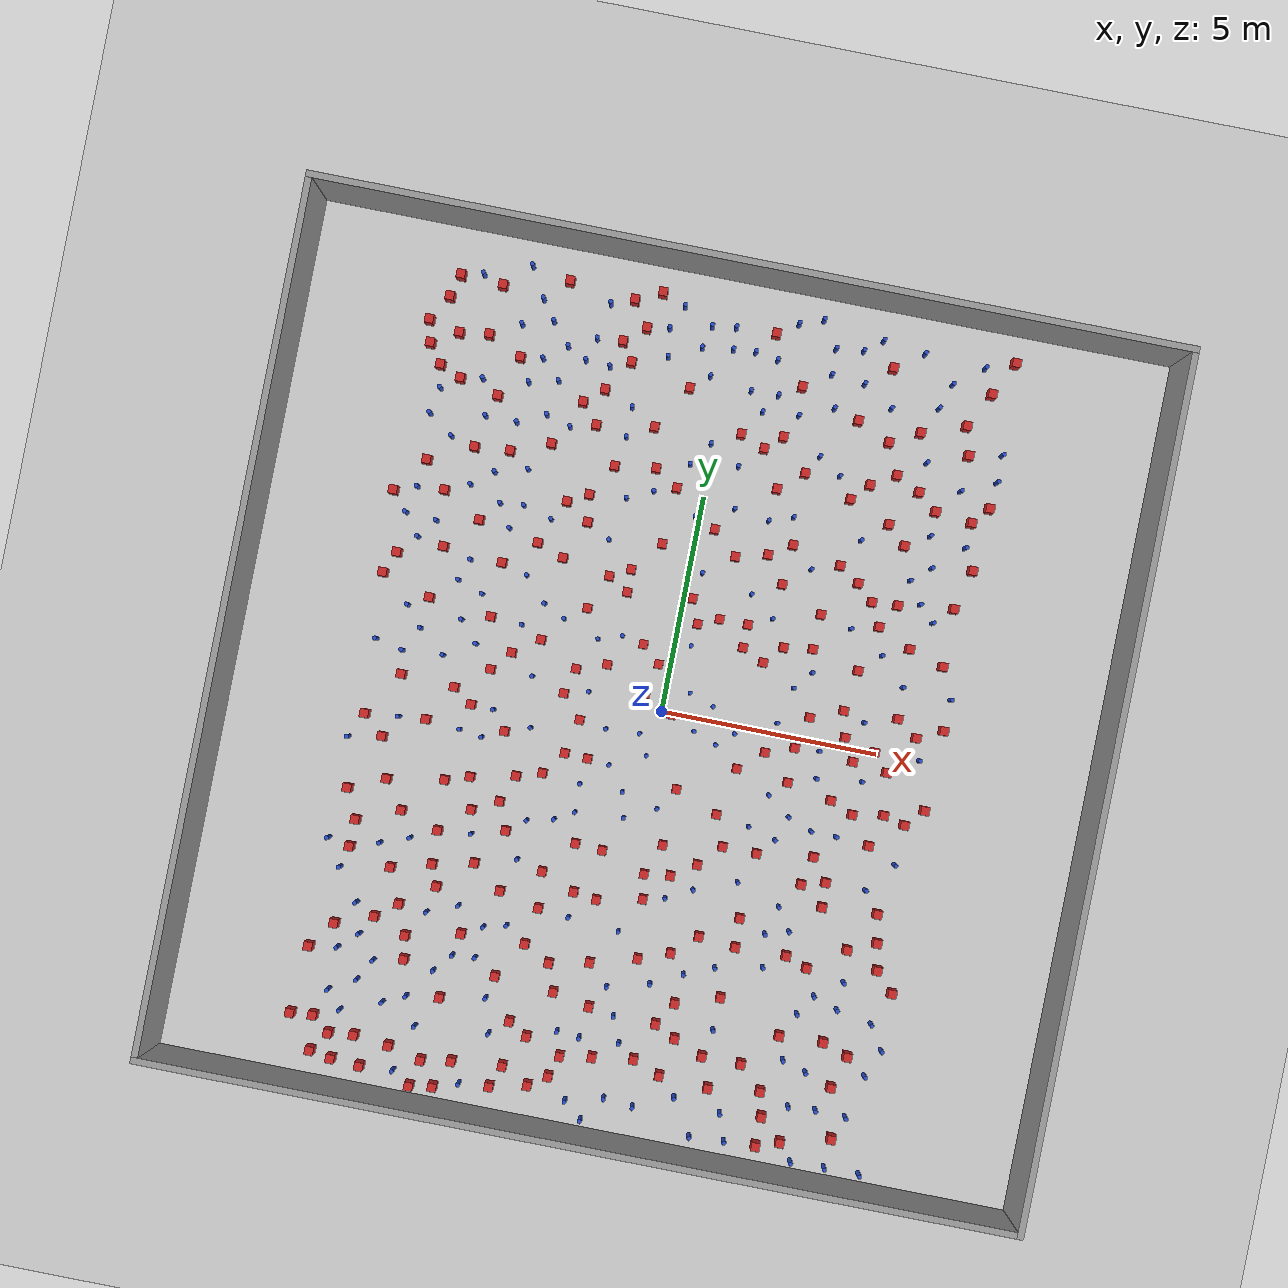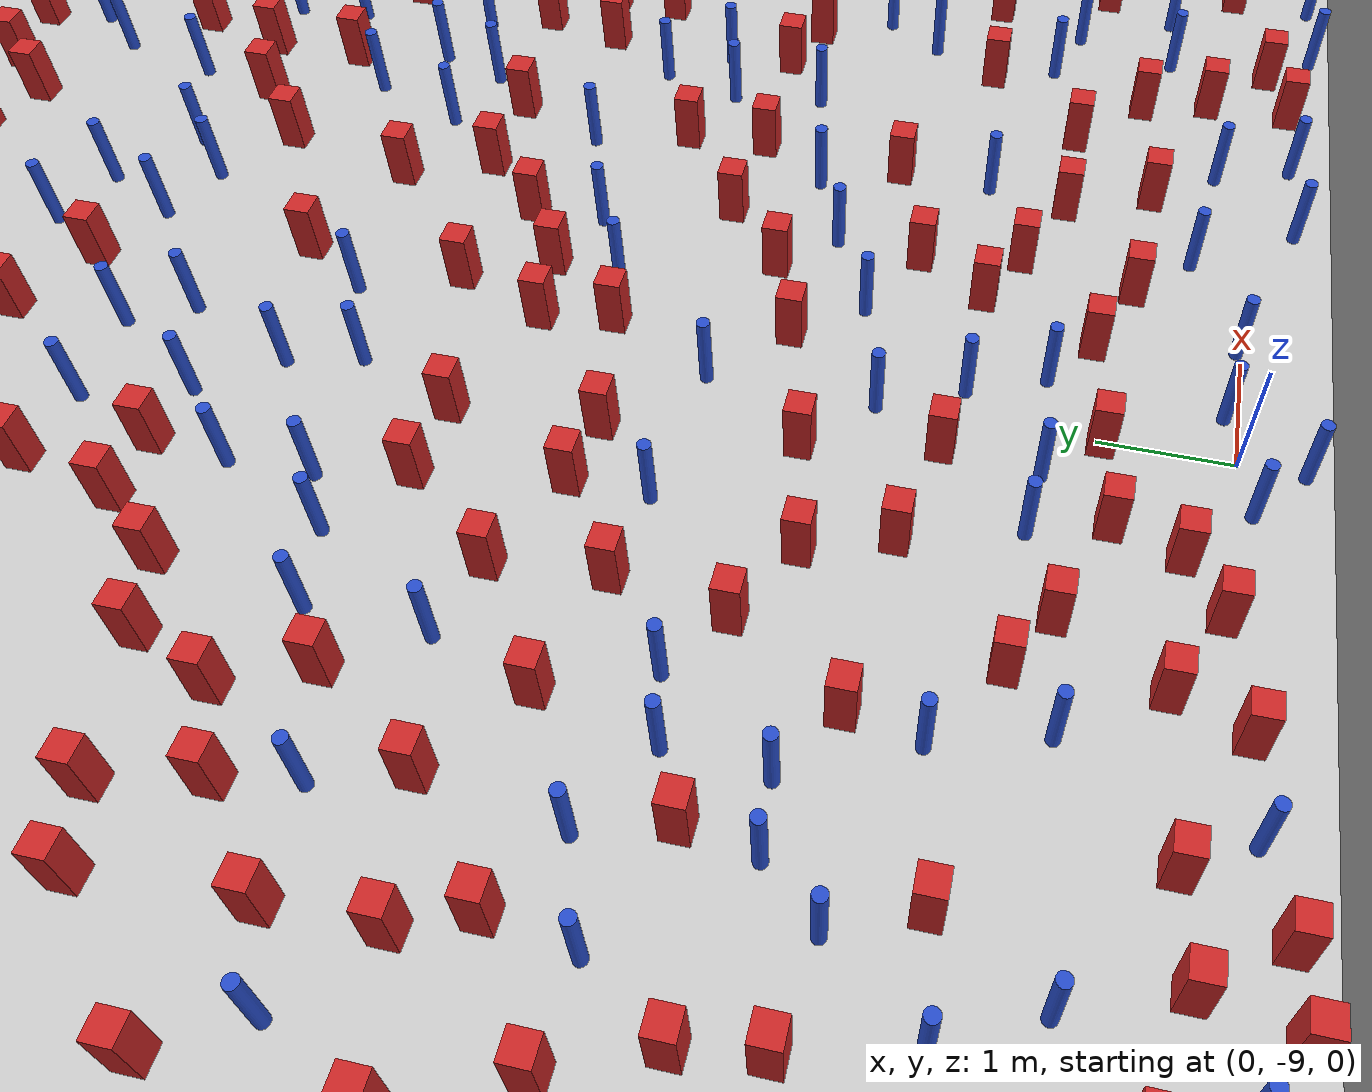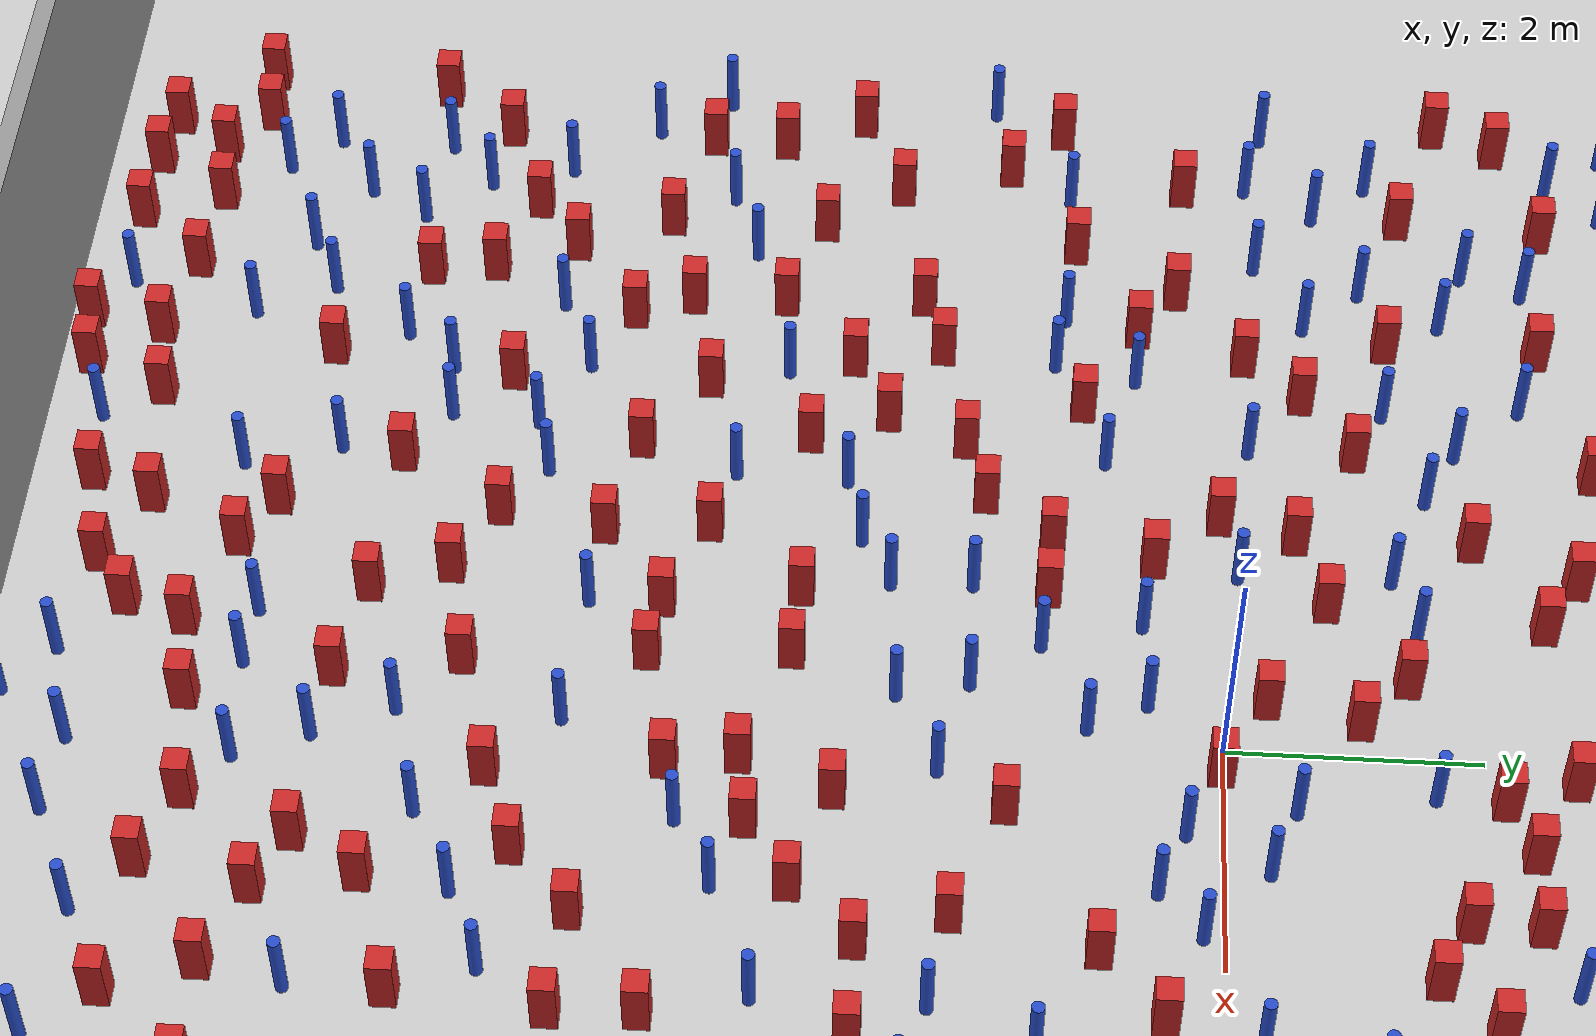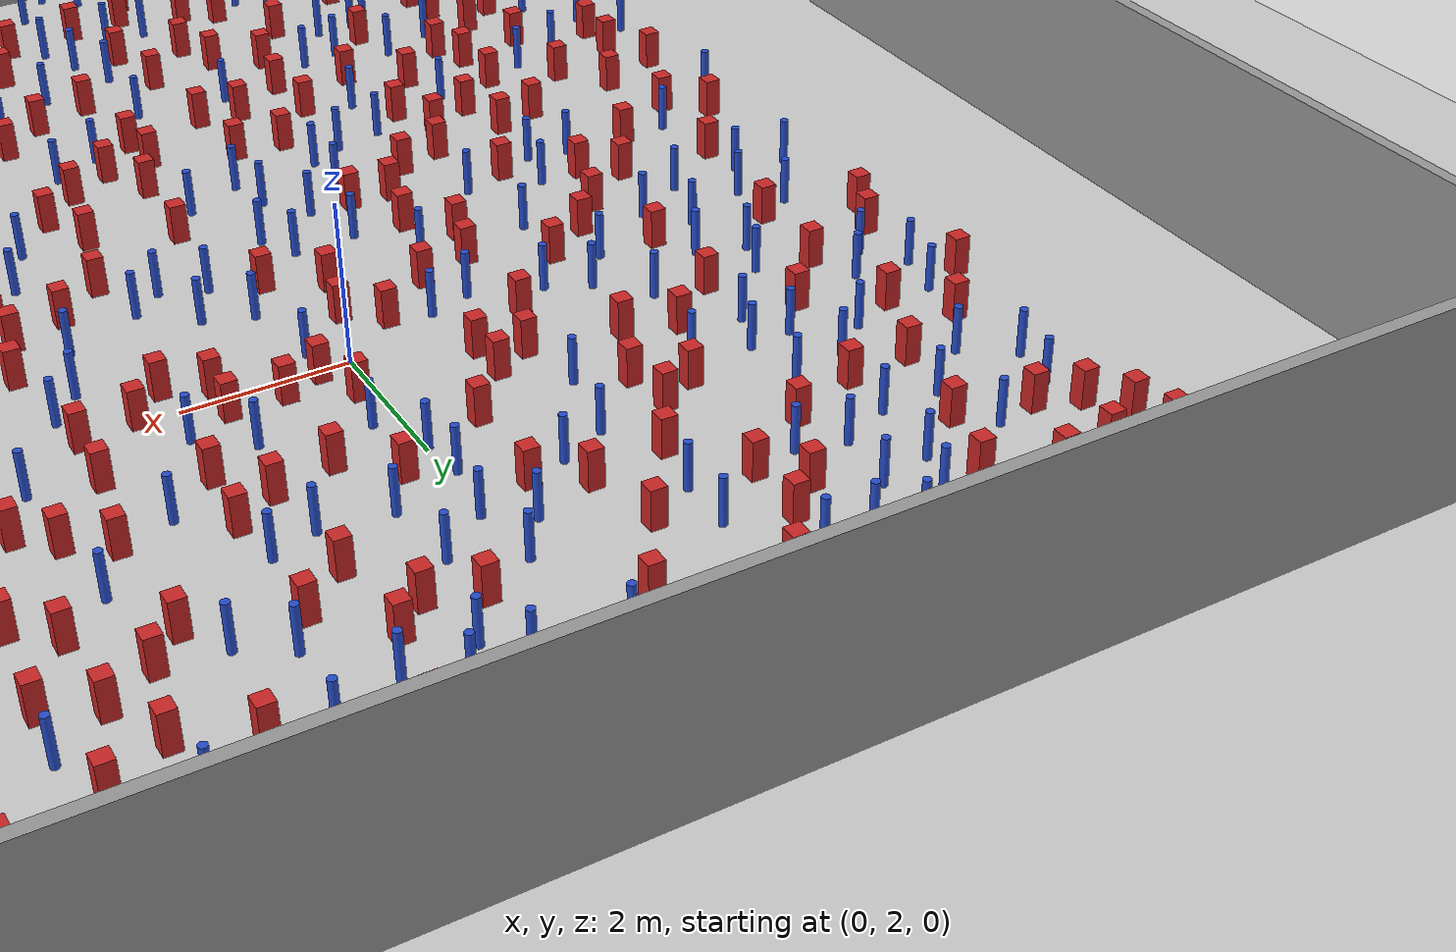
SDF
<sdf version="1.6">
 <world name="default">
  <light name="sun" type="directional">
   <pose>0 0 1000 0 -0 0</pose>
   <diffuse>0.8 0.8 0.8 1</diffuse>
   <specular>0.1 0.1 0.1 1</specular>
   <attenuation>
    <range>1000</range>
    <constant>0.9</constant>
    <linear>0.01</linear>
    <quadratic>0.001</quadratic>
   </attenuation>
   <direction>-0.5 0.5 -1</direction>
  </light>
  <model name="ground_plane">
   <static>1</static>
   <link name="link">
    <collision name="collision">
     <geometry><plane><normal>0 0 1</normal><size>100 100</size></plane></geometry>
     <surface><friction><ode><mu>100</mu><mu2>50</mu2></ode></friction></surface>
    </collision>
    <visual name="visual">
     <cast_shadows>0</cast_shadows>
     <geometry><plane><normal>0 0 1</normal><size>100 100</size></plane></geometry>
     <material>
      <ambient>1.0 1.0 1.0 1.0</ambient>
      <diffuse>0.8 0.8 0.8 1.0</diffuse>
      <specular>0.01 0.01 0.01 1.000000</specular>
     </material>
    </visual>
   </link>
  </model>
  <gravity>0 0 -9.8</gravity>
  <magnetic_field>6e-06 2.3e-05 -4.2e-05</magnetic_field>
  <atmosphere type="adiabatic"/>
  <physics name="default_physics" default="0" type="ode">
   <max_step_size>0.001</max_step_size>
   <real_time_factor>1</real_time_factor>
   <real_time_update_rate>1000</real_time_update_rate>
  </physics>
  <scene><ambient>0.4 0.4 0.4 1</ambient><background>0.7 0.7 0.7 1</background><shadows>1</shadows></scene>
  <spherical_coordinates>
   <surface_model>EARTH_WGS84</surface_model>
   <latitude_deg>0</latitude_deg>
   <longitude_deg>0</longitude_deg>
   <elevation>0</elevation>
   <heading_deg>0</heading_deg>
  </spherical_coordinates>
  <plugin name="gazebo_occupancy_map" filename="libgazebo_2Dmap_plugin.so">
   <map_resolution>0.05</map_resolution>
   <map_topic>generated_map</map_topic>
   <map_height>0.01</map_height>
   <map_size_x>50</map_size_x>
   <map_size_y>50</map_size_y>
  </plugin>
  <model name="NamedLocations">
   <static>true</static>
   <link name="DefaultStart"><pose>8.5 0 0 0 0 3.14</pose></link>
  </model>
  <model name="20x20_walls">
   <pose>0.044518 0.176112 0 0 -0 0</pose>
   <link name="Wall_1">
    <collision name="Wall_1_Collision">
     <geometry><box><size>20 0.15 2.5</size></box></geometry>
     <pose>0 0 1.25 0 -0 0</pose>
    </collision>
    <visual name="Wall_1_Visual">
     <pose>0 0 1.25 0 -0 0</pose>
     <geometry><box><size>20 0.15 2.5</size></box></geometry>
     <material>
      <script><uri>file://media/materials/scripts/gazebo.material</uri><name>Gazebo/Grey</name></script>
      <ambient>0.976471 0.992157 1 1</ambient>
     </material>
     <meta><layer>0</layer></meta>
    </visual>
    <pose>0 9.925 0 0 -0 0</pose>
   </link>
   <link name="Wall_3">
    <collision name="Wall_3_Collision">
     <geometry><box><size>20 0.15 2.5</size></box></geometry>
     <pose>0 0 1.25 0 -0 0</pose>
    </collision>
    <visual name="Wall_3_Visual">
     <pose>0 0 1.25 0 -0 0</pose>
     <geometry><box><size>20 0.15 2.5</size></box></geometry>
     <material>
      <script><uri>file://media/materials/scripts/gazebo.material</uri><name>Gazebo/Grey</name></script>
      <ambient>0.976471 0.992157 1 1</ambient>
     </material>
     <meta><layer>0</layer></meta>
    </visual>
    <pose>9.925 0 0 0 0 -1.5708</pose>
   </link>
   <link name="Wall_4">
    <collision name="Wall_4_Collision">
     <geometry><box><size>20 0.15 2.5</size></box></geometry>
     <pose>0 0 1.25 0 -0 0</pose>
    </collision>
    <visual name="Wall_4_Visual">
     <pose>0 0 1.25 0 -0 0</pose>
     <geometry><box><size>20 0.15 2.5</size></box></geometry>
     <material>
      <script><uri>file://media/materials/scripts/gazebo.material</uri><name>Gazebo/Grey</name></script>
      <ambient>0.976471 0.992157 1 1</ambient>
     </material>
     <meta><layer>0</layer></meta>
    </visual>
    <pose>0 -9.925 0 0 -0 3.14159</pose>
   </link>
   <link name="Wall_5">
    <collision name="Wall_5_Collision">
     <geometry><box><size>20 0.15 2.5</size></box></geometry>
     <pose>0 0 1.25 0 -0 0</pose>
    </collision>
    <visual name="Wall_5_Visual">
     <pose>0 0 1.25 0 -0 0</pose>
     <geometry><box><size>20 0.15 2.5</size></box></geometry>
     <material>
      <script><uri>file://media/materials/scripts/gazebo.material</uri><name>Gazebo/Grey</name></script>
      <ambient>0.976471 0.992157 1 1</ambient>
     </material>
     <meta><layer>0</layer></meta>
    </visual>
    <pose>-9.925 0 0 0 -0 1.5708</pose>
   </link>
   <static>1</static>
  </model>
  <model name="square_post_obstacle0">
   <static>true</static>
   <pose>-6.41497734222 8.90161578551 8.22691968438e-08 7.22125133819e-06 -7.54495500217e-07 2.29674213826e-05</pose>
   <link name="link">
    <pose>0 0 0.25 0 -0 0</pose>
    <inertial>
     <mass>100</mass>
     <inertia>
      <ixx>0.166667</ixx>
      <ixy>0</ixy>
      <ixz>0</ixz>
      <iyy>0.166667</iyy>
      <iyz>0</iyz>
      <izz>0.166667</izz>
     </inertia>
    </inertial>
    <collision name="collision"><geometry><box><size>.2 .2 .5</size></box></geometry></collision>
    <visual name="visual">
     <geometry><box><size>.2 .2 .5</size></box></geometry>
     <material>
      <script><name>Gazebo/Red</name><uri>file://media/materials/scripts/gazebo.material</uri></script>
     </material>
    </visual>
   </link>
  </model>
  <model name="square_post_obstacle1">
   <static>true</static>
   <pose>-1.42426274399 0.826658282085 8.22691968438e-08 7.2212513382e-06 -7.54495500217e-07 2.29674213826e-05</pose>
   <link name="link">
    <pose>0 0 0.25 0 -0 0</pose>
    <inertial>
     <mass>100</mass>
     <inertia>
      <ixx>0.166667</ixx>
      <ixy>0</ixy>
      <ixz>0</ixz>
      <iyy>0.166667</iyy>
      <iyz>0</iyz>
      <izz>0.166667</izz>
     </inertia>
    </inertial>
    <collision name="collision"><geometry><box><size>.2 .2 .5</size></box></geometry></collision>
    <visual name="visual">
     <geometry><box><size>.2 .2 .5</size></box></geometry>
     <material>
      <script><name>Gazebo/Red</name><uri>file://media/materials/scripts/gazebo.material</uri></script>
     </material>
    </visual>
   </link>
  </model>
  <model name="pole_obstacle0">
   <static>true</static>
   <pose>-3.10198556302 1.91438541618 2.88873142074e-08 -9.90536689395e-09 4.60219949e-07 -1.20965994953e-07</pose>
   <link name="link">
    <pose>0 0 0.3 0 -0 0</pose>
    <inertial>
     <mass>1</mass>
     <inertia><ixx>0.145833</ixx><ixy>0</ixy><ixz>0</ixz><iyy>0.145833</iyy><iyz>0</iyz><izz>0.125</izz></inertia>
    </inertial>
    <collision name="collision">
     <geometry><cylinder><radius>0.05</radius><length>.6</length></cylinder></geometry>
    </collision>
    <visual name="visual">
     <geometry><cylinder><radius>0.05</radius><length>.6</length></cylinder></geometry>
     <material>
      <script><name>Gazebo/Blue</name><uri>file://media/materials/scripts/gazebo.material</uri></script>
     </material>
    </visual>
   </link>
  </model>
  <model name="square_post_obstacle2">
   <static>true</static>
   <pose>-4.63760378168 -8.66727269813 8.22691968438e-08 7.22125133819e-06 -7.54495500217e-07 2.29674213826e-05</pose>
   <link name="link">
    <pose>0 0 0.25 0 -0 0</pose>
    <inertial>
     <mass>100</mass>
     <inertia>
      <ixx>0.166667</ixx>
      <ixy>0</ixy>
      <ixz>0</ixz>
      <iyy>0.166667</iyy>
      <iyz>0</iyz>
      <izz>0.166667</izz>
     </inertia>
    </inertial>
    <collision name="collision"><geometry><box><size>.2 .2 .5</size></box></geometry></collision>
    <visual name="visual">
     <geometry><box><size>.2 .2 .5</size></box></geometry>
     <material>
      <script><name>Gazebo/Red</name><uri>file://media/materials/scripts/gazebo.material</uri></script>
     </material>
    </visual>
   </link>
  </model>
  <model name="pole_obstacle1">
   <static>true</static>
   <pose>-5.92161153514 5.25024343142 2.88873142074e-08 -9.90536690842e-09 4.60219948965e-07 -1.20965994976e-07</pose>
   <link name="link">
    <pose>0 0 0.3 0 -0 0</pose>
    <inertial>
     <mass>1</mass>
     <inertia><ixx>0.145833</ixx><ixy>0</ixy><ixz>0</ixz><iyy>0.145833</iyy><iyz>0</iyz><izz>0.125</izz></inertia>
    </inertial>
    <collision name="collision">
     <geometry><cylinder><radius>0.05</radius><length>.6</length></cylinder></geometry>
    </collision>
    <visual name="visual">
     <geometry><cylinder><radius>0.05</radius><length>.6</length></cylinder></geometry>
     <material>
      <script><name>Gazebo/Blue</name><uri>file://media/materials/scripts/gazebo.material</uri></script>
     </material>
    </visual>
   </link>
  </model>
  <model name="square_post_obstacle3">
   <static>true</static>
   <pose>-6.85389334559 1.90299127063 8.22691968438e-08 7.2212513382e-06 -7.54495500217e-07 2.29674213826e-05</pose>
   <link name="link">
    <pose>0 0 0.25 0 -0 0</pose>
    <inertial>
     <mass>100</mass>
     <inertia>
      <ixx>0.166667</ixx>
      <ixy>0</ixy>
      <ixz>0</ixz>
      <iyy>0.166667</iyy>
      <iyz>0</iyz>
      <izz>0.166667</izz>
     </inertia>
    </inertial>
    <collision name="collision"><geometry><box><size>.2 .2 .5</size></box></geometry></collision>
    <visual name="visual">
     <geometry><box><size>.2 .2 .5</size></box></geometry>
     <material>
      <script><name>Gazebo/Red</name><uri>file://media/materials/scripts/gazebo.material</uri></script>
     </material>
    </visual>
   </link>
  </model>
  <model name="pole_obstacle2">
   <static>true</static>
   <pose>5.98450393282 0.0520118325981 2.88873142074e-08 -9.90536689361e-09 4.60219949001e-07 -1.20965994955e-07</pose>
   <link name="link">
    <pose>0 0 0.3 0 -0 0</pose>
    <inertial>
     <mass>1</mass>
     <inertia><ixx>0.145833</ixx><ixy>0</ixy><ixz>0</ixz><iyy>0.145833</iyy><iyz>0</iyz><izz>0.125</izz></inertia>
    </inertial>
    <collision name="collision">
     <geometry><cylinder><radius>0.05</radius><length>.6</length></cylinder></geometry>
    </collision>
    <visual name="visual">
     <geometry><cylinder><radius>0.05</radius><length>.6</length></cylinder></geometry>
     <material>
      <script><name>Gazebo/Blue</name><uri>file://media/materials/scripts/gazebo.material</uri></script>
     </material>
    </visual>
   </link>
  </model>
  <model name="pole_obstacle3">
   <static>true</static>
   <pose>5.07343041441 8.62092034777 2.88873142074e-08 -9.9053668967e-09 4.60219948993e-07 -1.20965994957e-07</pose>
   <link name="link">
    <pose>0 0 0.3 0 -0 0</pose>
    <inertial>
     <mass>1</mass>
     <inertia><ixx>0.145833</ixx><ixy>0</ixy><ixz>0</ixz><iyy>0.145833</iyy><iyz>0</iyz><izz>0.125</izz></inertia>
    </inertial>
    <collision name="collision">
     <geometry><cylinder><radius>0.05</radius><length>.6</length></cylinder></geometry>
    </collision>
    <visual name="visual">
     <geometry><cylinder><radius>0.05</radius><length>.6</length></cylinder></geometry>
     <material>
      <script><name>Gazebo/Blue</name><uri>file://media/materials/scripts/gazebo.material</uri></script>
     </material>
    </visual>
   </link>
  </model>
  <model name="square_post_obstacle4">
   <static>true</static>
   <pose>3.6613418634 6.00296689064 8.22691968438e-08 7.2212513382e-06 -7.54495500217e-07 2.29674213826e-05</pose>
   <link name="link">
    <pose>0 0 0.25 0 -0 0</pose>
    <inertial>
     <mass>100</mass>
     <inertia>
      <ixx>0.166667</ixx>
      <ixy>0</ixy>
      <ixz>0</ixz>
      <iyy>0.166667</iyy>
      <iyz>0</iyz>
      <izz>0.166667</izz>
     </inertia>
    </inertial>
    <collision name="collision"><geometry><box><size>.2 .2 .5</size></box></geometry></collision>
    <visual name="visual">
     <geometry><box><size>.2 .2 .5</size></box></geometry>
     <material>
      <script><name>Gazebo/Red</name><uri>file://media/materials/scripts/gazebo.material</uri></script>
     </material>
    </visual>
   </link>
  </model>
  <model name="square_post_obstacle5">
   <static>true</static>
   <pose>3.35381513687 4.06775234685 8.22691968438e-08 7.22125133819e-06 -7.54495500217e-07 2.29674213826e-05</pose>
   <link name="link">
    <pose>0 0 0.25 0 -0 0</pose>
    <inertial>
     <mass>100</mass>
     <inertia>
      <ixx>0.166667</ixx>
      <ixy>0</ixy>
      <ixz>0</ixz>
      <iyy>0.166667</iyy>
      <iyz>0</iyz>
      <izz>0.166667</izz>
     </inertia>
    </inertial>
    <collision name="collision"><geometry><box><size>.2 .2 .5</size></box></geometry></collision>
    <visual name="visual">
     <geometry><box><size>.2 .2 .5</size></box></geometry>
     <material>
      <script><name>Gazebo/Red</name><uri>file://media/materials/scripts/gazebo.material</uri></script>
     </material>
    </visual>
   </link>
  </model>
  <model name="square_post_obstacle6">
   <static>true</static>
   <pose>-6.14977336473 -1.77172917575 8.22691968438e-08 7.2212513382e-06 -7.54495500217e-07 2.29674213826e-05</pose>
   <link name="link">
    <pose>0 0 0.25 0 -0 0</pose>
    <inertial>
     <mass>100</mass>
     <inertia>
      <ixx>0.166667</ixx>
      <ixy>0</ixy>
      <ixz>0</ixz>
      <iyy>0.166667</iyy>
      <iyz>0</iyz>
      <izz>0.166667</izz>
     </inertia>
    </inertial>
    <collision name="collision"><geometry><box><size>.2 .2 .5</size></box></geometry></collision>
    <visual name="visual">
     <geometry><box><size>.2 .2 .5</size></box></geometry>
     <material>
      <script><name>Gazebo/Red</name><uri>file://media/materials/scripts/gazebo.material</uri></script>
     </material>
    </visual>
   </link>
  </model>
  <model name="pole_obstacle4">
   <static>true</static>
   <pose>-4.5411840801 1.85169963479 2.88873142074e-08 -9.90536689445e-09 4.60219948999e-07 -1.20965994956e-07</pose>
   <link name="link">
    <pose>0 0 0.3 0 -0 0</pose>
    <inertial>
     <mass>1</mass>
     <inertia><ixx>0.145833</ixx><ixy>0</ixy><ixz>0</ixz><iyy>0.145833</iyy><iyz>0</iyz><izz>0.125</izz></inertia>
    </inertial>
    <collision name="collision">
     <geometry><cylinder><radius>0.05</radius><length>.6</length></cylinder></geometry>
    </collision>
    <visual name="visual">
     <geometry><cylinder><radius>0.05</radius><length>.6</length></cylinder></geometry>
     <material>
      <script><name>Gazebo/Blue</name><uri>file://media/materials/scripts/gazebo.material</uri></script>
     </material>
    </visual>
   </link>
  </model>
  <model name="pole_obstacle5">
   <static>true</static>
   <pose>-0.0787038739394 6.22609958677 2.88873142074e-08 -9.90536689804e-09 4.6021994899e-07 -1.2096599496e-07</pose>
   <link name="link">
    <pose>0 0 0.3 0 -0 0</pose>
    <inertial>
     <mass>1</mass>
     <inertia><ixx>0.145833</ixx><ixy>0</ixy><ixz>0</ixz><iyy>0.145833</iyy><iyz>0</iyz><izz>0.125</izz></inertia>
    </inertial>
    <collision name="collision">
     <geometry><cylinder><radius>0.05</radius><length>.6</length></cylinder></geometry>
    </collision>
    <visual name="visual">
     <geometry><cylinder><radius>0.05</radius><length>.6</length></cylinder></geometry>
     <material>
      <script><name>Gazebo/Blue</name><uri>file://media/materials/scripts/gazebo.material</uri></script>
     </material>
    </visual>
   </link>
  </model>
  <model name="square_post_obstacle7">
   <static>true</static>
   <pose>3.33007121524 -7.52048143749 8.22691968438e-08 7.2212513382e-06 -7.54495500217e-07 2.29674213826e-05</pose>
   <link name="link">
    <pose>0 0 0.25 0 -0 0</pose>
    <inertial>
     <mass>100</mass>
     <inertia>
      <ixx>0.166667</ixx>
      <ixy>0</ixy>
      <ixz>0</ixz>
      <iyy>0.166667</iyy>
      <iyz>0</iyz>
      <izz>0.166667</izz>
     </inertia>
    </inertial>
    <collision name="collision"><geometry><box><size>.2 .2 .5</size></box></geometry></collision>
    <visual name="visual">
     <geometry><box><size>.2 .2 .5</size></box></geometry>
     <material>
      <script><name>Gazebo/Red</name><uri>file://media/materials/scripts/gazebo.material</uri></script>
     </material>
    </visual>
   </link>
  </model>
  <model name="square_post_obstacle8">
   <static>true</static>
   <pose>4.79156182953 6.05507499224 8.22691968438e-08 7.2212513382e-06 -7.54495500217e-07 2.29674213826e-05</pose>
   <link name="link">
    <pose>0 0 0.25 0 -0 0</pose>
    <inertial>
     <mass>100</mass>
     <inertia>
      <ixx>0.166667</ixx>
      <ixy>0</ixy>
      <ixz>0</ixz>
      <iyy>0.166667</iyy>
      <iyz>0</iyz>
      <izz>0.166667</izz>
     </inertia>
    </inertial>
    <collision name="collision"><geometry><box><size>.2 .2 .5</size></box></geometry></collision>
    <visual name="visual">
     <geometry><box><size>.2 .2 .5</size></box></geometry>
     <material>
      <script><name>Gazebo/Red</name><uri>file://media/materials/scripts/gazebo.material</uri></script>
     </material>
    </visual>
   </link>
  </model>
  <model name="pole_obstacle6">
   <static>true</static>
   <pose>1.13319620312 0.348081348117 2.88873142074e-08 -9.90536689733e-09 4.60219948992e-07 -1.20965994959e-07</pose>
   <link name="link">
    <pose>0 0 0.3 0 -0 0</pose>
    <inertial>
     <mass>1</mass>
     <inertia><ixx>0.145833</ixx><ixy>0</ixy><ixz>0</ixz><iyy>0.145833</iyy><iyz>0</iyz><izz>0.125</izz></inertia>
    </inertial>
    <collision name="collision">
     <geometry><cylinder><radius>0.05</radius><length>.6</length></cylinder></geometry>
    </collision>
    <visual name="visual">
     <geometry><cylinder><radius>0.05</radius><length>.6</length></cylinder></geometry>
     <material>
      <script><name>Gazebo/Blue</name><uri>file://media/materials/scripts/gazebo.material</uri></script>
     </material>
    </visual>
   </link>
  </model>
  <model name="pole_obstacle7">
   <static>true</static>
   <pose>-5.88058021579 -8.07707349114 2.88873142074e-08 -9.9053668967e-09 4.60219948993e-07 -1.20965994957e-07</pose>
   <link name="link">
    <pose>0 0 0.3 0 -0 0</pose>
    <inertial>
     <mass>1</mass>
     <inertia><ixx>0.145833</ixx><ixy>0</ixy><ixz>0</ixz><iyy>0.145833</iyy><iyz>0</iyz><izz>0.125</izz></inertia>
    </inertial>
    <collision name="collision">
     <geometry><cylinder><radius>0.05</radius><length>.6</length></cylinder></geometry>
    </collision>
    <visual name="visual">
     <geometry><cylinder><radius>0.05</radius><length>.6</length></cylinder></geometry>
     <material>
      <script><name>Gazebo/Blue</name><uri>file://media/materials/scripts/gazebo.material</uri></script>
     </material>
    </visual>
   </link>
  </model>
  <model name="square_post_obstacle9">
   <static>true</static>
   <pose>2.0536290855 1.55828655313 8.22691968438e-08 7.2212513382e-06 -7.54495500217e-07 2.29674213826e-05</pose>
   <link name="link">
    <pose>0 0 0.25 0 -0 0</pose>
    <inertial>
     <mass>100</mass>
     <inertia>
      <ixx>0.166667</ixx>
      <ixy>0</ixy>
      <ixz>0</ixz>
      <iyy>0.166667</iyy>
      <iyz>0</iyz>
      <izz>0.166667</izz>
     </inertia>
    </inertial>
    <collision name="collision"><geometry><box><size>.2 .2 .5</size></box></geometry></collision>
    <visual name="visual">
     <geometry><box><size>.2 .2 .5</size></box></geometry>
     <material>
      <script><name>Gazebo/Red</name><uri>file://media/materials/scripts/gazebo.material</uri></script>
     </material>
    </visual>
   </link>
  </model>
  <model name="square_post_obstacle10">
   <static>true</static>
   <pose>-6.63615204594 -1.33718850328 8.22691968438e-08 7.2212513382e-06 -7.54495500217e-07 2.29674213826e-05</pose>
   <link name="link">
    <pose>0 0 0.25 0 -0 0</pose>
    <inertial>
     <mass>100</mass>
     <inertia>
      <ixx>0.166667</ixx>
      <ixy>0</ixy>
      <ixz>0</ixz>
      <iyy>0.166667</iyy>
      <iyz>0</iyz>
      <izz>0.166667</izz>
     </inertia>
    </inertial>
    <collision name="collision"><geometry><box><size>.2 .2 .5</size></box></geometry></collision>
    <visual name="visual">
     <geometry><box><size>.2 .2 .5</size></box></geometry>
     <material>
      <script><name>Gazebo/Red</name><uri>file://media/materials/scripts/gazebo.material</uri></script>
     </material>
    </visual>
   </link>
  </model>
  <model name="square_post_obstacle11">
   <static>true</static>
   <pose>-1.44816403198 -1.3662161427 8.22691968438e-08 7.2212513382e-06 -7.54495500217e-07 2.29674213826e-05</pose>
   <link name="link">
    <pose>0 0 0.25 0 -0 0</pose>
    <inertial>
     <mass>100</mass>
     <inertia>
      <ixx>0.166667</ixx>
      <ixy>0</ixy>
      <ixz>0</ixz>
      <iyy>0.166667</iyy>
      <iyz>0</iyz>
      <izz>0.166667</izz>
     </inertia>
    </inertial>
    <collision name="collision"><geometry><box><size>.2 .2 .5</size></box></geometry></collision>
    <visual name="visual">
     <geometry><box><size>.2 .2 .5</size></box></geometry>
     <material>
      <script><name>Gazebo/Red</name><uri>file://media/materials/scripts/gazebo.material</uri></script>
     </material>
    </visual>
   </link>
  </model>
  <model name="square_post_obstacle12">
   <static>true</static>
   <pose>-6.37226330416 -9.11028551085 8.22691968438e-08 7.22125133819e-06 -7.54495500217e-07 2.29674213826e-05</pose>
   <link name="link">
    <pose>0 0 0.25 0 -0 0</pose>
    <inertial>
     <mass>100</mass>
     <inertia>
      <ixx>0.166667</ixx>
      <ixy>0</ixy>
      <ixz>0</ixz>
      <iyy>0.166667</iyy>
      <iyz>0</iyz>
      <izz>0.166667</izz>
     </inertia>
    </inertial>
    <collision name="collision"><geometry><box><size>.2 .2 .5</size></box></geometry></collision>
    <visual name="visual">
     <geometry><box><size>.2 .2 .5</size></box></geometry>
     <material>
      <script><name>Gazebo/Red</name><uri>file://media/materials/scripts/gazebo.material</uri></script>
     </material>
    </visual>
   </link>
  </model>
  <model name="square_post_obstacle13">
   <static>true</static>
   <pose>5.93335077788 -1.4574501915 8.22691968438e-08 7.2212513382e-06 -7.54495500217e-07 2.29674213826e-05</pose>
   <link name="link">
    <pose>0 0 0.25 0 -0 0</pose>
    <inertial>
     <mass>100</mass>
     <inertia>
      <ixx>0.166667</ixx>
      <ixy>0</ixy>
      <ixz>0</ixz>
      <iyy>0.166667</iyy>
      <iyz>0</iyz>
      <izz>0.166667</izz>
     </inertia>
    </inertial>
    <collision name="collision"><geometry><box><size>.2 .2 .5</size></box></geometry></collision>
    <visual name="visual">
     <geometry><box><size>.2 .2 .5</size></box></geometry>
     <material>
      <script><name>Gazebo/Red</name><uri>file://media/materials/scripts/gazebo.material</uri></script>
     </material>
    </visual>
   </link>
  </model>
  <model name="pole_obstacle8">
   <static>true</static>
   <pose>0.0293933119848 5.34193619767 2.88873142074e-08 -9.90536689629e-09 4.60219948994e-07 -1.20965994958e-07</pose>
   <link name="link">
    <pose>0 0 0.3 0 -0 0</pose>
    <inertial>
     <mass>1</mass>
     <inertia><ixx>0.145833</ixx><ixy>0</ixy><ixz>0</ixz><iyy>0.145833</iyy><iyz>0</iyz><izz>0.125</izz></inertia>
    </inertial>
    <collision name="collision">
     <geometry><cylinder><radius>0.05</radius><length>.6</length></cylinder></geometry>
    </collision>
    <visual name="visual">
     <geometry><cylinder><radius>0.05</radius><length>.6</length></cylinder></geometry>
     <material>
      <script><name>Gazebo/Blue</name><uri>file://media/materials/scripts/gazebo.material</uri></script>
     </material>
    </visual>
   </link>
  </model>
  <model name="square_post_obstacle14">
   <static>true</static>
   <pose>-6.56751136716 8.36806313331 8.22691968438e-08 7.22125133819e-06 -7.54495500217e-07 2.29674213826e-05</pose>
   <link name="link">
    <pose>0 0 0.25 0 -0 0</pose>
    <inertial>
     <mass>100</mass>
     <inertia>
      <ixx>0.166667</ixx>
      <ixy>0</ixy>
      <ixz>0</ixz>
      <iyy>0.166667</iyy>
      <iyz>0</iyz>
      <izz>0.166667</izz>
     </inertia>
    </inertial>
    <collision name="collision"><geometry><box><size>.2 .2 .5</size></box></geometry></collision>
    <visual name="visual">
     <geometry><box><size>.2 .2 .5</size></box></geometry>
     <material>
      <script><name>Gazebo/Red</name><uri>file://media/materials/scripts/gazebo.material</uri></script>
     </material>
    </visual>
   </link>
  </model>
  <model name="square_post_obstacle15">
   <static>true</static>
   <pose>5.32238337618 0.8916731845 8.22691968438e-08 7.2212513382e-06 -7.54495500217e-07 2.29674213826e-05</pose>
   <link name="link">
    <pose>0 0 0.25 0 -0 0</pose>
    <inertial>
     <mass>100</mass>
     <inertia>
      <ixx>0.166667</ixx>
      <ixy>0</ixy>
      <ixz>0</ixz>
      <iyy>0.166667</iyy>
      <iyz>0</iyz>
      <izz>0.166667</izz>
     </inertia>
    </inertial>
    <collision name="collision"><geometry><box><size>.2 .2 .5</size></box></geometry></collision>
    <visual name="visual">
     <geometry><box><size>.2 .2 .5</size></box></geometry>
     <material>
      <script><name>Gazebo/Red</name><uri>file://media/materials/scripts/gazebo.material</uri></script>
     </material>
    </visual>
   </link>
  </model>
  <model name="square_post_obstacle16">
   <static>true</static>
   <pose>-1.18355301893 -6.73580773037 8.22691968438e-08 7.2212513382e-06 -7.54495500217e-07 2.29674213826e-05</pose>
   <link name="link">
    <pose>0 0 0.25 0 -0 0</pose>
    <inertial>
     <mass>100</mass>
     <inertia>
      <ixx>0.166667</ixx>
      <ixy>0</ixy>
      <ixz>0</ixz>
      <iyy>0.166667</iyy>
      <iyz>0</iyz>
      <izz>0.166667</izz>
     </inertia>
    </inertial>
    <collision name="collision"><geometry><box><size>.2 .2 .5</size></box></geometry></collision>
    <visual name="visual">
     <geometry><box><size>.2 .2 .5</size></box></geometry>
     <material>
      <script><name>Gazebo/Red</name><uri>file://media/materials/scripts/gazebo.material</uri></script>
     </material>
    </visual>
   </link>
  </model>
  <model name="pole_obstacle9">
   <static>true</static>
   <pose>6.42302813318 1.54928854973 2.88873142074e-08 -9.90536689445e-09 4.60219948999e-07 -1.20965994956e-07</pose>
   <link name="link">
    <pose>0 0 0.3 0 -0 0</pose>
    <inertial>
     <mass>1</mass>
     <inertia><ixx>0.145833</ixx><ixy>0</ixy><ixz>0</ixz><iyy>0.145833</iyy><iyz>0</iyz><izz>0.125</izz></inertia>
    </inertial>
    <collision name="collision">
     <geometry><cylinder><radius>0.05</radius><length>.6</length></cylinder></geometry>
    </collision>
    <visual name="visual">
     <geometry><cylinder><radius>0.05</radius><length>.6</length></cylinder></geometry>
     <material>
      <script><name>Gazebo/Blue</name><uri>file://media/materials/scripts/gazebo.material</uri></script>
     </material>
    </visual>
   </link>
  </model>
  <model name="square_post_obstacle17">
   <static>true</static>
   <pose>-4.26707742421 -4.89532385467 8.22691968438e-08 7.22125133819e-06 -7.54495500217e-07 2.29674213826e-05</pose>
   <link name="link">
    <pose>0 0 0.25 0 -0 0</pose>
    <inertial>
     <mass>100</mass>
     <inertia>
      <ixx>0.166667</ixx>
      <ixy>0</ixy>
      <ixz>0</ixz>
      <iyy>0.166667</iyy>
      <iyz>0</iyz>
      <izz>0.166667</izz>
     </inertia>
    </inertial>
    <collision name="collision"><geometry><box><size>.2 .2 .5</size></box></geometry></collision>
    <visual name="visual">
     <geometry><box><size>.2 .2 .5</size></box></geometry>
     <material>
      <script><name>Gazebo/Red</name><uri>file://media/materials/scripts/gazebo.material</uri></script>
     </material>
    </visual>
   </link>
  </model>
  <model name="square_post_obstacle18">
   <static>true</static>
   <pose>1.27242105689 -5.35090698506 8.22691968438e-08 7.2212513382e-06 -7.54495500217e-07 2.29674213826e-05</pose>
   <link name="link">
    <pose>0 0 0.25 0 -0 0</pose>
    <inertial>
     <mass>100</mass>
     <inertia>
      <ixx>0.166667</ixx>
      <ixy>0</ixy>
      <ixz>0</ixz>
      <iyy>0.166667</iyy>
      <iyz>0</iyz>
      <izz>0.166667</izz>
     </inertia>
    </inertial>
    <collision name="collision"><geometry><box><size>.2 .2 .5</size></box></geometry></collision>
    <visual name="visual">
     <geometry><box><size>.2 .2 .5</size></box></geometry>
     <material>
      <script><name>Gazebo/Red</name><uri>file://media/materials/scripts/gazebo.material</uri></script>
     </material>
    </visual>
   </link>
  </model>
  <model name="pole_obstacle10">
   <static>true</static>
   <pose>-6.23004382909 -7.67100332995 2.88873142074e-08 -9.90536690842e-09 4.60219948965e-07 -1.20965994976e-07</pose>
   <link name="link">
    <pose>0 0 0.3 0 -0 0</pose>
    <inertial>
     <mass>1</mass>
     <inertia><ixx>0.145833</ixx><ixy>0</ixy><ixz>0</ixz><iyy>0.145833</iyy><iyz>0</iyz><izz>0.125</izz></inertia>
    </inertial>
    <collision name="collision">
     <geometry><cylinder><radius>0.05</radius><length>.6</length></cylinder></geometry>
    </collision>
    <visual name="visual">
     <geometry><cylinder><radius>0.05</radius><length>.6</length></cylinder></geometry>
     <material>
      <script><name>Gazebo/Blue</name><uri>file://media/materials/scripts/gazebo.material</uri></script>
     </material>
    </visual>
   </link>
  </model>
  <model name="square_post_obstacle19">
   <static>true</static>
   <pose>-5.0313347666 -5.4518797004 8.22691968438e-08 7.2212513382e-06 -7.54495500217e-07 2.29674213826e-05</pose>
   <link name="link">
    <pose>0 0 0.25 0 -0 0</pose>
    <inertial>
     <mass>100</mass>
     <inertia>
      <ixx>0.166667</ixx>
      <ixy>0</ixy>
      <ixz>0</ixz>
      <iyy>0.166667</iyy>
      <iyz>0</iyz>
      <izz>0.166667</izz>
     </inertia>
    </inertial>
    <collision name="collision"><geometry><box><size>.2 .2 .5</size></box></geometry></collision>
    <visual name="visual">
     <geometry><box><size>.2 .2 .5</size></box></geometry>
     <material>
      <script><name>Gazebo/Red</name><uri>file://media/materials/scripts/gazebo.material</uri></script>
     </material>
    </visual>
   </link>
  </model>
  <model name="pole_obstacle11">
   <static>true</static>
   <pose>-2.44617048429 -7.94701474159 2.88873142074e-08 -9.90536689859e-09 4.60219948989e-07 -1.20965994961e-07</pose>
   <link name="link">
    <pose>0 0 0.3 0 -0 0</pose>
    <inertial>
     <mass>1</mass>
     <inertia><ixx>0.145833</ixx><ixy>0</ixy><ixz>0</ixz><iyy>0.145833</iyy><iyz>0</iyz><izz>0.125</izz></inertia>
    </inertial>
    <collision name="collision">
     <geometry><cylinder><radius>0.05</radius><length>.6</length></cylinder></geometry>
    </collision>
    <visual name="visual">
     <geometry><cylinder><radius>0.05</radius><length>.6</length></cylinder></geometry>
     <material>
      <script><name>Gazebo/Blue</name><uri>file://media/materials/scripts/gazebo.material</uri></script>
     </material>
    </visual>
   </link>
  </model>
  <model name="square_post_obstacle20">
   <static>true</static>
   <pose>4.81783541929 3.42962507963 8.22691968438e-08 7.2212513382e-06 -7.54495500217e-07 2.29674213826e-05</pose>
   <link name="link">
    <pose>0 0 0.25 0 -0 0</pose>
    <inertial>
     <mass>100</mass>
     <inertia>
      <ixx>0.166667</ixx>
      <ixy>0</ixy>
      <ixz>0</ixz>
      <iyy>0.166667</iyy>
      <iyz>0</iyz>
      <izz>0.166667</izz>
     </inertia>
    </inertial>
    <collision name="collision"><geometry><box><size>.2 .2 .5</size></box></geometry></collision>
    <visual name="visual">
     <geometry><box><size>.2 .2 .5</size></box></geometry>
     <material>
      <script><name>Gazebo/Red</name><uri>file://media/materials/scripts/gazebo.material</uri></script>
     </material>
    </visual>
   </link>
  </model>
  <model name="pole_obstacle12">
   <static>true</static>
   <pose>-4.45807424097 8.7269577756 2.88873142074e-08 -9.9053668967e-09 4.60219948993e-07 -1.20965994957e-07</pose>
   <link name="link">
    <pose>0 0 0.3 0 -0 0</pose>
    <inertial>
     <mass>1</mass>
     <inertia><ixx>0.145833</ixx><ixy>0</ixy><ixz>0</ixz><iyy>0.145833</iyy><iyz>0</iyz><izz>0.125</izz></inertia>
    </inertial>
    <collision name="collision">
     <geometry><cylinder><radius>0.05</radius><length>.6</length></cylinder></geometry>
    </collision>
    <visual name="visual">
     <geometry><cylinder><radius>0.05</radius><length>.6</length></cylinder></geometry>
     <material>
      <script><name>Gazebo/Blue</name><uri>file://media/materials/scripts/gazebo.material</uri></script>
     </material>
    </visual>
   </link>
  </model>
  <model name="square_post_obstacle21">
   <static>true</static>
   <pose>3.28651102273 5.59727362077 8.22691968438e-08 7.2212513382e-06 -7.54495500217e-07 2.29674213826e-05</pose>
   <link name="link">
    <pose>0 0 0.25 0 -0 0</pose>
    <inertial>
     <mass>100</mass>
     <inertia>
      <ixx>0.166667</ixx>
      <ixy>0</ixy>
      <ixz>0</ixz>
      <iyy>0.166667</iyy>
      <iyz>0</iyz>
      <izz>0.166667</izz>
     </inertia>
    </inertial>
    <collision name="collision"><geometry><box><size>.2 .2 .5</size></box></geometry></collision>
    <visual name="visual">
     <geometry><box><size>.2 .2 .5</size></box></geometry>
     <material>
      <script><name>Gazebo/Red</name><uri>file://media/materials/scripts/gazebo.material</uri></script>
     </material>
    </visual>
   </link>
  </model>
  <model name="pole_obstacle13">
   <static>true</static>
   <pose>-0.38946082477 7.73032005938 2.88873142074e-08 -9.90536689683e-09 4.60219948993e-07 -1.20965994957e-07</pose>
   <link name="link">
    <pose>0 0 0.3 0 -0 0</pose>
    <inertial>
     <mass>1</mass>
     <inertia><ixx>0.145833</ixx><ixy>0</ixy><ixz>0</ixz><iyy>0.145833</iyy><iyz>0</iyz><izz>0.125</izz></inertia>
    </inertial>
    <collision name="collision">
     <geometry><cylinder><radius>0.05</radius><length>.6</length></cylinder></geometry>
    </collision>
    <visual name="visual">
     <geometry><cylinder><radius>0.05</radius><length>.6</length></cylinder></geometry>
     <material>
      <script><name>Gazebo/Blue</name><uri>file://media/materials/scripts/gazebo.material</uri></script>
     </material>
    </visual>
   </link>
  </model>
  <model name="square_post_obstacle22">
   <static>true</static>
   <pose>-5.99015957301 -0.293191965971 8.22691968438e-08 7.2212513382e-06 -7.54495500217e-07 2.29674213826e-05</pose>
   <link name="link">
    <pose>0 0 0.25 0 -0 0</pose>
    <inertial>
     <mass>100</mass>
     <inertia>
      <ixx>0.166667</ixx>
      <ixy>0</ixy>
      <ixz>0</ixz>
      <iyy>0.166667</iyy>
      <iyz>0</iyz>
      <izz>0.166667</izz>
     </inertia>
    </inertial>
    <collision name="collision"><geometry><box><size>.2 .2 .5</size></box></geometry></collision>
    <visual name="visual">
     <geometry><box><size>.2 .2 .5</size></box></geometry>
     <material>
      <script><name>Gazebo/Red</name><uri>file://media/materials/scripts/gazebo.material</uri></script>
     </material>
    </visual>
   </link>
  </model>
  <model name="pole_obstacle14">
   <static>true</static>
   <pose>-0.394715054861 -0.5762549326 2.88873142074e-08 -9.9053668986e-09 4.60219948989e-07 -1.20965994961e-07</pose>
   <link name="link">
    <pose>0 0 0.3 0 -0 0</pose>
    <inertial>
     <mass>1</mass>
     <inertia><ixx>0.145833</ixx><ixy>0</ixy><ixz>0</ixz><iyy>0.145833</iyy><iyz>0</iyz><izz>0.125</izz></inertia>
    </inertial>
    <collision name="collision">
     <geometry><cylinder><radius>0.05</radius><length>.6</length></cylinder></geometry>
    </collision>
    <visual name="visual">
     <geometry><cylinder><radius>0.05</radius><length>.6</length></cylinder></geometry>
     <material>
      <script><name>Gazebo/Blue</name><uri>file://media/materials/scripts/gazebo.material</uri></script>
     </material>
    </visual>
   </link>
  </model>
  <model name="pole_obstacle15">
   <static>true</static>
   <pose>0.411355992666 -8.88638203514 2.88873142074e-08 -9.90536691079e-09 4.6021994896e-07 -1.2096599498e-07</pose>
   <link name="link">
    <pose>0 0 0.3 0 -0 0</pose>
    <inertial>
     <mass>1</mass>
     <inertia><ixx>0.145833</ixx><ixy>0</ixy><ixz>0</ixz><iyy>0.145833</iyy><iyz>0</iyz><izz>0.125</izz></inertia>
    </inertial>
    <collision name="collision">
     <geometry><cylinder><radius>0.05</radius><length>.6</length></cylinder></geometry>
    </collision>
    <visual name="visual">
     <geometry><cylinder><radius>0.05</radius><length>.6</length></cylinder></geometry>
     <material>
      <script><name>Gazebo/Blue</name><uri>file://media/materials/scripts/gazebo.material</uri></script>
     </material>
    </visual>
   </link>
  </model>
  <model name="pole_obstacle16">
   <static>true</static>
   <pose>-6.16233238494 1.28427935313 2.88873142074e-08 -9.90536689445e-09 4.60219948999e-07 -1.20965994956e-07</pose>
   <link name="link">
    <pose>0 0 0.3 0 -0 0</pose>
    <inertial>
     <mass>1</mass>
     <inertia><ixx>0.145833</ixx><ixy>0</ixy><ixz>0</ixz><iyy>0.145833</iyy><iyz>0</iyz><izz>0.125</izz></inertia>
    </inertial>
    <collision name="collision">
     <geometry><cylinder><radius>0.05</radius><length>.6</length></cylinder></geometry>
    </collision>
    <visual name="visual">
     <geometry><cylinder><radius>0.05</radius><length>.6</length></cylinder></geometry>
     <material>
      <script><name>Gazebo/Blue</name><uri>file://media/materials/scripts/gazebo.material</uri></script>
     </material>
    </visual>
   </link>
  </model>
  <model name="square_post_obstacle23">
   <static>true</static>
   <pose>-5.8733835907 -9.20371530179 8.22691968438e-08 7.22125133819e-06 -7.54495500217e-07 2.29674213826e-05</pose>
   <link name="link">
    <pose>0 0 0.25 0 -0 0</pose>
    <inertial>
     <mass>100</mass>
     <inertia>
      <ixx>0.166667</ixx>
      <ixy>0</ixy>
      <ixz>0</ixz>
      <iyy>0.166667</iyy>
      <iyz>0</iyz>
      <izz>0.166667</izz>
     </inertia>
    </inertial>
    <collision name="collision"><geometry><box><size>.2 .2 .5</size></box></geometry></collision>
    <visual name="visual">
     <geometry><box><size>.2 .2 .5</size></box></geometry>
     <material>
      <script><name>Gazebo/Red</name><uri>file://media/materials/scripts/gazebo.material</uri></script>
     </material>
    </visual>
   </link>
  </model>
  <model name="pole_obstacle17">
   <static>true</static>
   <pose>2.93207302947 8.97610273955 2.88873142074e-08 -9.90536692318e-09 4.6021994893e-07 -1.20965994988e-07</pose>
   <link name="link">
    <pose>0 0 0.3 0 -0 0</pose>
    <inertial>
     <mass>1</mass>
     <inertia><ixx>0.145833</ixx><ixy>0</ixy><ixz>0</ixz><iyy>0.145833</iyy><iyz>0</iyz><izz>0.125</izz></inertia>
    </inertial>
    <collision name="collision">
     <geometry><cylinder><radius>0.05</radius><length>.6</length></cylinder></geometry>
    </collision>
    <visual name="visual">
     <geometry><cylinder><radius>0.05</radius><length>.6</length></cylinder></geometry>
     <material>
      <script><name>Gazebo/Blue</name><uri>file://media/materials/scripts/gazebo.material</uri></script>
     </material>
    </visual>
   </link>
  </model>
  <model name="square_post_obstacle24">
   <static>true</static>
   <pose>-2.03280437511 -5.79021460517 8.22691968438e-08 7.22125133819e-06 -7.54495500217e-07 2.29674213826e-05</pose>
   <link name="link">
    <pose>0 0 0.25 0 -0 0</pose>
    <inertial>
     <mass>100</mass>
     <inertia>
      <ixx>0.166667</ixx>
      <ixy>0</ixy>
      <ixz>0</ixz>
      <iyy>0.166667</iyy>
      <iyz>0</iyz>
      <izz>0.166667</izz>
     </inertia>
    </inertial>
    <collision name="collision"><geometry><box><size>.2 .2 .5</size></box></geometry></collision>
    <visual name="visual">
     <geometry><box><size>.2 .2 .5</size></box></geometry>
     <material>
      <script><name>Gazebo/Red</name><uri>file://media/materials/scripts/gazebo.material</uri></script>
     </material>
    </visual>
   </link>
  </model>
  <model name="square_post_obstacle25">
   <static>true</static>
   <pose>-2.13570631408 5.30018820775 8.22691968438e-08 7.2212513382e-06 -7.54495500217e-07 2.29674213826e-05</pose>
   <link name="link">
    <pose>0 0 0.25 0 -0 0</pose>
    <inertial>
     <mass>100</mass>
     <inertia>
      <ixx>0.166667</ixx>
      <ixy>0</ixy>
      <ixz>0</ixz>
      <iyy>0.166667</iyy>
      <iyz>0</iyz>
      <izz>0.166667</izz>
     </inertia>
    </inertial>
    <collision name="collision"><geometry><box><size>.2 .2 .5</size></box></geometry></collision>
    <visual name="visual">
     <geometry><box><size>.2 .2 .5</size></box></geometry>
     <material>
      <script><name>Gazebo/Red</name><uri>file://media/materials/scripts/gazebo.material</uri></script>
     </material>
    </visual>
   </link>
  </model>
  <model name="square_post_obstacle26">
   <static>true</static>
   <pose>-1.76964022569 2.81441040192 8.22691968438e-08 7.2212513382e-06 -7.54495500217e-07 2.29674213826e-05</pose>
   <link name="link">
    <pose>0 0 0.25 0 -0 0</pose>
    <inertial>
     <mass>100</mass>
     <inertia>
      <ixx>0.166667</ixx>
      <ixy>0</ixy>
      <ixz>0</ixz>
      <iyy>0.166667</iyy>
      <iyz>0</iyz>
      <izz>0.166667</izz>
     </inertia>
    </inertial>
    <collision name="collision"><geometry><box><size>.2 .2 .5</size></box></geometry></collision>
    <visual name="visual">
     <geometry><box><size>.2 .2 .5</size></box></geometry>
     <material>
      <script><name>Gazebo/Red</name><uri>file://media/materials/scripts/gazebo.material</uri></script>
     </material>
    </visual>
   </link>
  </model>
  <model name="square_post_obstacle27">
   <static>true</static>
   <pose>-2.02643398893 8.5347150941 8.22691968438e-08 7.22125133819e-06 -7.54495500217e-07 2.29674213826e-05</pose>
   <link name="link">
    <pose>0 0 0.25 0 -0 0</pose>
    <inertial>
     <mass>100</mass>
     <inertia>
      <ixx>0.166667</ixx>
      <ixy>0</ixy>
      <ixz>0</ixz>
      <iyy>0.166667</iyy>
      <iyz>0</iyz>
      <izz>0.166667</izz>
     </inertia>
    </inertial>
    <collision name="collision"><geometry><box><size>.2 .2 .5</size></box></geometry></collision>
    <visual name="visual">
     <geometry><box><size>.2 .2 .5</size></box></geometry>
     <material>
      <script><name>Gazebo/Red</name><uri>file://media/materials/scripts/gazebo.material</uri></script>
     </material>
    </visual>
   </link>
  </model>
  <model name="pole_obstacle18">
   <static>true</static>
   <pose>-5.78378033065 -6.29106792199 2.88873142074e-08 -9.90536690842e-09 4.60219948965e-07 -1.20965994976e-07</pose>
   <link name="link">
    <pose>0 0 0.3 0 -0 0</pose>
    <inertial>
     <mass>1</mass>
     <inertia><ixx>0.145833</ixx><ixy>0</ixy><ixz>0</ixz><iyy>0.145833</iyy><iyz>0</iyz><izz>0.125</izz></inertia>
    </inertial>
    <collision name="collision">
     <geometry><cylinder><radius>0.05</radius><length>.6</length></cylinder></geometry>
    </collision>
    <visual name="visual">
     <geometry><cylinder><radius>0.05</radius><length>.6</length></cylinder></geometry>
     <material>
      <script><name>Gazebo/Blue</name><uri>file://media/materials/scripts/gazebo.material</uri></script>
     </material>
    </visual>
   </link>
  </model>
  <model name="square_post_obstacle28">
   <static>true</static>
   <pose>4.45111842854 -3.65477685041 8.22691968438e-08 7.2212513382e-06 -7.54495500217e-07 2.29674213826e-05</pose>
   <link name="link">
    <pose>0 0 0.25 0 -0 0</pose>
    <inertial>
     <mass>100</mass>
     <inertia>
      <ixx>0.166667</ixx>
      <ixy>0</ixy>
      <ixz>0</ixz>
      <iyy>0.166667</iyy>
      <iyz>0</iyz>
      <izz>0.166667</izz>
     </inertia>
    </inertial>
    <collision name="collision"><geometry><box><size>.2 .2 .5</size></box></geometry></collision>
    <visual name="visual">
     <geometry><box><size>.2 .2 .5</size></box></geometry>
     <material>
      <script><name>Gazebo/Red</name><uri>file://media/materials/scripts/gazebo.material</uri></script>
     </material>
    </visual>
   </link>
  </model>
  <model name="pole_obstacle19">
   <static>true</static>
   <pose>-5.12947267671 2.06557618258 2.88873142074e-08 -9.90536690245e-09 4.6021994898e-07 -1.20965994966e-07</pose>
   <link name="link">
    <pose>0 0 0.3 0 -0 0</pose>
    <inertial>
     <mass>1</mass>
     <inertia><ixx>0.145833</ixx><ixy>0</ixy><ixz>0</ixz><iyy>0.145833</iyy><iyz>0</iyz><izz>0.125</izz></inertia>
    </inertial>
    <collision name="collision">
     <geometry><cylinder><radius>0.05</radius><length>.6</length></cylinder></geometry>
    </collision>
    <visual name="visual">
     <geometry><cylinder><radius>0.05</radius><length>.6</length></cylinder></geometry>
     <material>
      <script><name>Gazebo/Blue</name><uri>file://media/materials/scripts/gazebo.material</uri></script>
     </material>
    </visual>
   </link>
  </model>
  <model name="square_post_obstacle29">
   <static>true</static>
   <pose>4.37672534595 -5.08473610295 8.22691968438e-08 7.2212513382e-06 -7.54495500217e-07 2.29674213826e-05</pose>
   <link name="link">
    <pose>0 0 0.25 0 -0 0</pose>
    <inertial>
     <mass>100</mass>
     <inertia>
      <ixx>0.166667</ixx>
      <ixy>0</ixy>
      <ixz>0</ixz>
      <iyy>0.166667</iyy>
      <iyz>0</iyz>
      <izz>0.166667</izz>
     </inertia>
    </inertial>
    <collision name="collision"><geometry><box><size>.2 .2 .5</size></box></geometry></collision>
    <visual name="visual">
     <geometry><box><size>.2 .2 .5</size></box></geometry>
     <material>
      <script><name>Gazebo/Red</name><uri>file://media/materials/scripts/gazebo.material</uri></script>
     </material>
    </visual>
   </link>
  </model>
  <model name="square_post_obstacle30">
   <static>true</static>
   <pose>-2.82356399167 -4.71353256825 8.22691968438e-08 7.22125133819e-06 -7.54495500217e-07 2.29674213826e-05</pose>
   <link name="link">
    <pose>0 0 0.25 0 -0 0</pose>
    <inertial>
     <mass>100</mass>
     <inertia>
      <ixx>0.166667</ixx>
      <ixy>0</ixy>
      <ixz>0</ixz>
      <iyy>0.166667</iyy>
      <iyz>0</iyz>
      <izz>0.166667</izz>
     </inertia>
    </inertial>
    <collision name="collision"><geometry><box><size>.2 .2 .5</size></box></geometry></collision>
    <visual name="visual">
     <geometry><box><size>.2 .2 .5</size></box></geometry>
     <material>
      <script><name>Gazebo/Red</name><uri>file://media/materials/scripts/gazebo.material</uri></script>
     </material>
    </visual>
   </link>
  </model>
  <model name="pole_obstacle20">
   <static>true</static>
   <pose>2.32133269156 8.30454844125 2.88873142074e-08 -9.90536692318e-09 4.6021994893e-07 -1.20965994988e-07</pose>
   <link name="link">
    <pose>0 0 0.3 0 -0 0</pose>
    <inertial>
     <mass>1</mass>
     <inertia><ixx>0.145833</ixx><ixy>0</ixy><ixz>0</ixz><iyy>0.145833</iyy><iyz>0</iyz><izz>0.125</izz></inertia>
    </inertial>
    <collision name="collision">
     <geometry><cylinder><radius>0.05</radius><length>.6</length></cylinder></geometry>
    </collision>
    <visual name="visual">
     <geometry><cylinder><radius>0.05</radius><length>.6</length></cylinder></geometry>
     <material>
      <script><name>Gazebo/Blue</name><uri>file://media/materials/scripts/gazebo.material</uri></script>
     </material>
    </visual>
   </link>
  </model>
  <model name="pole_obstacle21">
   <static>true</static>
   <pose>0.508835813226 -7.58805175985 2.88873142074e-08 -9.90536689714e-09 4.60219948992e-07 -1.20965994957e-07</pose>
   <link name="link">
    <pose>0 0 0.3 0 -0 0</pose>
    <inertial>
     <mass>1</mass>
     <inertia><ixx>0.145833</ixx><ixy>0</ixy><ixz>0</ixz><iyy>0.145833</iyy><iyz>0</iyz><izz>0.125</izz></inertia>
    </inertial>
    <collision name="collision">
     <geometry><cylinder><radius>0.05</radius><length>.6</length></cylinder></geometry>
    </collision>
    <visual name="visual">
     <geometry><cylinder><radius>0.05</radius><length>.6</length></cylinder></geometry>
     <material>
      <script><name>Gazebo/Blue</name><uri>file://media/materials/scripts/gazebo.material</uri></script>
     </material>
    </visual>
   </link>
  </model>
  <model name="square_post_obstacle31">
   <static>true</static>
   <pose>-5.20129480829 -9.24687563826 8.22691968438e-08 7.2212513382e-06 -7.54495500217e-07 2.29674213826e-05</pose>
   <link name="link">
    <pose>0 0 0.25 0 -0 0</pose>
    <inertial>
     <mass>100</mass>
     <inertia>
      <ixx>0.166667</ixx>
      <ixy>0</ixy>
      <ixz>0</ixz>
      <iyy>0.166667</iyy>
      <iyz>0</iyz>
      <izz>0.166667</izz>
     </inertia>
    </inertial>
    <collision name="collision"><geometry><box><size>.2 .2 .5</size></box></geometry></collision>
    <visual name="visual">
     <geometry><box><size>.2 .2 .5</size></box></geometry>
     <material>
      <script><name>Gazebo/Red</name><uri>file://media/materials/scripts/gazebo.material</uri></script>
     </material>
    </visual>
   </link>
  </model>
  <model name="pole_obstacle22">
   <static>true</static>
   <pose>4.31990303642 9.18147303217 2.88873142074e-08 -9.9053668967e-09 4.60219948993e-07 -1.20965994957e-07</pose>
   <link name="link">
    <pose>0 0 0.3 0 -0 0</pose>
    <inertial>
     <mass>1</mass>
     <inertia><ixx>0.145833</ixx><ixy>0</ixy><ixz>0</ixz><iyy>0.145833</iyy><iyz>0</iyz><izz>0.125</izz></inertia>
    </inertial>
    <collision name="collision">
     <geometry><cylinder><radius>0.05</radius><length>.6</length></cylinder></geometry>
    </collision>
    <visual name="visual">
     <geometry><cylinder><radius>0.05</radius><length>.6</length></cylinder></geometry>
     <material>
      <script><name>Gazebo/Blue</name><uri>file://media/materials/scripts/gazebo.material</uri></script>
     </material>
    </visual>
   </link>
  </model>
  <model name="pole_obstacle23">
   <static>true</static>
   <pose>0.634908028483 5.83418528549 2.88873142074e-08 -9.90536689661e-09 4.60219948993e-07 -1.20965994957e-07</pose>
   <link name="link">
    <pose>0 0 0.3 0 -0 0</pose>
    <inertial>
     <mass>1</mass>
     <inertia><ixx>0.145833</ixx><ixy>0</ixy><ixz>0</ixz><iyy>0.145833</iyy><iyz>0</iyz><izz>0.125</izz></inertia>
    </inertial>
    <collision name="collision">
     <geometry><cylinder><radius>0.05</radius><length>.6</length></cylinder></geometry>
    </collision>
    <visual name="visual">
     <geometry><cylinder><radius>0.05</radius><length>.6</length></cylinder></geometry>
     <material>
      <script><name>Gazebo/Blue</name><uri>file://media/materials/scripts/gazebo.material</uri></script>
     </material>
    </visual>
   </link>
  </model>
  <model name="pole_obstacle24">
   <static>true</static>
   <pose>5.4136950931 4.41460487003 2.88873142074e-08 -9.90536690842e-09 4.60219948965e-07 -1.20965994976e-07</pose>
   <link name="link">
    <pose>0 0 0.3 0 -0 0</pose>
    <inertial>
     <mass>1</mass>
     <inertia><ixx>0.145833</ixx><ixy>0</ixy><ixz>0</ixz><iyy>0.145833</iyy><iyz>0</iyz><izz>0.125</izz></inertia>
    </inertial>
    <collision name="collision">
     <geometry><cylinder><radius>0.05</radius><length>.6</length></cylinder></geometry>
    </collision>
    <visual name="visual">
     <geometry><cylinder><radius>0.05</radius><length>.6</length></cylinder></geometry>
     <material>
      <script><name>Gazebo/Blue</name><uri>file://media/materials/scripts/gazebo.material</uri></script>
     </material>
    </visual>
   </link>
  </model>
  <model name="pole_obstacle25">
   <static>true</static>
   <pose>-5.72160730486 -4.15847414067 2.88873142074e-08 -9.90536690842e-09 4.60219948965e-07 -1.20965994976e-07</pose>
   <link name="link">
    <pose>0 0 0.3 0 -0 0</pose>
    <inertial>
     <mass>1</mass>
     <inertia><ixx>0.145833</ixx><ixy>0</ixy><ixz>0</ixz><iyy>0.145833</iyy><iyz>0</iyz><izz>0.125</izz></inertia>
    </inertial>
    <collision name="collision">
     <geometry><cylinder><radius>0.05</radius><length>.6</length></cylinder></geometry>
    </collision>
    <visual name="visual">
     <geometry><cylinder><radius>0.05</radius><length>.6</length></cylinder></geometry>
     <material>
      <script><name>Gazebo/Blue</name><uri>file://media/materials/scripts/gazebo.material</uri></script>
     </material>
    </visual>
   </link>
  </model>
  <model name="pole_obstacle26">
   <static>true</static>
   <pose>2.48929633033 -9.37194620286 2.88873142074e-08 -9.90536692318e-09 4.6021994893e-07 -1.20965994988e-07</pose>
   <link name="link">
    <pose>0 0 0.3 0 -0 0</pose>
    <inertial>
     <mass>1</mass>
     <inertia><ixx>0.145833</ixx><ixy>0</ixy><ixz>0</ixz><iyy>0.145833</iyy><iyz>0</iyz><izz>0.125</izz></inertia>
    </inertial>
    <collision name="collision">
     <geometry><cylinder><radius>0.05</radius><length>.6</length></cylinder></geometry>
    </collision>
    <visual name="visual">
     <geometry><cylinder><radius>0.05</radius><length>.6</length></cylinder></geometry>
     <material>
      <script><name>Gazebo/Blue</name><uri>file://media/materials/scripts/gazebo.material</uri></script>
     </material>
    </visual>
   </link>
  </model>
  <model name="pole_obstacle27">
   <static>true</static>
   <pose>-4.79512387402 4.63951117349 2.88873142074e-08 -9.90536690842e-09 4.60219948965e-07 -1.20965994976e-07</pose>
   <link name="link">
    <pose>0 0 0.3 0 -0 0</pose>
    <inertial>
     <mass>1</mass>
     <inertia><ixx>0.145833</ixx><ixy>0</ixy><ixz>0</ixz><iyy>0.145833</iyy><iyz>0</iyz><izz>0.125</izz></inertia>
    </inertial>
    <collision name="collision">
     <geometry><cylinder><radius>0.05</radius><length>.6</length></cylinder></geometry>
    </collision>
    <visual name="visual">
     <geometry><cylinder><radius>0.05</radius><length>.6</length></cylinder></geometry>
     <material>
      <script><name>Gazebo/Blue</name><uri>file://media/materials/scripts/gazebo.material</uri></script>
     </material>
    </visual>
   </link>
  </model>
  <model name="square_post_obstacle32">
   <static>true</static>
   <pose>-6.97929215551 -8.35362963833 8.22691968438e-08 7.22125133819e-06 -7.54495500217e-07 2.29674213826e-05</pose>
   <link name="link">
    <pose>0 0 0.25 0 -0 0</pose>
    <inertial>
     <mass>100</mass>
     <inertia>
      <ixx>0.166667</ixx>
      <ixy>0</ixy>
      <ixz>0</ixz>
      <iyy>0.166667</iyy>
      <iyz>0</iyz>
      <izz>0.166667</izz>
     </inertia>
    </inertial>
    <collision name="collision"><geometry><box><size>.2 .2 .5</size></box></geometry></collision>
    <visual name="visual">
     <geometry><box><size>.2 .2 .5</size></box></geometry>
     <material>
      <script><name>Gazebo/Red</name><uri>file://media/materials/scripts/gazebo.material</uri></script>
     </material>
    </visual>
   </link>
  </model>
  <model name="square_post_obstacle33">
   <static>true</static>
   <pose>0.199342462068 2.68092679522 8.22691968438e-08 7.2212513382e-06 -7.54495500217e-07 2.29674213826e-05</pose>
   <link name="link">
    <pose>0 0 0.25 0 -0 0</pose>
    <inertial>
     <mass>100</mass>
     <inertia>
      <ixx>0.166667</ixx>
      <ixy>0</ixy>
      <ixz>0</ixz>
      <iyy>0.166667</iyy>
      <iyz>0</iyz>
      <izz>0.166667</izz>
     </inertia>
    </inertial>
    <collision name="collision"><geometry><box><size>.2 .2 .5</size></box></geometry></collision>
    <visual name="visual">
     <geometry><box><size>.2 .2 .5</size></box></geometry>
     <material>
      <script><name>Gazebo/Red</name><uri>file://media/materials/scripts/gazebo.material</uri></script>
     </material>
    </visual>
   </link>
  </model>
  <model name="pole_obstacle28">
   <static>true</static>
   <pose>-3.08816072546 -6.31241188107 2.88873142074e-08 -9.90536692062e-09 4.60219948937e-07 -1.20965994985e-07</pose>
   <link name="link">
    <pose>0 0 0.3 0 -0 0</pose>
    <inertial>
     <mass>1</mass>
     <inertia><ixx>0.145833</ixx><ixy>0</ixy><ixz>0</ixz><iyy>0.145833</iyy><iyz>0</iyz><izz>0.125</izz></inertia>
    </inertial>
    <collision name="collision">
     <geometry><cylinder><radius>0.05</radius><length>.6</length></cylinder></geometry>
    </collision>
    <visual name="visual">
     <geometry><cylinder><radius>0.05</radius><length>.6</length></cylinder></geometry>
     <material>
      <script><name>Gazebo/Blue</name><uri>file://media/materials/scripts/gazebo.material</uri></script>
     </material>
    </visual>
   </link>
  </model>
  <model name="pole_obstacle29">
   <static>true</static>
   <pose>2.95133486048 6.07044219101 2.88873142074e-08 -9.90536689859e-09 4.60219948989e-07 -1.20965994961e-07</pose>
   <link name="link">
    <pose>0 0 0.3 0 -0 0</pose>
    <inertial>
     <mass>1</mass>
     <inertia><ixx>0.145833</ixx><ixy>0</ixy><ixz>0</ixz><iyy>0.145833</iyy><iyz>0</iyz><izz>0.125</izz></inertia>
    </inertial>
    <collision name="collision">
     <geometry><cylinder><radius>0.05</radius><length>.6</length></cylinder></geometry>
    </collision>
    <visual name="visual">
     <geometry><cylinder><radius>0.05</radius><length>.6</length></cylinder></geometry>
     <material>
      <script><name>Gazebo/Blue</name><uri>file://media/materials/scripts/gazebo.material</uri></script>
     </material>
    </visual>
   </link>
  </model>
  <model name="square_post_obstacle34">
   <static>true</static>
   <pose>-2.03654238796 -7.58867998927 8.22691968438e-08 7.22125133819e-06 -7.54495500217e-07 2.29674213826e-05</pose>
   <link name="link">
    <pose>0 0 0.25 0 -0 0</pose>
    <inertial>
     <mass>100</mass>
     <inertia>
      <ixx>0.166667</ixx>
      <ixy>0</ixy>
      <ixz>0</ixz>
      <iyy>0.166667</iyy>
      <iyz>0</iyz>
      <izz>0.166667</izz>
     </inertia>
    </inertial>
    <collision name="collision"><geometry><box><size>.2 .2 .5</size></box></geometry></collision>
    <visual name="visual">
     <geometry><box><size>.2 .2 .5</size></box></geometry>
     <material>
      <script><name>Gazebo/Red</name><uri>file://media/materials/scripts/gazebo.material</uri></script>
     </material>
    </visual>
   </link>
  </model>
  <model name="pole_obstacle30">
   <static>true</static>
   <pose>1.9841681437 -8.56652702702 2.88873142074e-08 -9.90536690287e-09 4.60219948978e-07 -1.20965994966e-07</pose>
   <link name="link">
    <pose>0 0 0.3 0 -0 0</pose>
    <inertial>
     <mass>1</mass>
     <inertia><ixx>0.145833</ixx><ixy>0</ixy><ixz>0</ixz><iyy>0.145833</iyy><iyz>0</iyz><izz>0.125</izz></inertia>
    </inertial>
    <collision name="collision">
     <geometry><cylinder><radius>0.05</radius><length>.6</length></cylinder></geometry>
    </collision>
    <visual name="visual">
     <geometry><cylinder><radius>0.05</radius><length>.6</length></cylinder></geometry>
     <material>
      <script><name>Gazebo/Blue</name><uri>file://media/materials/scripts/gazebo.material</uri></script>
     </material>
    </visual>
   </link>
  </model>
  <model name="pole_obstacle31">
   <static>true</static>
   <pose>-6.46546573357 3.97374066579 2.88873142074e-08 -9.9053669014e-09 4.60219948982e-07 -1.20965994965e-07</pose>
   <link name="link">
    <pose>0 0 0.3 0 -0 0</pose>
    <inertial>
     <mass>1</mass>
     <inertia><ixx>0.145833</ixx><ixy>0</ixy><ixz>0</ixz><iyy>0.145833</iyy><iyz>0</iyz><izz>0.125</izz></inertia>
    </inertial>
    <collision name="collision">
     <geometry><cylinder><radius>0.05</radius><length>.6</length></cylinder></geometry>
    </collision>
    <visual name="visual">
     <geometry><cylinder><radius>0.05</radius><length>.6</length></cylinder></geometry>
     <material>
      <script><name>Gazebo/Blue</name><uri>file://media/materials/scripts/gazebo.material</uri></script>
     </material>
    </visual>
   </link>
  </model>
  <model name="pole_obstacle32">
   <static>true</static>
   <pose>6.07850207997 5.01633205296 2.88873142074e-08 -9.90536690842e-09 4.60219948965e-07 -1.20965994976e-07</pose>
   <link name="link">
    <pose>0 0 0.3 0 -0 0</pose>
    <inertial>
     <mass>1</mass>
     <inertia><ixx>0.145833</ixx><ixy>0</ixy><ixz>0</ixz><iyy>0.145833</iyy><iyz>0</iyz><izz>0.125</izz></inertia>
    </inertial>
    <collision name="collision">
     <geometry><cylinder><radius>0.05</radius><length>.6</length></cylinder></geometry>
    </collision>
    <visual name="visual">
     <geometry><cylinder><radius>0.05</radius><length>.6</length></cylinder></geometry>
     <material>
      <script><name>Gazebo/Blue</name><uri>file://media/materials/scripts/gazebo.material</uri></script>
     </material>
    </visual>
   </link>
  </model>
  <model name="pole_obstacle33">
   <static>true</static>
   <pose>6.15629259459 -7.25214606575 2.88873142074e-08 -9.90536690842e-09 4.60219948965e-07 -1.20965994976e-07</pose>
   <link name="link">
    <pose>0 0 0.3 0 -0 0</pose>
    <inertial>
     <mass>1</mass>
     <inertia><ixx>0.145833</ixx><ixy>0</ixy><ixz>0</ixz><iyy>0.145833</iyy><iyz>0</iyz><izz>0.125</izz></inertia>
    </inertial>
    <collision name="collision">
     <geometry><cylinder><radius>0.05</radius><length>.6</length></cylinder></geometry>
    </collision>
    <visual name="visual">
     <geometry><cylinder><radius>0.05</radius><length>.6</length></cylinder></geometry>
     <material>
      <script><name>Gazebo/Blue</name><uri>file://media/materials/scripts/gazebo.material</uri></script>
     </material>
    </visual>
   </link>
  </model>
  <model name="square_post_obstacle35">
   <static>true</static>
   <pose>-0.323597533873 -6.91088772577 8.22691968438e-08 7.2212513382e-06 -7.54495500217e-07 2.29674213826e-05</pose>
   <link name="link">
    <pose>0 0 0.25 0 -0 0</pose>
    <inertial>
     <mass>100</mass>
     <inertia>
      <ixx>0.166667</ixx>
      <ixy>0</ixy>
      <ixz>0</ixz>
      <iyy>0.166667</iyy>
      <iyz>0</iyz>
      <izz>0.166667</izz>
     </inertia>
    </inertial>
    <collision name="collision"><geometry><box><size>.2 .2 .5</size></box></geometry></collision>
    <visual name="visual">
     <geometry><box><size>.2 .2 .5</size></box></geometry>
     <material>
      <script><name>Gazebo/Red</name><uri>file://media/materials/scripts/gazebo.material</uri></script>
     </material>
    </visual>
   </link>
  </model>
  <model name="pole_obstacle34">
   <static>true</static>
   <pose>0.520382870995 8.47928747682 2.88873142074e-08 -9.90536690924e-09 4.60219948963e-07 -1.20965994977e-07</pose>
   <link name="link">
    <pose>0 0 0.3 0 -0 0</pose>
    <inertial>
     <mass>1</mass>
     <inertia><ixx>0.145833</ixx><ixy>0</ixy><ixz>0</ixz><iyy>0.145833</iyy><iyz>0</iyz><izz>0.125</izz></inertia>
    </inertial>
    <collision name="collision">
     <geometry><cylinder><radius>0.05</radius><length>.6</length></cylinder></geometry>
    </collision>
    <visual name="visual">
     <geometry><cylinder><radius>0.05</radius><length>.6</length></cylinder></geometry>
     <material>
      <script><name>Gazebo/Blue</name><uri>file://media/materials/scripts/gazebo.material</uri></script>
     </material>
    </visual>
   </link>
  </model>
  <model name="pole_obstacle35">
   <static>true</static>
   <pose>5.24159167496 -5.88840678747 2.88873142074e-08 -9.90536690842e-09 4.60219948965e-07 -1.20965994976e-07</pose>
   <link name="link">
    <pose>0 0 0.3 0 -0 0</pose>
    <inertial>
     <mass>1</mass>
     <inertia><ixx>0.145833</ixx><ixy>0</ixy><ixz>0</ixz><iyy>0.145833</iyy><iyz>0</iyz><izz>0.125</izz></inertia>
    </inertial>
    <collision name="collision">
     <geometry><cylinder><radius>0.05</radius><length>.6</length></cylinder></geometry>
    </collision>
    <visual name="visual">
     <geometry><cylinder><radius>0.05</radius><length>.6</length></cylinder></geometry>
     <material>
      <script><name>Gazebo/Blue</name><uri>file://media/materials/scripts/gazebo.material</uri></script>
     </material>
    </visual>
   </link>
  </model>
  <model name="pole_obstacle36">
   <static>true</static>
   <pose>-1.93711923117 3.62638129155 2.88873142074e-08 -9.90536689791e-09 4.6021994899e-07 -1.20965994959e-07</pose>
   <link name="link">
    <pose>0 0 0.3 0 -0 0</pose>
    <inertial>
     <mass>1</mass>
     <inertia><ixx>0.145833</ixx><ixy>0</ixy><ixz>0</ixz><iyy>0.145833</iyy><iyz>0</iyz><izz>0.125</izz></inertia>
    </inertial>
    <collision name="collision">
     <geometry><cylinder><radius>0.05</radius><length>.6</length></cylinder></geometry>
    </collision>
    <visual name="visual">
     <geometry><cylinder><radius>0.05</radius><length>.6</length></cylinder></geometry>
     <material>
      <script><name>Gazebo/Blue</name><uri>file://media/materials/scripts/gazebo.material</uri></script>
     </material>
    </visual>
   </link>
  </model>
  <model name="square_post_obstacle36">
   <static>true</static>
   <pose>6.32272839753 -1.04574170397 8.22691968438e-08 7.2212513382e-06 -7.54495500217e-07 2.29674213826e-05</pose>
   <link name="link">
    <pose>0 0 0.25 0 -0 0</pose>
    <inertial>
     <mass>100</mass>
     <inertia>
      <ixx>0.166667</ixx>
      <ixy>0</ixy>
      <ixz>0</ixz>
      <iyy>0.166667</iyy>
      <iyz>0</iyz>
      <izz>0.166667</izz>
     </inertia>
    </inertial>
    <collision name="collision"><geometry><box><size>.2 .2 .5</size></box></geometry></collision>
    <visual name="visual">
     <geometry><box><size>.2 .2 .5</size></box></geometry>
     <material>
      <script><name>Gazebo/Red</name><uri>file://media/materials/scripts/gazebo.material</uri></script>
     </material>
    </visual>
   </link>
  </model>
  <model name="square_post_obstacle37">
   <static>true</static>
   <pose>-2.57573918102 4.55098409844 8.22691968438e-08 7.2212513382e-06 -7.54495500217e-07 2.29674213826e-05</pose>
   <link name="link">
    <pose>0 0 0.25 0 -0 0</pose>
    <inertial>
     <mass>100</mass>
     <inertia>
      <ixx>0.166667</ixx>
      <ixy>0</ixy>
      <ixz>0</ixz>
      <iyy>0.166667</iyy>
      <iyz>0</iyz>
      <izz>0.166667</izz>
     </inertia>
    </inertial>
    <collision name="collision"><geometry><box><size>.2 .2 .5</size></box></geometry></collision>
    <visual name="visual">
     <geometry><box><size>.2 .2 .5</size></box></geometry>
     <material>
      <script><name>Gazebo/Red</name><uri>file://media/materials/scripts/gazebo.material</uri></script>
     </material>
    </visual>
   </link>
  </model>
  <model name="pole_obstacle37">
   <static>true</static>
   <pose>1.49256825739 -3.83548454212 2.88873142074e-08 -9.90536689791e-09 4.6021994899e-07 -1.20965994959e-07</pose>
   <link name="link">
    <pose>0 0 0.3 0 -0 0</pose>
    <inertial>
     <mass>1</mass>
     <inertia><ixx>0.145833</ixx><ixy>0</ixy><ixz>0</ixz><iyy>0.145833</iyy><iyz>0</iyz><izz>0.125</izz></inertia>
    </inertial>
    <collision name="collision">
     <geometry><cylinder><radius>0.05</radius><length>.6</length></cylinder></geometry>
    </collision>
    <visual name="visual">
     <geometry><cylinder><radius>0.05</radius><length>.6</length></cylinder></geometry>
     <material>
      <script><name>Gazebo/Blue</name><uri>file://media/materials/scripts/gazebo.material</uri></script>
     </material>
    </visual>
   </link>
  </model>
  <model name="pole_obstacle38">
   <static>true</static>
   <pose>1.36832359523 9.29233641756 2.88873142074e-08 -9.90536690474e-09 4.60219948974e-07 -1.2096599497e-07</pose>
   <link name="link">
    <pose>0 0 0.3 0 -0 0</pose>
    <inertial>
     <mass>1</mass>
     <inertia><ixx>0.145833</ixx><ixy>0</ixy><ixz>0</ixz><iyy>0.145833</iyy><iyz>0</iyz><izz>0.125</izz></inertia>
    </inertial>
    <collision name="collision">
     <geometry><cylinder><radius>0.05</radius><length>.6</length></cylinder></geometry>
    </collision>
    <visual name="visual">
     <geometry><cylinder><radius>0.05</radius><length>.6</length></cylinder></geometry>
     <material>
      <script><name>Gazebo/Blue</name><uri>file://media/materials/scripts/gazebo.material</uri></script>
     </material>
    </visual>
   </link>
  </model>
  <model name="square_post_obstacle38">
   <static>true</static>
   <pose>-6.38761499975 -4.37606674409 8.22691968438e-08 7.22125133819e-06 -7.54495500217e-07 2.29674213826e-05</pose>
   <link name="link">
    <pose>0 0 0.25 0 -0 0</pose>
    <inertial>
     <mass>100</mass>
     <inertia>
      <ixx>0.166667</ixx>
      <ixy>0</ixy>
      <ixz>0</ixz>
      <iyy>0.166667</iyy>
      <iyz>0</iyz>
      <izz>0.166667</izz>
     </inertia>
    </inertial>
    <collision name="collision"><geometry><box><size>.2 .2 .5</size></box></geometry></collision>
    <visual name="visual">
     <geometry><box><size>.2 .2 .5</size></box></geometry>
     <material>
      <script><name>Gazebo/Red</name><uri>file://media/materials/scripts/gazebo.material</uri></script>
     </material>
    </visual>
   </link>
  </model>
  <model name="square_post_obstacle39">
   <static>true</static>
   <pose>5.97103102984 -4.82717464047 8.22691968438e-08 7.2212513382e-06 -7.54495500217e-07 2.29674213826e-05</pose>
   <link name="link">
    <pose>0 0 0.25 0 -0 0</pose>
    <inertial>
     <mass>100</mass>
     <inertia>
      <ixx>0.166667</ixx>
      <ixy>0</ixy>
      <ixz>0</ixz>
      <iyy>0.166667</iyy>
      <iyz>0</iyz>
      <izz>0.166667</izz>
     </inertia>
    </inertial>
    <collision name="collision"><geometry><box><size>.2 .2 .5</size></box></geometry></collision>
    <visual name="visual">
     <geometry><box><size>.2 .2 .5</size></box></geometry>
     <material>
      <script><name>Gazebo/Red</name><uri>file://media/materials/scripts/gazebo.material</uri></script>
     </material>
    </visual>
   </link>
  </model>
  <model name="pole_obstacle39">
   <static>true</static>
   <pose>4.87106118385 8.02638013836 2.88873142074e-08 -9.90536690354e-09 4.60219948977e-07 -1.20965994967e-07</pose>
   <link name="link">
    <pose>0 0 0.3 0 -0 0</pose>
    <inertial>
     <mass>1</mass>
     <inertia><ixx>0.145833</ixx><ixy>0</ixy><ixz>0</ixz><iyy>0.145833</iyy><iyz>0</iyz><izz>0.125</izz></inertia>
    </inertial>
    <collision name="collision">
     <geometry><cylinder><radius>0.05</radius><length>.6</length></cylinder></geometry>
    </collision>
    <visual name="visual">
     <geometry><cylinder><radius>0.05</radius><length>.6</length></cylinder></geometry>
     <material>
      <script><name>Gazebo/Blue</name><uri>file://media/materials/scripts/gazebo.material</uri></script>
     </material>
    </visual>
   </link>
  </model>
  <model name="pole_obstacle40">
   <static>true</static>
   <pose>3.48325071317 -3.83719555278 2.88873142074e-08 -9.90536690232e-09 4.6021994898e-07 -1.20965994968e-07</pose>
   <link name="link">
    <pose>0 0 0.3 0 -0 0</pose>
    <inertial>
     <mass>1</mass>
     <inertia><ixx>0.145833</ixx><ixy>0</ixy><ixz>0</ixz><iyy>0.145833</iyy><iyz>0</iyz><izz>0.125</izz></inertia>
    </inertial>
    <collision name="collision">
     <geometry><cylinder><radius>0.05</radius><length>.6</length></cylinder></geometry>
    </collision>
    <visual name="visual">
     <geometry><cylinder><radius>0.05</radius><length>.6</length></cylinder></geometry>
     <material>
      <script><name>Gazebo/Blue</name><uri>file://media/materials/scripts/gazebo.material</uri></script>
     </material>
    </visual>
   </link>
  </model>
  <model name="pole_obstacle41">
   <static>true</static>
   <pose>5.20122017927 -8.22808098571 2.88873142074e-08 -9.9053668967e-09 4.60219948993e-07 -1.20965994957e-07</pose>
   <link name="link">
    <pose>0 0 0.3 0 -0 0</pose>
    <inertial>
     <mass>1</mass>
     <inertia><ixx>0.145833</ixx><ixy>0</ixy><ixz>0</ixz><iyy>0.145833</iyy><iyz>0</iyz><izz>0.125</izz></inertia>
    </inertial>
    <collision name="collision">
     <geometry><cylinder><radius>0.05</radius><length>.6</length></cylinder></geometry>
    </collision>
    <visual name="visual">
     <geometry><cylinder><radius>0.05</radius><length>.6</length></cylinder></geometry>
     <material>
      <script><name>Gazebo/Blue</name><uri>file://media/materials/scripts/gazebo.material</uri></script>
     </material>
    </visual>
   </link>
  </model>
  <model name="pole_obstacle42">
   <static>true</static>
   <pose>4.84214449303 6.7519279477 2.88873142074e-08 -9.90536690842e-09 4.60219948965e-07 -1.20965994976e-07</pose>
   <link name="link">
    <pose>0 0 0.3 0 -0 0</pose>
    <inertial>
     <mass>1</mass>
     <inertia><ixx>0.145833</ixx><ixy>0</ixy><ixz>0</ixz><iyy>0.145833</iyy><iyz>0</iyz><izz>0.125</izz></inertia>
    </inertial>
    <collision name="collision">
     <geometry><cylinder><radius>0.05</radius><length>.6</length></cylinder></geometry>
    </collision>
    <visual name="visual">
     <geometry><cylinder><radius>0.05</radius><length>.6</length></cylinder></geometry>
     <material>
      <script><name>Gazebo/Blue</name><uri>file://media/materials/scripts/gazebo.material</uri></script>
     </material>
    </visual>
   </link>
  </model>
  <model name="pole_obstacle43">
   <static>true</static>
   <pose>-0.10576044568 4.52329469526 2.88873142074e-08 -9.90536689804e-09 4.6021994899e-07 -1.2096599496e-07</pose>
   <link name="link">
    <pose>0 0 0.3 0 -0 0</pose>
    <inertial>
     <mass>1</mass>
     <inertia><ixx>0.145833</ixx><ixy>0</ixy><ixz>0</ixz><iyy>0.145833</iyy><iyz>0</iyz><izz>0.125</izz></inertia>
    </inertial>
    <collision name="collision">
     <geometry><cylinder><radius>0.05</radius><length>.6</length></cylinder></geometry>
    </collision>
    <visual name="visual">
     <geometry><cylinder><radius>0.05</radius><length>.6</length></cylinder></geometry>
     <material>
      <script><name>Gazebo/Blue</name><uri>file://media/materials/scripts/gazebo.material</uri></script>
     </material>
    </visual>
   </link>
  </model>
  <model name="square_post_obstacle40">
   <static>true</static>
   <pose>1.73564688799 -7.24559755156 8.22691968438e-08 7.2212513382e-06 -7.54495500217e-07 2.29674213826e-05</pose>
   <link name="link">
    <pose>0 0 0.25 0 -0 0</pose>
    <inertial>
     <mass>100</mass>
     <inertia>
      <ixx>0.166667</ixx>
      <ixy>0</ixy>
      <ixz>0</ixz>
      <iyy>0.166667</iyy>
      <iyz>0</iyz>
      <izz>0.166667</izz>
     </inertia>
    </inertial>
    <collision name="collision"><geometry><box><size>.2 .2 .5</size></box></geometry></collision>
    <visual name="visual">
     <geometry><box><size>.2 .2 .5</size></box></geometry>
     <material>
      <script><name>Gazebo/Red</name><uri>file://media/materials/scripts/gazebo.material</uri></script>
     </material>
    </visual>
   </link>
  </model>
  <model name="square_post_obstacle41">
   <static>true</static>
   <pose>2.66151567636 -4.26531768312 8.22691968438e-08 7.2212513382e-06 -7.54495500217e-07 2.29674213826e-05</pose>
   <link name="link">
    <pose>0 0 0.25 0 -0 0</pose>
    <inertial>
     <mass>100</mass>
     <inertia>
      <ixx>0.166667</ixx>
      <ixy>0</ixy>
      <ixz>0</ixz>
      <iyy>0.166667</iyy>
      <iyz>0</iyz>
      <izz>0.166667</izz>
     </inertia>
    </inertial>
    <collision name="collision"><geometry><box><size>.2 .2 .5</size></box></geometry></collision>
    <visual name="visual">
     <geometry><box><size>.2 .2 .5</size></box></geometry>
     <material>
      <script><name>Gazebo/Red</name><uri>file://media/materials/scripts/gazebo.material</uri></script>
     </material>
    </visual>
   </link>
  </model>
  <model name="pole_obstacle44">
   <static>true</static>
   <pose>-0.382834621249 -2.52959124506 2.88873142074e-08 -9.90536689663e-09 4.60219948993e-07 -1.20965994959e-07</pose>
   <link name="link">
    <pose>0 0 0.3 0 -0 0</pose>
    <inertial>
     <mass>1</mass>
     <inertia><ixx>0.145833</ixx><ixy>0</ixy><ixz>0</ixz><iyy>0.145833</iyy><iyz>0</iyz><izz>0.125</izz></inertia>
    </inertial>
    <collision name="collision">
     <geometry><cylinder><radius>0.05</radius><length>.6</length></cylinder></geometry>
    </collision>
    <visual name="visual">
     <geometry><cylinder><radius>0.05</radius><length>.6</length></cylinder></geometry>
     <material>
      <script><name>Gazebo/Blue</name><uri>file://media/materials/scripts/gazebo.material</uri></script>
     </material>
    </visual>
   </link>
  </model>
  <model name="pole_obstacle45">
   <static>true</static>
   <pose>-6.71907251581 0.388487332498 2.88873142074e-08 -9.90536689981e-09 4.60219948986e-07 -1.20965994962e-07</pose>
   <link name="link">
    <pose>0 0 0.3 0 -0 0</pose>
    <inertial>
     <mass>1</mass>
     <inertia><ixx>0.145833</ixx><ixy>0</ixy><ixz>0</ixz><iyy>0.145833</iyy><iyz>0</iyz><izz>0.125</izz></inertia>
    </inertial>
    <collision name="collision">
     <geometry><cylinder><radius>0.05</radius><length>.6</length></cylinder></geometry>
    </collision>
    <visual name="visual">
     <geometry><cylinder><radius>0.05</radius><length>.6</length></cylinder></geometry>
     <material>
      <script><name>Gazebo/Blue</name><uri>file://media/materials/scripts/gazebo.material</uri></script>
     </material>
    </visual>
   </link>
  </model>
  <model name="square_post_obstacle42">
   <static>true</static>
   <pose>5.98952264554 8.56908962525 8.22691968438e-08 7.22125133819e-06 -7.54495500217e-07 2.29674213826e-05</pose>
   <link name="link">
    <pose>0 0 0.25 0 -0 0</pose>
    <inertial>
     <mass>100</mass>
     <inertia>
      <ixx>0.166667</ixx>
      <ixy>0</ixy>
      <ixz>0</ixz>
      <iyy>0.166667</iyy>
      <iyz>0</iyz>
      <izz>0.166667</izz>
     </inertia>
    </inertial>
    <collision name="collision"><geometry><box><size>.2 .2 .5</size></box></geometry></collision>
    <visual name="visual">
     <geometry><box><size>.2 .2 .5</size></box></geometry>
     <material>
      <script><name>Gazebo/Red</name><uri>file://media/materials/scripts/gazebo.material</uri></script>
     </material>
    </visual>
   </link>
  </model>
  <model name="square_post_obstacle43">
   <static>true</static>
   <pose>-6.37481068552 -3.74899959539 8.22691968438e-08 7.2212513382e-06 -7.54495500217e-07 2.29674213826e-05</pose>
   <link name="link">
    <pose>0 0 0.25 0 -0 0</pose>
    <inertial>
     <mass>100</mass>
     <inertia>
      <ixx>0.166667</ixx>
      <ixy>0</ixy>
      <ixz>0</ixz>
      <iyy>0.166667</iyy>
      <iyz>0</iyz>
      <izz>0.166667</izz>
     </inertia>
    </inertial>
    <collision name="collision"><geometry><box><size>.2 .2 .5</size></box></geometry></collision>
    <visual name="visual">
     <geometry><box><size>.2 .2 .5</size></box></geometry>
     <material>
      <script><name>Gazebo/Red</name><uri>file://media/materials/scripts/gazebo.material</uri></script>
     </material>
    </visual>
   </link>
  </model>
  <model name="square_post_obstacle44">
   <static>true</static>
   <pose>3.89634507235 7.03687972904 8.22691968438e-08 7.2212513382e-06 -7.54495500217e-07 2.29674213826e-05</pose>
   <link name="link">
    <pose>0 0 0.25 0 -0 0</pose>
    <inertial>
     <mass>100</mass>
     <inertia>
      <ixx>0.166667</ixx>
      <ixy>0</ixy>
      <ixz>0</ixz>
      <iyy>0.166667</iyy>
      <iyz>0</iyz>
      <izz>0.166667</izz>
     </inertia>
    </inertial>
    <collision name="collision"><geometry><box><size>.2 .2 .5</size></box></geometry></collision>
    <visual name="visual">
     <geometry><box><size>.2 .2 .5</size></box></geometry>
     <material>
      <script><name>Gazebo/Red</name><uri>file://media/materials/scripts/gazebo.material</uri></script>
     </material>
    </visual>
   </link>
  </model>
  <model name="square_post_obstacle45">
   <static>true</static>
   <pose>-6.69282899664 -3.07403633779 8.22691968438e-08 7.2212513382e-06 -7.54495500217e-07 2.29674213826e-05</pose>
   <link name="link">
    <pose>0 0 0.25 0 -0 0</pose>
    <inertial>
     <mass>100</mass>
     <inertia>
      <ixx>0.166667</ixx>
      <ixy>0</ixy>
      <ixz>0</ixz>
      <iyy>0.166667</iyy>
      <iyz>0</iyz>
      <izz>0.166667</izz>
     </inertia>
    </inertial>
    <collision name="collision"><geometry><box><size>.2 .2 .5</size></box></geometry></collision>
    <visual name="visual">
     <geometry><box><size>.2 .2 .5</size></box></geometry>
     <material>
      <script><name>Gazebo/Red</name><uri>file://media/materials/scripts/gazebo.material</uri></script>
     </material>
    </visual>
   </link>
  </model>
  <model name="square_post_obstacle46">
   <static>true</static>
   <pose>-6.48374985528 6.80467807108 8.22691968438e-08 7.2212513382e-06 -7.54495500217e-07 2.29674213826e-05</pose>
   <link name="link">
    <pose>0 0 0.25 0 -0 0</pose>
    <inertial>
     <mass>100</mass>
     <inertia>
      <ixx>0.166667</ixx>
      <ixy>0</ixy>
      <ixz>0</ixz>
      <iyy>0.166667</iyy>
      <iyz>0</iyz>
      <izz>0.166667</izz>
     </inertia>
    </inertial>
    <collision name="collision"><geometry><box><size>.2 .2 .5</size></box></geometry></collision>
    <visual name="visual">
     <geometry><box><size>.2 .2 .5</size></box></geometry>
     <material>
      <script><name>Gazebo/Red</name><uri>file://media/materials/scripts/gazebo.material</uri></script>
     </material>
    </visual>
   </link>
  </model>
  <model name="square_post_obstacle47">
   <static>true</static>
   <pose>4.2245207431 0.24566371275 8.22691968438e-08 7.2212513382e-06 -7.54495500217e-07 2.29674213826e-05</pose>
   <link name="link">
    <pose>0 0 0.25 0 -0 0</pose>
    <inertial>
     <mass>100</mass>
     <inertia>
      <ixx>0.166667</ixx>
      <ixy>0</ixy>
      <ixz>0</ixz>
      <iyy>0.166667</iyy>
      <iyz>0</iyz>
      <izz>0.166667</izz>
     </inertia>
    </inertial>
    <collision name="collision"><geometry><box><size>.2 .2 .5</size></box></geometry></collision>
    <visual name="visual">
     <geometry><box><size>.2 .2 .5</size></box></geometry>
     <material>
      <script><name>Gazebo/Red</name><uri>file://media/materials/scripts/gazebo.material</uri></script>
     </material>
    </visual>
   </link>
  </model>
  <model name="square_post_obstacle48">
   <static>true</static>
   <pose>-0.275603188666 1.05925205157 8.22691968438e-08 7.2212513382e-06 -7.54495500217e-07 2.29674213826e-05</pose>
   <link name="link">
    <pose>0 0 0.25 0 -0 0</pose>
    <inertial>
     <mass>100</mass>
     <inertia>
      <ixx>0.166667</ixx>
      <ixy>0</ixy>
      <ixz>0</ixz>
      <iyy>0.166667</iyy>
      <iyz>0</iyz>
      <izz>0.166667</izz>
     </inertia>
    </inertial>
    <collision name="collision"><geometry><box><size>.2 .2 .5</size></box></geometry></collision>
    <visual name="visual">
     <geometry><box><size>.2 .2 .5</size></box></geometry>
     <material>
      <script><name>Gazebo/Red</name><uri>file://media/materials/scripts/gazebo.material</uri></script>
     </material>
    </visual>
   </link>
  </model>
  <model name="pole_obstacle46">
   <static>true</static>
   <pose>-3.96363693395 -6.78688151527 2.88873142074e-08 -9.90536690054e-09 4.60219948984e-07 -1.20965994964e-07</pose>
   <link name="link">
    <pose>0 0 0.3 0 -0 0</pose>
    <inertial>
     <mass>1</mass>
     <inertia><ixx>0.145833</ixx><ixy>0</ixy><ixz>0</ixz><iyy>0.145833</iyy><iyz>0</iyz><izz>0.125</izz></inertia>
    </inertial>
    <collision name="collision">
     <geometry><cylinder><radius>0.05</radius><length>.6</length></cylinder></geometry>
    </collision>
    <visual name="visual">
     <geometry><cylinder><radius>0.05</radius><length>.6</length></cylinder></geometry>
     <material>
      <script><name>Gazebo/Blue</name><uri>file://media/materials/scripts/gazebo.material</uri></script>
     </material>
    </visual>
   </link>
  </model>
  <model name="pole_obstacle47">
   <static>true</static>
   <pose>-4.13152809237 8.26903307791 2.88873142074e-08 -9.9053668967e-09 4.60219948993e-07 -1.20965994957e-07</pose>
   <link name="link">
    <pose>0 0 0.3 0 -0 0</pose>
    <inertial>
     <mass>1</mass>
     <inertia><ixx>0.145833</ixx><ixy>0</ixy><ixz>0</ixz><iyy>0.145833</iyy><iyz>0</iyz><izz>0.125</izz></inertia>
    </inertial>
    <collision name="collision">
     <geometry><cylinder><radius>0.05</radius><length>.6</length></cylinder></geometry>
    </collision>
    <visual name="visual">
     <geometry><cylinder><radius>0.05</radius><length>.6</length></cylinder></geometry>
     <material>
      <script><name>Gazebo/Blue</name><uri>file://media/materials/scripts/gazebo.material</uri></script>
     </material>
    </visual>
   </link>
  </model>
  <model name="pole_obstacle48">
   <static>true</static>
   <pose>-1.51155484429 8.62536286527 2.88873142074e-08 -9.90536690474e-09 4.60219948974e-07 -1.2096599497e-07</pose>
   <link name="link">
    <pose>0 0 0.3 0 -0 0</pose>
    <inertial>
     <mass>1</mass>
     <inertia><ixx>0.145833</ixx><ixy>0</ixy><ixz>0</ixz><iyy>0.145833</iyy><iyz>0</iyz><izz>0.125</izz></inertia>
    </inertial>
    <collision name="collision">
     <geometry><cylinder><radius>0.05</radius><length>.6</length></cylinder></geometry>
    </collision>
    <visual name="visual">
     <geometry><cylinder><radius>0.05</radius><length>.6</length></cylinder></geometry>
     <material>
      <script><name>Gazebo/Blue</name><uri>file://media/materials/scripts/gazebo.material</uri></script>
     </material>
    </visual>
   </link>
  </model>
  <model name="pole_obstacle49">
   <static>true</static>
   <pose>-2.52221582426 -5.45512078845 2.88873142074e-08 -9.90536689859e-09 4.60219948989e-07 -1.20965994961e-07</pose>
   <link name="link">
    <pose>0 0 0.3 0 -0 0</pose>
    <inertial>
     <mass>1</mass>
     <inertia><ixx>0.145833</ixx><ixy>0</ixy><ixz>0</ixz><iyy>0.145833</iyy><iyz>0</iyz><izz>0.125</izz></inertia>
    </inertial>
    <collision name="collision">
     <geometry><cylinder><radius>0.05</radius><length>.6</length></cylinder></geometry>
    </collision>
    <visual name="visual">
     <geometry><cylinder><radius>0.05</radius><length>.6</length></cylinder></geometry>
     <material>
      <script><name>Gazebo/Blue</name><uri>file://media/materials/scripts/gazebo.material</uri></script>
     </material>
    </visual>
   </link>
  </model>
  <model name="pole_obstacle50">
   <static>true</static>
   <pose>5.90318682841 -8.25488363701 2.88873142074e-08 -9.9053668967e-09 4.60219948993e-07 -1.20965994957e-07</pose>
   <link name="link">
    <pose>0 0 0.3 0 -0 0</pose>
    <inertial>
     <mass>1</mass>
     <inertia><ixx>0.145833</ixx><ixy>0</ixy><ixz>0</ixz><iyy>0.145833</iyy><iyz>0</iyz><izz>0.125</izz></inertia>
    </inertial>
    <collision name="collision">
     <geometry><cylinder><radius>0.05</radius><length>.6</length></cylinder></geometry>
    </collision>
    <visual name="visual">
     <geometry><cylinder><radius>0.05</radius><length>.6</length></cylinder></geometry>
     <material>
      <script><name>Gazebo/Blue</name><uri>file://media/materials/scripts/gazebo.material</uri></script>
     </material>
    </visual>
   </link>
  </model>
  <model name="square_post_obstacle49">
   <static>true</static>
   <pose>0.557776820444 -5.622054485 8.22691968438e-08 7.2212513382e-06 -7.54495500217e-07 2.29674213826e-05</pose>
   <link name="link">
    <pose>0 0 0.25 0 -0 0</pose>
    <inertial>
     <mass>100</mass>
     <inertia>
      <ixx>0.166667</ixx>
      <ixy>0</ixy>
      <ixz>0</ixz>
      <iyy>0.166667</iyy>
      <iyz>0</iyz>
      <izz>0.166667</izz>
     </inertia>
    </inertial>
    <collision name="collision"><geometry><box><size>.2 .2 .5</size></box></geometry></collision>
    <visual name="visual">
     <geometry><box><size>.2 .2 .5</size></box></geometry>
     <material>
      <script><name>Gazebo/Red</name><uri>file://media/materials/scripts/gazebo.material</uri></script>
     </material>
    </visual>
   </link>
  </model>
  <model name="square_post_obstacle50">
   <static>true</static>
   <pose>1.58311592477 -6.45582295382 8.22691968438e-08 7.2212513382e-06 -7.54495500217e-07 2.29674213826e-05</pose>
   <link name="link">
    <pose>0 0 0.25 0 -0 0</pose>
    <inertial>
     <mass>100</mass>
     <inertia>
      <ixx>0.166667</ixx>
      <ixy>0</ixy>
      <ixz>0</ixz>
      <iyy>0.166667</iyy>
      <iyz>0</iyz>
      <izz>0.166667</izz>
     </inertia>
    </inertial>
    <collision name="collision"><geometry><box><size>.2 .2 .5</size></box></geometry></collision>
    <visual name="visual">
     <geometry><box><size>.2 .2 .5</size></box></geometry>
     <material>
      <script><name>Gazebo/Red</name><uri>file://media/materials/scripts/gazebo.material</uri></script>
     </material>
    </visual>
   </link>
  </model>
  <model name="square_post_obstacle51">
   <static>true</static>
   <pose>5.07565745 -6.67274923484 8.22691968438e-08 7.2212513382e-06 -7.54495500217e-07 2.29674213826e-05</pose>
   <link name="link">
    <pose>0 0 0.25 0 -0 0</pose>
    <inertial>
     <mass>100</mass>
     <inertia>
      <ixx>0.166667</ixx>
      <ixy>0</ixy>
      <ixz>0</ixz>
      <iyy>0.166667</iyy>
      <iyz>0</iyz>
      <izz>0.166667</izz>
     </inertia>
    </inertial>
    <collision name="collision"><geometry><box><size>.2 .2 .5</size></box></geometry></collision>
    <visual name="visual">
     <geometry><box><size>.2 .2 .5</size></box></geometry>
     <material>
      <script><name>Gazebo/Red</name><uri>file://media/materials/scripts/gazebo.material</uri></script>
     </material>
    </visual>
   </link>
  </model>
  <model name="square_post_obstacle52">
   <static>true</static>
   <pose>2.42564193296 -7.52236734834 8.22691968438e-08 7.2212513382e-06 -7.54495500217e-07 2.29674213826e-05</pose>
   <link name="link">
    <pose>0 0 0.25 0 -0 0</pose>
    <inertial>
     <mass>100</mass>
     <inertia>
      <ixx>0.166667</ixx>
      <ixy>0</ixy>
      <ixz>0</ixz>
      <iyy>0.166667</iyy>
      <iyz>0</iyz>
      <izz>0.166667</izz>
     </inertia>
    </inertial>
    <collision name="collision"><geometry><box><size>.2 .2 .5</size></box></geometry></collision>
    <visual name="visual">
     <geometry><box><size>.2 .2 .5</size></box></geometry>
     <material>
      <script><name>Gazebo/Red</name><uri>file://media/materials/scripts/gazebo.material</uri></script>
     </material>
    </visual>
   </link>
  </model>
  <model name="square_post_obstacle53">
   <static>true</static>
   <pose>0.409191091233 -4.26448317062 8.22691968438e-08 7.2212513382e-06 -7.54495500217e-07 2.29674213826e-05</pose>
   <link name="link">
    <pose>0 0 0.25 0 -0 0</pose>
    <inertial>
     <mass>100</mass>
     <inertia>
      <ixx>0.166667</ixx>
      <ixy>0</ixy>
      <ixz>0</ixz>
      <iyy>0.166667</iyy>
      <iyz>0</iyz>
      <izz>0.166667</izz>
     </inertia>
    </inertial>
    <collision name="collision"><geometry><box><size>.2 .2 .5</size></box></geometry></collision>
    <visual name="visual">
     <geometry><box><size>.2 .2 .5</size></box></geometry>
     <material>
      <script><name>Gazebo/Red</name><uri>file://media/materials/scripts/gazebo.material</uri></script>
     </material>
    </visual>
   </link>
  </model>
  <model name="pole_obstacle51">
   <static>true</static>
   <pose>2.77264716484 -1.38363650545 2.88873142074e-08 -9.90536689395e-09 4.60219949e-07 -1.20965994953e-07</pose>
   <link name="link">
    <pose>0 0 0.3 0 -0 0</pose>
    <inertial>
     <mass>1</mass>
     <inertia><ixx>0.145833</ixx><ixy>0</ixy><ixz>0</ixz><iyy>0.145833</iyy><iyz>0</iyz><izz>0.125</izz></inertia>
    </inertial>
    <collision name="collision">
     <geometry><cylinder><radius>0.05</radius><length>.6</length></cylinder></geometry>
    </collision>
    <visual name="visual">
     <geometry><cylinder><radius>0.05</radius><length>.6</length></cylinder></geometry>
     <material>
      <script><name>Gazebo/Blue</name><uri>file://media/materials/scripts/gazebo.material</uri></script>
     </material>
    </visual>
   </link>
  </model>
  <model name="square_post_obstacle54">
   <static>true</static>
   <pose>1.96035430319 -2.73951562965 8.22691968438e-08 7.2212513382e-06 -7.54495500217e-07 2.29674213826e-05</pose>
   <link name="link">
    <pose>0 0 0.25 0 -0 0</pose>
    <inertial>
     <mass>100</mass>
     <inertia>
      <ixx>0.166667</ixx>
      <ixy>0</ixy>
      <ixz>0</ixz>
      <iyy>0.166667</iyy>
      <iyz>0</iyz>
      <izz>0.166667</izz>
     </inertia>
    </inertial>
    <collision name="collision"><geometry><box><size>.2 .2 .5</size></box></geometry></collision>
    <visual name="visual">
     <geometry><box><size>.2 .2 .5</size></box></geometry>
     <material>
      <script><name>Gazebo/Red</name><uri>file://media/materials/scripts/gazebo.material</uri></script>
     </material>
    </visual>
   </link>
  </model>
  <model name="square_post_obstacle55">
   <static>true</static>
   <pose>-5.8575691897 -2.70394379022 8.22691968438e-08 7.2212513382e-06 -7.54495500217e-07 2.29674213826e-05</pose>
   <link name="link">
    <pose>0 0 0.25 0 -0 0</pose>
    <inertial>
     <mass>100</mass>
     <inertia>
      <ixx>0.166667</ixx>
      <ixy>0</ixy>
      <ixz>0</ixz>
      <iyy>0.166667</iyy>
      <iyz>0</iyz>
      <izz>0.166667</izz>
     </inertia>
    </inertial>
    <collision name="collision"><geometry><box><size>.2 .2 .5</size></box></geometry></collision>
    <visual name="visual">
     <geometry><box><size>.2 .2 .5</size></box></geometry>
     <material>
      <script><name>Gazebo/Red</name><uri>file://media/materials/scripts/gazebo.material</uri></script>
     </material>
    </visual>
   </link>
  </model>
  <model name="pole_obstacle52">
   <static>true</static>
   <pose>-3.88116783742 6.14662594415 2.88873142074e-08 -9.90536689859e-09 4.60219948989e-07 -1.20965994961e-07</pose>
   <link name="link">
    <pose>0 0 0.3 0 -0 0</pose>
    <inertial>
     <mass>1</mass>
     <inertia><ixx>0.145833</ixx><ixy>0</ixy><ixz>0</ixz><iyy>0.145833</iyy><iyz>0</iyz><izz>0.125</izz></inertia>
    </inertial>
    <collision name="collision">
     <geometry><cylinder><radius>0.05</radius><length>.6</length></cylinder></geometry>
    </collision>
    <visual name="visual">
     <geometry><cylinder><radius>0.05</radius><length>.6</length></cylinder></geometry>
     <material>
      <script><name>Gazebo/Blue</name><uri>file://media/materials/scripts/gazebo.material</uri></script>
     </material>
    </visual>
   </link>
  </model>
  <model name="square_post_obstacle56">
   <static>true</static>
   <pose>5.74303970381 7.09180597778 8.22691968438e-08 7.2212513382e-06 -7.54495500217e-07 2.29674213826e-05</pose>
   <link name="link">
    <pose>0 0 0.25 0 -0 0</pose>
    <inertial>
     <mass>100</mass>
     <inertia>
      <ixx>0.166667</ixx>
      <ixy>0</ixy>
      <ixz>0</ixz>
      <iyy>0.166667</iyy>
      <iyz>0</iyz>
      <izz>0.166667</izz>
     </inertia>
    </inertial>
    <collision name="collision"><geometry><box><size>.2 .2 .5</size></box></geometry></collision>
    <visual name="visual">
     <geometry><box><size>.2 .2 .5</size></box></geometry>
     <material>
      <script><name>Gazebo/Red</name><uri>file://media/materials/scripts/gazebo.material</uri></script>
     </material>
    </visual>
   </link>
  </model>
  <model name="pole_obstacle53">
   <static>true</static>
   <pose>3.29543677055 -4.50667835025 2.88873142074e-08 -9.90536689859e-09 4.60219948989e-07 -1.20965994961e-07</pose>
   <link name="link">
    <pose>0 0 0.3 0 -0 0</pose>
    <inertial>
     <mass>1</mass>
     <inertia><ixx>0.145833</ixx><ixy>0</ixy><ixz>0</ixz><iyy>0.145833</iyy><iyz>0</iyz><izz>0.125</izz></inertia>
    </inertial>
    <collision name="collision">
     <geometry><cylinder><radius>0.05</radius><length>.6</length></cylinder></geometry>
    </collision>
    <visual name="visual">
     <geometry><cylinder><radius>0.05</radius><length>.6</length></cylinder></geometry>
     <material>
      <script><name>Gazebo/Blue</name><uri>file://media/materials/scripts/gazebo.material</uri></script>
     </material>
    </visual>
   </link>
  </model>
  <model name="square_post_obstacle57">
   <static>true</static>
   <pose>4.56621966003 7.39387506391 8.22691968438e-08 7.2212513382e-06 -7.54495500217e-07 2.29674213826e-05</pose>
   <link name="link">
    <pose>0 0 0.25 0 -0 0</pose>
    <inertial>
     <mass>100</mass>
     <inertia>
      <ixx>0.166667</ixx>
      <ixy>0</ixy>
      <ixz>0</ixz>
      <iyy>0.166667</iyy>
      <iyz>0</iyz>
      <izz>0.166667</izz>
     </inertia>
    </inertial>
    <collision name="collision"><geometry><box><size>.2 .2 .5</size></box></geometry></collision>
    <visual name="visual">
     <geometry><box><size>.2 .2 .5</size></box></geometry>
     <material>
      <script><name>Gazebo/Red</name><uri>file://media/materials/scripts/gazebo.material</uri></script>
     </material>
    </visual>
   </link>
  </model>
  <model name="pole_obstacle54">
   <static>true</static>
   <pose>-0.143651358679 -1.04410342524 2.88873142074e-08 -9.90536690103e-09 4.60219948983e-07 -1.20965994964e-07</pose>
   <link name="link">
    <pose>0 0 0.3 0 -0 0</pose>
    <inertial>
     <mass>1</mass>
     <inertia><ixx>0.145833</ixx><ixy>0</ixy><ixz>0</ixz><iyy>0.145833</iyy><iyz>0</iyz><izz>0.125</izz></inertia>
    </inertial>
    <collision name="collision">
     <geometry><cylinder><radius>0.05</radius><length>.6</length></cylinder></geometry>
    </collision>
    <visual name="visual">
     <geometry><cylinder><radius>0.05</radius><length>.6</length></cylinder></geometry>
     <material>
      <script><name>Gazebo/Blue</name><uri>file://media/materials/scripts/gazebo.material</uri></script>
     </material>
    </visual>
   </link>
  </model>
  <model name="pole_obstacle55">
   <static>true</static>
   <pose>4.81331314046 -7.42840633154 2.88873142074e-08 -9.90536690842e-09 4.60219948965e-07 -1.20965994976e-07</pose>
   <link name="link">
    <pose>0 0 0.3 0 -0 0</pose>
    <inertial>
     <mass>1</mass>
     <inertia><ixx>0.145833</ixx><ixy>0</ixy><ixz>0</ixz><iyy>0.145833</iyy><iyz>0</iyz><izz>0.125</izz></inertia>
    </inertial>
    <collision name="collision">
     <geometry><cylinder><radius>0.05</radius><length>.6</length></cylinder></geometry>
    </collision>
    <visual name="visual">
     <geometry><cylinder><radius>0.05</radius><length>.6</length></cylinder></geometry>
     <material>
      <script><name>Gazebo/Blue</name><uri>file://media/materials/scripts/gazebo.material</uri></script>
     </material>
    </visual>
   </link>
  </model>
  <model name="square_post_obstacle58">
   <static>true</static>
   <pose>2.15884889556 5.98290241786 8.22691968438e-08 7.2212513382e-06 -7.54495500217e-07 2.29674213826e-05</pose>
   <link name="link">
    <pose>0 0 0.25 0 -0 0</pose>
    <inertial>
     <mass>100</mass>
     <inertia>
      <ixx>0.166667</ixx>
      <ixy>0</ixy>
      <ixz>0</ixz>
      <iyy>0.166667</iyy>
      <iyz>0</iyz>
      <izz>0.166667</izz>
     </inertia>
    </inertial>
    <collision name="collision"><geometry><box><size>.2 .2 .5</size></box></geometry></collision>
    <visual name="visual">
     <geometry><box><size>.2 .2 .5</size></box></geometry>
     <material>
      <script><name>Gazebo/Red</name><uri>file://media/materials/scripts/gazebo.material</uri></script>
     </material>
    </visual>
   </link>
  </model>
  <model name="square_post_obstacle59">
   <static>true</static>
   <pose>5.6840634969 -8.79535064489 8.22691968438e-08 7.22125133819e-06 -7.54495500217e-07 2.29674213826e-05</pose>
   <link name="link">
    <pose>0 0 0.25 0 -0 0</pose>
    <inertial>
     <mass>100</mass>
     <inertia>
      <ixx>0.166667</ixx>
      <ixy>0</ixy>
      <ixz>0</ixz>
      <iyy>0.166667</iyy>
      <iyz>0</iyz>
      <izz>0.166667</izz>
     </inertia>
    </inertial>
    <collision name="collision"><geometry><box><size>.2 .2 .5</size></box></geometry></collision>
    <visual name="visual">
     <geometry><box><size>.2 .2 .5</size></box></geometry>
     <material>
      <script><name>Gazebo/Red</name><uri>file://media/materials/scripts/gazebo.material</uri></script>
     </material>
    </visual>
   </link>
  </model>
  <model name="square_post_obstacle60">
   <static>true</static>
   <pose>-3.1645180691 -8.73409245294 8.22691968438e-08 7.22125133819e-06 -7.54495500217e-07 2.29674213826e-05</pose>
   <link name="link">
    <pose>0 0 0.25 0 -0 0</pose>
    <inertial>
     <mass>100</mass>
     <inertia>
      <ixx>0.166667</ixx>
      <ixy>0</ixy>
      <ixz>0</ixz>
      <iyy>0.166667</iyy>
      <iyz>0</iyz>
      <izz>0.166667</izz>
     </inertia>
    </inertial>
    <collision name="collision"><geometry><box><size>.2 .2 .5</size></box></geometry></collision>
    <visual name="visual">
     <geometry><box><size>.2 .2 .5</size></box></geometry>
     <material>
      <script><name>Gazebo/Red</name><uri>file://media/materials/scripts/gazebo.material</uri></script>
     </material>
    </visual>
   </link>
  </model>
  <model name="pole_obstacle56">
   <static>true</static>
   <pose>6.49883200486 6.62302513416 2.88873142074e-08 -9.90536690842e-09 4.60219948965e-07 -1.20965994976e-07</pose>
   <link name="link">
    <pose>0 0 0.3 0 -0 0</pose>
    <inertial>
     <mass>1</mass>
     <inertia><ixx>0.145833</ixx><ixy>0</ixy><ixz>0</ixz><iyy>0.145833</iyy><iyz>0</iyz><izz>0.125</izz></inertia>
    </inertial>
    <collision name="collision">
     <geometry><cylinder><radius>0.05</radius><length>.6</length></cylinder></geometry>
    </collision>
    <visual name="visual">
     <geometry><cylinder><radius>0.05</radius><length>.6</length></cylinder></geometry>
     <material>
      <script><name>Gazebo/Blue</name><uri>file://media/materials/scripts/gazebo.material</uri></script>
     </material>
    </visual>
   </link>
  </model>
  <model name="pole_obstacle57">
   <static>true</static>
   <pose>-2.57228640053 -3.92489374628 2.88873142074e-08 -9.90536690232e-09 4.6021994898e-07 -1.20965994968e-07</pose>
   <link name="link">
    <pose>0 0 0.3 0 -0 0</pose>
    <inertial>
     <mass>1</mass>
     <inertia><ixx>0.145833</ixx><ixy>0</ixy><ixz>0</ixz><iyy>0.145833</iyy><iyz>0</iyz><izz>0.125</izz></inertia>
    </inertial>
    <collision name="collision">
     <geometry><cylinder><radius>0.05</radius><length>.6</length></cylinder></geometry>
    </collision>
    <visual name="visual">
     <geometry><cylinder><radius>0.05</radius><length>.6</length></cylinder></geometry>
     <material>
      <script><name>Gazebo/Blue</name><uri>file://media/materials/scripts/gazebo.material</uri></script>
     </material>
    </visual>
   </link>
  </model>
  <model name="square_post_obstacle61">
   <static>true</static>
   <pose>-0.501546637397 -5.91859040259 8.22691968438e-08 7.2212513382e-06 -7.54495500217e-07 2.29674213826e-05</pose>
   <link name="link">
    <pose>0 0 0.25 0 -0 0</pose>
    <inertial>
     <mass>100</mass>
     <inertia>
      <ixx>0.166667</ixx>
      <ixy>0</ixy>
      <ixz>0</ixz>
      <iyy>0.166667</iyy>
      <iyz>0</iyz>
      <izz>0.166667</izz>
     </inertia>
    </inertial>
    <collision name="collision"><geometry><box><size>.2 .2 .5</size></box></geometry></collision>
    <visual name="visual">
     <geometry><box><size>.2 .2 .5</size></box></geometry>
     <material>
      <script><name>Gazebo/Red</name><uri>file://media/materials/scripts/gazebo.material</uri></script>
     </material>
    </visual>
   </link>
  </model>
  <model name="pole_obstacle58">
   <static>true</static>
   <pose>-5.06892518937 -3.920027241 2.88873142074e-08 -9.90536690245e-09 4.6021994898e-07 -1.20965994966e-07</pose>
   <link name="link">
    <pose>0 0 0.3 0 -0 0</pose>
    <inertial>
     <mass>1</mass>
     <inertia><ixx>0.145833</ixx><ixy>0</ixy><ixz>0</ixz><iyy>0.145833</iyy><iyz>0</iyz><izz>0.125</izz></inertia>
    </inertial>
    <collision name="collision">
     <geometry><cylinder><radius>0.05</radius><length>.6</length></cylinder></geometry>
    </collision>
    <visual name="visual">
     <geometry><cylinder><radius>0.05</radius><length>.6</length></cylinder></geometry>
     <material>
      <script><name>Gazebo/Blue</name><uri>file://media/materials/scripts/gazebo.material</uri></script>
     </material>
    </visual>
   </link>
  </model>
  <model name="pole_obstacle59">
   <static>true</static>
   <pose>-4.21640281893 3.44719957306 2.88873142074e-08 -9.90536690245e-09 4.6021994898e-07 -1.20965994966e-07</pose>
   <link name="link">
    <pose>0 0 0.3 0 -0 0</pose>
    <inertial>
     <mass>1</mass>
     <inertia><ixx>0.145833</ixx><ixy>0</ixy><ixz>0</ixz><iyy>0.145833</iyy><iyz>0</iyz><izz>0.125</izz></inertia>
    </inertial>
    <collision name="collision">
     <geometry><cylinder><radius>0.05</radius><length>.6</length></cylinder></geometry>
    </collision>
    <visual name="visual">
     <geometry><cylinder><radius>0.05</radius><length>.6</length></cylinder></geometry>
     <material>
      <script><name>Gazebo/Blue</name><uri>file://media/materials/scripts/gazebo.material</uri></script>
     </material>
    </visual>
   </link>
  </model>
  <model name="pole_obstacle60">
   <static>true</static>
   <pose>5.73536031349 9.12586029871 2.88873142074e-08 -9.9053668967e-09 4.60219948993e-07 -1.20965994957e-07</pose>
   <link name="link">
    <pose>0 0 0.3 0 -0 0</pose>
    <inertial>
     <mass>1</mass>
     <inertia><ixx>0.145833</ixx><ixy>0</ixy><ixz>0</ixz><iyy>0.145833</iyy><iyz>0</iyz><izz>0.125</izz></inertia>
    </inertial>
    <collision name="collision">
     <geometry><cylinder><radius>0.05</radius><length>.6</length></cylinder></geometry>
    </collision>
    <visual name="visual">
     <geometry><cylinder><radius>0.05</radius><length>.6</length></cylinder></geometry>
     <material>
      <script><name>Gazebo/Blue</name><uri>file://media/materials/scripts/gazebo.material</uri></script>
     </material>
    </visual>
   </link>
  </model>
  <model name="square_post_obstacle62">
   <static>true</static>
   <pose>0.417937570312 2.13169467309 8.22691968438e-08 7.22125133819e-06 -7.54495500217e-07 2.29674213826e-05</pose>
   <link name="link">
    <pose>0 0 0.25 0 -0 0</pose>
    <inertial>
     <mass>100</mass>
     <inertia>
      <ixx>0.166667</ixx>
      <ixy>0</ixy>
      <ixz>0</ixz>
      <iyy>0.166667</iyy>
      <iyz>0</iyz>
      <izz>0.166667</izz>
     </inertia>
    </inertial>
    <collision name="collision"><geometry><box><size>.2 .2 .5</size></box></geometry></collision>
    <visual name="visual">
     <geometry><box><size>.2 .2 .5</size></box></geometry>
     <material>
      <script><name>Gazebo/Red</name><uri>file://media/materials/scripts/gazebo.material</uri></script>
     </material>
    </visual>
   </link>
  </model>
  <model name="square_post_obstacle63">
   <static>true</static>
   <pose>5.5682271392 7.74570875593 8.22691968438e-08 7.2212513382e-06 -7.54495500217e-07 2.29674213826e-05</pose>
   <link name="link">
    <pose>0 0 0.25 0 -0 0</pose>
    <inertial>
     <mass>100</mass>
     <inertia>
      <ixx>0.166667</ixx>
      <ixy>0</ixy>
      <ixz>0</ixz>
      <iyy>0.166667</iyy>
      <iyz>0</iyz>
      <izz>0.166667</izz>
     </inertia>
    </inertial>
    <collision name="collision"><geometry><box><size>.2 .2 .5</size></box></geometry></collision>
    <visual name="visual">
     <geometry><box><size>.2 .2 .5</size></box></geometry>
     <material>
      <script><name>Gazebo/Red</name><uri>file://media/materials/scripts/gazebo.material</uri></script>
     </material>
    </visual>
   </link>
  </model>
  <model name="pole_obstacle61">
   <static>true</static>
   <pose>3.39140231156 -5.26118490442 2.88873142074e-08 -9.90536689859e-09 4.60219948989e-07 -1.20965994961e-07</pose>
   <link name="link">
    <pose>0 0 0.3 0 -0 0</pose>
    <inertial>
     <mass>1</mass>
     <inertia><ixx>0.145833</ixx><ixy>0</ixy><ixz>0</ixz><iyy>0.145833</iyy><iyz>0</iyz><izz>0.125</izz></inertia>
    </inertial>
    <collision name="collision">
     <geometry><cylinder><radius>0.05</radius><length>.6</length></cylinder></geometry>
    </collision>
    <visual name="visual">
     <geometry><cylinder><radius>0.05</radius><length>.6</length></cylinder></geometry>
     <material>
      <script><name>Gazebo/Blue</name><uri>file://media/materials/scripts/gazebo.material</uri></script>
     </material>
    </visual>
   </link>
  </model>
  <model name="pole_obstacle62">
   <static>true</static>
   <pose>2.8563226015 1.12617511428 2.88873142074e-08 -9.90536689395e-09 4.60219949e-07 -1.20965994953e-07</pose>
   <link name="link">
    <pose>0 0 0.3 0 -0 0</pose>
    <inertial>
     <mass>1</mass>
     <inertia><ixx>0.145833</ixx><ixy>0</ixy><ixz>0</ixz><iyy>0.145833</iyy><iyz>0</iyz><izz>0.125</izz></inertia>
    </inertial>
    <collision name="collision">
     <geometry><cylinder><radius>0.05</radius><length>.6</length></cylinder></geometry>
    </collision>
    <visual name="visual">
     <geometry><cylinder><radius>0.05</radius><length>.6</length></cylinder></geometry>
     <material>
      <script><name>Gazebo/Blue</name><uri>file://media/materials/scripts/gazebo.material</uri></script>
     </material>
    </visual>
   </link>
  </model>
  <model name="square_post_obstacle64">
   <static>true</static>
   <pose>3.8829139642 -8.04766249593 8.22691968438e-08 7.22125133819e-06 -7.54495500217e-07 2.29674213826e-05</pose>
   <link name="link">
    <pose>0 0 0.25 0 -0 0</pose>
    <inertial>
     <mass>100</mass>
     <inertia>
      <ixx>0.166667</ixx>
      <ixy>0</ixy>
      <ixz>0</ixz>
      <iyy>0.166667</iyy>
      <iyz>0</iyz>
      <izz>0.166667</izz>
     </inertia>
    </inertial>
    <collision name="collision"><geometry><box><size>.2 .2 .5</size></box></geometry></collision>
    <visual name="visual">
     <geometry><box><size>.2 .2 .5</size></box></geometry>
     <material>
      <script><name>Gazebo/Red</name><uri>file://media/materials/scripts/gazebo.material</uri></script>
     </material>
    </visual>
   </link>
  </model>
  <model name="square_post_obstacle65">
   <static>true</static>
   <pose>-0.629836893782 -4.48396061606 8.22691968438e-08 7.22125133819e-06 -7.54495500217e-07 2.29674213826e-05</pose>
   <link name="link">
    <pose>0 0 0.25 0 -0 0</pose>
    <inertial>
     <mass>100</mass>
     <inertia>
      <ixx>0.166667</ixx>
      <ixy>0</ixy>
      <ixz>0</ixz>
      <iyy>0.166667</iyy>
      <iyz>0</iyz>
      <izz>0.166667</izz>
     </inertia>
    </inertial>
    <collision name="collision"><geometry><box><size>.2 .2 .5</size></box></geometry></collision>
    <visual name="visual">
     <geometry><box><size>.2 .2 .5</size></box></geometry>
     <material>
      <script><name>Gazebo/Red</name><uri>file://media/materials/scripts/gazebo.material</uri></script>
     </material>
    </visual>
   </link>
  </model>
  <model name="pole_obstacle63">
   <static>true</static>
   <pose>-4.88427462292 1.19088998244 2.88873142074e-08 -9.90536689445e-09 4.60219948999e-07 -1.20965994956e-07</pose>
   <link name="link">
    <pose>0 0 0.3 0 -0 0</pose>
    <inertial>
     <mass>1</mass>
     <inertia><ixx>0.145833</ixx><ixy>0</ixy><ixz>0</ixz><iyy>0.145833</iyy><iyz>0</iyz><izz>0.125</izz></inertia>
    </inertial>
    <collision name="collision">
     <geometry><cylinder><radius>0.05</radius><length>.6</length></cylinder></geometry>
    </collision>
    <visual name="visual">
     <geometry><cylinder><radius>0.05</radius><length>.6</length></cylinder></geometry>
     <material>
      <script><name>Gazebo/Blue</name><uri>file://media/materials/scripts/gazebo.material</uri></script>
     </material>
    </visual>
   </link>
  </model>
  <model name="square_post_obstacle66">
   <static>true</static>
   <pose>-5.84215359301 4.01528533652 8.22691968438e-08 7.22125133819e-06 -7.54495500217e-07 2.29674213826e-05</pose>
   <link name="link">
    <pose>0 0 0.25 0 -0 0</pose>
    <inertial>
     <mass>100</mass>
     <inertia>
      <ixx>0.166667</ixx>
      <ixy>0</ixy>
      <ixz>0</ixz>
      <iyy>0.166667</iyy>
      <iyz>0</iyz>
      <izz>0.166667</izz>
     </inertia>
    </inertial>
    <collision name="collision"><geometry><box><size>.2 .2 .5</size></box></geometry></collision>
    <visual name="visual">
     <geometry><box><size>.2 .2 .5</size></box></geometry>
     <material>
      <script><name>Gazebo/Red</name><uri>file://media/materials/scripts/gazebo.material</uri></script>
     </material>
    </visual>
   </link>
  </model>
  <model name="pole_obstacle64">
   <static>true</static>
   <pose>4.58681860581 0.659912806911 2.88873142074e-08 -9.90536689837e-09 4.60219948989e-07 -1.2096599496e-07</pose>
   <link name="link">
    <pose>0 0 0.3 0 -0 0</pose>
    <inertial>
     <mass>1</mass>
     <inertia><ixx>0.145833</ixx><ixy>0</ixy><ixz>0</ixz><iyy>0.145833</iyy><iyz>0</iyz><izz>0.125</izz></inertia>
    </inertial>
    <collision name="collision">
     <geometry><cylinder><radius>0.05</radius><length>.6</length></cylinder></geometry>
    </collision>
    <visual name="visual">
     <geometry><cylinder><radius>0.05</radius><length>.6</length></cylinder></geometry>
     <material>
      <script><name>Gazebo/Blue</name><uri>file://media/materials/scripts/gazebo.material</uri></script>
     </material>
    </visual>
   </link>
  </model>
  <model name="square_post_obstacle67">
   <static>true</static>
   <pose>0.230496301071 -0.016994619887 8.22691968438e-08 7.2212513382e-06 -7.54495500217e-07 2.29674213826e-05</pose>
   <link name="link">
    <pose>0 0 0.25 0 -0 0</pose>
    <inertial>
     <mass>100</mass>
     <inertia>
      <ixx>0.166667</ixx>
      <ixy>0</ixy>
      <ixz>0</ixz>
      <iyy>0.166667</iyy>
      <iyz>0</iyz>
      <izz>0.166667</izz>
     </inertia>
    </inertial>
    <collision name="collision"><geometry><box><size>.2 .2 .5</size></box></geometry></collision>
    <visual name="visual">
     <geometry><box><size>.2 .2 .5</size></box></geometry>
     <material>
      <script><name>Gazebo/Red</name><uri>file://media/materials/scripts/gazebo.material</uri></script>
     </material>
    </visual>
   </link>
  </model>
  <model name="pole_obstacle65">
   <static>true</static>
   <pose>4.69014300524 2.23821791497 2.88873142074e-08 -9.90536690245e-09 4.6021994898e-07 -1.20965994966e-07</pose>
   <link name="link">
    <pose>0 0 0.3 0 -0 0</pose>
    <inertial>
     <mass>1</mass>
     <inertia><ixx>0.145833</ixx><ixy>0</ixy><ixz>0</ixz><iyy>0.145833</iyy><iyz>0</iyz><izz>0.125</izz></inertia>
    </inertial>
    <collision name="collision">
     <geometry><cylinder><radius>0.05</radius><length>.6</length></cylinder></geometry>
    </collision>
    <visual name="visual">
     <geometry><cylinder><radius>0.05</radius><length>.6</length></cylinder></geometry>
     <material>
      <script><name>Gazebo/Blue</name><uri>file://media/materials/scripts/gazebo.material</uri></script>
     </material>
    </visual>
   </link>
  </model>
  <model name="square_post_obstacle68">
   <static>true</static>
   <pose>4.07500601665 0.836255572172 8.22691968438e-08 7.2212513382e-06 -7.54495500217e-07 2.29674213826e-05</pose>
   <link name="link">
    <pose>0 0 0.25 0 -0 0</pose>
    <inertial>
     <mass>100</mass>
     <inertia>
      <ixx>0.166667</ixx>
      <ixy>0</ixy>
      <ixz>0</ixz>
      <iyy>0.166667</iyy>
      <iyz>0</iyz>
      <izz>0.166667</izz>
     </inertia>
    </inertial>
    <collision name="collision"><geometry><box><size>.2 .2 .5</size></box></geometry></collision>
    <visual name="visual">
     <geometry><box><size>.2 .2 .5</size></box></geometry>
     <material>
      <script><name>Gazebo/Red</name><uri>file://media/materials/scripts/gazebo.material</uri></script>
     </material>
    </visual>
   </link>
  </model>
  <model name="pole_obstacle66">
   <static>true</static>
   <pose>-5.35324122722 -6.82341440348 2.88873142074e-08 -9.90536690842e-09 4.60219948965e-07 -1.20965994976e-07</pose>
   <link name="link">
    <pose>0 0 0.3 0 -0 0</pose>
    <inertial>
     <mass>1</mass>
     <inertia><ixx>0.145833</ixx><ixy>0</ixy><ixz>0</ixz><iyy>0.145833</iyy><iyz>0</iyz><izz>0.125</izz></inertia>
    </inertial>
    <collision name="collision">
     <geometry><cylinder><radius>0.05</radius><length>.6</length></cylinder></geometry>
    </collision>
    <visual name="visual">
     <geometry><cylinder><radius>0.05</radius><length>.6</length></cylinder></geometry>
     <material>
      <script><name>Gazebo/Blue</name><uri>file://media/materials/scripts/gazebo.material</uri></script>
     </material>
    </visual>
   </link>
  </model>
  <model name="square_post_obstacle69">
   <static>true</static>
   <pose>-5.06482134498 6.35827672265 8.22691968438e-08 7.2212513382e-06 -7.54495500217e-07 2.29674213826e-05</pose>
   <link name="link">
    <pose>0 0 0.25 0 -0 0</pose>
    <inertial>
     <mass>100</mass>
     <inertia>
      <ixx>0.166667</ixx>
      <ixy>0</ixy>
      <ixz>0</ixz>
      <iyy>0.166667</iyy>
      <iyz>0</iyz>
      <izz>0.166667</izz>
     </inertia>
    </inertial>
    <collision name="collision"><geometry><box><size>.2 .2 .5</size></box></geometry></collision>
    <visual name="visual">
     <geometry><box><size>.2 .2 .5</size></box></geometry>
     <material>
      <script><name>Gazebo/Red</name><uri>file://media/materials/scripts/gazebo.material</uri></script>
     </material>
    </visual>
   </link>
  </model>
  <model name="square_post_obstacle70">
   <static>true</static>
   <pose>4.42544886467 -3.08571415982 8.22691968438e-08 7.2212513382e-06 -7.54495500217e-07 2.29674213826e-05</pose>
   <link name="link">
    <pose>0 0 0.25 0 -0 0</pose>
    <inertial>
     <mass>100</mass>
     <inertia>
      <ixx>0.166667</ixx>
      <ixy>0</ixy>
      <ixz>0</ixz>
      <iyy>0.166667</iyy>
      <iyz>0</iyz>
      <izz>0.166667</izz>
     </inertia>
    </inertial>
    <collision name="collision"><geometry><box><size>.2 .2 .5</size></box></geometry></collision>
    <visual name="visual">
     <geometry><box><size>.2 .2 .5</size></box></geometry>
     <material>
      <script><name>Gazebo/Red</name><uri>file://media/materials/scripts/gazebo.material</uri></script>
     </material>
    </visual>
   </link>
  </model>
  <model name="pole_obstacle67">
   <static>true</static>
   <pose>-0.446656989751 -9.112829291 2.88873142074e-08 -9.90536691079e-09 4.6021994896e-07 -1.2096599498e-07</pose>
   <link name="link">
    <pose>0 0 0.3 0 -0 0</pose>
    <inertial>
     <mass>1</mass>
     <inertia><ixx>0.145833</ixx><ixy>0</ixy><ixz>0</ixz><iyy>0.145833</iyy><iyz>0</iyz><izz>0.125</izz></inertia>
    </inertial>
    <collision name="collision">
     <geometry><cylinder><radius>0.05</radius><length>.6</length></cylinder></geometry>
    </collision>
    <visual name="visual">
     <geometry><cylinder><radius>0.05</radius><length>.6</length></cylinder></geometry>
     <material>
      <script><name>Gazebo/Blue</name><uri>file://media/materials/scripts/gazebo.material</uri></script>
     </material>
    </visual>
   </link>
  </model>
  <model name="square_post_obstacle71">
   <static>true</static>
   <pose>-3.51349161769 3.2437419657 8.22691968438e-08 7.2212513382e-06 -7.54495500217e-07 2.29674213826e-05</pose>
   <link name="link">
    <pose>0 0 0.25 0 -0 0</pose>
    <inertial>
     <mass>100</mass>
     <inertia>
      <ixx>0.166667</ixx>
      <ixy>0</ixy>
      <ixz>0</ixz>
      <iyy>0.166667</iyy>
      <iyz>0</iyz>
      <izz>0.166667</izz>
     </inertia>
    </inertial>
    <collision name="collision"><geometry><box><size>.2 .2 .5</size></box></geometry></collision>
    <visual name="visual">
     <geometry><box><size>.2 .2 .5</size></box></geometry>
     <material>
      <script><name>Gazebo/Red</name><uri>file://media/materials/scripts/gazebo.material</uri></script>
     </material>
    </visual>
   </link>
  </model>
  <model name="pole_obstacle68">
   <static>true</static>
   <pose>-1.21125961016 1.53640758501 2.88873142074e-08 -9.90536689672e-09 4.60219948993e-07 -1.20965994959e-07</pose>
   <link name="link">
    <pose>0 0 0.3 0 -0 0</pose>
    <inertial>
     <mass>1</mass>
     <inertia><ixx>0.145833</ixx><ixy>0</ixy><ixz>0</ixz><iyy>0.145833</iyy><iyz>0</iyz><izz>0.125</izz></inertia>
    </inertial>
    <collision name="collision">
     <geometry><cylinder><radius>0.05</radius><length>.6</length></cylinder></geometry>
    </collision>
    <visual name="visual">
     <geometry><cylinder><radius>0.05</radius><length>.6</length></cylinder></geometry>
     <material>
      <script><name>Gazebo/Blue</name><uri>file://media/materials/scripts/gazebo.material</uri></script>
     </material>
    </visual>
   </link>
  </model>
  <model name="square_post_obstacle72">
   <static>true</static>
   <pose>4.06353118827 -6.7204311459 8.22691968438e-08 7.2212513382e-06 -7.54495500217e-07 2.29674213826e-05</pose>
   <link name="link">
    <pose>0 0 0.25 0 -0 0</pose>
    <inertial>
     <mass>100</mass>
     <inertia>
      <ixx>0.166667</ixx>
      <ixy>0</ixy>
      <ixz>0</ixz>
      <iyy>0.166667</iyy>
      <iyz>0</iyz>
      <izz>0.166667</izz>
     </inertia>
    </inertial>
    <collision name="collision"><geometry><box><size>.2 .2 .5</size></box></geometry></collision>
    <visual name="visual">
     <geometry><box><size>.2 .2 .5</size></box></geometry>
     <material>
      <script><name>Gazebo/Red</name><uri>file://media/materials/scripts/gazebo.material</uri></script>
     </material>
    </visual>
   </link>
  </model>
  <model name="square_post_obstacle73">
   <static>true</static>
   <pose>1.93574603349 -0.931597426124 8.22691968438e-08 7.2212513382e-06 -7.54495500217e-07 2.29674213826e-05</pose>
   <link name="link">
    <pose>0 0 0.25 0 -0 0</pose>
    <inertial>
     <mass>100</mass>
     <inertia>
      <ixx>0.166667</ixx>
      <ixy>0</ixy>
      <ixz>0</ixz>
      <iyy>0.166667</iyy>
      <iyz>0</iyz>
      <izz>0.166667</izz>
     </inertia>
    </inertial>
    <collision name="collision"><geometry><box><size>.2 .2 .5</size></box></geometry></collision>
    <visual name="visual">
     <geometry><box><size>.2 .2 .5</size></box></geometry>
     <material>
      <script><name>Gazebo/Red</name><uri>file://media/materials/scripts/gazebo.material</uri></script>
     </material>
    </visual>
   </link>
  </model>
  <model name="square_post_obstacle74">
   <static>true</static>
   <pose>-4.54233070135 5.18103222853 8.22691968438e-08 7.2212513382e-06 -7.54495500217e-07 2.29674213826e-05</pose>
   <link name="link">
    <pose>0 0 0.25 0 -0 0</pose>
    <inertial>
     <mass>100</mass>
     <inertia>
      <ixx>0.166667</ixx>
      <ixy>0</ixy>
      <ixz>0</ixz>
      <iyy>0.166667</iyy>
      <iyz>0</iyz>
      <izz>0.166667</izz>
     </inertia>
    </inertial>
    <collision name="collision"><geometry><box><size>.2 .2 .5</size></box></geometry></collision>
    <visual name="visual">
     <geometry><box><size>.2 .2 .5</size></box></geometry>
     <material>
      <script><name>Gazebo/Red</name><uri>file://media/materials/scripts/gazebo.material</uri></script>
     </material>
    </visual>
   </link>
  </model>
  <model name="square_post_obstacle75">
   <static>true</static>
   <pose>5.20653766354 -4.50158408308 8.22691968438e-08 7.22125133819e-06 -7.54495500217e-07 2.29674213826e-05</pose>
   <link name="link">
    <pose>0 0 0.25 0 -0 0</pose>
    <inertial>
     <mass>100</mass>
     <inertia>
      <ixx>0.166667</ixx>
      <ixy>0</ixy>
      <ixz>0</ixz>
      <iyy>0.166667</iyy>
      <iyz>0</iyz>
      <izz>0.166667</izz>
     </inertia>
    </inertial>
    <collision name="collision"><geometry><box><size>.2 .2 .5</size></box></geometry></collision>
    <visual name="visual">
     <geometry><box><size>.2 .2 .5</size></box></geometry>
     <material>
      <script><name>Gazebo/Red</name><uri>file://media/materials/scripts/gazebo.material</uri></script>
     </material>
    </visual>
   </link>
  </model>
  <model name="pole_obstacle69">
   <static>true</static>
   <pose>2.07374198753 2.57670208265 2.88873142074e-08 -9.90536690232e-09 4.6021994898e-07 -1.20965994968e-07</pose>
   <link name="link">
    <pose>0 0 0.3 0 -0 0</pose>
    <inertial>
     <mass>1</mass>
     <inertia><ixx>0.145833</ixx><ixy>0</ixy><ixz>0</ixz><iyy>0.145833</iyy><iyz>0</iyz><izz>0.125</izz></inertia>
    </inertial>
    <collision name="collision">
     <geometry><cylinder><radius>0.05</radius><length>.6</length></cylinder></geometry>
    </collision>
    <visual name="visual">
     <geometry><cylinder><radius>0.05</radius><length>.6</length></cylinder></geometry>
     <material>
      <script><name>Gazebo/Blue</name><uri>file://media/materials/scripts/gazebo.material</uri></script>
     </material>
    </visual>
   </link>
  </model>
  <model name="pole_obstacle70">
   <static>true</static>
   <pose>-4.45711774475 0.713366703815 2.88873142074e-08 -9.90536689837e-09 4.60219948989e-07 -1.2096599496e-07</pose>
   <link name="link">
    <pose>0 0 0.3 0 -0 0</pose>
    <inertial>
     <mass>1</mass>
     <inertia><ixx>0.145833</ixx><ixy>0</ixy><ixz>0</ixz><iyy>0.145833</iyy><iyz>0</iyz><izz>0.125</izz></inertia>
    </inertial>
    <collision name="collision">
     <geometry><cylinder><radius>0.05</radius><length>.6</length></cylinder></geometry>
    </collision>
    <visual name="visual">
     <geometry><cylinder><radius>0.05</radius><length>.6</length></cylinder></geometry>
     <material>
      <script><name>Gazebo/Blue</name><uri>file://media/materials/scripts/gazebo.material</uri></script>
     </material>
    </visual>
   </link>
  </model>
  <model name="pole_obstacle71">
   <static>true</static>
   <pose>-3.77558488724 -0.687700063808 2.88873142074e-08 -9.90536689285e-09 4.60219949002e-07 -1.20965994953e-07</pose>
   <link name="link">
    <pose>0 0 0.3 0 -0 0</pose>
    <inertial>
     <mass>1</mass>
     <inertia><ixx>0.145833</ixx><ixy>0</ixy><ixz>0</ixz><iyy>0.145833</iyy><iyz>0</iyz><izz>0.125</izz></inertia>
    </inertial>
    <collision name="collision">
     <geometry><cylinder><radius>0.05</radius><length>.6</length></cylinder></geometry>
    </collision>
    <visual name="visual">
     <geometry><cylinder><radius>0.05</radius><length>.6</length></cylinder></geometry>
     <material>
      <script><name>Gazebo/Blue</name><uri>file://media/materials/scripts/gazebo.material</uri></script>
     </material>
    </visual>
   </link>
  </model>
  <model name="square_post_obstacle76">
   <static>true</static>
   <pose>0.384983445926 4.32455251216 8.22691968438e-08 7.22125133819e-06 -7.54495500217e-07 2.29674213826e-05</pose>
   <link name="link">
    <pose>0 0 0.25 0 -0 0</pose>
    <inertial>
     <mass>100</mass>
     <inertia>
      <ixx>0.166667</ixx>
      <ixy>0</ixy>
      <ixz>0</ixz>
      <iyy>0.166667</iyy>
      <iyz>0</iyz>
      <izz>0.166667</izz>
     </inertia>
    </inertial>
    <collision name="collision"><geometry><box><size>.2 .2 .5</size></box></geometry></collision>
    <visual name="visual">
     <geometry><box><size>.2 .2 .5</size></box></geometry>
     <material>
      <script><name>Gazebo/Red</name><uri>file://media/materials/scripts/gazebo.material</uri></script>
     </material>
    </visual>
   </link>
  </model>
  <model name="pole_obstacle72">
   <static>true</static>
   <pose>6.07074246478 -6.05977519259 2.88873142074e-08 -9.90536690842e-09 4.60219948965e-07 -1.20965994976e-07</pose>
   <link name="link">
    <pose>0 0 0.3 0 -0 0</pose>
    <inertial>
     <mass>1</mass>
     <inertia><ixx>0.145833</ixx><ixy>0</ixy><ixz>0</ixz><iyy>0.145833</iyy><iyz>0</iyz><izz>0.125</izz></inertia>
    </inertial>
    <collision name="collision">
     <geometry><cylinder><radius>0.05</radius><length>.6</length></cylinder></geometry>
    </collision>
    <visual name="visual">
     <geometry><cylinder><radius>0.05</radius><length>.6</length></cylinder></geometry>
     <material>
      <script><name>Gazebo/Blue</name><uri>file://media/materials/scripts/gazebo.material</uri></script>
     </material>
    </visual>
   </link>
  </model>
  <model name="pole_obstacle73">
   <static>true</static>
   <pose>-4.37287407864 -5.50979460464 2.88873142074e-08 -9.90536690842e-09 4.60219948965e-07 -1.20965994976e-07</pose>
   <link name="link">
    <pose>0 0 0.3 0 -0 0</pose>
    <inertial>
     <mass>1</mass>
     <inertia><ixx>0.145833</ixx><ixy>0</ixy><ixz>0</ixz><iyy>0.145833</iyy><iyz>0</iyz><izz>0.125</izz></inertia>
    </inertial>
    <collision name="collision">
     <geometry><cylinder><radius>0.05</radius><length>.6</length></cylinder></geometry>
    </collision>
    <visual name="visual">
     <geometry><cylinder><radius>0.05</radius><length>.6</length></cylinder></geometry>
     <material>
      <script><name>Gazebo/Blue</name><uri>file://media/materials/scripts/gazebo.material</uri></script>
     </material>
    </visual>
   </link>
  </model>
  <model name="pole_obstacle74">
   <static>true</static>
   <pose>0.585891063703 7.58184577881 2.88873142074e-08 -9.90536689661e-09 4.60219948993e-07 -1.20965994957e-07</pose>
   <link name="link">
    <pose>0 0 0.3 0 -0 0</pose>
    <inertial>
     <mass>1</mass>
     <inertia><ixx>0.145833</ixx><ixy>0</ixy><ixz>0</ixz><iyy>0.145833</iyy><iyz>0</iyz><izz>0.125</izz></inertia>
    </inertial>
    <collision name="collision">
     <geometry><cylinder><radius>0.05</radius><length>.6</length></cylinder></geometry>
    </collision>
    <visual name="visual">
     <geometry><cylinder><radius>0.05</radius><length>.6</length></cylinder></geometry>
     <material>
      <script><name>Gazebo/Blue</name><uri>file://media/materials/scripts/gazebo.material</uri></script>
     </material>
    </visual>
   </link>
  </model>
  <model name="pole_obstacle75">
   <static>true</static>
   <pose>-3.08991089407 8.07179504398 2.88873142074e-08 -9.90536692318e-09 4.6021994893e-07 -1.20965994988e-07</pose>
   <link name="link">
    <pose>0 0 0.3 0 -0 0</pose>
    <inertial>
     <mass>1</mass>
     <inertia><ixx>0.145833</ixx><ixy>0</ixy><ixz>0</ixz><iyy>0.145833</iyy><iyz>0</iyz><izz>0.125</izz></inertia>
    </inertial>
    <collision name="collision">
     <geometry><cylinder><radius>0.05</radius><length>.6</length></cylinder></geometry>
    </collision>
    <visual name="visual">
     <geometry><cylinder><radius>0.05</radius><length>.6</length></cylinder></geometry>
     <material>
      <script><name>Gazebo/Blue</name><uri>file://media/materials/scripts/gazebo.material</uri></script>
     </material>
    </visual>
   </link>
  </model>
  <model name="pole_obstacle76">
   <static>true</static>
   <pose>2.55539161024 -6.88070604294 2.88873142074e-08 -9.90536689859e-09 4.60219948989e-07 -1.20965994961e-07</pose>
   <link name="link">
    <pose>0 0 0.3 0 -0 0</pose>
    <inertial>
     <mass>1</mass>
     <inertia><ixx>0.145833</ixx><ixy>0</ixy><ixz>0</ixz><iyy>0.145833</iyy><iyz>0</iyz><izz>0.125</izz></inertia>
    </inertial>
    <collision name="collision">
     <geometry><cylinder><radius>0.05</radius><length>.6</length></cylinder></geometry>
    </collision>
    <visual name="visual">
     <geometry><cylinder><radius>0.05</radius><length>.6</length></cylinder></geometry>
     <material>
      <script><name>Gazebo/Blue</name><uri>file://media/materials/scripts/gazebo.material</uri></script>
     </material>
    </visual>
   </link>
  </model>
  <model name="pole_obstacle77">
   <static>true</static>
   <pose>2.09979697972 4.94547751363 2.88873142074e-08 -9.90536689859e-09 4.60219948989e-07 -1.20965994961e-07</pose>
   <link name="link">
    <pose>0 0 0.3 0 -0 0</pose>
    <inertial>
     <mass>1</mass>
     <inertia><ixx>0.145833</ixx><ixy>0</ixy><ixz>0</ixz><iyy>0.145833</iyy><iyz>0</iyz><izz>0.125</izz></inertia>
    </inertial>
    <collision name="collision">
     <geometry><cylinder><radius>0.05</radius><length>.6</length></cylinder></geometry>
    </collision>
    <visual name="visual">
     <geometry><cylinder><radius>0.05</radius><length>.6</length></cylinder></geometry>
     <material>
      <script><name>Gazebo/Blue</name><uri>file://media/materials/scripts/gazebo.material</uri></script>
     </material>
    </visual>
   </link>
  </model>
  <model name="pole_obstacle78">
   <static>true</static>
   <pose>-0.402921049655 -7.63808523639 2.88873142074e-08 -9.90536689683e-09 4.60219948993e-07 -1.20965994957e-07</pose>
   <link name="link">
    <pose>0 0 0.3 0 -0 0</pose>
    <inertial>
     <mass>1</mass>
     <inertia><ixx>0.145833</ixx><ixy>0</ixy><ixz>0</ixz><iyy>0.145833</iyy><iyz>0</iyz><izz>0.125</izz></inertia>
    </inertial>
    <collision name="collision">
     <geometry><cylinder><radius>0.05</radius><length>.6</length></cylinder></geometry>
    </collision>
    <visual name="visual">
     <geometry><cylinder><radius>0.05</radius><length>.6</length></cylinder></geometry>
     <material>
      <script><name>Gazebo/Blue</name><uri>file://media/materials/scripts/gazebo.material</uri></script>
     </material>
    </visual>
   </link>
  </model>
  <model name="square_post_obstacle77">
   <static>true</static>
   <pose>2.69569462047 -8.20461627611 8.22691968438e-08 7.22125133819e-06 -7.54495500217e-07 2.29674213826e-05</pose>
   <link name="link">
    <pose>0 0 0.25 0 -0 0</pose>
    <inertial>
     <mass>100</mass>
     <inertia>
      <ixx>0.166667</ixx>
      <ixy>0</ixy>
      <ixz>0</ixz>
      <iyy>0.166667</iyy>
      <iyz>0</iyz>
      <izz>0.166667</izz>
     </inertia>
    </inertial>
    <collision name="collision"><geometry><box><size>.2 .2 .5</size></box></geometry></collision>
    <visual name="visual">
     <geometry><box><size>.2 .2 .5</size></box></geometry>
     <material>
      <script><name>Gazebo/Red</name><uri>file://media/materials/scripts/gazebo.material</uri></script>
     </material>
    </visual>
   </link>
  </model>
  <model name="pole_obstacle79">
   <static>true</static>
   <pose>2.30462930863 8.90304414215 2.88873142074e-08 -9.90536692318e-09 4.6021994893e-07 -1.20965994988e-07</pose>
   <link name="link">
    <pose>0 0 0.3 0 -0 0</pose>
    <inertial>
     <mass>1</mass>
     <inertia><ixx>0.145833</ixx><ixy>0</ixy><ixz>0</ixz><iyy>0.145833</iyy><iyz>0</iyz><izz>0.125</izz></inertia>
    </inertial>
    <collision name="collision">
     <geometry><cylinder><radius>0.05</radius><length>.6</length></cylinder></geometry>
    </collision>
    <visual name="visual">
     <geometry><cylinder><radius>0.05</radius><length>.6</length></cylinder></geometry>
     <material>
      <script><name>Gazebo/Blue</name><uri>file://media/materials/scripts/gazebo.material</uri></script>
     </material>
    </visual>
   </link>
  </model>
  <model name="square_post_obstacle78">
   <static>true</static>
   <pose>-6.04051277502 -8.64901685351 8.22691968438e-08 7.22125133819e-06 -7.54495500217e-07 2.29674213826e-05</pose>
   <link name="link">
    <pose>0 0 0.25 0 -0 0</pose>
    <inertial>
     <mass>100</mass>
     <inertia>
      <ixx>0.166667</ixx>
      <ixy>0</ixy>
      <ixz>0</ixz>
      <iyy>0.166667</iyy>
      <iyz>0</iyz>
      <izz>0.166667</izz>
     </inertia>
    </inertial>
    <collision name="collision"><geometry><box><size>.2 .2 .5</size></box></geometry></collision>
    <visual name="visual">
     <geometry><box><size>.2 .2 .5</size></box></geometry>
     <material>
      <script><name>Gazebo/Red</name><uri>file://media/materials/scripts/gazebo.material</uri></script>
     </material>
    </visual>
   </link>
  </model>
  <model name="square_post_obstacle79">
   <static>true</static>
   <pose>-3.50660152865 -5.84041387173 8.22691968438e-08 7.2212513382e-06 -7.54495500217e-07 2.29674213826e-05</pose>
   <link name="link">
    <pose>0 0 0.25 0 -0 0</pose>
    <inertial>
     <mass>100</mass>
     <inertia>
      <ixx>0.166667</ixx>
      <ixy>0</ixy>
      <ixz>0</ixz>
      <iyy>0.166667</iyy>
      <iyz>0</iyz>
      <izz>0.166667</izz>
     </inertia>
    </inertial>
    <collision name="collision"><geometry><box><size>.2 .2 .5</size></box></geometry></collision>
    <visual name="visual">
     <geometry><box><size>.2 .2 .5</size></box></geometry>
     <material>
      <script><name>Gazebo/Red</name><uri>file://media/materials/scripts/gazebo.material</uri></script>
     </material>
    </visual>
   </link>
  </model>
  <model name="pole_obstacle80">
   <static>true</static>
   <pose>0.30487829085 3.28983109692 2.88873142074e-08 -9.90536689663e-09 4.60219948993e-07 -1.20965994959e-07</pose>
   <link name="link">
    <pose>0 0 0.3 0 -0 0</pose>
    <inertial>
     <mass>1</mass>
     <inertia><ixx>0.145833</ixx><ixy>0</ixy><ixz>0</ixz><iyy>0.145833</iyy><iyz>0</iyz><izz>0.125</izz></inertia>
    </inertial>
    <collision name="collision">
     <geometry><cylinder><radius>0.05</radius><length>.6</length></cylinder></geometry>
    </collision>
    <visual name="visual">
     <geometry><cylinder><radius>0.05</radius><length>.6</length></cylinder></geometry>
     <material>
      <script><name>Gazebo/Blue</name><uri>file://media/materials/scripts/gazebo.material</uri></script>
     </material>
    </visual>
   </link>
  </model>
  <model name="pole_obstacle81">
   <static>true</static>
   <pose>3.87712751434 -2.00368837345 2.88873142074e-08 -9.9053668955e-09 4.60219948996e-07 -1.20965994957e-07</pose>
   <link name="link">
    <pose>0 0 0.3 0 -0 0</pose>
    <inertial>
     <mass>1</mass>
     <inertia><ixx>0.145833</ixx><ixy>0</ixy><ixz>0</ixz><iyy>0.145833</iyy><iyz>0</iyz><izz>0.125</izz></inertia>
    </inertial>
    <collision name="collision">
     <geometry><cylinder><radius>0.05</radius><length>.6</length></cylinder></geometry>
    </collision>
    <visual name="visual">
     <geometry><cylinder><radius>0.05</radius><length>.6</length></cylinder></geometry>
     <material>
      <script><name>Gazebo/Blue</name><uri>file://media/materials/scripts/gazebo.material</uri></script>
     </material>
    </visual>
   </link>
  </model>
  <model name="pole_obstacle82">
   <static>true</static>
   <pose>-1.48826732208 -2.62053952271 2.88873142074e-08 -9.90536689791e-09 4.6021994899e-07 -1.20965994959e-07</pose>
   <link name="link">
    <pose>0 0 0.3 0 -0 0</pose>
    <inertial>
     <mass>1</mass>
     <inertia><ixx>0.145833</ixx><ixy>0</ixy><ixz>0</ixz><iyy>0.145833</iyy><iyz>0</iyz><izz>0.125</izz></inertia>
    </inertial>
    <collision name="collision">
     <geometry><cylinder><radius>0.05</radius><length>.6</length></cylinder></geometry>
    </collision>
    <visual name="visual">
     <geometry><cylinder><radius>0.05</radius><length>.6</length></cylinder></geometry>
     <material>
      <script><name>Gazebo/Blue</name><uri>file://media/materials/scripts/gazebo.material</uri></script>
     </material>
    </visual>
   </link>
  </model>
  <model name="pole_obstacle83">
   <static>true</static>
   <pose>1.09015598729 -8.95439836109 2.88873142074e-08 -9.90536690474e-09 4.60219948974e-07 -1.2096599497e-07</pose>
   <link name="link">
    <pose>0 0 0.3 0 -0 0</pose>
    <inertial>
     <mass>1</mass>
     <inertia><ixx>0.145833</ixx><ixy>0</ixy><ixz>0</ixz><iyy>0.145833</iyy><iyz>0</iyz><izz>0.125</izz></inertia>
    </inertial>
    <collision name="collision">
     <geometry><cylinder><radius>0.05</radius><length>.6</length></cylinder></geometry>
    </collision>
    <visual name="visual">
     <geometry><cylinder><radius>0.05</radius><length>.6</length></cylinder></geometry>
     <material>
      <script><name>Gazebo/Blue</name><uri>file://media/materials/scripts/gazebo.material</uri></script>
     </material>
    </visual>
   </link>
  </model>
  <model name="pole_obstacle84">
   <static>true</static>
   <pose>3.7648357998 -0.805726937626 2.88873142074e-08 -9.90536689285e-09 4.60219949002e-07 -1.20965994953e-07</pose>
   <link name="link">
    <pose>0 0 0.3 0 -0 0</pose>
    <inertial>
     <mass>1</mass>
     <inertia><ixx>0.145833</ixx><ixy>0</ixy><ixz>0</ixz><iyy>0.145833</iyy><iyz>0</iyz><izz>0.125</izz></inertia>
    </inertial>
    <collision name="collision">
     <geometry><cylinder><radius>0.05</radius><length>.6</length></cylinder></geometry>
    </collision>
    <visual name="visual">
     <geometry><cylinder><radius>0.05</radius><length>.6</length></cylinder></geometry>
     <material>
      <script><name>Gazebo/Blue</name><uri>file://media/materials/scripts/gazebo.material</uri></script>
     </material>
    </visual>
   </link>
  </model>
  <model name="pole_obstacle85">
   <static>true</static>
   <pose>1.4938314433 3.03403903891 2.88873142074e-08 -9.90536689791e-09 4.6021994899e-07 -1.20965994959e-07</pose>
   <link name="link">
    <pose>0 0 0.3 0 -0 0</pose>
    <inertial>
     <mass>1</mass>
     <inertia><ixx>0.145833</ixx><ixy>0</ixy><ixz>0</ixz><iyy>0.145833</iyy><iyz>0</iyz><izz>0.125</izz></inertia>
    </inertial>
    <collision name="collision">
     <geometry><cylinder><radius>0.05</radius><length>.6</length></cylinder></geometry>
    </collision>
    <visual name="visual">
     <geometry><cylinder><radius>0.05</radius><length>.6</length></cylinder></geometry>
     <material>
      <script><name>Gazebo/Blue</name><uri>file://media/materials/scripts/gazebo.material</uri></script>
     </material>
    </visual>
   </link>
  </model>
  <model name="square_post_obstacle80">
   <static>true</static>
   <pose>4.22255335661 6.3365007623 8.22691968438e-08 7.2212513382e-06 -7.54495500217e-07 2.29674213826e-05</pose>
   <link name="link">
    <pose>0 0 0.25 0 -0 0</pose>
    <inertial>
     <mass>100</mass>
     <inertia>
      <ixx>0.166667</ixx>
      <ixy>0</ixy>
      <ixz>0</ixz>
      <iyy>0.166667</iyy>
      <iyz>0</iyz>
      <izz>0.166667</izz>
     </inertia>
    </inertial>
    <collision name="collision"><geometry><box><size>.2 .2 .5</size></box></geometry></collision>
    <visual name="visual">
     <geometry><box><size>.2 .2 .5</size></box></geometry>
     <material>
      <script><name>Gazebo/Red</name><uri>file://media/materials/scripts/gazebo.material</uri></script>
     </material>
    </visual>
   </link>
  </model>
  <model name="pole_obstacle86">
   <static>true</static>
   <pose>-3.32503233563 3.82724878798 2.88873142074e-08 -9.90536690232e-09 4.6021994898e-07 -1.20965994968e-07</pose>
   <link name="link">
    <pose>0 0 0.3 0 -0 0</pose>
    <inertial>
     <mass>1</mass>
     <inertia><ixx>0.145833</ixx><ixy>0</ixy><ixz>0</ixz><iyy>0.145833</iyy><iyz>0</iyz><izz>0.125</izz></inertia>
    </inertial>
    <collision name="collision">
     <geometry><cylinder><radius>0.05</radius><length>.6</length></cylinder></geometry>
    </collision>
    <visual name="visual">
     <geometry><cylinder><radius>0.05</radius><length>.6</length></cylinder></geometry>
     <material>
      <script><name>Gazebo/Blue</name><uri>file://media/materials/scripts/gazebo.material</uri></script>
     </material>
    </visual>
   </link>
  </model>
  <model name="pole_obstacle87">
   <static>true</static>
   <pose>3.30753627075 -1.78974262358 2.88873142074e-08 -9.90536689395e-09 4.60219949e-07 -1.20965994953e-07</pose>
   <link name="link">
    <pose>0 0 0.3 0 -0 0</pose>
    <inertial>
     <mass>1</mass>
     <inertia><ixx>0.145833</ixx><ixy>0</ixy><ixz>0</ixz><iyy>0.145833</iyy><iyz>0</iyz><izz>0.125</izz></inertia>
    </inertial>
    <collision name="collision">
     <geometry><cylinder><radius>0.05</radius><length>.6</length></cylinder></geometry>
    </collision>
    <visual name="visual">
     <geometry><cylinder><radius>0.05</radius><length>.6</length></cylinder></geometry>
     <material>
      <script><name>Gazebo/Blue</name><uri>file://media/materials/scripts/gazebo.material</uri></script>
     </material>
    </visual>
   </link>
  </model>
  <model name="square_post_obstacle81">
   <static>true</static>
   <pose>5.84723898401 -4.21907924971 8.22691968438e-08 7.2212513382e-06 -7.54495500217e-07 2.29674213826e-05</pose>
   <link name="link">
    <pose>0 0 0.25 0 -0 0</pose>
    <inertial>
     <mass>100</mass>
     <inertia>
      <ixx>0.166667</ixx>
      <ixy>0</ixy>
      <ixz>0</ixz>
      <iyy>0.166667</iyy>
      <iyz>0</iyz>
      <izz>0.166667</izz>
     </inertia>
    </inertial>
    <collision name="collision"><geometry><box><size>.2 .2 .5</size></box></geometry></collision>
    <visual name="visual">
     <geometry><box><size>.2 .2 .5</size></box></geometry>
     <material>
      <script><name>Gazebo/Red</name><uri>file://media/materials/scripts/gazebo.material</uri></script>
     </material>
    </visual>
   </link>
  </model>
  <model name="pole_obstacle88">
   <static>true</static>
   <pose>-3.03049955714 -5.58949395464 2.88873142074e-08 -9.90536689859e-09 4.60219948989e-07 -1.20965994961e-07</pose>
   <link name="link">
    <pose>0 0 0.3 0 -0 0</pose>
    <inertial>
     <mass>1</mass>
     <inertia><ixx>0.145833</ixx><ixy>0</ixy><ixz>0</ixz><iyy>0.145833</iyy><iyz>0</iyz><izz>0.125</izz></inertia>
    </inertial>
    <collision name="collision">
     <geometry><cylinder><radius>0.05</radius><length>.6</length></cylinder></geometry>
    </collision>
    <visual name="visual">
     <geometry><cylinder><radius>0.05</radius><length>.6</length></cylinder></geometry>
     <material>
      <script><name>Gazebo/Blue</name><uri>file://media/materials/scripts/gazebo.material</uri></script>
     </material>
    </visual>
   </link>
  </model>
  <model name="pole_obstacle89">
   <static>true</static>
   <pose>-6.51147639079 -4.87668731429 2.88873142074e-08 -9.90536690842e-09 4.60219948965e-07 -1.20965994976e-07</pose>
   <link name="link">
    <pose>0 0 0.3 0 -0 0</pose>
    <inertial>
     <mass>1</mass>
     <inertia><ixx>0.145833</ixx><ixy>0</ixy><ixz>0</ixz><iyy>0.145833</iyy><iyz>0</iyz><izz>0.125</izz></inertia>
    </inertial>
    <collision name="collision">
     <geometry><cylinder><radius>0.05</radius><length>.6</length></cylinder></geometry>
    </collision>
    <visual name="visual">
     <geometry><cylinder><radius>0.05</radius><length>.6</length></cylinder></geometry>
     <material>
      <script><name>Gazebo/Blue</name><uri>file://media/materials/scripts/gazebo.material</uri></script>
     </material>
    </visual>
   </link>
  </model>
  <model name="square_post_obstacle82">
   <static>true</static>
   <pose>0.323759396183 -3.70126716959 8.22691968438e-08 7.22125133819e-06 -7.54495500217e-07 2.29674213826e-05</pose>
   <link name="link">
    <pose>0 0 0.25 0 -0 0</pose>
    <inertial>
     <mass>100</mass>
     <inertia>
      <ixx>0.166667</ixx>
      <ixy>0</ixy>
      <ixz>0</ixz>
      <iyy>0.166667</iyy>
      <iyz>0</iyz>
      <izz>0.166667</izz>
     </inertia>
    </inertial>
    <collision name="collision"><geometry><box><size>.2 .2 .5</size></box></geometry></collision>
    <visual name="visual">
     <geometry><box><size>.2 .2 .5</size></box></geometry>
     <material>
      <script><name>Gazebo/Red</name><uri>file://media/materials/scripts/gazebo.material</uri></script>
     </material>
    </visual>
   </link>
  </model>
  <model name="pole_obstacle90">
   <static>true</static>
   <pose>-1.73149620242 4.63559940414 2.88873142074e-08 -9.90536689852e-09 4.60219948989e-07 -1.2096599496e-07</pose>
   <link name="link">
    <pose>0 0 0.3 0 -0 0</pose>
    <inertial>
     <mass>1</mass>
     <inertia><ixx>0.145833</ixx><ixy>0</ixy><ixz>0</ixz><iyy>0.145833</iyy><iyz>0</iyz><izz>0.125</izz></inertia>
    </inertial>
    <collision name="collision">
     <geometry><cylinder><radius>0.05</radius><length>.6</length></cylinder></geometry>
    </collision>
    <visual name="visual">
     <geometry><cylinder><radius>0.05</radius><length>.6</length></cylinder></geometry>
     <material>
      <script><name>Gazebo/Blue</name><uri>file://media/materials/scripts/gazebo.material</uri></script>
     </material>
    </visual>
   </link>
  </model>
  <model name="pole_obstacle91">
   <static>true</static>
   <pose>-2.6691412972 -7.17170248385 2.88873142074e-08 -9.90536689859e-09 4.60219948989e-07 -1.20965994961e-07</pose>
   <link name="link">
    <pose>0 0 0.3 0 -0 0</pose>
    <inertial>
     <mass>1</mass>
     <inertia><ixx>0.145833</ixx><ixy>0</ixy><ixz>0</ixz><iyy>0.145833</iyy><iyz>0</iyz><izz>0.125</izz></inertia>
    </inertial>
    <collision name="collision">
     <geometry><cylinder><radius>0.05</radius><length>.6</length></cylinder></geometry>
    </collision>
    <visual name="visual">
     <geometry><cylinder><radius>0.05</radius><length>.6</length></cylinder></geometry>
     <material>
      <script><name>Gazebo/Blue</name><uri>file://media/materials/scripts/gazebo.material</uri></script>
     </material>
    </visual>
   </link>
  </model>
  <model name="pole_obstacle92">
   <static>true</static>
   <pose>4.36565807699 -6.1549609786 2.88873142074e-08 -9.90536690842e-09 4.60219948965e-07 -1.20965994976e-07</pose>
   <link name="link">
    <pose>0 0 0.3 0 -0 0</pose>
    <inertial>
     <mass>1</mass>
     <inertia><ixx>0.145833</ixx><ixy>0</ixy><ixz>0</ixz><iyy>0.145833</iyy><iyz>0</iyz><izz>0.125</izz></inertia>
    </inertial>
    <collision name="collision">
     <geometry><cylinder><radius>0.05</radius><length>.6</length></cylinder></geometry>
    </collision>
    <visual name="visual">
     <geometry><cylinder><radius>0.05</radius><length>.6</length></cylinder></geometry>
     <material>
      <script><name>Gazebo/Blue</name><uri>file://media/materials/scripts/gazebo.material</uri></script>
     </material>
    </visual>
   </link>
  </model>
  <model name="pole_obstacle93">
   <static>true</static>
   <pose>2.72200615313 3.85356774426 2.88873142074e-08 -9.90536690232e-09 4.6021994898e-07 -1.20965994968e-07</pose>
   <link name="link">
    <pose>0 0 0.3 0 -0 0</pose>
    <inertial>
     <mass>1</mass>
     <inertia><ixx>0.145833</ixx><ixy>0</ixy><ixz>0</ixz><iyy>0.145833</iyy><iyz>0</iyz><izz>0.125</izz></inertia>
    </inertial>
    <collision name="collision">
     <geometry><cylinder><radius>0.05</radius><length>.6</length></cylinder></geometry>
    </collision>
    <visual name="visual">
     <geometry><cylinder><radius>0.05</radius><length>.6</length></cylinder></geometry>
     <material>
      <script><name>Gazebo/Blue</name><uri>file://media/materials/scripts/gazebo.material</uri></script>
     </material>
    </visual>
   </link>
  </model>
  <model name="pole_obstacle94">
   <static>true</static>
   <pose>-0.0243329330218 8.93579561472 2.88873142074e-08 -9.90536690815e-09 4.60219948966e-07 -1.20965994976e-07</pose>
   <link name="link">
    <pose>0 0 0.3 0 -0 0</pose>
    <inertial>
     <mass>1</mass>
     <inertia><ixx>0.145833</ixx><ixy>0</ixy><ixz>0</ixz><iyy>0.145833</iyy><iyz>0</iyz><izz>0.125</izz></inertia>
    </inertial>
    <collision name="collision">
     <geometry><cylinder><radius>0.05</radius><length>.6</length></cylinder></geometry>
    </collision>
    <visual name="visual">
     <geometry><cylinder><radius>0.05</radius><length>.6</length></cylinder></geometry>
     <material>
      <script><name>Gazebo/Blue</name><uri>file://media/materials/scripts/gazebo.material</uri></script>
     </material>
    </visual>
   </link>
  </model>
  <model name="square_post_obstacle83">
   <static>true</static>
   <pose>6.10295690196 5.60071645551 8.22691968438e-08 7.2212513382e-06 -7.54495500217e-07 2.29674213826e-05</pose>
   <link name="link">
    <pose>0 0 0.25 0 -0 0</pose>
    <inertial>
     <mass>100</mass>
     <inertia>
      <ixx>0.166667</ixx>
      <ixy>0</ixy>
      <ixz>0</ixz>
      <iyy>0.166667</iyy>
      <iyz>0</iyz>
      <izz>0.166667</izz>
     </inertia>
    </inertial>
    <collision name="collision"><geometry><box><size>.2 .2 .5</size></box></geometry></collision>
    <visual name="visual">
     <geometry><box><size>.2 .2 .5</size></box></geometry>
     <material>
      <script><name>Gazebo/Red</name><uri>file://media/materials/scripts/gazebo.material</uri></script>
     </material>
    </visual>
   </link>
  </model>
  <model name="pole_obstacle95">
   <static>true</static>
   <pose>1.3546729714 -0.496538932915 2.88873142074e-08 -9.90536689816e-09 4.6021994899e-07 -1.2096599496e-07</pose>
   <link name="link">
    <pose>0 0 0.3 0 -0 0</pose>
    <inertial>
     <mass>1</mass>
     <inertia><ixx>0.145833</ixx><ixy>0</ixy><ixz>0</ixz><iyy>0.145833</iyy><iyz>0</iyz><izz>0.125</izz></inertia>
    </inertial>
    <collision name="collision">
     <geometry><cylinder><radius>0.05</radius><length>.6</length></cylinder></geometry>
    </collision>
    <visual name="visual">
     <geometry><cylinder><radius>0.05</radius><length>.6</length></cylinder></geometry>
     <material>
      <script><name>Gazebo/Blue</name><uri>file://media/materials/scripts/gazebo.material</uri></script>
     </material>
    </visual>
   </link>
  </model>
  <model name="pole_obstacle96">
   <static>true</static>
   <pose>-2.00245177859 6.69786744211 2.88873142074e-08 -9.90536689575e-09 4.60219948995e-07 -1.20965994956e-07</pose>
   <link name="link">
    <pose>0 0 0.3 0 -0 0</pose>
    <inertial>
     <mass>1</mass>
     <inertia><ixx>0.145833</ixx><ixy>0</ixy><ixz>0</ixz><iyy>0.145833</iyy><iyz>0</iyz><izz>0.125</izz></inertia>
    </inertial>
    <collision name="collision">
     <geometry><cylinder><radius>0.05</radius><length>.6</length></cylinder></geometry>
    </collision>
    <visual name="visual">
     <geometry><cylinder><radius>0.05</radius><length>.6</length></cylinder></geometry>
     <material>
      <script><name>Gazebo/Blue</name><uri>file://media/materials/scripts/gazebo.material</uri></script>
     </material>
    </visual>
   </link>
  </model>
  <model name="square_post_obstacle84">
   <static>true</static>
   <pose>-1.96534777671 -4.08964111921 8.22691968438e-08 7.2212513382e-06 -7.54495500217e-07 2.29674213826e-05</pose>
   <link name="link">
    <pose>0 0 0.25 0 -0 0</pose>
    <inertial>
     <mass>100</mass>
     <inertia>
      <ixx>0.166667</ixx>
      <ixy>0</ixy>
      <ixz>0</ixz>
      <iyy>0.166667</iyy>
      <iyz>0</iyz>
      <izz>0.166667</izz>
     </inertia>
    </inertial>
    <collision name="collision"><geometry><box><size>.2 .2 .5</size></box></geometry></collision>
    <visual name="visual">
     <geometry><box><size>.2 .2 .5</size></box></geometry>
     <material>
      <script><name>Gazebo/Red</name><uri>file://media/materials/scripts/gazebo.material</uri></script>
     </material>
    </visual>
   </link>
  </model>
  <model name="square_post_obstacle85">
   <static>true</static>
   <pose>-4.72837446755 7.31870942311 8.22691968438e-08 7.22125133819e-06 -7.54495500217e-07 2.29674213826e-05</pose>
   <link name="link">
    <pose>0 0 0.25 0 -0 0</pose>
    <inertial>
     <mass>100</mass>
     <inertia>
      <ixx>0.166667</ixx>
      <ixy>0</ixy>
      <ixz>0</ixz>
      <iyy>0.166667</iyy>
      <iyz>0</iyz>
      <izz>0.166667</izz>
     </inertia>
    </inertial>
    <collision name="collision"><geometry><box><size>.2 .2 .5</size></box></geometry></collision>
    <visual name="visual">
     <geometry><box><size>.2 .2 .5</size></box></geometry>
     <material>
      <script><name>Gazebo/Red</name><uri>file://media/materials/scripts/gazebo.material</uri></script>
     </material>
    </visual>
   </link>
  </model>
  <model name="square_post_obstacle86">
   <static>true</static>
   <pose>-2.49105803448 3.92393894356 8.22691968438e-08 7.2212513382e-06 -7.54495500217e-07 2.29674213826e-05</pose>
   <link name="link">
    <pose>0 0 0.25 0 -0 0</pose>
    <inertial>
     <mass>100</mass>
     <inertia>
      <ixx>0.166667</ixx>
      <ixy>0</ixy>
      <ixz>0</ixz>
      <iyy>0.166667</iyy>
      <iyz>0</iyz>
      <izz>0.166667</izz>
     </inertia>
    </inertial>
    <collision name="collision"><geometry><box><size>.2 .2 .5</size></box></geometry></collision>
    <visual name="visual">
     <geometry><box><size>.2 .2 .5</size></box></geometry>
     <material>
      <script><name>Gazebo/Red</name><uri>file://media/materials/scripts/gazebo.material</uri></script>
     </material>
    </visual>
   </link>
  </model>
  <model name="square_post_obstacle87">
   <static>true</static>
   <pose>3.3423848403 0.536654275949 8.22691968438e-08 7.2212513382e-06 -7.54495500217e-07 2.29674213826e-05</pose>
   <link name="link">
    <pose>0 0 0.25 0 -0 0</pose>
    <inertial>
     <mass>100</mass>
     <inertia>
      <ixx>0.166667</ixx>
      <ixy>0</ixy>
      <ixz>0</ixz>
      <iyy>0.166667</iyy>
      <iyz>0</iyz>
      <izz>0.166667</izz>
     </inertia>
    </inertial>
    <collision name="collision"><geometry><box><size>.2 .2 .5</size></box></geometry></collision>
    <visual name="visual">
     <geometry><box><size>.2 .2 .5</size></box></geometry>
     <material>
      <script><name>Gazebo/Red</name><uri>file://media/materials/scripts/gazebo.material</uri></script>
     </material>
    </visual>
   </link>
  </model>
  <model name="pole_obstacle97">
   <static>true</static>
   <pose>-3.71833864885 -3.56192069977 2.88873142074e-08 -9.90536690232e-09 4.6021994898e-07 -1.20965994968e-07</pose>
   <link name="link">
    <pose>0 0 0.3 0 -0 0</pose>
    <inertial>
     <mass>1</mass>
     <inertia><ixx>0.145833</ixx><ixy>0</ixy><ixz>0</ixz><iyy>0.145833</iyy><iyz>0</iyz><izz>0.125</izz></inertia>
    </inertial>
    <collision name="collision">
     <geometry><cylinder><radius>0.05</radius><length>.6</length></cylinder></geometry>
    </collision>
    <visual name="visual">
     <geometry><cylinder><radius>0.05</radius><length>.6</length></cylinder></geometry>
     <material>
      <script><name>Gazebo/Blue</name><uri>file://media/materials/scripts/gazebo.material</uri></script>
     </material>
    </visual>
   </link>
  </model>
  <model name="pole_obstacle98">
   <static>true</static>
   <pose>-1.51093030225 -1.96393112222 2.88873142074e-08 -9.90536689899e-09 4.60219948988e-07 -1.20965994961e-07</pose>
   <link name="link">
    <pose>0 0 0.3 0 -0 0</pose>
    <inertial>
     <mass>1</mass>
     <inertia><ixx>0.145833</ixx><ixy>0</ixy><ixz>0</ixz><iyy>0.145833</iyy><iyz>0</iyz><izz>0.125</izz></inertia>
    </inertial>
    <collision name="collision">
     <geometry><cylinder><radius>0.05</radius><length>.6</length></cylinder></geometry>
    </collision>
    <visual name="visual">
     <geometry><cylinder><radius>0.05</radius><length>.6</length></cylinder></geometry>
     <material>
      <script><name>Gazebo/Blue</name><uri>file://media/materials/scripts/gazebo.material</uri></script>
     </material>
    </visual>
   </link>
  </model>
  <model name="pole_obstacle99">
   <static>true</static>
   <pose>3.09824916941 8.24033254795 2.88873142074e-08 -9.90536692318e-09 4.6021994893e-07 -1.20965994988e-07</pose>
   <link name="link">
    <pose>0 0 0.3 0 -0 0</pose>
    <inertial>
     <mass>1</mass>
     <inertia><ixx>0.145833</ixx><ixy>0</ixy><ixz>0</ixz><iyy>0.145833</iyy><iyz>0</iyz><izz>0.125</izz></inertia>
    </inertial>
    <collision name="collision">
     <geometry><cylinder><radius>0.05</radius><length>.6</length></cylinder></geometry>
    </collision>
    <visual name="visual">
     <geometry><cylinder><radius>0.05</radius><length>.6</length></cylinder></geometry>
     <material>
      <script><name>Gazebo/Blue</name><uri>file://media/materials/scripts/gazebo.material</uri></script>
     </material>
    </visual>
   </link>
  </model>
  <model name="pole_obstacle100">
   <static>true</static>
   <pose>2.53014920887 7.56554582242 2.88873142074e-08 -9.90536689859e-09 4.60219948989e-07 -1.20965994961e-07</pose>
   <link name="link">
    <pose>0 0 0.3 0 -0 0</pose>
    <inertial>
     <mass>1</mass>
     <inertia><ixx>0.145833</ixx><ixy>0</ixy><ixz>0</ixz><iyy>0.145833</iyy><iyz>0</iyz><izz>0.125</izz></inertia>
    </inertial>
    <collision name="collision">
     <geometry><cylinder><radius>0.05</radius><length>.6</length></cylinder></geometry>
    </collision>
    <visual name="visual">
     <geometry><cylinder><radius>0.05</radius><length>.6</length></cylinder></geometry>
     <material>
      <script><name>Gazebo/Blue</name><uri>file://media/materials/scripts/gazebo.material</uri></script>
     </material>
    </visual>
   </link>
  </model>
  <model name="square_post_obstacle88">
   <static>true</static>
   <pose>3.11747660778 7.39302476717 8.22691968438e-08 7.2212513382e-06 -7.54495500217e-07 2.29674213826e-05</pose>
   <link name="link">
    <pose>0 0 0.25 0 -0 0</pose>
    <inertial>
     <mass>100</mass>
     <inertia>
      <ixx>0.166667</ixx>
      <ixy>0</ixy>
      <ixz>0</ixz>
      <iyy>0.166667</iyy>
      <iyz>0</iyz>
      <izz>0.166667</izz>
     </inertia>
    </inertial>
    <collision name="collision"><geometry><box><size>.2 .2 .5</size></box></geometry></collision>
    <visual name="visual">
     <geometry><box><size>.2 .2 .5</size></box></geometry>
     <material>
      <script><name>Gazebo/Red</name><uri>file://media/materials/scripts/gazebo.material</uri></script>
     </material>
    </visual>
   </link>
  </model>
  <model name="pole_obstacle101">
   <static>true</static>
   <pose>-3.04806088359 0.234984153246 2.88873142074e-08 -9.90536689395e-09 4.60219949e-07 -1.20965994954e-07</pose>
   <link name="link">
    <pose>0 0 0.3 0 -0 0</pose>
    <inertial>
     <mass>1</mass>
     <inertia><ixx>0.145833</ixx><ixy>0</ixy><ixz>0</ixz><iyy>0.145833</iyy><iyz>0</iyz><izz>0.125</izz></inertia>
    </inertial>
    <collision name="collision">
     <geometry><cylinder><radius>0.05</radius><length>.6</length></cylinder></geometry>
    </collision>
    <visual name="visual">
     <geometry><cylinder><radius>0.05</radius><length>.6</length></cylinder></geometry>
     <material>
      <script><name>Gazebo/Blue</name><uri>file://media/materials/scripts/gazebo.material</uri></script>
     </material>
    </visual>
   </link>
  </model>
  <model name="square_post_obstacle89">
   <static>true</static>
   <pose>-1.41561155587 6.34780537872 8.22691968438e-08 7.2212513382e-06 -7.54495500217e-07 2.29674213826e-05</pose>
   <link name="link">
    <pose>0 0 0.25 0 -0 0</pose>
    <inertial>
     <mass>100</mass>
     <inertia>
      <ixx>0.166667</ixx>
      <ixy>0</ixy>
      <ixz>0</ixz>
      <iyy>0.166667</iyy>
      <iyz>0</iyz>
      <izz>0.166667</izz>
     </inertia>
    </inertial>
    <collision name="collision"><geometry><box><size>.2 .2 .5</size></box></geometry></collision>
    <visual name="visual">
     <geometry><box><size>.2 .2 .5</size></box></geometry>
     <material>
      <script><name>Gazebo/Red</name><uri>file://media/materials/scripts/gazebo.material</uri></script>
     </material>
    </visual>
   </link>
  </model>
  <model name="square_post_obstacle90">
   <static>true</static>
   <pose>1.5457331632 2.33940620376 8.22691968438e-08 7.2212513382e-06 -7.54495500217e-07 2.29674213826e-05</pose>
   <link name="link">
    <pose>0 0 0.25 0 -0 0</pose>
    <inertial>
     <mass>100</mass>
     <inertia>
      <ixx>0.166667</ixx>
      <ixy>0</ixy>
      <ixz>0</ixz>
      <iyy>0.166667</iyy>
      <iyz>0</iyz>
      <izz>0.166667</izz>
     </inertia>
    </inertial>
    <collision name="collision"><geometry><box><size>.2 .2 .5</size></box></geometry></collision>
    <visual name="visual">
     <geometry><box><size>.2 .2 .5</size></box></geometry>
     <material>
      <script><name>Gazebo/Red</name><uri>file://media/materials/scripts/gazebo.material</uri></script>
     </material>
    </visual>
   </link>
  </model>
  <model name="pole_obstacle102">
   <static>true</static>
   <pose>3.7066592578 4.72391932206 2.88873142074e-08 -9.90536689859e-09 4.60219948989e-07 -1.20965994961e-07</pose>
   <link name="link">
    <pose>0 0 0.3 0 -0 0</pose>
    <inertial>
     <mass>1</mass>
     <inertia><ixx>0.145833</ixx><ixy>0</ixy><ixz>0</ixz><iyy>0.145833</iyy><iyz>0</iyz><izz>0.125</izz></inertia>
    </inertial>
    <collision name="collision">
     <geometry><cylinder><radius>0.05</radius><length>.6</length></cylinder></geometry>
    </collision>
    <visual name="visual">
     <geometry><cylinder><radius>0.05</radius><length>.6</length></cylinder></geometry>
     <material>
      <script><name>Gazebo/Blue</name><uri>file://media/materials/scripts/gazebo.material</uri></script>
     </material>
    </visual>
   </link>
  </model>
  <model name="square_post_obstacle91">
   <static>true</static>
   <pose>-4.24121876528 1.38365301854 8.22691968438e-08 7.2212513382e-06 -7.54495500217e-07 2.29674213826e-05</pose>
   <link name="link">
    <pose>0 0 0.25 0 -0 0</pose>
    <inertial>
     <mass>100</mass>
     <inertia>
      <ixx>0.166667</ixx>
      <ixy>0</ixy>
      <ixz>0</ixz>
      <iyy>0.166667</iyy>
      <iyz>0</iyz>
      <izz>0.166667</izz>
     </inertia>
    </inertial>
    <collision name="collision"><geometry><box><size>.2 .2 .5</size></box></geometry></collision>
    <visual name="visual">
     <geometry><box><size>.2 .2 .5</size></box></geometry>
     <material>
      <script><name>Gazebo/Red</name><uri>file://media/materials/scripts/gazebo.material</uri></script>
     </material>
    </visual>
   </link>
  </model>
  <model name="pole_obstacle103">
   <static>true</static>
   <pose>3.07464420423 -8.71493508698 2.88873142074e-08 -9.90536692318e-09 4.6021994893e-07 -1.20965994988e-07</pose>
   <link name="link">
    <pose>0 0 0.3 0 -0 0</pose>
    <inertial>
     <mass>1</mass>
     <inertia><ixx>0.145833</ixx><ixy>0</ixy><ixz>0</ixz><iyy>0.145833</iyy><iyz>0</iyz><izz>0.125</izz></inertia>
    </inertial>
    <collision name="collision">
     <geometry><cylinder><radius>0.05</radius><length>.6</length></cylinder></geometry>
    </collision>
    <visual name="visual">
     <geometry><cylinder><radius>0.05</radius><length>.6</length></cylinder></geometry>
     <material>
      <script><name>Gazebo/Blue</name><uri>file://media/materials/scripts/gazebo.material</uri></script>
     </material>
    </visual>
   </link>
  </model>
  <model name="pole_obstacle104">
   <static>true</static>
   <pose>5.27496052614 -5.24894769308 2.88873142074e-08 -9.90536690842e-09 4.60219948965e-07 -1.20965994976e-07</pose>
   <link name="link">
    <pose>0 0 0.3 0 -0 0</pose>
    <inertial>
     <mass>1</mass>
     <inertia><ixx>0.145833</ixx><ixy>0</ixy><ixz>0</ixz><iyy>0.145833</iyy><iyz>0</iyz><izz>0.125</izz></inertia>
    </inertial>
    <collision name="collision">
     <geometry><cylinder><radius>0.05</radius><length>.6</length></cylinder></geometry>
    </collision>
    <visual name="visual">
     <geometry><cylinder><radius>0.05</radius><length>.6</length></cylinder></geometry>
     <material>
      <script><name>Gazebo/Blue</name><uri>file://media/materials/scripts/gazebo.material</uri></script>
     </material>
    </visual>
   </link>
  </model>
  <model name="square_post_obstacle92">
   <static>true</static>
   <pose>-3.94660831979 9.24069231012 8.22691968438e-08 7.22125133819e-06 -7.54495500217e-07 2.29674213826e-05</pose>
   <link name="link">
    <pose>0 0 0.25 0 -0 0</pose>
    <inertial>
     <mass>100</mass>
     <inertia>
      <ixx>0.166667</ixx>
      <ixy>0</ixy>
      <ixz>0</ixz>
      <iyy>0.166667</iyy>
      <iyz>0</iyz>
      <izz>0.166667</izz>
     </inertia>
    </inertial>
    <collision name="collision"><geometry><box><size>.2 .2 .5</size></box></geometry></collision>
    <visual name="visual">
     <geometry><box><size>.2 .2 .5</size></box></geometry>
     <material>
      <script><name>Gazebo/Red</name><uri>file://media/materials/scripts/gazebo.material</uri></script>
     </material>
    </visual>
   </link>
  </model>
  <model name="square_post_obstacle93">
   <static>true</static>
   <pose>5.22646437338 -2.0768197818 8.22691968438e-08 7.2212513382e-06 -7.54495500217e-07 2.29674213826e-05</pose>
   <link name="link">
    <pose>0 0 0.25 0 -0 0</pose>
    <inertial>
     <mass>100</mass>
     <inertia>
      <ixx>0.166667</ixx>
      <ixy>0</ixy>
      <ixz>0</ixz>
      <iyy>0.166667</iyy>
      <iyz>0</iyz>
      <izz>0.166667</izz>
     </inertia>
    </inertial>
    <collision name="collision"><geometry><box><size>.2 .2 .5</size></box></geometry></collision>
    <visual name="visual">
     <geometry><box><size>.2 .2 .5</size></box></geometry>
     <material>
      <script><name>Gazebo/Red</name><uri>file://media/materials/scripts/gazebo.material</uri></script>
     </material>
    </visual>
   </link>
  </model>
  <model name="pole_obstacle105">
   <static>true</static>
   <pose>2.32267586864 -5.48192519288 2.88873142074e-08 -9.90536689859e-09 4.60219948989e-07 -1.20965994961e-07</pose>
   <link name="link">
    <pose>0 0 0.3 0 -0 0</pose>
    <inertial>
     <mass>1</mass>
     <inertia><ixx>0.145833</ixx><ixy>0</ixy><ixz>0</ixz><iyy>0.145833</iyy><iyz>0</iyz><izz>0.125</izz></inertia>
    </inertial>
    <collision name="collision">
     <geometry><cylinder><radius>0.05</radius><length>.6</length></cylinder></geometry>
    </collision>
    <visual name="visual">
     <geometry><cylinder><radius>0.05</radius><length>.6</length></cylinder></geometry>
     <material>
      <script><name>Gazebo/Blue</name><uri>file://media/materials/scripts/gazebo.material</uri></script>
     </material>
    </visual>
   </link>
  </model>
  <model name="pole_obstacle106">
   <static>true</static>
   <pose>-1.17018287745 -0.619495090177 2.88873142074e-08 -9.90536689692e-09 4.60219948993e-07 -1.20965994958e-07</pose>
   <link name="link">
    <pose>0 0 0.3 0 -0 0</pose>
    <inertial>
     <mass>1</mass>
     <inertia><ixx>0.145833</ixx><ixy>0</ixy><ixz>0</ixz><iyy>0.145833</iyy><iyz>0</iyz><izz>0.125</izz></inertia>
    </inertial>
    <collision name="collision">
     <geometry><cylinder><radius>0.05</radius><length>.6</length></cylinder></geometry>
    </collision>
    <visual name="visual">
     <geometry><cylinder><radius>0.05</radius><length>.6</length></cylinder></geometry>
     <material>
      <script><name>Gazebo/Blue</name><uri>file://media/materials/scripts/gazebo.material</uri></script>
     </material>
    </visual>
   </link>
  </model>
  <model name="square_post_obstacle94">
   <static>true</static>
   <pose>1.47545033394 -3.25435996841 8.22691968438e-08 7.2212513382e-06 -7.54495500217e-07 2.29674213826e-05</pose>
   <link name="link">
    <pose>0 0 0.25 0 -0 0</pose>
    <inertial>
     <mass>100</mass>
     <inertia>
      <ixx>0.166667</ixx>
      <ixy>0</ixy>
      <ixz>0</ixz>
      <iyy>0.166667</iyy>
      <iyz>0</iyz>
      <izz>0.166667</izz>
     </inertia>
    </inertial>
    <collision name="collision"><geometry><box><size>.2 .2 .5</size></box></geometry></collision>
    <visual name="visual">
     <geometry><box><size>.2 .2 .5</size></box></geometry>
     <material>
      <script><name>Gazebo/Red</name><uri>file://media/materials/scripts/gazebo.material</uri></script>
     </material>
    </visual>
   </link>
  </model>
  <model name="pole_obstacle107">
   <static>true</static>
   <pose>0.00398841112288 -5.09509888009 2.88873142074e-08 -9.90536689781e-09 4.60219948991e-07 -1.2096599496e-07</pose>
   <link name="link">
    <pose>0 0 0.3 0 -0 0</pose>
    <inertial>
     <mass>1</mass>
     <inertia><ixx>0.145833</ixx><ixy>0</ixy><ixz>0</ixz><iyy>0.145833</iyy><iyz>0</iyz><izz>0.125</izz></inertia>
    </inertial>
    <collision name="collision">
     <geometry><cylinder><radius>0.05</radius><length>.6</length></cylinder></geometry>
    </collision>
    <visual name="visual">
     <geometry><cylinder><radius>0.05</radius><length>.6</length></cylinder></geometry>
     <material>
      <script><name>Gazebo/Blue</name><uri>file://media/materials/scripts/gazebo.material</uri></script>
     </material>
    </visual>
   </link>
  </model>
  <model name="square_post_obstacle95">
   <static>true</static>
   <pose>0.556801093401 6.57851596437 8.22691968438e-08 7.2212513382e-06 -7.54495500217e-07 2.29674213826e-05</pose>
   <link name="link">
    <pose>0 0 0.25 0 -0 0</pose>
    <inertial>
     <mass>100</mass>
     <inertia>
      <ixx>0.166667</ixx>
      <ixy>0</ixy>
      <ixz>0</ixz>
      <iyy>0.166667</iyy>
      <iyz>0</iyz>
      <izz>0.166667</izz>
     </inertia>
    </inertial>
    <collision name="collision"><geometry><box><size>.2 .2 .5</size></box></geometry></collision>
    <visual name="visual">
     <geometry><box><size>.2 .2 .5</size></box></geometry>
     <material>
      <script><name>Gazebo/Red</name><uri>file://media/materials/scripts/gazebo.material</uri></script>
     </material>
    </visual>
   </link>
  </model>
  <model name="pole_obstacle108">
   <static>true</static>
   <pose>-4.84731188005 9.41600901033 2.88873142074e-08 -9.9053668967e-09 4.60219948993e-07 -1.20965994957e-07</pose>
   <link name="link">
    <pose>0 0 0.3 0 -0 0</pose>
    <inertial>
     <mass>1</mass>
     <inertia><ixx>0.145833</ixx><ixy>0</ixy><ixz>0</ixz><iyy>0.145833</iyy><iyz>0</iyz><izz>0.125</izz></inertia>
    </inertial>
    <collision name="collision">
     <geometry><cylinder><radius>0.05</radius><length>.6</length></cylinder></geometry>
    </collision>
    <visual name="visual">
     <geometry><cylinder><radius>0.05</radius><length>.6</length></cylinder></geometry>
     <material>
      <script><name>Gazebo/Blue</name><uri>file://media/materials/scripts/gazebo.material</uri></script>
     </material>
    </visual>
   </link>
  </model>
  <model name="square_post_obstacle96">
   <static>true</static>
   <pose>-5.24021135395 -1.19880587184 8.22691968438e-08 7.2212513382e-06 -7.54495500217e-07 2.29674213826e-05</pose>
   <link name="link">
    <pose>0 0 0.25 0 -0 0</pose>
    <inertial>
     <mass>100</mass>
     <inertia>
      <ixx>0.166667</ixx>
      <ixy>0</ixy>
      <ixz>0</ixz>
      <iyy>0.166667</iyy>
      <iyz>0</iyz>
      <izz>0.166667</izz>
     </inertia>
    </inertial>
    <collision name="collision"><geometry><box><size>.2 .2 .5</size></box></geometry></collision>
    <visual name="visual">
     <geometry><box><size>.2 .2 .5</size></box></geometry>
     <material>
      <script><name>Gazebo/Red</name><uri>file://media/materials/scripts/gazebo.material</uri></script>
     </material>
    </visual>
   </link>
  </model>
  <model name="pole_obstacle109">
   <static>true</static>
   <pose>3.33571154156 9.29321097163 2.88873142074e-08 -9.90536692318e-09 4.6021994893e-07 -1.20965994988e-07</pose>
   <link name="link">
    <pose>0 0 0.3 0 -0 0</pose>
    <inertial>
     <mass>1</mass>
     <inertia><ixx>0.145833</ixx><ixy>0</ixy><ixz>0</ixz><iyy>0.145833</iyy><iyz>0</iyz><izz>0.125</izz></inertia>
    </inertial>
    <collision name="collision">
     <geometry><cylinder><radius>0.05</radius><length>.6</length></cylinder></geometry>
    </collision>
    <visual name="visual">
     <geometry><cylinder><radius>0.05</radius><length>.6</length></cylinder></geometry>
     <material>
      <script><name>Gazebo/Blue</name><uri>file://media/materials/scripts/gazebo.material</uri></script>
     </material>
    </visual>
   </link>
  </model>
  <model name="square_post_obstacle97">
   <static>true</static>
   <pose>-3.22931445346 -2.71208164699 8.22691968438e-08 7.2212513382e-06 -7.54495500217e-07 2.29674213826e-05</pose>
   <link name="link">
    <pose>0 0 0.25 0 -0 0</pose>
    <inertial>
     <mass>100</mass>
     <inertia>
      <ixx>0.166667</ixx>
      <ixy>0</ixy>
      <ixz>0</ixz>
      <iyy>0.166667</iyy>
      <iyz>0</iyz>
      <izz>0.166667</izz>
     </inertia>
    </inertial>
    <collision name="collision"><geometry><box><size>.2 .2 .5</size></box></geometry></collision>
    <visual name="visual">
     <geometry><box><size>.2 .2 .5</size></box></geometry>
     <material>
      <script><name>Gazebo/Red</name><uri>file://media/materials/scripts/gazebo.material</uri></script>
     </material>
    </visual>
   </link>
  </model>
  <model name="square_post_obstacle98">
   <static>true</static>
   <pose>-6.39206464829 -6.16194853285 8.22691968438e-08 7.2212513382e-06 -7.54495500217e-07 2.29674213826e-05</pose>
   <link name="link">
    <pose>0 0 0.25 0 -0 0</pose>
    <inertial>
     <mass>100</mass>
     <inertia>
      <ixx>0.166667</ixx>
      <ixy>0</ixy>
      <ixz>0</ixz>
      <iyy>0.166667</iyy>
      <iyz>0</iyz>
      <izz>0.166667</izz>
     </inertia>
    </inertial>
    <collision name="collision"><geometry><box><size>.2 .2 .5</size></box></geometry></collision>
    <visual name="visual">
     <geometry><box><size>.2 .2 .5</size></box></geometry>
     <material>
      <script><name>Gazebo/Red</name><uri>file://media/materials/scripts/gazebo.material</uri></script>
     </material>
    </visual>
   </link>
  </model>
  <model name="pole_obstacle110">
   <static>true</static>
   <pose>-5.8669502326 -1.25629236942 2.88873142074e-08 -9.90536689445e-09 4.60219948999e-07 -1.20965994956e-07</pose>
   <link name="link">
    <pose>0 0 0.3 0 -0 0</pose>
    <inertial>
     <mass>1</mass>
     <inertia><ixx>0.145833</ixx><ixy>0</ixy><ixz>0</ixz><iyy>0.145833</iyy><iyz>0</iyz><izz>0.125</izz></inertia>
    </inertial>
    <collision name="collision">
     <geometry><cylinder><radius>0.05</radius><length>.6</length></cylinder></geometry>
    </collision>
    <visual name="visual">
     <geometry><cylinder><radius>0.05</radius><length>.6</length></cylinder></geometry>
     <material>
      <script><name>Gazebo/Blue</name><uri>file://media/materials/scripts/gazebo.material</uri></script>
     </material>
    </visual>
   </link>
  </model>
  <model name="pole_obstacle111">
   <static>true</static>
   <pose>-4.06190004986 4.84540570481 2.88873142074e-08 -9.90536690842e-09 4.60219948965e-07 -1.20965994976e-07</pose>
   <link name="link">
    <pose>0 0 0.3 0 -0 0</pose>
    <inertial>
     <mass>1</mass>
     <inertia><ixx>0.145833</ixx><ixy>0</ixy><ixz>0</ixz><iyy>0.145833</iyy><iyz>0</iyz><izz>0.125</izz></inertia>
    </inertial>
    <collision name="collision">
     <geometry><cylinder><radius>0.05</radius><length>.6</length></cylinder></geometry>
    </collision>
    <visual name="visual">
     <geometry><cylinder><radius>0.05</radius><length>.6</length></cylinder></geometry>
     <material>
      <script><name>Gazebo/Blue</name><uri>file://media/materials/scripts/gazebo.material</uri></script>
     </material>
    </visual>
   </link>
  </model>
  <model name="pole_obstacle112">
   <static>true</static>
   <pose>-6.60742582105 3.34977048117 2.88873142074e-08 -9.90536690245e-09 4.6021994898e-07 -1.20965994966e-07</pose>
   <link name="link">
    <pose>0 0 0.3 0 -0 0</pose>
    <inertial>
     <mass>1</mass>
     <inertia><ixx>0.145833</ixx><ixy>0</ixy><ixz>0</ixz><iyy>0.145833</iyy><iyz>0</iyz><izz>0.125</izz></inertia>
    </inertial>
    <collision name="collision">
     <geometry><cylinder><radius>0.05</radius><length>.6</length></cylinder></geometry>
    </collision>
    <visual name="visual">
     <geometry><cylinder><radius>0.05</radius><length>.6</length></cylinder></geometry>
     <material>
      <script><name>Gazebo/Blue</name><uri>file://media/materials/scripts/gazebo.material</uri></script>
     </material>
    </visual>
   </link>
  </model>
  <model name="square_post_obstacle99">
   <static>true</static>
   <pose>6.40269562708 -5.275900625 8.22691968438e-08 7.2212513382e-06 -7.54495500217e-07 2.29674213826e-05</pose>
   <link name="link">
    <pose>0 0 0.25 0 -0 0</pose>
    <inertial>
     <mass>100</mass>
     <inertia>
      <ixx>0.166667</ixx>
      <ixy>0</ixy>
      <ixz>0</ixz>
      <iyy>0.166667</iyy>
      <iyz>0</iyz>
      <izz>0.166667</izz>
     </inertia>
    </inertial>
    <collision name="collision"><geometry><box><size>.2 .2 .5</size></box></geometry></collision>
    <visual name="visual">
     <geometry><box><size>.2 .2 .5</size></box></geometry>
     <material>
      <script><name>Gazebo/Red</name><uri>file://media/materials/scripts/gazebo.material</uri></script>
     </material>
    </visual>
   </link>
  </model>
  <model name="pole_obstacle113">
   <static>true</static>
   <pose>-4.13653894209 -8.11173226711 2.88873142074e-08 -9.9053668967e-09 4.60219948993e-07 -1.20965994957e-07</pose>
   <link name="link">
    <pose>0 0 0.3 0 -0 0</pose>
    <inertial>
     <mass>1</mass>
     <inertia><ixx>0.145833</ixx><ixy>0</ixy><ixz>0</ixz><iyy>0.145833</iyy><iyz>0</iyz><izz>0.125</izz></inertia>
    </inertial>
    <collision name="collision">
     <geometry><cylinder><radius>0.05</radius><length>.6</length></cylinder></geometry>
    </collision>
    <visual name="visual">
     <geometry><cylinder><radius>0.05</radius><length>.6</length></cylinder></geometry>
     <material>
      <script><name>Gazebo/Blue</name><uri>file://media/materials/scripts/gazebo.material</uri></script>
     </material>
    </visual>
   </link>
  </model>
  <model name="square_post_obstacle100">
   <static>true</static>
   <pose>4.49121840122 2.86906805679 8.22691968438e-08 7.2212513382e-06 -7.54495500217e-07 2.29674213826e-05</pose>
   <link name="link">
    <pose>0 0 0.25 0 -0 0</pose>
    <inertial>
     <mass>100</mass>
     <inertia>
      <ixx>0.166667</ixx>
      <ixy>0</ixy>
      <ixz>0</ixz>
      <iyy>0.166667</iyy>
      <iyz>0</iyz>
      <izz>0.166667</izz>
     </inertia>
    </inertial>
    <collision name="collision"><geometry><box><size>.2 .2 .5</size></box></geometry></collision>
    <visual name="visual">
     <geometry><box><size>.2 .2 .5</size></box></geometry>
     <material>
      <script><name>Gazebo/Red</name><uri>file://media/materials/scripts/gazebo.material</uri></script>
     </material>
    </visual>
   </link>
  </model>
  <model name="square_post_obstacle101">
   <static>true</static>
   <pose>-6.36800872517 4.61518499207 8.22691968438e-08 7.2212513382e-06 -7.54495500217e-07 2.29674213826e-05</pose>
   <link name="link">
    <pose>0 0 0.25 0 -0 0</pose>
    <inertial>
     <mass>100</mass>
     <inertia>
      <ixx>0.166667</ixx>
      <ixy>0</ixy>
      <ixz>0</ixz>
      <iyy>0.166667</iyy>
      <iyz>0</iyz>
      <izz>0.166667</izz>
     </inertia>
    </inertial>
    <collision name="collision"><geometry><box><size>.2 .2 .5</size></box></geometry></collision>
    <visual name="visual">
     <geometry><box><size>.2 .2 .5</size></box></geometry>
     <material>
      <script><name>Gazebo/Red</name><uri>file://media/materials/scripts/gazebo.material</uri></script>
     </material>
    </visual>
   </link>
  </model>
  <model name="pole_obstacle114">
   <static>true</static>
   <pose>-3.61975114169 2.4682334541 2.88873142074e-08 -9.90536690232e-09 4.6021994898e-07 -1.20965994968e-07</pose>
   <link name="link">
    <pose>0 0 0.3 0 -0 0</pose>
    <inertial>
     <mass>1</mass>
     <inertia><ixx>0.145833</ixx><ixy>0</ixy><ixz>0</ixz><iyy>0.145833</iyy><iyz>0</iyz><izz>0.125</izz></inertia>
    </inertial>
    <collision name="collision">
     <geometry><cylinder><radius>0.05</radius><length>.6</length></cylinder></geometry>
    </collision>
    <visual name="visual">
     <geometry><cylinder><radius>0.05</radius><length>.6</length></cylinder></geometry>
     <material>
      <script><name>Gazebo/Blue</name><uri>file://media/materials/scripts/gazebo.material</uri></script>
     </material>
    </visual>
   </link>
  </model>
  <model name="pole_obstacle115">
   <static>true</static>
   <pose>-1.71541891095 0.136538788802 2.88873142074e-08 -9.9053668953e-09 4.60219948996e-07 -1.20965994955e-07</pose>
   <link name="link">
    <pose>0 0 0.3 0 -0 0</pose>
    <inertial>
     <mass>1</mass>
     <inertia><ixx>0.145833</ixx><ixy>0</ixy><ixz>0</ixz><iyy>0.145833</iyy><iyz>0</iyz><izz>0.125</izz></inertia>
    </inertial>
    <collision name="collision">
     <geometry><cylinder><radius>0.05</radius><length>.6</length></cylinder></geometry>
    </collision>
    <visual name="visual">
     <geometry><cylinder><radius>0.05</radius><length>.6</length></cylinder></geometry>
     <material>
      <script><name>Gazebo/Blue</name><uri>file://media/materials/scripts/gazebo.material</uri></script>
     </material>
    </visual>
   </link>
  </model>
  <model name="square_post_obstacle102">
   <static>true</static>
   <pose>-6.62942644907 2.41418605992 8.22691968438e-08 7.2212513382e-06 -7.54495500217e-07 2.29674213826e-05</pose>
   <link name="link">
    <pose>0 0 0.25 0 -0 0</pose>
    <inertial>
     <mass>100</mass>
     <inertia>
      <ixx>0.166667</ixx>
      <ixy>0</ixy>
      <ixz>0</ixz>
      <iyy>0.166667</iyy>
      <iyz>0</iyz>
      <izz>0.166667</izz>
     </inertia>
    </inertial>
    <collision name="collision"><geometry><box><size>.2 .2 .5</size></box></geometry></collision>
    <visual name="visual">
     <geometry><box><size>.2 .2 .5</size></box></geometry>
     <material>
      <script><name>Gazebo/Red</name><uri>file://media/materials/scripts/gazebo.material</uri></script>
     </material>
    </visual>
   </link>
  </model>
  <model name="pole_obstacle116">
   <static>true</static>
   <pose>-6.23108902852 2.85374113189 2.88873142074e-08 -9.90536690245e-09 4.6021994898e-07 -1.20965994966e-07</pose>
   <link name="link">
    <pose>0 0 0.3 0 -0 0</pose>
    <inertial>
     <mass>1</mass>
     <inertia><ixx>0.145833</ixx><ixy>0</ixy><ixz>0</ixz><iyy>0.145833</iyy><iyz>0</iyz><izz>0.125</izz></inertia>
    </inertial>
    <collision name="collision">
     <geometry><cylinder><radius>0.05</radius><length>.6</length></cylinder></geometry>
    </collision>
    <visual name="visual">
     <geometry><cylinder><radius>0.05</radius><length>.6</length></cylinder></geometry>
     <material>
      <script><name>Gazebo/Blue</name><uri>file://media/materials/scripts/gazebo.material</uri></script>
     </material>
    </visual>
   </link>
  </model>
  <model name="pole_obstacle117">
   <static>true</static>
   <pose>0.934718548329 7.16276875569 2.88873142074e-08 -9.90536689661e-09 4.60219948993e-07 -1.20965994957e-07</pose>
   <link name="link">
    <pose>0 0 0.3 0 -0 0</pose>
    <inertial>
     <mass>1</mass>
     <inertia><ixx>0.145833</ixx><ixy>0</ixy><ixz>0</ixz><iyy>0.145833</iyy><iyz>0</iyz><izz>0.125</izz></inertia>
    </inertial>
    <collision name="collision">
     <geometry><cylinder><radius>0.05</radius><length>.6</length></cylinder></geometry>
    </collision>
    <visual name="visual">
     <geometry><cylinder><radius>0.05</radius><length>.6</length></cylinder></geometry>
     <material>
      <script><name>Gazebo/Blue</name><uri>file://media/materials/scripts/gazebo.material</uri></script>
     </material>
    </visual>
   </link>
  </model>
  <model name="pole_obstacle118">
   <static>true</static>
   <pose>0.00551844705792 8.43111414945 2.88873142074e-08 -9.90536690771e-09 4.60219948967e-07 -1.20965994976e-07</pose>
   <link name="link">
    <pose>0 0 0.3 0 -0 0</pose>
    <inertial>
     <mass>1</mass>
     <inertia><ixx>0.145833</ixx><ixy>0</ixy><ixz>0</ixz><iyy>0.145833</iyy><iyz>0</iyz><izz>0.125</izz></inertia>
    </inertial>
    <collision name="collision">
     <geometry><cylinder><radius>0.05</radius><length>.6</length></cylinder></geometry>
    </collision>
    <visual name="visual">
     <geometry><cylinder><radius>0.05</radius><length>.6</length></cylinder></geometry>
     <material>
      <script><name>Gazebo/Blue</name><uri>file://media/materials/scripts/gazebo.material</uri></script>
     </material>
    </visual>
   </link>
  </model>
  <model name="square_post_obstacle103">
   <static>true</static>
   <pose>-4.55288031548 -2.47188417033 8.22691968438e-08 7.2212513382e-06 -7.54495500217e-07 2.29674213826e-05</pose>
   <link name="link">
    <pose>0 0 0.25 0 -0 0</pose>
    <inertial>
     <mass>100</mass>
     <inertia>
      <ixx>0.166667</ixx>
      <ixy>0</ixy>
      <ixz>0</ixz>
      <iyy>0.166667</iyy>
      <iyz>0</iyz>
      <izz>0.166667</izz>
     </inertia>
    </inertial>
    <collision name="collision"><geometry><box><size>.2 .2 .5</size></box></geometry></collision>
    <visual name="visual">
     <geometry><box><size>.2 .2 .5</size></box></geometry>
     <material>
      <script><name>Gazebo/Red</name><uri>file://media/materials/scripts/gazebo.material</uri></script>
     </material>
    </visual>
   </link>
  </model>
  <model name="square_post_obstacle104">
   <static>true</static>
   <pose>-4.48627466404 -3.63446074982 8.22691968438e-08 7.2212513382e-06 -7.54495500217e-07 2.29674213826e-05</pose>
   <link name="link">
    <pose>0 0 0.25 0 -0 0</pose>
    <inertial>
     <mass>100</mass>
     <inertia>
      <ixx>0.166667</ixx>
      <ixy>0</ixy>
      <ixz>0</ixz>
      <iyy>0.166667</iyy>
      <iyz>0</iyz>
      <izz>0.166667</izz>
     </inertia>
    </inertial>
    <collision name="collision"><geometry><box><size>.2 .2 .5</size></box></geometry></collision>
    <visual name="visual">
     <geometry><box><size>.2 .2 .5</size></box></geometry>
     <material>
      <script><name>Gazebo/Red</name><uri>file://media/materials/scripts/gazebo.material</uri></script>
     </material>
    </visual>
   </link>
  </model>
  <model name="square_post_obstacle105">
   <static>true</static>
   <pose>3.67332925518 8.7221953638 8.22691968438e-08 7.22125133819e-06 -7.54495500217e-07 2.29674213826e-05</pose>
   <link name="link">
    <pose>0 0 0.25 0 -0 0</pose>
    <inertial>
     <mass>100</mass>
     <inertia>
      <ixx>0.166667</ixx>
      <ixy>0</ixy>
      <ixz>0</ixz>
      <iyy>0.166667</iyy>
      <iyz>0</iyz>
      <izz>0.166667</izz>
     </inertia>
    </inertial>
    <collision name="collision"><geometry><box><size>.2 .2 .5</size></box></geometry></collision>
    <visual name="visual">
     <geometry><box><size>.2 .2 .5</size></box></geometry>
     <material>
      <script><name>Gazebo/Red</name><uri>file://media/materials/scripts/gazebo.material</uri></script>
     </material>
    </visual>
   </link>
  </model>
  <model name="square_post_obstacle106">
   <static>true</static>
   <pose>-2.9719369134 -2.06971172963 8.22691968438e-08 7.22125133819e-06 -7.54495500217e-07 2.29674213826e-05</pose>
   <link name="link">
    <pose>0 0 0.25 0 -0 0</pose>
    <inertial>
     <mass>100</mass>
     <inertia>
      <ixx>0.166667</ixx>
      <ixy>0</ixy>
      <ixz>0</ixz>
      <iyy>0.166667</iyy>
      <iyz>0</iyz>
      <izz>0.166667</izz>
     </inertia>
    </inertial>
    <collision name="collision"><geometry><box><size>.2 .2 .5</size></box></geometry></collision>
    <visual name="visual">
     <geometry><box><size>.2 .2 .5</size></box></geometry>
     <material>
      <script><name>Gazebo/Red</name><uri>file://media/materials/scripts/gazebo.material</uri></script>
     </material>
    </visual>
   </link>
  </model>
  <model name="square_post_obstacle107">
   <static>true</static>
   <pose>2.49431389134 -0.445894616972 8.22691968438e-08 7.2212513382e-06 -7.54495500217e-07 2.29674213826e-05</pose>
   <link name="link">
    <pose>0 0 0.25 0 -0 0</pose>
    <inertial>
     <mass>100</mass>
     <inertia>
      <ixx>0.166667</ixx>
      <ixy>0</ixy>
      <ixz>0</ixz>
      <iyy>0.166667</iyy>
      <iyz>0</iyz>
      <izz>0.166667</izz>
     </inertia>
    </inertial>
    <collision name="collision"><geometry><box><size>.2 .2 .5</size></box></geometry></collision>
    <visual name="visual">
     <geometry><box><size>.2 .2 .5</size></box></geometry>
     <material>
      <script><name>Gazebo/Red</name><uri>file://media/materials/scripts/gazebo.material</uri></script>
     </material>
    </visual>
   </link>
  </model>
  <model name="pole_obstacle119">
   <static>true</static>
   <pose>-2.68306712905 7.50649575428 2.88873142074e-08 -9.90536689859e-09 4.60219948989e-07 -1.20965994961e-07</pose>
   <link name="link">
    <pose>0 0 0.3 0 -0 0</pose>
    <inertial>
     <mass>1</mass>
     <inertia><ixx>0.145833</ixx><ixy>0</ixy><ixz>0</ixz><iyy>0.145833</iyy><iyz>0</iyz><izz>0.125</izz></inertia>
    </inertial>
    <collision name="collision">
     <geometry><cylinder><radius>0.05</radius><length>.6</length></cylinder></geometry>
    </collision>
    <visual name="visual">
     <geometry><cylinder><radius>0.05</radius><length>.6</length></cylinder></geometry>
     <material>
      <script><name>Gazebo/Blue</name><uri>file://media/materials/scripts/gazebo.material</uri></script>
     </material>
    </visual>
   </link>
  </model>
  <model name="square_post_obstacle108">
   <static>true</static>
   <pose>1.24449756839 -7.004348348 8.22691968438e-08 7.2212513382e-06 -7.54495500217e-07 2.29674213826e-05</pose>
   <link name="link">
    <pose>0 0 0.25 0 -0 0</pose>
    <inertial>
     <mass>100</mass>
     <inertia>
      <ixx>0.166667</ixx>
      <ixy>0</ixy>
      <ixz>0</ixz>
      <iyy>0.166667</iyy>
      <iyz>0</iyz>
      <izz>0.166667</izz>
     </inertia>
    </inertial>
    <collision name="collision"><geometry><box><size>.2 .2 .5</size></box></geometry></collision>
    <visual name="visual">
     <geometry><box><size>.2 .2 .5</size></box></geometry>
     <material>
      <script><name>Gazebo/Red</name><uri>file://media/materials/scripts/gazebo.material</uri></script>
     </material>
    </visual>
   </link>
  </model>
  <model name="square_post_obstacle109">
   <static>true</static>
   <pose>-2.7290217394 6.13669699167 8.22691968438e-08 7.2212513382e-06 -7.54495500217e-07 2.29674213826e-05</pose>
   <link name="link">
    <pose>0 0 0.25 0 -0 0</pose>
    <inertial>
     <mass>100</mass>
     <inertia>
      <ixx>0.166667</ixx>
      <ixy>0</ixy>
      <ixz>0</ixz>
      <iyy>0.166667</iyy>
      <iyz>0</iyz>
      <izz>0.166667</izz>
     </inertia>
    </inertial>
    <collision name="collision"><geometry><box><size>.2 .2 .5</size></box></geometry></collision>
    <visual name="visual">
     <geometry><box><size>.2 .2 .5</size></box></geometry>
     <material>
      <script><name>Gazebo/Red</name><uri>file://media/materials/scripts/gazebo.material</uri></script>
     </material>
    </visual>
   </link>
  </model>
  <model name="square_post_obstacle110">
   <static>true</static>
   <pose>3.86757484116 -4.89921703767 8.22691968438e-08 7.22125133819e-06 -7.54495500217e-07 2.29674213826e-05</pose>
   <link name="link">
    <pose>0 0 0.25 0 -0 0</pose>
    <inertial>
     <mass>100</mass>
     <inertia>
      <ixx>0.166667</ixx>
      <ixy>0</ixy>
      <ixz>0</ixz>
      <iyy>0.166667</iyy>
      <iyz>0</iyz>
      <izz>0.166667</izz>
     </inertia>
    </inertial>
    <collision name="collision"><geometry><box><size>.2 .2 .5</size></box></geometry></collision>
    <visual name="visual">
     <geometry><box><size>.2 .2 .5</size></box></geometry>
     <material>
      <script><name>Gazebo/Red</name><uri>file://media/materials/scripts/gazebo.material</uri></script>
     </material>
    </visual>
   </link>
  </model>
  <model name="square_post_obstacle111">
   <static>true</static>
   <pose>-6.85996700925 -6.78247969265 8.22691968438e-08 7.2212513382e-06 -7.54495500217e-07 2.29674213826e-05</pose>
   <link name="link">
    <pose>0 0 0.25 0 -0 0</pose>
    <inertial>
     <mass>100</mass>
     <inertia>
      <ixx>0.166667</ixx>
      <ixy>0</ixy>
      <ixz>0</ixz>
      <iyy>0.166667</iyy>
      <iyz>0</iyz>
      <izz>0.166667</izz>
     </inertia>
    </inertial>
    <collision name="collision"><geometry><box><size>.2 .2 .5</size></box></geometry></collision>
    <visual name="visual">
     <geometry><box><size>.2 .2 .5</size></box></geometry>
     <material>
      <script><name>Gazebo/Red</name><uri>file://media/materials/scripts/gazebo.material</uri></script>
     </material>
    </visual>
   </link>
  </model>
  <model name="pole_obstacle120">
   <static>true</static>
   <pose>-6.21111086642 -6.68106262074 2.88873142074e-08 -9.90536690842e-09 4.60219948965e-07 -1.20965994976e-07</pose>
   <link name="link">
    <pose>0 0 0.3 0 -0 0</pose>
    <inertial>
     <mass>1</mass>
     <inertia><ixx>0.145833</ixx><ixy>0</ixy><ixz>0</ixz><iyy>0.145833</iyy><iyz>0</iyz><izz>0.125</izz></inertia>
    </inertial>
    <collision name="collision">
     <geometry><cylinder><radius>0.05</radius><length>.6</length></cylinder></geometry>
    </collision>
    <visual name="visual">
     <geometry><cylinder><radius>0.05</radius><length>.6</length></cylinder></geometry>
     <material>
      <script><name>Gazebo/Blue</name><uri>file://media/materials/scripts/gazebo.material</uri></script>
     </material>
    </visual>
   </link>
  </model>
  <model name="square_post_obstacle112">
   <static>true</static>
   <pose>1.59796516346 5.50462396227 8.22691968438e-08 7.2212513382e-06 -7.54495500217e-07 2.29674213826e-05</pose>
   <link name="link">
    <pose>0 0 0.25 0 -0 0</pose>
    <inertial>
     <mass>100</mass>
     <inertia>
      <ixx>0.166667</ixx>
      <ixy>0</ixy>
      <ixz>0</ixz>
      <iyy>0.166667</iyy>
      <iyz>0</iyz>
      <izz>0.166667</izz>
     </inertia>
    </inertial>
    <collision name="collision"><geometry><box><size>.2 .2 .5</size></box></geometry></collision>
    <visual name="visual">
     <geometry><box><size>.2 .2 .5</size></box></geometry>
     <material>
      <script><name>Gazebo/Red</name><uri>file://media/materials/scripts/gazebo.material</uri></script>
     </material>
    </visual>
   </link>
  </model>
  <model name="pole_obstacle121">
   <static>true</static>
   <pose>-2.86093371433 -0.928037592389 2.88873142074e-08 -9.90536689285e-09 4.60219949002e-07 -1.20965994953e-07</pose>
   <link name="link">
    <pose>0 0 0.3 0 -0 0</pose>
    <inertial>
     <mass>1</mass>
     <inertia><ixx>0.145833</ixx><ixy>0</ixy><ixz>0</ixz><iyy>0.145833</iyy><iyz>0</iyz><izz>0.125</izz></inertia>
    </inertial>
    <collision name="collision">
     <geometry><cylinder><radius>0.05</radius><length>.6</length></cylinder></geometry>
    </collision>
    <visual name="visual">
     <geometry><cylinder><radius>0.05</radius><length>.6</length></cylinder></geometry>
     <material>
      <script><name>Gazebo/Blue</name><uri>file://media/materials/scripts/gazebo.material</uri></script>
     </material>
    </visual>
   </link>
  </model>
  <model name="pole_obstacle122">
   <static>true</static>
   <pose>-1.17524001482 -4.99713506357 2.88873142074e-08 -9.90536689852e-09 4.60219948989e-07 -1.2096599496e-07</pose>
   <link name="link">
    <pose>0 0 0.3 0 -0 0</pose>
    <inertial>
     <mass>1</mass>
     <inertia><ixx>0.145833</ixx><ixy>0</ixy><ixz>0</ixz><iyy>0.145833</iyy><iyz>0</iyz><izz>0.125</izz></inertia>
    </inertial>
    <collision name="collision">
     <geometry><cylinder><radius>0.05</radius><length>.6</length></cylinder></geometry>
    </collision>
    <visual name="visual">
     <geometry><cylinder><radius>0.05</radius><length>.6</length></cylinder></geometry>
     <material>
      <script><name>Gazebo/Blue</name><uri>file://media/materials/scripts/gazebo.material</uri></script>
     </material>
    </visual>
   </link>
  </model>
  <model name="pole_obstacle123">
   <static>true</static>
   <pose>-1.74195878696 1.3541090188 2.88873142074e-08 -9.90536689672e-09 4.60219948993e-07 -1.20965994959e-07</pose>
   <link name="link">
    <pose>0 0 0.3 0 -0 0</pose>
    <inertial>
     <mass>1</mass>
     <inertia><ixx>0.145833</ixx><ixy>0</ixy><ixz>0</ixz><iyy>0.145833</iyy><iyz>0</iyz><izz>0.125</izz></inertia>
    </inertial>
    <collision name="collision">
     <geometry><cylinder><radius>0.05</radius><length>.6</length></cylinder></geometry>
    </collision>
    <visual name="visual">
     <geometry><cylinder><radius>0.05</radius><length>.6</length></cylinder></geometry>
     <material>
      <script><name>Gazebo/Blue</name><uri>file://media/materials/scripts/gazebo.material</uri></script>
     </material>
    </visual>
   </link>
  </model>
  <model name="pole_obstacle124">
   <static>true</static>
   <pose>-0.923930058449 -7.59194837778 2.88873142074e-08 -9.90536689661e-09 4.60219948993e-07 -1.20965994957e-07</pose>
   <link name="link">
    <pose>0 0 0.3 0 -0 0</pose>
    <inertial>
     <mass>1</mass>
     <inertia><ixx>0.145833</ixx><ixy>0</ixy><ixz>0</ixz><iyy>0.145833</iyy><iyz>0</iyz><izz>0.125</izz></inertia>
    </inertial>
    <collision name="collision">
     <geometry><cylinder><radius>0.05</radius><length>.6</length></cylinder></geometry>
    </collision>
    <visual name="visual">
     <geometry><cylinder><radius>0.05</radius><length>.6</length></cylinder></geometry>
     <material>
      <script><name>Gazebo/Blue</name><uri>file://media/materials/scripts/gazebo.material</uri></script>
     </material>
    </visual>
   </link>
  </model>
  <model name="pole_obstacle125">
   <static>true</static>
   <pose>-0.935887486017 -1.41285384492 2.88873142074e-08 -9.90536689855e-09 4.60219948989e-07 -1.20965994962e-07</pose>
   <link name="link">
    <pose>0 0 0.3 0 -0 0</pose>
    <inertial>
     <mass>1</mass>
     <inertia><ixx>0.145833</ixx><ixy>0</ixy><ixz>0</ixz><iyy>0.145833</iyy><iyz>0</iyz><izz>0.125</izz></inertia>
    </inertial>
    <collision name="collision">
     <geometry><cylinder><radius>0.05</radius><length>.6</length></cylinder></geometry>
    </collision>
    <visual name="visual">
     <geometry><cylinder><radius>0.05</radius><length>.6</length></cylinder></geometry>
     <material>
      <script><name>Gazebo/Blue</name><uri>file://media/materials/scripts/gazebo.material</uri></script>
     </material>
    </visual>
   </link>
  </model>
  <model name="pole_obstacle126">
   <static>true</static>
   <pose>5.29722136769 1.61873149007 2.88873142074e-08 -9.90536689445e-09 4.60219948999e-07 -1.20965994956e-07</pose>
   <link name="link">
    <pose>0 0 0.3 0 -0 0</pose>
    <inertial>
     <mass>1</mass>
     <inertia><ixx>0.145833</ixx><ixy>0</ixy><ixz>0</ixz><iyy>0.145833</iyy><iyz>0</iyz><izz>0.125</izz></inertia>
    </inertial>
    <collision name="collision">
     <geometry><cylinder><radius>0.05</radius><length>.6</length></cylinder></geometry>
    </collision>
    <visual name="visual">
     <geometry><cylinder><radius>0.05</radius><length>.6</length></cylinder></geometry>
     <material>
      <script><name>Gazebo/Blue</name><uri>file://media/materials/scripts/gazebo.material</uri></script>
     </material>
    </visual>
   </link>
  </model>
  <model name="pole_obstacle127">
   <static>true</static>
   <pose>-4.2100235513 7.38892718404 2.88873142074e-08 -9.90536690842e-09 4.60219948965e-07 -1.20965994976e-07</pose>
   <link name="link">
    <pose>0 0 0.3 0 -0 0</pose>
    <inertial>
     <mass>1</mass>
     <inertia><ixx>0.145833</ixx><ixy>0</ixy><ixz>0</ixz><iyy>0.145833</iyy><iyz>0</iyz><izz>0.125</izz></inertia>
    </inertial>
    <collision name="collision">
     <geometry><cylinder><radius>0.05</radius><length>.6</length></cylinder></geometry>
    </collision>
    <visual name="visual">
     <geometry><cylinder><radius>0.05</radius><length>.6</length></cylinder></geometry>
     <material>
      <script><name>Gazebo/Blue</name><uri>file://media/materials/scripts/gazebo.material</uri></script>
     </material>
    </visual>
   </link>
  </model>
  <model name="square_post_obstacle113">
   <static>true</static>
   <pose>-5.38846828213 -3.34295811918 8.22691968438e-08 7.2212513382e-06 -7.54495500217e-07 2.29674213826e-05</pose>
   <link name="link">
    <pose>0 0 0.25 0 -0 0</pose>
    <inertial>
     <mass>100</mass>
     <inertia>
      <ixx>0.166667</ixx>
      <ixy>0</ixy>
      <ixz>0</ixz>
      <iyy>0.166667</iyy>
      <iyz>0</iyz>
      <izz>0.166667</izz>
     </inertia>
    </inertial>
    <collision name="collision"><geometry><box><size>.2 .2 .5</size></box></geometry></collision>
    <visual name="visual">
     <geometry><box><size>.2 .2 .5</size></box></geometry>
     <material>
      <script><name>Gazebo/Red</name><uri>file://media/materials/scripts/gazebo.material</uri></script>
     </material>
    </visual>
   </link>
  </model>
  <model name="pole_obstacle128">
   <static>true</static>
   <pose>-5.14320605661 0.311605538535 2.88873142074e-08 -9.90536689981e-09 4.60219948986e-07 -1.20965994962e-07</pose>
   <link name="link">
    <pose>0 0 0.3 0 -0 0</pose>
    <inertial>
     <mass>1</mass>
     <inertia><ixx>0.145833</ixx><ixy>0</ixy><ixz>0</ixz><iyy>0.145833</iyy><iyz>0</iyz><izz>0.125</izz></inertia>
    </inertial>
    <collision name="collision">
     <geometry><cylinder><radius>0.05</radius><length>.6</length></cylinder></geometry>
    </collision>
    <visual name="visual">
     <geometry><cylinder><radius>0.05</radius><length>.6</length></cylinder></geometry>
     <material>
      <script><name>Gazebo/Blue</name><uri>file://media/materials/scripts/gazebo.material</uri></script>
     </material>
    </visual>
   </link>
  </model>
  <model name="pole_obstacle129">
   <static>true</static>
   <pose>-3.31095278197 5.9853812913 2.88873142074e-08 -9.90536689859e-09 4.60219948989e-07 -1.20965994961e-07</pose>
   <link name="link">
    <pose>0 0 0.3 0 -0 0</pose>
    <inertial>
     <mass>1</mass>
     <inertia><ixx>0.145833</ixx><ixy>0</ixy><ixz>0</ixz><iyy>0.145833</iyy><iyz>0</iyz><izz>0.125</izz></inertia>
    </inertial>
    <collision name="collision">
     <geometry><cylinder><radius>0.05</radius><length>.6</length></cylinder></geometry>
    </collision>
    <visual name="visual">
     <geometry><cylinder><radius>0.05</radius><length>.6</length></cylinder></geometry>
     <material>
      <script><name>Gazebo/Blue</name><uri>file://media/materials/scripts/gazebo.material</uri></script>
     </material>
    </visual>
   </link>
  </model>
  <model name="square_post_obstacle114">
   <static>true</static>
   <pose>-2.5591305391 -6.64204028675 8.22691968438e-08 7.2212513382e-06 -7.54495500217e-07 2.29674213826e-05</pose>
   <link name="link">
    <pose>0 0 0.25 0 -0 0</pose>
    <inertial>
     <mass>100</mass>
     <inertia>
      <ixx>0.166667</ixx>
      <ixy>0</ixy>
      <ixz>0</ixz>
      <iyy>0.166667</iyy>
      <iyz>0</iyz>
      <izz>0.166667</izz>
     </inertia>
    </inertial>
    <collision name="collision"><geometry><box><size>.2 .2 .5</size></box></geometry></collision>
    <visual name="visual">
     <geometry><box><size>.2 .2 .5</size></box></geometry>
     <material>
      <script><name>Gazebo/Red</name><uri>file://media/materials/scripts/gazebo.material</uri></script>
     </material>
    </visual>
   </link>
  </model>
  <model name="pole_obstacle130">
   <static>true</static>
   <pose>5.72422768133 6.26461935013 2.88873142074e-08 -9.90536690842e-09 4.60219948965e-07 -1.20965994976e-07</pose>
   <link name="link">
    <pose>0 0 0.3 0 -0 0</pose>
    <inertial>
     <mass>1</mass>
     <inertia><ixx>0.145833</ixx><ixy>0</ixy><ixz>0</ixz><iyy>0.145833</iyy><iyz>0</iyz><izz>0.125</izz></inertia>
    </inertial>
    <collision name="collision">
     <geometry><cylinder><radius>0.05</radius><length>.6</length></cylinder></geometry>
    </collision>
    <visual name="visual">
     <geometry><cylinder><radius>0.05</radius><length>.6</length></cylinder></geometry>
     <material>
      <script><name>Gazebo/Blue</name><uri>file://media/materials/scripts/gazebo.material</uri></script>
     </material>
    </visual>
   </link>
  </model>
  <model name="pole_obstacle131">
   <static>true</static>
   <pose>-2.59372006839 1.65582033835 2.88873142074e-08 -9.90536689395e-09 4.60219949e-07 -1.20965994953e-07</pose>
   <link name="link">
    <pose>0 0 0.3 0 -0 0</pose>
    <inertial>
     <mass>1</mass>
     <inertia><ixx>0.145833</ixx><ixy>0</ixy><ixz>0</ixz><iyy>0.145833</iyy><iyz>0</iyz><izz>0.125</izz></inertia>
    </inertial>
    <collision name="collision">
     <geometry><cylinder><radius>0.05</radius><length>.6</length></cylinder></geometry>
    </collision>
    <visual name="visual">
     <geometry><cylinder><radius>0.05</radius><length>.6</length></cylinder></geometry>
     <material>
      <script><name>Gazebo/Blue</name><uri>file://media/materials/scripts/gazebo.material</uri></script>
     </material>
    </visual>
   </link>
  </model>
  <model name="pole_obstacle132">
   <static>true</static>
   <pose>0.7418504088 4.87293311592 2.88873142074e-08 -9.90536689661e-09 4.60219948993e-07 -1.20965994957e-07</pose>
   <link name="link">
    <pose>0 0 0.3 0 -0 0</pose>
    <inertial>
     <mass>1</mass>
     <inertia><ixx>0.145833</ixx><ixy>0</ixy><ixz>0</ixz><iyy>0.145833</iyy><iyz>0</iyz><izz>0.125</izz></inertia>
    </inertial>
    <collision name="collision">
     <geometry><cylinder><radius>0.05</radius><length>.6</length></cylinder></geometry>
    </collision>
    <visual name="visual">
     <geometry><cylinder><radius>0.05</radius><length>.6</length></cylinder></geometry>
     <material>
      <script><name>Gazebo/Blue</name><uri>file://media/materials/scripts/gazebo.material</uri></script>
     </material>
    </visual>
   </link>
  </model>
  <model name="pole_obstacle133">
   <static>true</static>
   <pose>-1.42323101226 7.98344786792 2.88873142074e-08 -9.9053669006e-09 4.60219948984e-07 -1.20965994963e-07</pose>
   <link name="link">
    <pose>0 0 0.3 0 -0 0</pose>
    <inertial>
     <mass>1</mass>
     <inertia><ixx>0.145833</ixx><ixy>0</ixy><ixz>0</ixz><iyy>0.145833</iyy><iyz>0</iyz><izz>0.125</izz></inertia>
    </inertial>
    <collision name="collision">
     <geometry><cylinder><radius>0.05</radius><length>.6</length></cylinder></geometry>
    </collision>
    <visual name="visual">
     <geometry><cylinder><radius>0.05</radius><length>.6</length></cylinder></geometry>
     <material>
      <script><name>Gazebo/Blue</name><uri>file://media/materials/scripts/gazebo.material</uri></script>
     </material>
    </visual>
   </link>
  </model>
  <model name="square_post_obstacle115">
   <static>true</static>
   <pose>-5.38157170127 -4.66574990229 8.22691968438e-08 7.22125133819e-06 -7.54495500217e-07 2.29674213826e-05</pose>
   <link name="link">
    <pose>0 0 0.25 0 -0 0</pose>
    <inertial>
     <mass>100</mass>
     <inertia>
      <ixx>0.166667</ixx>
      <ixy>0</ixy>
      <ixz>0</ixz>
      <iyy>0.166667</iyy>
      <iyz>0</iyz>
      <izz>0.166667</izz>
     </inertia>
    </inertial>
    <collision name="collision"><geometry><box><size>.2 .2 .5</size></box></geometry></collision>
    <visual name="visual">
     <geometry><box><size>.2 .2 .5</size></box></geometry>
     <material>
      <script><name>Gazebo/Red</name><uri>file://media/materials/scripts/gazebo.material</uri></script>
     </material>
    </visual>
   </link>
  </model>
  <model name="pole_obstacle134">
   <static>true</static>
   <pose>-0.0149218661153 -6.3826409734 2.88873142074e-08 -9.90536689752e-09 4.60219948991e-07 -1.2096599496e-07</pose>
   <link name="link">
    <pose>0 0 0.3 0 -0 0</pose>
    <inertial>
     <mass>1</mass>
     <inertia><ixx>0.145833</ixx><ixy>0</ixy><ixz>0</ixz><iyy>0.145833</iyy><iyz>0</iyz><izz>0.125</izz></inertia>
    </inertial>
    <collision name="collision">
     <geometry><cylinder><radius>0.05</radius><length>.6</length></cylinder></geometry>
    </collision>
    <visual name="visual">
     <geometry><cylinder><radius>0.05</radius><length>.6</length></cylinder></geometry>
     <material>
      <script><name>Gazebo/Blue</name><uri>file://media/materials/scripts/gazebo.material</uri></script>
     </material>
    </visual>
   </link>
  </model>
  <model name="pole_obstacle135">
   <static>true</static>
   <pose>1.0487019994 8.39224421462 2.88873142074e-08 -9.90536690572e-09 4.60219948972e-07 -1.20965994971e-07</pose>
   <link name="link">
    <pose>0 0 0.3 0 -0 0</pose>
    <inertial>
     <mass>1</mass>
     <inertia><ixx>0.145833</ixx><ixy>0</ixy><ixz>0</ixz><iyy>0.145833</iyy><iyz>0</iyz><izz>0.125</izz></inertia>
    </inertial>
    <collision name="collision">
     <geometry><cylinder><radius>0.05</radius><length>.6</length></cylinder></geometry>
    </collision>
    <visual name="visual">
     <geometry><cylinder><radius>0.05</radius><length>.6</length></cylinder></geometry>
     <material>
      <script><name>Gazebo/Blue</name><uri>file://media/materials/scripts/gazebo.material</uri></script>
     </material>
    </visual>
   </link>
  </model>
  <model name="square_post_obstacle116">
   <static>true</static>
   <pose>3.13698286242 2.88907721896 8.22691968438e-08 7.2212513382e-06 -7.54495500217e-07 2.29674213826e-05</pose>
   <link name="link">
    <pose>0 0 0.25 0 -0 0</pose>
    <inertial>
     <mass>100</mass>
     <inertia>
      <ixx>0.166667</ixx>
      <ixy>0</ixy>
      <ixz>0</ixz>
      <iyy>0.166667</iyy>
      <iyz>0</iyz>
      <izz>0.166667</izz>
     </inertia>
    </inertial>
    <collision name="collision"><geometry><box><size>.2 .2 .5</size></box></geometry></collision>
    <visual name="visual">
     <geometry><box><size>.2 .2 .5</size></box></geometry>
     <material>
      <script><name>Gazebo/Red</name><uri>file://media/materials/scripts/gazebo.material</uri></script>
     </material>
    </visual>
   </link>
  </model>
  <model name="square_post_obstacle117">
   <static>true</static>
   <pose>0.613677046127 -2.96693166653 8.22691968438e-08 7.2212513382e-06 -7.54495500217e-07 2.29674213826e-05</pose>
   <link name="link">
    <pose>0 0 0.25 0 -0 0</pose>
    <inertial>
     <mass>100</mass>
     <inertia>
      <ixx>0.166667</ixx>
      <ixy>0</ixy>
      <ixz>0</ixz>
      <iyy>0.166667</iyy>
      <iyz>0</iyz>
      <izz>0.166667</izz>
     </inertia>
    </inertial>
    <collision name="collision"><geometry><box><size>.2 .2 .5</size></box></geometry></collision>
    <visual name="visual">
     <geometry><box><size>.2 .2 .5</size></box></geometry>
     <material>
      <script><name>Gazebo/Red</name><uri>file://media/materials/scripts/gazebo.material</uri></script>
     </material>
    </visual>
   </link>
  </model>
  <model name="pole_obstacle136">
   <static>true</static>
   <pose>4.45875215781 -2.02023950317 2.88873142074e-08 -9.90536689749e-09 4.60219948991e-07 -1.20965994959e-07</pose>
   <link name="link">
    <pose>0 0 0.3 0 -0 0</pose>
    <inertial>
     <mass>1</mass>
     <inertia><ixx>0.145833</ixx><ixy>0</ixy><ixz>0</ixz><iyy>0.145833</iyy><iyz>0</iyz><izz>0.125</izz></inertia>
    </inertial>
    <collision name="collision">
     <geometry><cylinder><radius>0.05</radius><length>.6</length></cylinder></geometry>
    </collision>
    <visual name="visual">
     <geometry><cylinder><radius>0.05</radius><length>.6</length></cylinder></geometry>
     <material>
      <script><name>Gazebo/Blue</name><uri>file://media/materials/scripts/gazebo.material</uri></script>
     </material>
    </visual>
   </link>
  </model>
  <model name="square_post_obstacle118">
   <static>true</static>
   <pose>4.72104698933 -1.45118410334 8.22691968438e-08 7.2212513382e-06 -7.54495500217e-07 2.29674213826e-05</pose>
   <link name="link">
    <pose>0 0 0.25 0 -0 0</pose>
    <inertial>
     <mass>100</mass>
     <inertia>
      <ixx>0.166667</ixx>
      <ixy>0</ixy>
      <ixz>0</ixz>
      <iyy>0.166667</iyy>
      <iyz>0</iyz>
      <izz>0.166667</izz>
     </inertia>
    </inertial>
    <collision name="collision"><geometry><box><size>.2 .2 .5</size></box></geometry></collision>
    <visual name="visual">
     <geometry><box><size>.2 .2 .5</size></box></geometry>
     <material>
      <script><name>Gazebo/Red</name><uri>file://media/materials/scripts/gazebo.material</uri></script>
     </material>
    </visual>
   </link>
  </model>
  <model name="pole_obstacle137">
   <static>true</static>
   <pose>0.557376625921 0.556058679591 2.88873142074e-08 -9.90536689967e-09 4.60219948986e-07 -1.20965994963e-07</pose>
   <link name="link">
    <pose>0 0 0.3 0 -0 0</pose>
    <inertial>
     <mass>1</mass>
     <inertia><ixx>0.145833</ixx><ixy>0</ixy><ixz>0</ixz><iyy>0.145833</iyy><iyz>0</iyz><izz>0.125</izz></inertia>
    </inertial>
    <collision name="collision">
     <geometry><cylinder><radius>0.05</radius><length>.6</length></cylinder></geometry>
    </collision>
    <visual name="visual">
     <geometry><cylinder><radius>0.05</radius><length>.6</length></cylinder></geometry>
     <material>
      <script><name>Gazebo/Blue</name><uri>file://media/materials/scripts/gazebo.material</uri></script>
     </material>
    </visual>
   </link>
  </model>
  <model name="pole_obstacle138">
   <static>true</static>
   <pose>5.23972996881 5.12302242934 2.88873142074e-08 -9.90536690842e-09 4.60219948965e-07 -1.20965994976e-07</pose>
   <link name="link">
    <pose>0 0 0.3 0 -0 0</pose>
    <inertial>
     <mass>1</mass>
     <inertia><ixx>0.145833</ixx><ixy>0</ixy><ixz>0</ixz><iyy>0.145833</iyy><iyz>0</iyz><izz>0.125</izz></inertia>
    </inertial>
    <collision name="collision">
     <geometry><cylinder><radius>0.05</radius><length>.6</length></cylinder></geometry>
    </collision>
    <visual name="visual">
     <geometry><cylinder><radius>0.05</radius><length>.6</length></cylinder></geometry>
     <material>
      <script><name>Gazebo/Blue</name><uri>file://media/materials/scripts/gazebo.material</uri></script>
     </material>
    </visual>
   </link>
  </model>
  <model name="square_post_obstacle119">
   <static>true</static>
   <pose>0.962461030931 3.80421623771 8.22691968438e-08 7.2212513382e-06 -7.54495500217e-07 2.29674213826e-05</pose>
   <link name="link">
    <pose>0 0 0.25 0 -0 0</pose>
    <inertial>
     <mass>100</mass>
     <inertia>
      <ixx>0.166667</ixx>
      <ixy>0</ixy>
      <ixz>0</ixz>
      <iyy>0.166667</iyy>
      <iyz>0</iyz>
      <izz>0.166667</izz>
     </inertia>
    </inertial>
    <collision name="collision"><geometry><box><size>.2 .2 .5</size></box></geometry></collision>
    <visual name="visual">
     <geometry><box><size>.2 .2 .5</size></box></geometry>
     <material>
      <script><name>Gazebo/Red</name><uri>file://media/materials/scripts/gazebo.material</uri></script>
     </material>
    </visual>
   </link>
  </model>
  <model name="square_post_obstacle120">
   <static>true</static>
   <pose>-2.00104291726 -8.61474112962 8.22691968438e-08 7.22125133819e-06 -7.54495500217e-07 2.29674213826e-05</pose>
   <link name="link">
    <pose>0 0 0.25 0 -0 0</pose>
    <inertial>
     <mass>100</mass>
     <inertia>
      <ixx>0.166667</ixx>
      <ixy>0</ixy>
      <ixz>0</ixz>
      <iyy>0.166667</iyy>
      <iyz>0</iyz>
      <izz>0.166667</izz>
     </inertia>
    </inertial>
    <collision name="collision"><geometry><box><size>.2 .2 .5</size></box></geometry></collision>
    <visual name="visual">
     <geometry><box><size>.2 .2 .5</size></box></geometry>
     <material>
      <script><name>Gazebo/Red</name><uri>file://media/materials/scripts/gazebo.material</uri></script>
     </material>
    </visual>
   </link>
  </model>
  <model name="square_post_obstacle121">
   <static>true</static>
   <pose>5.30965069357 -0.360755727647 8.22691968438e-08 7.2212513382e-06 -7.54495500217e-07 2.29674213826e-05</pose>
   <link name="link">
    <pose>0 0 0.25 0 -0 0</pose>
    <inertial>
     <mass>100</mass>
     <inertia>
      <ixx>0.166667</ixx>
      <ixy>0</ixy>
      <ixz>0</ixz>
      <iyy>0.166667</iyy>
      <iyz>0</iyz>
      <izz>0.166667</izz>
     </inertia>
    </inertial>
    <collision name="collision"><geometry><box><size>.2 .2 .5</size></box></geometry></collision>
    <visual name="visual">
     <geometry><box><size>.2 .2 .5</size></box></geometry>
     <material>
      <script><name>Gazebo/Red</name><uri>file://media/materials/scripts/gazebo.material</uri></script>
     </material>
    </visual>
   </link>
  </model>
  <model name="square_post_obstacle122">
   <static>true</static>
   <pose>5.2506309324 5.6943923892 8.22691968438e-08 7.2212513382e-06 -7.54495500217e-07 2.29674213826e-05</pose>
   <link name="link">
    <pose>0 0 0.25 0 -0 0</pose>
    <inertial>
     <mass>100</mass>
     <inertia>
      <ixx>0.166667</ixx>
      <ixy>0</ixy>
      <ixz>0</ixz>
      <iyy>0.166667</iyy>
      <iyz>0</iyz>
      <izz>0.166667</izz>
     </inertia>
    </inertial>
    <collision name="collision"><geometry><box><size>.2 .2 .5</size></box></geometry></collision>
    <visual name="visual">
     <geometry><box><size>.2 .2 .5</size></box></geometry>
     <material>
      <script><name>Gazebo/Red</name><uri>file://media/materials/scripts/gazebo.material</uri></script>
     </material>
    </visual>
   </link>
  </model>
  <model name="pole_obstacle139">
   <static>true</static>
   <pose>-0.696461756304 8.3374881769 2.88873142074e-08 -9.90536690779e-09 4.60219948967e-07 -1.20965994975e-07</pose>
   <link name="link">
    <pose>0 0 0.3 0 -0 0</pose>
    <inertial>
     <mass>1</mass>
     <inertia><ixx>0.145833</ixx><ixy>0</ixy><ixz>0</ixz><iyy>0.145833</iyy><iyz>0</iyz><izz>0.125</izz></inertia>
    </inertial>
    <collision name="collision">
     <geometry><cylinder><radius>0.05</radius><length>.6</length></cylinder></geometry>
    </collision>
    <visual name="visual">
     <geometry><cylinder><radius>0.05</radius><length>.6</length></cylinder></geometry>
     <material>
      <script><name>Gazebo/Blue</name><uri>file://media/materials/scripts/gazebo.material</uri></script>
     </material>
    </visual>
   </link>
  </model>
  <model name="square_post_obstacle123">
   <static>true</static>
   <pose>-4.00111417914 -9.47328340145 8.22691968438e-08 7.22125133819e-06 -7.54495500217e-07 2.29674213826e-05</pose>
   <link name="link">
    <pose>0 0 0.25 0 -0 0</pose>
    <inertial>
     <mass>100</mass>
     <inertia>
      <ixx>0.166667</ixx>
      <ixy>0</ixy>
      <ixz>0</ixz>
      <iyy>0.166667</iyy>
      <iyz>0</iyz>
      <izz>0.166667</izz>
     </inertia>
    </inertial>
    <collision name="collision"><geometry><box><size>.2 .2 .5</size></box></geometry></collision>
    <visual name="visual">
     <geometry><box><size>.2 .2 .5</size></box></geometry>
     <material>
      <script><name>Gazebo/Red</name><uri>file://media/materials/scripts/gazebo.material</uri></script>
     </material>
    </visual>
   </link>
  </model>
  <model name="square_post_obstacle124">
   <static>true</static>
   <pose>-3.64713187773 5.52204806185 8.22691968438e-08 7.2212513382e-06 -7.54495500217e-07 2.29674213826e-05</pose>
   <link name="link">
    <pose>0 0 0.25 0 -0 0</pose>
    <inertial>
     <mass>100</mass>
     <inertia>
      <ixx>0.166667</ixx>
      <ixy>0</ixy>
      <ixz>0</ixz>
      <iyy>0.166667</iyy>
      <iyz>0</iyz>
      <izz>0.166667</izz>
     </inertia>
    </inertial>
    <collision name="collision"><geometry><box><size>.2 .2 .5</size></box></geometry></collision>
    <visual name="visual">
     <geometry><box><size>.2 .2 .5</size></box></geometry>
     <material>
      <script><name>Gazebo/Red</name><uri>file://media/materials/scripts/gazebo.material</uri></script>
     </material>
    </visual>
   </link>
  </model>
  <model name="square_post_obstacle125">
   <static>true</static>
   <pose>4.25775876453 5.2035304875 8.22691968438e-08 7.2212513382e-06 -7.54495500217e-07 2.29674213826e-05</pose>
   <link name="link">
    <pose>0 0 0.25 0 -0 0</pose>
    <inertial>
     <mass>100</mass>
     <inertia>
      <ixx>0.166667</ixx>
      <ixy>0</ixy>
      <ixz>0</ixz>
      <iyy>0.166667</iyy>
      <iyz>0</iyz>
      <izz>0.166667</izz>
     </inertia>
    </inertial>
    <collision name="collision"><geometry><box><size>.2 .2 .5</size></box></geometry></collision>
    <visual name="visual">
     <geometry><box><size>.2 .2 .5</size></box></geometry>
     <material>
      <script><name>Gazebo/Red</name><uri>file://media/materials/scripts/gazebo.material</uri></script>
     </material>
    </visual>
   </link>
  </model>
  <model name="pole_obstacle140">
   <static>true</static>
   <pose>-1.26054191409 9.18556717165 2.88873142074e-08 -9.90536690474e-09 4.60219948974e-07 -1.2096599497e-07</pose>
   <link name="link">
    <pose>0 0 0.3 0 -0 0</pose>
    <inertial>
     <mass>1</mass>
     <inertia><ixx>0.145833</ixx><ixy>0</ixy><ixz>0</ixz><iyy>0.145833</iyy><iyz>0</iyz><izz>0.125</izz></inertia>
    </inertial>
    <collision name="collision">
     <geometry><cylinder><radius>0.05</radius><length>.6</length></cylinder></geometry>
    </collision>
    <visual name="visual">
     <geometry><cylinder><radius>0.05</radius><length>.6</length></cylinder></geometry>
     <material>
      <script><name>Gazebo/Blue</name><uri>file://media/materials/scripts/gazebo.material</uri></script>
     </material>
    </visual>
   </link>
  </model>
  <model name="pole_obstacle141">
   <static>true</static>
   <pose>-1.92891240058 -2.86922167565 2.88873142074e-08 -9.90536689791e-09 4.6021994899e-07 -1.20965994959e-07</pose>
   <link name="link">
    <pose>0 0 0.3 0 -0 0</pose>
    <inertial>
     <mass>1</mass>
     <inertia><ixx>0.145833</ixx><ixy>0</ixy><ixz>0</ixz><iyy>0.145833</iyy><iyz>0</iyz><izz>0.125</izz></inertia>
    </inertial>
    <collision name="collision">
     <geometry><cylinder><radius>0.05</radius><length>.6</length></cylinder></geometry>
    </collision>
    <visual name="visual">
     <geometry><cylinder><radius>0.05</radius><length>.6</length></cylinder></geometry>
     <material>
      <script><name>Gazebo/Blue</name><uri>file://media/materials/scripts/gazebo.material</uri></script>
     </material>
    </visual>
   </link>
  </model>
  <model name="square_post_obstacle126">
   <static>true</static>
   <pose>-6.92747841566 7.7635830181 8.22691968438e-08 7.22125133819e-06 -7.54495500217e-07 2.29674213826e-05</pose>
   <link name="link">
    <pose>0 0 0.25 0 -0 0</pose>
    <inertial>
     <mass>100</mass>
     <inertia>
      <ixx>0.166667</ixx>
      <ixy>0</ixy>
      <ixz>0</ixz>
      <iyy>0.166667</iyy>
      <iyz>0</iyz>
      <izz>0.166667</izz>
     </inertia>
    </inertial>
    <collision name="collision"><geometry><box><size>.2 .2 .5</size></box></geometry></collision>
    <visual name="visual">
     <geometry><box><size>.2 .2 .5</size></box></geometry>
     <material>
      <script><name>Gazebo/Red</name><uri>file://media/materials/scripts/gazebo.material</uri></script>
     </material>
    </visual>
   </link>
  </model>
  <model name="square_post_obstacle127">
   <static>true</static>
   <pose>-0.927638836757 -8.65025625708 8.22691968438e-08 7.22125133819e-06 -7.54495500217e-07 2.29674213826e-05</pose>
   <link name="link">
    <pose>0 0 0.25 0 -0 0</pose>
    <inertial>
     <mass>100</mass>
     <inertia>
      <ixx>0.166667</ixx>
      <ixy>0</ixy>
      <ixz>0</ixz>
      <iyy>0.166667</iyy>
      <iyz>0</iyz>
      <izz>0.166667</izz>
     </inertia>
    </inertial>
    <collision name="collision"><geometry><box><size>.2 .2 .5</size></box></geometry></collision>
    <visual name="visual">
     <geometry><box><size>.2 .2 .5</size></box></geometry>
     <material>
      <script><name>Gazebo/Red</name><uri>file://media/materials/scripts/gazebo.material</uri></script>
     </material>
    </visual>
   </link>
  </model>
  <model name="square_post_obstacle128">
   <static>true</static>
   <pose>-5.52197983685 7.69563234624 8.22691968438e-08 7.2212513382e-06 -7.54495500217e-07 2.29674213826e-05</pose>
   <link name="link">
    <pose>0 0 0.25 0 -0 0</pose>
    <inertial>
     <mass>100</mass>
     <inertia>
      <ixx>0.166667</ixx>
      <ixy>0</ixy>
      <ixz>0</ixz>
      <iyy>0.166667</iyy>
      <iyz>0</iyz>
      <izz>0.166667</izz>
     </inertia>
    </inertial>
    <collision name="collision"><geometry><box><size>.2 .2 .5</size></box></geometry></collision>
    <visual name="visual">
     <geometry><box><size>.2 .2 .5</size></box></geometry>
     <material>
      <script><name>Gazebo/Red</name><uri>file://media/materials/scripts/gazebo.material</uri></script>
     </material>
    </visual>
   </link>
  </model>
  <model name="square_post_obstacle129">
   <static>true</static>
   <pose>-3.429080675 -1.11802285327 8.22691968438e-08 7.2212513382e-06 -7.54495500217e-07 2.29674213826e-05</pose>
   <link name="link">
    <pose>0 0 0.25 0 -0 0</pose>
    <inertial>
     <mass>100</mass>
     <inertia>
      <ixx>0.166667</ixx>
      <ixy>0</ixy>
      <ixz>0</ixz>
      <iyy>0.166667</iyy>
      <iyz>0</iyz>
      <izz>0.166667</izz>
     </inertia>
    </inertial>
    <collision name="collision"><geometry><box><size>.2 .2 .5</size></box></geometry></collision>
    <visual name="visual">
     <geometry><box><size>.2 .2 .5</size></box></geometry>
     <material>
      <script><name>Gazebo/Red</name><uri>file://media/materials/scripts/gazebo.material</uri></script>
     </material>
    </visual>
   </link>
  </model>
  <model name="pole_obstacle142">
   <static>true</static>
   <pose>-3.70463874815 7.77255088657 2.88873142074e-08 -9.90536692062e-09 4.60219948937e-07 -1.20965994985e-07</pose>
   <link name="link">
    <pose>0 0 0.3 0 -0 0</pose>
    <inertial>
     <mass>1</mass>
     <inertia><ixx>0.145833</ixx><ixy>0</ixy><ixz>0</ixz><iyy>0.145833</iyy><iyz>0</iyz><izz>0.125</izz></inertia>
    </inertial>
    <collision name="collision">
     <geometry><cylinder><radius>0.05</radius><length>.6</length></cylinder></geometry>
    </collision>
    <visual name="visual">
     <geometry><cylinder><radius>0.05</radius><length>.6</length></cylinder></geometry>
     <material>
      <script><name>Gazebo/Blue</name><uri>file://media/materials/scripts/gazebo.material</uri></script>
     </material>
    </visual>
   </link>
  </model>
  <model name="square_post_obstacle130">
   <static>true</static>
   <pose>2.5805932074 -6.12244987547 8.22691968438e-08 7.22125133819e-06 -7.54495500217e-07 2.29674213826e-05</pose>
   <link name="link">
    <pose>0 0 0.25 0 -0 0</pose>
    <inertial>
     <mass>100</mass>
     <inertia>
      <ixx>0.166667</ixx>
      <ixy>0</ixy>
      <ixz>0</ixz>
      <iyy>0.166667</iyy>
      <iyz>0</iyz>
      <izz>0.166667</izz>
     </inertia>
    </inertial>
    <collision name="collision"><geometry><box><size>.2 .2 .5</size></box></geometry></collision>
    <visual name="visual">
     <geometry><box><size>.2 .2 .5</size></box></geometry>
     <material>
      <script><name>Gazebo/Red</name><uri>file://media/materials/scripts/gazebo.material</uri></script>
     </material>
    </visual>
   </link>
  </model>
  <model name="square_post_obstacle131">
   <static>true</static>
   <pose>-6.19976293412 7.59924447974 8.22691968438e-08 7.22125133819e-06 -7.54495500217e-07 2.29674213826e-05</pose>
   <link name="link">
    <pose>0 0 0.25 0 -0 0</pose>
    <inertial>
     <mass>100</mass>
     <inertia>
      <ixx>0.166667</ixx>
      <ixy>0</ixy>
      <ixz>0</ixz>
      <iyy>0.166667</iyy>
      <iyz>0</iyz>
      <izz>0.166667</izz>
     </inertia>
    </inertial>
    <collision name="collision"><geometry><box><size>.2 .2 .5</size></box></geometry></collision>
    <visual name="visual">
     <geometry><box><size>.2 .2 .5</size></box></geometry>
     <material>
      <script><name>Gazebo/Red</name><uri>file://media/materials/scripts/gazebo.material</uri></script>
     </material>
    </visual>
   </link>
  </model>
  <model name="square_post_obstacle132">
   <static>true</static>
   <pose>4.02062797762 -8.6098605543 8.22691968438e-08 7.22125133819e-06 -7.54495500217e-07 2.29674213826e-05</pose>
   <link name="link">
    <pose>0 0 0.25 0 -0 0</pose>
    <inertial>
     <mass>100</mass>
     <inertia>
      <ixx>0.166667</ixx>
      <ixy>0</ixy>
      <ixz>0</ixz>
      <iyy>0.166667</iyy>
      <iyz>0</iyz>
      <izz>0.166667</izz>
     </inertia>
    </inertial>
    <collision name="collision"><geometry><box><size>.2 .2 .5</size></box></geometry></collision>
    <visual name="visual">
     <geometry><box><size>.2 .2 .5</size></box></geometry>
     <material>
      <script><name>Gazebo/Red</name><uri>file://media/materials/scripts/gazebo.material</uri></script>
     </material>
    </visual>
   </link>
  </model>
  <model name="pole_obstacle143">
   <static>true</static>
   <pose>-4.43347690469 6.79524571528 2.88873142074e-08 -9.90536690842e-09 4.60219948965e-07 -1.20965994976e-07</pose>
   <link name="link">
    <pose>0 0 0.3 0 -0 0</pose>
    <inertial>
     <mass>1</mass>
     <inertia><ixx>0.145833</ixx><ixy>0</ixy><ixz>0</ixz><iyy>0.145833</iyy><iyz>0</iyz><izz>0.125</izz></inertia>
    </inertial>
    <collision name="collision">
     <geometry><cylinder><radius>0.05</radius><length>.6</length></cylinder></geometry>
    </collision>
    <visual name="visual">
     <geometry><cylinder><radius>0.05</radius><length>.6</length></cylinder></geometry>
     <material>
      <script><name>Gazebo/Blue</name><uri>file://media/materials/scripts/gazebo.material</uri></script>
     </material>
    </visual>
   </link>
  </model>
  <model name="square_post_obstacle133">
   <static>true</static>
   <pose>-4.92996381311 3.4990079151 8.22691968438e-08 7.2212513382e-06 -7.54495500217e-07 2.29674213826e-05</pose>
   <link name="link">
    <pose>0 0 0.25 0 -0 0</pose>
    <inertial>
     <mass>100</mass>
     <inertia>
      <ixx>0.166667</ixx>
      <ixy>0</ixy>
      <ixz>0</ixz>
      <iyy>0.166667</iyy>
      <iyz>0</iyz>
      <izz>0.166667</izz>
     </inertia>
    </inertial>
    <collision name="collision"><geometry><box><size>.2 .2 .5</size></box></geometry></collision>
    <visual name="visual">
     <geometry><box><size>.2 .2 .5</size></box></geometry>
     <material>
      <script><name>Gazebo/Red</name><uri>file://media/materials/scripts/gazebo.material</uri></script>
     </material>
    </visual>
   </link>
  </model>
  <model name="pole_obstacle144">
   <static>true</static>
   <pose>5.6824701546 3.19067832484 2.88873142074e-08 -9.90536690245e-09 4.6021994898e-07 -1.20965994966e-07</pose>
   <link name="link">
    <pose>0 0 0.3 0 -0 0</pose>
    <inertial>
     <mass>1</mass>
     <inertia><ixx>0.145833</ixx><ixy>0</ixy><ixz>0</ixz><iyy>0.145833</iyy><iyz>0</iyz><izz>0.125</izz></inertia>
    </inertial>
    <collision name="collision">
     <geometry><cylinder><radius>0.05</radius><length>.6</length></cylinder></geometry>
    </collision>
    <visual name="visual">
     <geometry><cylinder><radius>0.05</radius><length>.6</length></cylinder></geometry>
     <material>
      <script><name>Gazebo/Blue</name><uri>file://media/materials/scripts/gazebo.material</uri></script>
     </material>
    </visual>
   </link>
  </model>
  <model name="square_post_obstacle134">
   <static>true</static>
   <pose>3.83330171879 3.75295160468 8.22691968438e-08 7.2212513382e-06 -7.54495500217e-07 2.29674213826e-05</pose>
   <link name="link">
    <pose>0 0 0.25 0 -0 0</pose>
    <inertial>
     <mass>100</mass>
     <inertia>
      <ixx>0.166667</ixx>
      <ixy>0</ixy>
      <ixz>0</ixz>
      <iyy>0.166667</iyy>
      <iyz>0</iyz>
      <izz>0.166667</izz>
     </inertia>
    </inertial>
    <collision name="collision"><geometry><box><size>.2 .2 .5</size></box></geometry></collision>
    <visual name="visual">
     <geometry><box><size>.2 .2 .5</size></box></geometry>
     <material>
      <script><name>Gazebo/Red</name><uri>file://media/materials/scripts/gazebo.material</uri></script>
     </material>
    </visual>
   </link>
  </model>
  <model name="square_post_obstacle135">
   <static>true</static>
   <pose>6.40126803594 0.825487682695 8.22691968438e-08 7.2212513382e-06 -7.54495500217e-07 2.29674213826e-05</pose>
   <link name="link">
    <pose>0 0 0.25 0 -0 0</pose>
    <inertial>
     <mass>100</mass>
     <inertia>
      <ixx>0.166667</ixx>
      <ixy>0</ixy>
      <ixz>0</ixz>
      <iyy>0.166667</iyy>
      <iyz>0</iyz>
      <izz>0.166667</izz>
     </inertia>
    </inertial>
    <collision name="collision"><geometry><box><size>.2 .2 .5</size></box></geometry></collision>
    <visual name="visual">
     <geometry><box><size>.2 .2 .5</size></box></geometry>
     <material>
      <script><name>Gazebo/Red</name><uri>file://media/materials/scripts/gazebo.material</uri></script>
     </material>
    </visual>
   </link>
  </model>
  <model name="pole_obstacle145">
   <static>true</static>
   <pose>4.9877809169 4.04566708438 2.88873142074e-08 -9.90536690763e-09 4.60219948967e-07 -1.20965994975e-07</pose>
   <link name="link">
    <pose>0 0 0.3 0 -0 0</pose>
    <inertial>
     <mass>1</mass>
     <inertia><ixx>0.145833</ixx><ixy>0</ixy><ixz>0</ixz><iyy>0.145833</iyy><iyz>0</iyz><izz>0.125</izz></inertia>
    </inertial>
    <collision name="collision">
     <geometry><cylinder><radius>0.05</radius><length>.6</length></cylinder></geometry>
    </collision>
    <visual name="visual">
     <geometry><cylinder><radius>0.05</radius><length>.6</length></cylinder></geometry>
     <material>
      <script><name>Gazebo/Blue</name><uri>file://media/materials/scripts/gazebo.material</uri></script>
     </material>
    </visual>
   </link>
  </model>
  <model name="square_post_obstacle136">
   <static>true</static>
   <pose>-3.01512762377 1.08944023618 8.22691968438e-08 7.2212513382e-06 -7.54495500217e-07 2.29674213826e-05</pose>
   <link name="link">
    <pose>0 0 0.25 0 -0 0</pose>
    <inertial>
     <mass>100</mass>
     <inertia>
      <ixx>0.166667</ixx>
      <ixy>0</ixy>
      <ixz>0</ixz>
      <iyy>0.166667</iyy>
      <iyz>0</iyz>
      <izz>0.166667</izz>
     </inertia>
    </inertial>
    <collision name="collision"><geometry><box><size>.2 .2 .5</size></box></geometry></collision>
    <visual name="visual">
     <geometry><box><size>.2 .2 .5</size></box></geometry>
     <material>
      <script><name>Gazebo/Red</name><uri>file://media/materials/scripts/gazebo.material</uri></script>
     </material>
    </visual>
   </link>
  </model>
  <model name="pole_obstacle146">
   <static>true</static>
   <pose>0.369820935793 1.61213676967 2.88873142074e-08 -9.90536689905e-09 4.60219948988e-07 -1.2096599496e-07</pose>
   <link name="link">
    <pose>0 0 0.3 0 -0 0</pose>
    <inertial>
     <mass>1</mass>
     <inertia><ixx>0.145833</ixx><ixy>0</ixy><ixz>0</ixz><iyy>0.145833</iyy><iyz>0</iyz><izz>0.125</izz></inertia>
    </inertial>
    <collision name="collision">
     <geometry><cylinder><radius>0.05</radius><length>.6</length></cylinder></geometry>
    </collision>
    <visual name="visual">
     <geometry><cylinder><radius>0.05</radius><length>.6</length></cylinder></geometry>
     <material>
      <script><name>Gazebo/Blue</name><uri>file://media/materials/scripts/gazebo.material</uri></script>
     </material>
    </visual>
   </link>
  </model>
  <model name="pole_obstacle147">
   <static>true</static>
   <pose>0.811668101888 -0.284532248913 2.88873142074e-08 -9.90536689796e-09 4.6021994899e-07 -1.20965994959e-07</pose>
   <link name="link">
    <pose>0 0 0.3 0 -0 0</pose>
    <inertial>
     <mass>1</mass>
     <inertia><ixx>0.145833</ixx><ixy>0</ixy><ixz>0</ixz><iyy>0.145833</iyy><iyz>0</iyz><izz>0.125</izz></inertia>
    </inertial>
    <collision name="collision">
     <geometry><cylinder><radius>0.05</radius><length>.6</length></cylinder></geometry>
    </collision>
    <visual name="visual">
     <geometry><cylinder><radius>0.05</radius><length>.6</length></cylinder></geometry>
     <material>
      <script><name>Gazebo/Blue</name><uri>file://media/materials/scripts/gazebo.material</uri></script>
     </material>
    </visual>
   </link>
  </model>
  <model name="pole_obstacle148">
   <static>true</static>
   <pose>-2.54036865641 -3.01593127628 2.88873142074e-08 -9.90536690232e-09 4.6021994898e-07 -1.20965994968e-07</pose>
   <link name="link">
    <pose>0 0 0.3 0 -0 0</pose>
    <inertial>
     <mass>1</mass>
     <inertia><ixx>0.145833</ixx><ixy>0</ixy><ixz>0</ixz><iyy>0.145833</iyy><iyz>0</iyz><izz>0.125</izz></inertia>
    </inertial>
    <collision name="collision">
     <geometry><cylinder><radius>0.05</radius><length>.6</length></cylinder></geometry>
    </collision>
    <visual name="visual">
     <geometry><cylinder><radius>0.05</radius><length>.6</length></cylinder></geometry>
     <material>
      <script><name>Gazebo/Blue</name><uri>file://media/materials/scripts/gazebo.material</uri></script>
     </material>
    </visual>
   </link>
  </model>
  <model name="square_post_obstacle137">
   <static>true</static>
   <pose>5.68019010539 -6.88655267828 8.22691968438e-08 7.2212513382e-06 -7.54495500217e-07 2.29674213826e-05</pose>
   <link name="link">
    <pose>0 0 0.25 0 -0 0</pose>
    <inertial>
     <mass>100</mass>
     <inertia>
      <ixx>0.166667</ixx>
      <ixy>0</ixy>
      <ixz>0</ixz>
      <iyy>0.166667</iyy>
      <iyz>0</iyz>
      <izz>0.166667</izz>
     </inertia>
    </inertial>
    <collision name="collision"><geometry><box><size>.2 .2 .5</size></box></geometry></collision>
    <visual name="visual">
     <geometry><box><size>.2 .2 .5</size></box></geometry>
     <material>
      <script><name>Gazebo/Red</name><uri>file://media/materials/scripts/gazebo.material</uri></script>
     </material>
    </visual>
   </link>
  </model>
  <model name="square_post_obstacle138">
   <static>true</static>
   <pose>3.10912773734 2.0793787166 8.22691968438e-08 7.2212513382e-06 -7.54495500217e-07 2.29674213826e-05</pose>
   <link name="link">
    <pose>0 0 0.25 0 -0 0</pose>
    <inertial>
     <mass>100</mass>
     <inertia>
      <ixx>0.166667</ixx>
      <ixy>0</ixy>
      <ixz>0</ixz>
      <iyy>0.166667</iyy>
      <iyz>0</iyz>
      <izz>0.166667</izz>
     </inertia>
    </inertial>
    <collision name="collision"><geometry><box><size>.2 .2 .5</size></box></geometry></collision>
    <visual name="visual">
     <geometry><box><size>.2 .2 .5</size></box></geometry>
     <material>
      <script><name>Gazebo/Red</name><uri>file://media/materials/scripts/gazebo.material</uri></script>
     </material>
    </visual>
   </link>
  </model>
  <model name="square_post_obstacle139">
   <static>true</static>
   <pose>3.13931482529 -0.213341640532 8.22691968438e-08 7.2212513382e-06 -7.54495500217e-07 2.29674213826e-05</pose>
   <link name="link">
    <pose>0 0 0.25 0 -0 0</pose>
    <inertial>
     <mass>100</mass>
     <inertia>
      <ixx>0.166667</ixx>
      <ixy>0</ixy>
      <ixz>0</ixz>
      <iyy>0.166667</iyy>
      <iyz>0</iyz>
      <izz>0.166667</izz>
     </inertia>
    </inertial>
    <collision name="collision"><geometry><box><size>.2 .2 .5</size></box></geometry></collision>
    <visual name="visual">
     <geometry><box><size>.2 .2 .5</size></box></geometry>
     <material>
      <script><name>Gazebo/Red</name><uri>file://media/materials/scripts/gazebo.material</uri></script>
     </material>
    </visual>
   </link>
  </model>
  <model name="square_post_obstacle140">
   <static>true</static>
   <pose>-3.5218143654 -4.20003083942 8.22691968438e-08 7.22125133819e-06 -7.54495500217e-07 2.29674213826e-05</pose>
   <link name="link">
    <pose>0 0 0.25 0 -0 0</pose>
    <inertial>
     <mass>100</mass>
     <inertia>
      <ixx>0.166667</ixx>
      <ixy>0</ixy>
      <ixz>0</ixz>
      <iyy>0.166667</iyy>
      <iyz>0</iyz>
      <izz>0.166667</izz>
     </inertia>
    </inertial>
    <collision name="collision"><geometry><box><size>.2 .2 .5</size></box></geometry></collision>
    <visual name="visual">
     <geometry><box><size>.2 .2 .5</size></box></geometry>
     <material>
      <script><name>Gazebo/Red</name><uri>file://media/materials/scripts/gazebo.material</uri></script>
     </material>
    </visual>
   </link>
  </model>
  <model name="pole_obstacle149">
   <static>true</static>
   <pose>-0.0333330341084 3.96475460416 2.88873142074e-08 -9.90536689675e-09 4.60219948993e-07 -1.20965994957e-07</pose>
   <link name="link">
    <pose>0 0 0.3 0 -0 0</pose>
    <inertial>
     <mass>1</mass>
     <inertia><ixx>0.145833</ixx><ixy>0</ixy><ixz>0</ixz><iyy>0.145833</iyy><iyz>0</iyz><izz>0.125</izz></inertia>
    </inertial>
    <collision name="collision">
     <geometry><cylinder><radius>0.05</radius><length>.6</length></cylinder></geometry>
    </collision>
    <visual name="visual">
     <geometry><cylinder><radius>0.05</radius><length>.6</length></cylinder></geometry>
     <material>
      <script><name>Gazebo/Blue</name><uri>file://media/materials/scripts/gazebo.material</uri></script>
     </material>
    </visual>
   </link>
  </model>
  <model name="pole_obstacle150">
   <static>true</static>
   <pose>1.9120649309 9.49385869127 2.88873142074e-08 -9.90536690474e-09 4.60219948974e-07 -1.2096599497e-07</pose>
   <link name="link">
    <pose>0 0 0.3 0 -0 0</pose>
    <inertial>
     <mass>1</mass>
     <inertia><ixx>0.145833</ixx><ixy>0</ixy><ixz>0</ixz><iyy>0.145833</iyy><iyz>0</iyz><izz>0.125</izz></inertia>
    </inertial>
    <collision name="collision">
     <geometry><cylinder><radius>0.05</radius><length>.6</length></cylinder></geometry>
    </collision>
    <visual name="visual">
     <geometry><cylinder><radius>0.05</radius><length>.6</length></cylinder></geometry>
     <material>
      <script><name>Gazebo/Blue</name><uri>file://media/materials/scripts/gazebo.material</uri></script>
     </material>
    </visual>
   </link>
  </model>
  <model name="pole_obstacle151">
   <static>true</static>
   <pose>3.29013713708 -9.327629945 2.88873142074e-08 -9.90536692318e-09 4.6021994893e-07 -1.20965994988e-07</pose>
   <link name="link">
    <pose>0 0 0.3 0 -0 0</pose>
    <inertial>
     <mass>1</mass>
     <inertia><ixx>0.145833</ixx><ixy>0</ixy><ixz>0</ixz><iyy>0.145833</iyy><iyz>0</iyz><izz>0.125</izz></inertia>
    </inertial>
    <collision name="collision">
     <geometry><cylinder><radius>0.05</radius><length>.6</length></cylinder></geometry>
    </collision>
    <visual name="visual">
     <geometry><cylinder><radius>0.05</radius><length>.6</length></cylinder></geometry>
     <material>
      <script><name>Gazebo/Blue</name><uri>file://media/materials/scripts/gazebo.material</uri></script>
     </material>
    </visual>
   </link>
  </model>
  <model name="square_post_obstacle141">
   <static>true</static>
   <pose>-2.26896967143 -0.0086655899358 8.22691968438e-08 7.22125133819e-06 -7.54495500217e-07 2.29674213826e-05</pose>
   <link name="link">
    <pose>0 0 0.25 0 -0 0</pose>
    <inertial>
     <mass>100</mass>
     <inertia>
      <ixx>0.166667</ixx>
      <ixy>0</ixy>
      <ixz>0</ixz>
      <iyy>0.166667</iyy>
      <iyz>0</iyz>
      <izz>0.166667</izz>
     </inertia>
    </inertial>
    <collision name="collision"><geometry><box><size>.2 .2 .5</size></box></geometry></collision>
    <visual name="visual">
     <geometry><box><size>.2 .2 .5</size></box></geometry>
     <material>
      <script><name>Gazebo/Red</name><uri>file://media/materials/scripts/gazebo.material</uri></script>
     </material>
    </visual>
   </link>
  </model>
  <model name="pole_obstacle152">
   <static>true</static>
   <pose>-4.94615814379 2.56754879486 2.88873142074e-08 -9.90536690245e-09 4.6021994898e-07 -1.20965994966e-07</pose>
   <link name="link">
    <pose>0 0 0.3 0 -0 0</pose>
    <inertial>
     <mass>1</mass>
     <inertia><ixx>0.145833</ixx><ixy>0</ixy><ixz>0</ixz><iyy>0.145833</iyy><iyz>0</iyz><izz>0.125</izz></inertia>
    </inertial>
    <collision name="collision">
     <geometry><cylinder><radius>0.05</radius><length>.6</length></cylinder></geometry>
    </collision>
    <visual name="visual">
     <geometry><cylinder><radius>0.05</radius><length>.6</length></cylinder></geometry>
     <material>
      <script><name>Gazebo/Blue</name><uri>file://media/materials/scripts/gazebo.material</uri></script>
     </material>
    </visual>
   </link>
  </model>
  <model name="pole_obstacle153">
   <static>true</static>
   <pose>2.45686270956 -3.46935712205 2.88873142074e-08 -9.90536690232e-09 4.6021994898e-07 -1.20965994968e-07</pose>
   <link name="link">
    <pose>0 0 0.3 0 -0 0</pose>
    <inertial>
     <mass>1</mass>
     <inertia><ixx>0.145833</ixx><ixy>0</ixy><ixz>0</ixz><iyy>0.145833</iyy><iyz>0</iyz><izz>0.125</izz></inertia>
    </inertial>
    <collision name="collision">
     <geometry><cylinder><radius>0.05</radius><length>.6</length></cylinder></geometry>
    </collision>
    <visual name="visual">
     <geometry><cylinder><radius>0.05</radius><length>.6</length></cylinder></geometry>
     <material>
      <script><name>Gazebo/Blue</name><uri>file://media/materials/scripts/gazebo.material</uri></script>
     </material>
    </visual>
   </link>
  </model>
  <model name="square_post_obstacle142">
   <static>true</static>
   <pose>-3.70642630588 -7.36588051878 8.22691968438e-08 7.2212513382e-06 -7.54495500217e-07 2.29674213826e-05</pose>
   <link name="link">
    <pose>0 0 0.25 0 -0 0</pose>
    <inertial>
     <mass>100</mass>
     <inertia>
      <ixx>0.166667</ixx>
      <ixy>0</ixy>
      <ixz>0</ixz>
      <iyy>0.166667</iyy>
      <iyz>0</iyz>
      <izz>0.166667</izz>
     </inertia>
    </inertial>
    <collision name="collision"><geometry><box><size>.2 .2 .5</size></box></geometry></collision>
    <visual name="visual">
     <geometry><box><size>.2 .2 .5</size></box></geometry>
     <material>
      <script><name>Gazebo/Red</name><uri>file://media/materials/scripts/gazebo.material</uri></script>
     </material>
    </visual>
   </link>
  </model>
  <model name="square_post_obstacle143">
   <static>true</static>
   <pose>-1.31029692722 3.05932030131 8.22691968438e-08 7.2212513382e-06 -7.54495500217e-07 2.29674213826e-05</pose>
   <link name="link">
    <pose>0 0 0.25 0 -0 0</pose>
    <inertial>
     <mass>100</mass>
     <inertia>
      <ixx>0.166667</ixx>
      <ixy>0</ixy>
      <ixz>0</ixz>
      <iyy>0.166667</iyy>
      <iyz>0</iyz>
      <izz>0.166667</izz>
     </inertia>
    </inertial>
    <collision name="collision"><geometry><box><size>.2 .2 .5</size></box></geometry></collision>
    <visual name="visual">
     <geometry><box><size>.2 .2 .5</size></box></geometry>
     <material>
      <script><name>Gazebo/Red</name><uri>file://media/materials/scripts/gazebo.material</uri></script>
     </material>
    </visual>
   </link>
  </model>
  <model name="pole_obstacle154">
   <static>true</static>
   <pose>2.45753040304 -2.17624361003 2.88873142074e-08 -9.90536690232e-09 4.6021994898e-07 -1.20965994968e-07</pose>
   <link name="link">
    <pose>0 0 0.3 0 -0 0</pose>
    <inertial>
     <mass>1</mass>
     <inertia><ixx>0.145833</ixx><ixy>0</ixy><ixz>0</ixz><iyy>0.145833</iyy><iyz>0</iyz><izz>0.125</izz></inertia>
    </inertial>
    <collision name="collision">
     <geometry><cylinder><radius>0.05</radius><length>.6</length></cylinder></geometry>
    </collision>
    <visual name="visual">
     <geometry><cylinder><radius>0.05</radius><length>.6</length></cylinder></geometry>
     <material>
      <script><name>Gazebo/Blue</name><uri>file://media/materials/scripts/gazebo.material</uri></script>
     </material>
    </visual>
   </link>
  </model>
  <model name="square_post_obstacle144">
   <static>true</static>
   <pose>0.901771365264 8.98083061328 8.22691968438e-08 7.22125133819e-06 -7.54495500217e-07 2.29674213826e-05</pose>
   <link name="link">
    <pose>0 0 0.25 0 -0 0</pose>
    <inertial>
     <mass>100</mass>
     <inertia>
      <ixx>0.166667</ixx>
      <ixy>0</ixy>
      <ixz>0</ixz>
      <iyy>0.166667</iyy>
      <iyz>0</iyz>
      <izz>0.166667</izz>
     </inertia>
    </inertial>
    <collision name="collision"><geometry><box><size>.2 .2 .5</size></box></geometry></collision>
    <visual name="visual">
     <geometry><box><size>.2 .2 .5</size></box></geometry>
     <material>
      <script><name>Gazebo/Red</name><uri>file://media/materials/scripts/gazebo.material</uri></script>
     </material>
    </visual>
   </link>
  </model>
  <model name="pole_obstacle155">
   <static>true</static>
   <pose>1.73093458651 -0.160537295768 2.88873142074e-08 -9.90536689982e-09 4.60219948986e-07 -1.20965994963e-07</pose>
   <link name="link">
    <pose>0 0 0.3 0 -0 0</pose>
    <inertial>
     <mass>1</mass>
     <inertia><ixx>0.145833</ixx><ixy>0</ixy><ixz>0</ixz><iyy>0.145833</iyy><iyz>0</iyz><izz>0.125</izz></inertia>
    </inertial>
    <collision name="collision">
     <geometry><cylinder><radius>0.05</radius><length>.6</length></cylinder></geometry>
    </collision>
    <visual name="visual">
     <geometry><cylinder><radius>0.05</radius><length>.6</length></cylinder></geometry>
     <material>
      <script><name>Gazebo/Blue</name><uri>file://media/materials/scripts/gazebo.material</uri></script>
     </material>
    </visual>
   </link>
  </model>
  <model name="square_post_obstacle145">
   <static>true</static>
   <pose>-1.1692494927 -4.40952904351 8.22691968438e-08 7.2212513382e-06 -7.54495500217e-07 2.29674213826e-05</pose>
   <link name="link">
    <pose>0 0 0.25 0 -0 0</pose>
    <inertial>
     <mass>100</mass>
     <inertia>
      <ixx>0.166667</ixx>
      <ixy>0</ixy>
      <ixz>0</ixz>
      <iyy>0.166667</iyy>
      <iyz>0</iyz>
      <izz>0.166667</izz>
     </inertia>
    </inertial>
    <collision name="collision"><geometry><box><size>.2 .2 .5</size></box></geometry></collision>
    <visual name="visual">
     <geometry><box><size>.2 .2 .5</size></box></geometry>
     <material>
      <script><name>Gazebo/Red</name><uri>file://media/materials/scripts/gazebo.material</uri></script>
     </material>
    </visual>
   </link>
  </model>
  <model name="square_post_obstacle146">
   <static>true</static>
   <pose>-1.98348289194 -1.34414930947 8.22691968438e-08 7.2212513382e-06 -7.54495500217e-07 2.29674213826e-05</pose>
   <link name="link">
    <pose>0 0 0.25 0 -0 0</pose>
    <inertial>
     <mass>100</mass>
     <inertia>
      <ixx>0.166667</ixx>
      <ixy>0</ixy>
      <ixz>0</ixz>
      <iyy>0.166667</iyy>
      <iyz>0</iyz>
      <izz>0.166667</izz>
     </inertia>
    </inertial>
    <collision name="collision"><geometry><box><size>.2 .2 .5</size></box></geometry></collision>
    <visual name="visual">
     <geometry><box><size>.2 .2 .5</size></box></geometry>
     <material>
      <script><name>Gazebo/Red</name><uri>file://media/materials/scripts/gazebo.material</uri></script>
     </material>
    </visual>
   </link>
  </model>
  <model name="pole_obstacle156">
   <static>true</static>
   <pose>-4.46004821501 -7.474280419 2.88873142074e-08 -9.90536690842e-09 4.60219948965e-07 -1.20965994976e-07</pose>
   <link name="link">
    <pose>0 0 0.3 0 -0 0</pose>
    <inertial>
     <mass>1</mass>
     <inertia><ixx>0.145833</ixx><ixy>0</ixy><ixz>0</ixz><iyy>0.145833</iyy><iyz>0</iyz><izz>0.125</izz></inertia>
    </inertial>
    <collision name="collision">
     <geometry><cylinder><radius>0.05</radius><length>.6</length></cylinder></geometry>
    </collision>
    <visual name="visual">
     <geometry><cylinder><radius>0.05</radius><length>.6</length></cylinder></geometry>
     <material>
      <script><name>Gazebo/Blue</name><uri>file://media/materials/scripts/gazebo.material</uri></script>
     </material>
    </visual>
   </link>
  </model>
  <model name="square_post_obstacle147">
   <static>true</static>
   <pose>-4.22793202719 2.63924378233 8.22691968438e-08 7.2212513382e-06 -7.54495500217e-07 2.29674213826e-05</pose>
   <link name="link">
    <pose>0 0 0.25 0 -0 0</pose>
    <inertial>
     <mass>100</mass>
     <inertia>
      <ixx>0.166667</ixx>
      <ixy>0</ixy>
      <ixz>0</ixz>
      <iyy>0.166667</iyy>
      <iyz>0</iyz>
      <izz>0.166667</izz>
     </inertia>
    </inertial>
    <collision name="collision"><geometry><box><size>.2 .2 .5</size></box></geometry></collision>
    <visual name="visual">
     <geometry><box><size>.2 .2 .5</size></box></geometry>
     <material>
      <script><name>Gazebo/Red</name><uri>file://media/materials/scripts/gazebo.material</uri></script>
     </material>
    </visual>
   </link>
  </model>
  <model name="square_post_obstacle148">
   <static>true</static>
   <pose>-2.20683385816 -9.13403290241 8.22691968438e-08 7.22125133819e-06 -7.54495500217e-07 2.29674213826e-05</pose>
   <link name="link">
    <pose>0 0 0.25 0 -0 0</pose>
    <inertial>
     <mass>100</mass>
     <inertia>
      <ixx>0.166667</ixx>
      <ixy>0</ixy>
      <ixz>0</ixz>
      <iyy>0.166667</iyy>
      <iyz>0</iyz>
      <izz>0.166667</izz>
     </inertia>
    </inertial>
    <collision name="collision"><geometry><box><size>.2 .2 .5</size></box></geometry></collision>
    <visual name="visual">
     <geometry><box><size>.2 .2 .5</size></box></geometry>
     <material>
      <script><name>Gazebo/Red</name><uri>file://media/materials/scripts/gazebo.material</uri></script>
     </material>
    </visual>
   </link>
  </model>
  <model name="square_post_obstacle149">
   <static>true</static>
   <pose>-1.89087570136 -4.92951799112 8.22691968438e-08 7.2212513382e-06 -7.54495500217e-07 2.29674213826e-05</pose>
   <link name="link">
    <pose>0 0 0.25 0 -0 0</pose>
    <inertial>
     <mass>100</mass>
     <inertia>
      <ixx>0.166667</ixx>
      <ixy>0</ixy>
      <ixz>0</ixz>
      <iyy>0.166667</iyy>
      <iyz>0</iyz>
      <izz>0.166667</izz>
     </inertia>
    </inertial>
    <collision name="collision"><geometry><box><size>.2 .2 .5</size></box></geometry></collision>
    <visual name="visual">
     <geometry><box><size>.2 .2 .5</size></box></geometry>
     <material>
      <script><name>Gazebo/Red</name><uri>file://media/materials/scripts/gazebo.material</uri></script>
     </material>
    </visual>
   </link>
  </model>
  <model name="square_post_obstacle150">
   <static>true</static>
   <pose>-5.61101605129 2.7461763615 8.22691968438e-08 7.2212513382e-06 -7.54495500217e-07 2.29674213826e-05</pose>
   <link name="link">
    <pose>0 0 0.25 0 -0 0</pose>
    <inertial>
     <mass>100</mass>
     <inertia>
      <ixx>0.166667</ixx>
      <ixy>0</ixy>
      <ixz>0</ixz>
      <iyy>0.166667</iyy>
      <iyz>0</iyz>
      <izz>0.166667</izz>
     </inertia>
    </inertial>
    <collision name="collision"><geometry><box><size>.2 .2 .5</size></box></geometry></collision>
    <visual name="visual">
     <geometry><box><size>.2 .2 .5</size></box></geometry>
     <material>
      <script><name>Gazebo/Red</name><uri>file://media/materials/scripts/gazebo.material</uri></script>
     </material>
    </visual>
   </link>
  </model>
  <model name="square_post_obstacle151">
   <static>true</static>
   <pose>5.72315373338 -3.56571907378 8.22691968438e-08 7.2212513382e-06 -7.54495500217e-07 2.29674213826e-05</pose>
   <link name="link">
    <pose>0 0 0.25 0 -0 0</pose>
    <inertial>
     <mass>100</mass>
     <inertia>
      <ixx>0.166667</ixx>
      <ixy>0</ixy>
      <ixz>0</ixz>
      <iyy>0.166667</iyy>
      <iyz>0</iyz>
      <izz>0.166667</izz>
     </inertia>
    </inertial>
    <collision name="collision"><geometry><box><size>.2 .2 .5</size></box></geometry></collision>
    <visual name="visual">
     <geometry><box><size>.2 .2 .5</size></box></geometry>
     <material>
      <script><name>Gazebo/Red</name><uri>file://media/materials/scripts/gazebo.material</uri></script>
     </material>
    </visual>
   </link>
  </model>
  <model name="pole_obstacle157">
   <static>true</static>
   <pose>1.76430870897 7.24803929903 2.88873142074e-08 -9.90536689852e-09 4.60219948989e-07 -1.2096599496e-07</pose>
   <link name="link">
    <pose>0 0 0.3 0 -0 0</pose>
    <inertial>
     <mass>1</mass>
     <inertia><ixx>0.145833</ixx><ixy>0</ixy><ixz>0</ixz><iyy>0.145833</iyy><iyz>0</iyz><izz>0.125</izz></inertia>
    </inertial>
    <collision name="collision">
     <geometry><cylinder><radius>0.05</radius><length>.6</length></cylinder></geometry>
    </collision>
    <visual name="visual">
     <geometry><cylinder><radius>0.05</radius><length>.6</length></cylinder></geometry>
     <material>
      <script><name>Gazebo/Blue</name><uri>file://media/materials/scripts/gazebo.material</uri></script>
     </material>
    </visual>
   </link>
  </model>
  <model name="pole_obstacle158">
   <static>true</static>
   <pose>5.35896014841 -3.08734214758 2.88873142074e-08 -9.90536690245e-09 4.6021994898e-07 -1.20965994966e-07</pose>
   <link name="link">
    <pose>0 0 0.3 0 -0 0</pose>
    <inertial>
     <mass>1</mass>
     <inertia><ixx>0.145833</ixx><ixy>0</ixy><ixz>0</ixz><iyy>0.145833</iyy><iyz>0</iyz><izz>0.125</izz></inertia>
    </inertial>
    <collision name="collision">
     <geometry><cylinder><radius>0.05</radius><length>.6</length></cylinder></geometry>
    </collision>
    <visual name="visual">
     <geometry><cylinder><radius>0.05</radius><length>.6</length></cylinder></geometry>
     <material>
      <script><name>Gazebo/Blue</name><uri>file://media/materials/scripts/gazebo.material</uri></script>
     </material>
    </visual>
   </link>
  </model>
  <model name="pole_obstacle159">
   <static>true</static>
   <pose>5.6505350268 -9.47510118501 2.88873142074e-08 -9.9053668967e-09 4.60219948993e-07 -1.20965994957e-07</pose>
   <link name="link">
    <pose>0 0 0.3 0 -0 0</pose>
    <inertial>
     <mass>1</mass>
     <inertia><ixx>0.145833</ixx><ixy>0</ixy><ixz>0</ixz><iyy>0.145833</iyy><iyz>0</iyz><izz>0.125</izz></inertia>
    </inertial>
    <collision name="collision">
     <geometry><cylinder><radius>0.05</radius><length>.6</length></cylinder></geometry>
    </collision>
    <visual name="visual">
     <geometry><cylinder><radius>0.05</radius><length>.6</length></cylinder></geometry>
     <material>
      <script><name>Gazebo/Blue</name><uri>file://media/materials/scripts/gazebo.material</uri></script>
     </material>
    </visual>
   </link>
  </model>
  <model name="square_post_obstacle152">
   <static>true</static>
   <pose>-0.728226573016 3.76911247712 8.22691968438e-08 7.2212513382e-06 -7.54495500217e-07 2.29674213826e-05</pose>
   <link name="link">
    <pose>0 0 0.25 0 -0 0</pose>
    <inertial>
     <mass>100</mass>
     <inertia>
      <ixx>0.166667</ixx>
      <ixy>0</ixy>
      <ixz>0</ixz>
      <iyy>0.166667</iyy>
      <iyz>0</iyz>
      <izz>0.166667</izz>
     </inertia>
    </inertial>
    <collision name="collision"><geometry><box><size>.2 .2 .5</size></box></geometry></collision>
    <visual name="visual">
     <geometry><box><size>.2 .2 .5</size></box></geometry>
     <material>
      <script><name>Gazebo/Red</name><uri>file://media/materials/scripts/gazebo.material</uri></script>
     </material>
    </visual>
   </link>
  </model>
  <model name="square_post_obstacle153">
   <static>true</static>
   <pose>-1.41371789169 -6.11213143031 8.22691968438e-08 7.2212513382e-06 -7.54495500217e-07 2.29674213826e-05</pose>
   <link name="link">
    <pose>0 0 0.25 0 -0 0</pose>
    <inertial>
     <mass>100</mass>
     <inertia>
      <ixx>0.166667</ixx>
      <ixy>0</ixy>
      <ixz>0</ixz>
      <iyy>0.166667</iyy>
      <iyz>0</iyz>
      <izz>0.166667</izz>
     </inertia>
    </inertial>
    <collision name="collision"><geometry><box><size>.2 .2 .5</size></box></geometry></collision>
    <visual name="visual">
     <geometry><box><size>.2 .2 .5</size></box></geometry>
     <material>
      <script><name>Gazebo/Red</name><uri>file://media/materials/scripts/gazebo.material</uri></script>
     </material>
    </visual>
   </link>
  </model>
  <model name="pole_obstacle160">
   <static>true</static>
   <pose>4.79660543313 -0.674754007259 2.88873142074e-08 -9.90536689837e-09 4.60219948989e-07 -1.2096599496e-07</pose>
   <link name="link">
    <pose>0 0 0.3 0 -0 0</pose>
    <inertial>
     <mass>1</mass>
     <inertia><ixx>0.145833</ixx><ixy>0</ixy><ixz>0</ixz><iyy>0.145833</iyy><iyz>0</iyz><izz>0.125</izz></inertia>
    </inertial>
    <collision name="collision">
     <geometry><cylinder><radius>0.05</radius><length>.6</length></cylinder></geometry>
    </collision>
    <visual name="visual">
     <geometry><cylinder><radius>0.05</radius><length>.6</length></cylinder></geometry>
     <material>
      <script><name>Gazebo/Blue</name><uri>file://media/materials/scripts/gazebo.material</uri></script>
     </material>
    </visual>
   </link>
  </model>
  <model name="pole_obstacle161">
   <static>true</static>
   <pose>3.82667661937 -4.34544838673 2.88873142074e-08 -9.90536689859e-09 4.60219948989e-07 -1.20965994961e-07</pose>
   <link name="link">
    <pose>0 0 0.3 0 -0 0</pose>
    <inertial>
     <mass>1</mass>
     <inertia><ixx>0.145833</ixx><ixy>0</ixy><ixz>0</ixz><iyy>0.145833</iyy><iyz>0</iyz><izz>0.125</izz></inertia>
    </inertial>
    <collision name="collision">
     <geometry><cylinder><radius>0.05</radius><length>.6</length></cylinder></geometry>
    </collision>
    <visual name="visual">
     <geometry><cylinder><radius>0.05</radius><length>.6</length></cylinder></geometry>
     <material>
      <script><name>Gazebo/Blue</name><uri>file://media/materials/scripts/gazebo.material</uri></script>
     </material>
    </visual>
   </link>
  </model>
  <model name="pole_obstacle162">
   <static>true</static>
   <pose>4.67051705839 -5.68204969829 2.88873142074e-08 -9.90536690842e-09 4.60219948965e-07 -1.20965994976e-07</pose>
   <link name="link">
    <pose>0 0 0.3 0 -0 0</pose>
    <inertial>
     <mass>1</mass>
     <inertia><ixx>0.145833</ixx><ixy>0</ixy><ixz>0</ixz><iyy>0.145833</iyy><iyz>0</iyz><izz>0.125</izz></inertia>
    </inertial>
    <collision name="collision">
     <geometry><cylinder><radius>0.05</radius><length>.6</length></cylinder></geometry>
    </collision>
    <visual name="visual">
     <geometry><cylinder><radius>0.05</radius><length>.6</length></cylinder></geometry>
     <material>
      <script><name>Gazebo/Blue</name><uri>file://media/materials/scripts/gazebo.material</uri></script>
     </material>
    </visual>
   </link>
  </model>
  <model name="square_post_obstacle154">
   <static>true</static>
   <pose>0.908029372676 -7.88965610813 8.22691968438e-08 7.2212513382e-06 -7.54495500217e-07 2.29674213826e-05</pose>
   <link name="link">
    <pose>0 0 0.25 0 -0 0</pose>
    <inertial>
     <mass>100</mass>
     <inertia>
      <ixx>0.166667</ixx>
      <ixy>0</ixy>
      <ixz>0</ixz>
      <iyy>0.166667</iyy>
      <iyz>0</iyz>
      <izz>0.166667</izz>
     </inertia>
    </inertial>
    <collision name="collision"><geometry><box><size>.2 .2 .5</size></box></geometry></collision>
    <visual name="visual">
     <geometry><box><size>.2 .2 .5</size></box></geometry>
     <material>
      <script><name>Gazebo/Red</name><uri>file://media/materials/scripts/gazebo.material</uri></script>
     </material>
    </visual>
   </link>
  </model>
  <model name="pole_obstacle163">
   <static>true</static>
   <pose>-3.68521693411 -5.22319250593 2.88873142074e-08 -9.90536692062e-09 4.60219948937e-07 -1.20965994985e-07</pose>
   <link name="link">
    <pose>0 0 0.3 0 -0 0</pose>
    <inertial>
     <mass>1</mass>
     <inertia><ixx>0.145833</ixx><ixy>0</ixy><ixz>0</ixz><iyy>0.145833</iyy><iyz>0</iyz><izz>0.125</izz></inertia>
    </inertial>
    <collision name="collision">
     <geometry><cylinder><radius>0.05</radius><length>.6</length></cylinder></geometry>
    </collision>
    <visual name="visual">
     <geometry><cylinder><radius>0.05</radius><length>.6</length></cylinder></geometry>
     <material>
      <script><name>Gazebo/Blue</name><uri>file://media/materials/scripts/gazebo.material</uri></script>
     </material>
    </visual>
   </link>
  </model>
  <model name="square_post_obstacle155">
   <static>true</static>
   <pose>1.51160375265 6.69389159963 8.22691968438e-08 7.2212513382e-06 -7.54495500217e-07 2.29674213826e-05</pose>
   <link name="link">
    <pose>0 0 0.25 0 -0 0</pose>
    <inertial>
     <mass>100</mass>
     <inertia>
      <ixx>0.166667</ixx>
      <ixy>0</ixy>
      <ixz>0</ixz>
      <iyy>0.166667</iyy>
      <iyz>0</iyz>
      <izz>0.166667</izz>
     </inertia>
    </inertial>
    <collision name="collision"><geometry><box><size>.2 .2 .5</size></box></geometry></collision>
    <visual name="visual">
     <geometry><box><size>.2 .2 .5</size></box></geometry>
     <material>
      <script><name>Gazebo/Red</name><uri>file://media/materials/scripts/gazebo.material</uri></script>
     </material>
    </visual>
   </link>
  </model>
  <model name="square_post_obstacle156">
   <static>true</static>
   <pose>-1.34483129472 -3.31790028588 8.22691968438e-08 7.2212513382e-06 -7.54495500217e-07 2.29674213826e-05</pose>
   <link name="link">
    <pose>0 0 0.25 0 -0 0</pose>
    <inertial>
     <mass>100</mass>
     <inertia>
      <ixx>0.166667</ixx>
      <ixy>0</ixy>
      <ixz>0</ixz>
      <iyy>0.166667</iyy>
      <iyz>0</iyz>
      <izz>0.166667</izz>
     </inertia>
    </inertial>
    <collision name="collision"><geometry><box><size>.2 .2 .5</size></box></geometry></collision>
    <visual name="visual">
     <geometry><box><size>.2 .2 .5</size></box></geometry>
     <material>
      <script><name>Gazebo/Red</name><uri>file://media/materials/scripts/gazebo.material</uri></script>
     </material>
    </visual>
   </link>
  </model>
  <model name="square_post_obstacle157">
   <static>true</static>
   <pose>4.180378951 -1.22726663137 8.22691968438e-08 7.2212513382e-06 -7.54495500217e-07 2.29674213826e-05</pose>
   <link name="link">
    <pose>0 0 0.25 0 -0 0</pose>
    <inertial>
     <mass>100</mass>
     <inertia>
      <ixx>0.166667</ixx>
      <ixy>0</ixy>
      <ixz>0</ixz>
      <iyy>0.166667</iyy>
      <iyz>0</iyz>
      <izz>0.166667</izz>
     </inertia>
    </inertial>
    <collision name="collision"><geometry><box><size>.2 .2 .5</size></box></geometry></collision>
    <visual name="visual">
     <geometry><box><size>.2 .2 .5</size></box></geometry>
     <material>
      <script><name>Gazebo/Red</name><uri>file://media/materials/scripts/gazebo.material</uri></script>
     </material>
    </visual>
   </link>
  </model>
  <model name="pole_obstacle164">
   <static>true</static>
   <pose>2.41737703175 6.41480684168 2.88873142074e-08 -9.90536689859e-09 4.60219948989e-07 -1.20965994961e-07</pose>
   <link name="link">
    <pose>0 0 0.3 0 -0 0</pose>
    <inertial>
     <mass>1</mass>
     <inertia><ixx>0.145833</ixx><ixy>0</ixy><ixz>0</ixz><iyy>0.145833</iyy><iyz>0</iyz><izz>0.125</izz></inertia>
    </inertial>
    <collision name="collision">
     <geometry><cylinder><radius>0.05</radius><length>.6</length></cylinder></geometry>
    </collision>
    <visual name="visual">
     <geometry><cylinder><radius>0.05</radius><length>.6</length></cylinder></geometry>
     <material>
      <script><name>Gazebo/Blue</name><uri>file://media/materials/scripts/gazebo.material</uri></script>
     </material>
    </visual>
   </link>
  </model>
  <model name="pole_obstacle165">
   <static>true</static>
   <pose>1.55859092902 4.75708519045 2.88873142074e-08 -9.90536689852e-09 4.60219948989e-07 -1.2096599496e-07</pose>
   <link name="link">
    <pose>0 0 0.3 0 -0 0</pose>
    <inertial>
     <mass>1</mass>
     <inertia><ixx>0.145833</ixx><ixy>0</ixy><ixz>0</ixz><iyy>0.145833</iyy><iyz>0</iyz><izz>0.125</izz></inertia>
    </inertial>
    <collision name="collision">
     <geometry><cylinder><radius>0.05</radius><length>.6</length></cylinder></geometry>
    </collision>
    <visual name="visual">
     <geometry><cylinder><radius>0.05</radius><length>.6</length></cylinder></geometry>
     <material>
      <script><name>Gazebo/Blue</name><uri>file://media/materials/scripts/gazebo.material</uri></script>
     </material>
    </visual>
   </link>
  </model>
  <model name="pole_obstacle166">
   <static>true</static>
   <pose>0.940317210273 -6.12532180763 2.88873142074e-08 -9.90536689661e-09 4.60219948993e-07 -1.20965994957e-07</pose>
   <link name="link">
    <pose>0 0 0.3 0 -0 0</pose>
    <inertial>
     <mass>1</mass>
     <inertia><ixx>0.145833</ixx><ixy>0</ixy><ixz>0</ixz><iyy>0.145833</iyy><iyz>0</iyz><izz>0.125</izz></inertia>
    </inertial>
    <collision name="collision">
     <geometry><cylinder><radius>0.05</radius><length>.6</length></cylinder></geometry>
    </collision>
    <visual name="visual">
     <geometry><cylinder><radius>0.05</radius><length>.6</length></cylinder></geometry>
     <material>
      <script><name>Gazebo/Blue</name><uri>file://media/materials/scripts/gazebo.material</uri></script>
     </material>
    </visual>
   </link>
  </model>
  <model name="square_post_obstacle158">
   <static>true</static>
   <pose>-3.47301617522 -9.39156642333 8.22691968438e-08 7.22125133819e-06 -7.54495500217e-07 2.29674213826e-05</pose>
   <link name="link">
    <pose>0 0 0.25 0 -0 0</pose>
    <inertial>
     <mass>100</mass>
     <inertia>
      <ixx>0.166667</ixx>
      <ixy>0</ixy>
      <ixz>0</ixz>
      <iyy>0.166667</iyy>
      <iyz>0</iyz>
      <izz>0.166667</izz>
     </inertia>
    </inertial>
    <collision name="collision"><geometry><box><size>.2 .2 .5</size></box></geometry></collision>
    <visual name="visual">
     <geometry><box><size>.2 .2 .5</size></box></geometry>
     <material>
      <script><name>Gazebo/Red</name><uri>file://media/materials/scripts/gazebo.material</uri></script>
     </material>
    </visual>
   </link>
  </model>
  <model name="square_post_obstacle159">
   <static>true</static>
   <pose>-1.19840548127 5.43392656789 8.22691968438e-08 7.2212513382e-06 -7.54495500217e-07 2.29674213826e-05</pose>
   <link name="link">
    <pose>0 0 0.25 0 -0 0</pose>
    <inertial>
     <mass>100</mass>
     <inertia>
      <ixx>0.166667</ixx>
      <ixy>0</ixy>
      <ixz>0</ixz>
      <iyy>0.166667</iyy>
      <iyz>0</iyz>
      <izz>0.166667</izz>
     </inertia>
    </inertial>
    <collision name="collision"><geometry><box><size>.2 .2 .5</size></box></geometry></collision>
    <visual name="visual">
     <geometry><box><size>.2 .2 .5</size></box></geometry>
     <material>
      <script><name>Gazebo/Red</name><uri>file://media/materials/scripts/gazebo.material</uri></script>
     </material>
    </visual>
   </link>
  </model>
  <model name="pole_obstacle167">
   <static>true</static>
   <pose>-3.51189945192 1.34040906664 2.88873142074e-08 -9.90536691123e-09 4.60219948959e-07 -1.20965994982e-07</pose>
   <link name="link">
    <pose>0 0 0.3 0 -0 0</pose>
    <inertial>
     <mass>1</mass>
     <inertia><ixx>0.145833</ixx><ixy>0</ixy><ixz>0</ixz><iyy>0.145833</iyy><iyz>0</iyz><izz>0.125</izz></inertia>
    </inertial>
    <collision name="collision">
     <geometry><cylinder><radius>0.05</radius><length>.6</length></cylinder></geometry>
    </collision>
    <visual name="visual">
     <geometry><cylinder><radius>0.05</radius><length>.6</length></cylinder></geometry>
     <material>
      <script><name>Gazebo/Blue</name><uri>file://media/materials/scripts/gazebo.material</uri></script>
     </material>
    </visual>
   </link>
  </model>
  <model name="square_post_obstacle160">
   <static>true</static>
   <pose>1.68228364559 -2.04552805866 8.22691968438e-08 7.2212513382e-06 -7.54495500217e-07 2.29674213826e-05</pose>
   <link name="link">
    <pose>0 0 0.25 0 -0 0</pose>
    <inertial>
     <mass>100</mass>
     <inertia>
      <ixx>0.166667</ixx>
      <ixy>0</ixy>
      <ixz>0</ixz>
      <iyy>0.166667</iyy>
      <iyz>0</iyz>
      <izz>0.166667</izz>
     </inertia>
    </inertial>
    <collision name="collision"><geometry><box><size>.2 .2 .5</size></box></geometry></collision>
    <visual name="visual">
     <geometry><box><size>.2 .2 .5</size></box></geometry>
     <material>
      <script><name>Gazebo/Red</name><uri>file://media/materials/scripts/gazebo.material</uri></script>
     </material>
    </visual>
   </link>
  </model>
  <model name="pole_obstacle168">
   <static>true</static>
   <pose>5.31700118099 3.55101367908 2.88873142074e-08 -9.90536690245e-09 4.6021994898e-07 -1.20965994966e-07</pose>
   <link name="link">
    <pose>0 0 0.3 0 -0 0</pose>
    <inertial>
     <mass>1</mass>
     <inertia><ixx>0.145833</ixx><ixy>0</ixy><ixz>0</ixz><iyy>0.145833</iyy><iyz>0</iyz><izz>0.125</izz></inertia>
    </inertial>
    <collision name="collision">
     <geometry><cylinder><radius>0.05</radius><length>.6</length></cylinder></geometry>
    </collision>
    <visual name="visual">
     <geometry><cylinder><radius>0.05</radius><length>.6</length></cylinder></geometry>
     <material>
      <script><name>Gazebo/Blue</name><uri>file://media/materials/scripts/gazebo.material</uri></script>
     </material>
    </visual>
   </link>
  </model>
  <model name="pole_obstacle169">
   <static>true</static>
   <pose>-3.60210956877 -6.36198724984 2.88873142074e-08 -9.90536689859e-09 4.60219948989e-07 -1.20965994961e-07</pose>
   <link name="link">
    <pose>0 0 0.3 0 -0 0</pose>
    <inertial>
     <mass>1</mass>
     <inertia><ixx>0.145833</ixx><ixy>0</ixy><ixz>0</ixz><iyy>0.145833</iyy><iyz>0</iyz><izz>0.125</izz></inertia>
    </inertial>
    <collision name="collision">
     <geometry><cylinder><radius>0.05</radius><length>.6</length></cylinder></geometry>
    </collision>
    <visual name="visual">
     <geometry><cylinder><radius>0.05</radius><length>.6</length></cylinder></geometry>
     <material>
      <script><name>Gazebo/Blue</name><uri>file://media/materials/scripts/gazebo.material</uri></script>
     </material>
    </visual>
   </link>
  </model>
  <model name="pole_obstacle170">
   <static>true</static>
   <pose>-2.00634680393 6.00043751819 2.88873142074e-08 -9.90536689575e-09 4.60219948995e-07 -1.20965994956e-07</pose>
   <link name="link">
    <pose>0 0 0.3 0 -0 0</pose>
    <inertial>
     <mass>1</mass>
     <inertia><ixx>0.145833</ixx><ixy>0</ixy><ixz>0</ixz><iyy>0.145833</iyy><iyz>0</iyz><izz>0.125</izz></inertia>
    </inertial>
    <collision name="collision">
     <geometry><cylinder><radius>0.05</radius><length>.6</length></cylinder></geometry>
    </collision>
    <visual name="visual">
     <geometry><cylinder><radius>0.05</radius><length>.6</length></cylinder></geometry>
     <material>
      <script><name>Gazebo/Blue</name><uri>file://media/materials/scripts/gazebo.material</uri></script>
     </material>
    </visual>
   </link>
  </model>
  <model name="square_post_obstacle161">
   <static>true</static>
   <pose>6.0948367378 2.25718397912 8.22691968438e-08 7.2212513382e-06 -7.54495500217e-07 2.29674213826e-05</pose>
   <link name="link">
    <pose>0 0 0.25 0 -0 0</pose>
    <inertial>
     <mass>100</mass>
     <inertia>
      <ixx>0.166667</ixx>
      <ixy>0</ixy>
      <ixz>0</ixz>
      <iyy>0.166667</iyy>
      <iyz>0</iyz>
      <izz>0.166667</izz>
     </inertia>
    </inertial>
    <collision name="collision"><geometry><box><size>.2 .2 .5</size></box></geometry></collision>
    <visual name="visual">
     <geometry><box><size>.2 .2 .5</size></box></geometry>
     <material>
      <script><name>Gazebo/Red</name><uri>file://media/materials/scripts/gazebo.material</uri></script>
     </material>
    </visual>
   </link>
  </model>
  <model name="pole_obstacle171">
   <static>true</static>
   <pose>-5.63321379163 -7.32034134418 2.88873142074e-08 -9.90536690842e-09 4.60219948965e-07 -1.20965994976e-07</pose>
   <link name="link">
    <pose>0 0 0.3 0 -0 0</pose>
    <inertial>
     <mass>1</mass>
     <inertia><ixx>0.145833</ixx><ixy>0</ixy><ixz>0</ixz><iyy>0.145833</iyy><iyz>0</iyz><izz>0.125</izz></inertia>
    </inertial>
    <collision name="collision">
     <geometry><cylinder><radius>0.05</radius><length>.6</length></cylinder></geometry>
    </collision>
    <visual name="visual">
     <geometry><cylinder><radius>0.05</radius><length>.6</length></cylinder></geometry>
     <material>
      <script><name>Gazebo/Blue</name><uri>file://media/materials/scripts/gazebo.material</uri></script>
     </material>
    </visual>
   </link>
  </model>
  <model name="square_post_obstacle162">
   <static>true</static>
   <pose>-0.0311840500404 -8.0288040419 8.22691968438e-08 7.22125133819e-06 -7.54495500217e-07 2.29674213826e-05</pose>
   <link name="link">
    <pose>0 0 0.25 0 -0 0</pose>
    <inertial>
     <mass>100</mass>
     <inertia>
      <ixx>0.166667</ixx>
      <ixy>0</ixy>
      <ixz>0</ixz>
      <iyy>0.166667</iyy>
      <iyz>0</iyz>
      <izz>0.166667</izz>
     </inertia>
    </inertial>
    <collision name="collision"><geometry><box><size>.2 .2 .5</size></box></geometry></collision>
    <visual name="visual">
     <geometry><box><size>.2 .2 .5</size></box></geometry>
     <material>
      <script><name>Gazebo/Red</name><uri>file://media/materials/scripts/gazebo.material</uri></script>
     </material>
    </visual>
   </link>
  </model>
  <model name="pole_obstacle172">
   <static>true</static>
   <pose>-5.89111019596 3.29576438396 2.88873142074e-08 -9.90536690245e-09 4.6021994898e-07 -1.20965994966e-07</pose>
   <link name="link">
    <pose>0 0 0.3 0 -0 0</pose>
    <inertial>
     <mass>1</mass>
     <inertia><ixx>0.145833</ixx><ixy>0</ixy><ixz>0</ixz><iyy>0.145833</iyy><iyz>0</iyz><izz>0.125</izz></inertia>
    </inertial>
    <collision name="collision">
     <geometry><cylinder><radius>0.05</radius><length>.6</length></cylinder></geometry>
    </collision>
    <visual name="visual">
     <geometry><cylinder><radius>0.05</radius><length>.6</length></cylinder></geometry>
     <material>
      <script><name>Gazebo/Blue</name><uri>file://media/materials/scripts/gazebo.material</uri></script>
     </material>
    </visual>
   </link>
  </model>
  <model name="square_post_obstacle163">
   <static>true</static>
   <pose>-3.99682440556 -2.29186444009 8.22691968438e-08 7.2212513382e-06 -7.54495500217e-07 2.29674213826e-05</pose>
   <link name="link">
    <pose>0 0 0.25 0 -0 0</pose>
    <inertial>
     <mass>100</mass>
     <inertia>
      <ixx>0.166667</ixx>
      <ixy>0</ixy>
      <ixz>0</ixz>
      <iyy>0.166667</iyy>
      <iyz>0</iyz>
      <izz>0.166667</izz>
     </inertia>
    </inertial>
    <collision name="collision"><geometry><box><size>.2 .2 .5</size></box></geometry></collision>
    <visual name="visual">
     <geometry><box><size>.2 .2 .5</size></box></geometry>
     <material>
      <script><name>Gazebo/Red</name><uri>file://media/materials/scripts/gazebo.material</uri></script>
     </material>
    </visual>
   </link>
  </model>
  <model name="pole_obstacle173">
   <static>true</static>
   <pose>-6.50709194152 5.67026155073 2.88873142074e-08 -9.90536690842e-09 4.60219948965e-07 -1.20965994976e-07</pose>
   <link name="link">
    <pose>0 0 0.3 0 -0 0</pose>
    <inertial>
     <mass>1</mass>
     <inertia><ixx>0.145833</ixx><ixy>0</ixy><ixz>0</ixz><iyy>0.145833</iyy><iyz>0</iyz><izz>0.125</izz></inertia>
    </inertial>
    <collision name="collision">
     <geometry><cylinder><radius>0.05</radius><length>.6</length></cylinder></geometry>
    </collision>
    <visual name="visual">
     <geometry><cylinder><radius>0.05</radius><length>.6</length></cylinder></geometry>
     <material>
      <script><name>Gazebo/Blue</name><uri>file://media/materials/scripts/gazebo.material</uri></script>
     </material>
    </visual>
   </link>
  </model>
  <model name="pole_obstacle174">
   <static>true</static>
   <pose>-5.98715450435 -5.59807285257 2.88873142074e-08 -9.90536690842e-09 4.60219948965e-07 -1.20965994976e-07</pose>
   <link name="link">
    <pose>0 0 0.3 0 -0 0</pose>
    <inertial>
     <mass>1</mass>
     <inertia><ixx>0.145833</ixx><ixy>0</ixy><ixz>0</ixz><iyy>0.145833</iyy><iyz>0</iyz><izz>0.125</izz></inertia>
    </inertial>
    <collision name="collision">
     <geometry><cylinder><radius>0.05</radius><length>.6</length></cylinder></geometry>
    </collision>
    <visual name="visual">
     <geometry><cylinder><radius>0.05</radius><length>.6</length></cylinder></geometry>
     <material>
      <script><name>Gazebo/Blue</name><uri>file://media/materials/scripts/gazebo.material</uri></script>
     </material>
    </visual>
   </link>
  </model>
  <model name="square_post_obstacle164">
   <static>true</static>
   <pose>1.55252371931 -8.14047877356 8.22691968438e-08 7.22125133819e-06 -7.54495500217e-07 2.29674213826e-05</pose>
   <link name="link">
    <pose>0 0 0.25 0 -0 0</pose>
    <inertial>
     <mass>100</mass>
     <inertia>
      <ixx>0.166667</ixx>
      <ixy>0</ixy>
      <ixz>0</ixz>
      <iyy>0.166667</iyy>
      <iyz>0</iyz>
      <izz>0.166667</izz>
     </inertia>
    </inertial>
    <collision name="collision"><geometry><box><size>.2 .2 .5</size></box></geometry></collision>
    <visual name="visual">
     <geometry><box><size>.2 .2 .5</size></box></geometry>
     <material>
      <script><name>Gazebo/Red</name><uri>file://media/materials/scripts/gazebo.material</uri></script>
     </material>
    </visual>
   </link>
  </model>
  <model name="pole_obstacle175">
   <static>true</static>
   <pose>-4.52467765427 5.84647679364 2.88873142074e-08 -9.90536690842e-09 4.60219948965e-07 -1.20965994976e-07</pose>
   <link name="link">
    <pose>0 0 0.3 0 -0 0</pose>
    <inertial>
     <mass>1</mass>
     <inertia><ixx>0.145833</ixx><ixy>0</ixy><ixz>0</ixz><iyy>0.145833</iyy><iyz>0</iyz><izz>0.125</izz></inertia>
    </inertial>
    <collision name="collision">
     <geometry><cylinder><radius>0.05</radius><length>.6</length></cylinder></geometry>
    </collision>
    <visual name="visual">
     <geometry><cylinder><radius>0.05</radius><length>.6</length></cylinder></geometry>
     <material>
      <script><name>Gazebo/Blue</name><uri>file://media/materials/scripts/gazebo.material</uri></script>
     </material>
    </visual>
   </link>
  </model>
  <model name="pole_obstacle176">
   <static>true</static>
   <pose>4.25424092567 -7.24349306262 2.88873142074e-08 -9.90536690842e-09 4.60219948965e-07 -1.20965994976e-07</pose>
   <link name="link">
    <pose>0 0 0.3 0 -0 0</pose>
    <inertial>
     <mass>1</mass>
     <inertia><ixx>0.145833</ixx><ixy>0</ixy><ixz>0</ixz><iyy>0.145833</iyy><iyz>0</iyz><izz>0.125</izz></inertia>
    </inertial>
    <collision name="collision">
     <geometry><cylinder><radius>0.05</radius><length>.6</length></cylinder></geometry>
    </collision>
    <visual name="visual">
     <geometry><cylinder><radius>0.05</radius><length>.6</length></cylinder></geometry>
     <material>
      <script><name>Gazebo/Blue</name><uri>file://media/materials/scripts/gazebo.material</uri></script>
     </material>
    </visual>
   </link>
  </model>
  <model name="square_post_obstacle165">
   <static>true</static>
   <pose>-2.39451701914 -1.88801024483 8.22691968438e-08 7.2212513382e-06 -7.54495500217e-07 2.29674213826e-05</pose>
   <link name="link">
    <pose>0 0 0.25 0 -0 0</pose>
    <inertial>
     <mass>100</mass>
     <inertia>
      <ixx>0.166667</ixx>
      <ixy>0</ixy>
      <ixz>0</ixz>
      <iyy>0.166667</iyy>
      <iyz>0</iyz>
      <izz>0.166667</izz>
     </inertia>
    </inertial>
    <collision name="collision"><geometry><box><size>.2 .2 .5</size></box></geometry></collision>
    <visual name="visual">
     <geometry><box><size>.2 .2 .5</size></box></geometry>
     <material>
      <script><name>Gazebo/Red</name><uri>file://media/materials/scripts/gazebo.material</uri></script>
     </material>
    </visual>
   </link>
  </model>
  <model name="pole_obstacle177">
   <static>true</static>
   <pose>4.86887139154 -9.49215424058 2.88873142074e-08 -9.9053668967e-09 4.60219948993e-07 -1.20965994957e-07</pose>
   <link name="link">
    <pose>0 0 0.3 0 -0 0</pose>
    <inertial>
     <mass>1</mass>
     <inertia><ixx>0.145833</ixx><ixy>0</ixy><ixz>0</ixz><iyy>0.145833</iyy><iyz>0</iyz><izz>0.125</izz></inertia>
    </inertial>
    <collision name="collision">
     <geometry><cylinder><radius>0.05</radius><length>.6</length></cylinder></geometry>
    </collision>
    <visual name="visual">
     <geometry><cylinder><radius>0.05</radius><length>.6</length></cylinder></geometry>
     <material>
      <script><name>Gazebo/Blue</name><uri>file://media/materials/scripts/gazebo.material</uri></script>
     </material>
    </visual>
   </link>
  </model>
  <model name="square_post_obstacle166">
   <static>true</static>
   <pose>2.13633732515 3.39663630465 8.22691968438e-08 7.2212513382e-06 -7.54495500217e-07 2.29674213826e-05</pose>
   <link name="link">
    <pose>0 0 0.25 0 -0 0</pose>
    <inertial>
     <mass>100</mass>
     <inertia>
      <ixx>0.166667</ixx>
      <ixy>0</ixy>
      <ixz>0</ixz>
      <iyy>0.166667</iyy>
      <iyz>0</iyz>
      <izz>0.166667</izz>
     </inertia>
    </inertial>
    <collision name="collision"><geometry><box><size>.2 .2 .5</size></box></geometry></collision>
    <visual name="visual">
     <geometry><box><size>.2 .2 .5</size></box></geometry>
     <material>
      <script><name>Gazebo/Red</name><uri>file://media/materials/scripts/gazebo.material</uri></script>
     </material>
    </visual>
   </link>
  </model>
  <model name="square_post_obstacle167">
   <static>true</static>
   <pose>4.50058924636 -0.265029514578 8.22691968438e-08 7.2212513382e-06 -7.54495500217e-07 2.29674213826e-05</pose>
   <link name="link">
    <pose>0 0 0.25 0 -0 0</pose>
    <inertial>
     <mass>100</mass>
     <inertia>
      <ixx>0.166667</ixx>
      <ixy>0</ixy>
      <ixz>0</ixz>
      <iyy>0.166667</iyy>
      <iyz>0</iyz>
      <izz>0.166667</izz>
     </inertia>
    </inertial>
    <collision name="collision"><geometry><box><size>.2 .2 .5</size></box></geometry></collision>
    <visual name="visual">
     <geometry><box><size>.2 .2 .5</size></box></geometry>
     <material>
      <script><name>Gazebo/Red</name><uri>file://media/materials/scripts/gazebo.material</uri></script>
     </material>
    </visual>
   </link>
  </model>
  <model name="square_post_obstacle168">
   <static>true</static>
   <pose>1.53748667136 1.8057721411 8.22691968438e-08 7.2212513382e-06 -7.54495500217e-07 2.29674213826e-05</pose>
   <link name="link">
    <pose>0 0 0.25 0 -0 0</pose>
    <inertial>
     <mass>100</mass>
     <inertia>
      <ixx>0.166667</ixx>
      <ixy>0</ixy>
      <ixz>0</ixz>
      <iyy>0.166667</iyy>
      <iyz>0</iyz>
      <izz>0.166667</izz>
     </inertia>
    </inertial>
    <collision name="collision"><geometry><box><size>.2 .2 .5</size></box></geometry></collision>
    <visual name="visual">
     <geometry><box><size>.2 .2 .5</size></box></geometry>
     <material>
      <script><name>Gazebo/Red</name><uri>file://media/materials/scripts/gazebo.material</uri></script>
     </material>
    </visual>
   </link>
  </model>
  <model name="pole_obstacle178">
   <static>true</static>
   <pose>2.64458291054 0.264362522966 2.88873142074e-08 -9.90536689488e-09 4.60219948997e-07 -1.20965994956e-07</pose>
   <link name="link">
    <pose>0 0 0.3 0 -0 0</pose>
    <inertial>
     <mass>1</mass>
     <inertia><ixx>0.145833</ixx><ixy>0</ixy><ixz>0</ixz><iyy>0.145833</iyy><iyz>0</iyz><izz>0.125</izz></inertia>
    </inertial>
    <collision name="collision">
     <geometry><cylinder><radius>0.05</radius><length>.6</length></cylinder></geometry>
    </collision>
    <visual name="visual">
     <geometry><cylinder><radius>0.05</radius><length>.6</length></cylinder></geometry>
     <material>
      <script><name>Gazebo/Blue</name><uri>file://media/materials/scripts/gazebo.material</uri></script>
     </material>
    </visual>
   </link>
  </model>
  <model name="square_post_obstacle169">
   <static>true</static>
   <pose>4.94645089973 0.0442411745819 8.22691968438e-08 7.2212513382e-06 -7.54495500217e-07 2.29674213826e-05</pose>
   <link name="link">
    <pose>0 0 0.25 0 -0 0</pose>
    <inertial>
     <mass>100</mass>
     <inertia>
      <ixx>0.166667</ixx>
      <ixy>0</ixy>
      <ixz>0</ixz>
      <iyy>0.166667</iyy>
      <iyz>0</iyz>
      <izz>0.166667</izz>
     </inertia>
    </inertial>
    <collision name="collision"><geometry><box><size>.2 .2 .5</size></box></geometry></collision>
    <visual name="visual">
     <geometry><box><size>.2 .2 .5</size></box></geometry>
     <material>
      <script><name>Gazebo/Red</name><uri>file://media/materials/scripts/gazebo.material</uri></script>
     </material>
    </visual>
   </link>
  </model>
  <model name="pole_obstacle179">
   <static>true</static>
   <pose>0.268036874444 -7.00836916524 2.88873142074e-08 -9.90536689592e-09 4.60219948995e-07 -1.20965994956e-07</pose>
   <link name="link">
    <pose>0 0 0.3 0 -0 0</pose>
    <inertial>
     <mass>1</mass>
     <inertia><ixx>0.145833</ixx><ixy>0</ixy><ixz>0</ixz><iyy>0.145833</iyy><iyz>0</iyz><izz>0.125</izz></inertia>
    </inertial>
    <collision name="collision">
     <geometry><cylinder><radius>0.05</radius><length>.6</length></cylinder></geometry>
    </collision>
    <visual name="visual">
     <geometry><cylinder><radius>0.05</radius><length>.6</length></cylinder></geometry>
     <material>
      <script><name>Gazebo/Blue</name><uri>file://media/materials/scripts/gazebo.material</uri></script>
     </material>
    </visual>
   </link>
  </model>
  <model name="pole_obstacle180">
   <static>true</static>
   <pose>1.21738322385 7.60529634253 2.88873142074e-08 -9.90536689852e-09 4.60219948989e-07 -1.2096599496e-07</pose>
   <link name="link">
    <pose>0 0 0.3 0 -0 0</pose>
    <inertial>
     <mass>1</mass>
     <inertia><ixx>0.145833</ixx><ixy>0</ixy><ixz>0</ixz><iyy>0.145833</iyy><iyz>0</iyz><izz>0.125</izz></inertia>
    </inertial>
    <collision name="collision">
     <geometry><cylinder><radius>0.05</radius><length>.6</length></cylinder></geometry>
    </collision>
    <visual name="visual">
     <geometry><cylinder><radius>0.05</radius><length>.6</length></cylinder></geometry>
     <material>
      <script><name>Gazebo/Blue</name><uri>file://media/materials/scripts/gazebo.material</uri></script>
     </material>
    </visual>
   </link>
  </model>
  <model name="pole_obstacle181">
   <static>true</static>
   <pose>-4.5363894414 3.96464993277 2.88873142074e-08 -9.9053669014e-09 4.60219948982e-07 -1.20965994965e-07</pose>
   <link name="link">
    <pose>0 0 0.3 0 -0 0</pose>
    <inertial>
     <mass>1</mass>
     <inertia><ixx>0.145833</ixx><ixy>0</ixy><ixz>0</ixz><iyy>0.145833</iyy><iyz>0</iyz><izz>0.125</izz></inertia>
    </inertial>
    <collision name="collision">
     <geometry><cylinder><radius>0.05</radius><length>.6</length></cylinder></geometry>
    </collision>
    <visual name="visual">
     <geometry><cylinder><radius>0.05</radius><length>.6</length></cylinder></geometry>
     <material>
      <script><name>Gazebo/Blue</name><uri>file://media/materials/scripts/gazebo.material</uri></script>
     </material>
    </visual>
   </link>
  </model>
  <model name="square_post_obstacle170">
   <static>true</static>
   <pose>-0.801874392013 7.37776313156 8.22691968438e-08 7.2212513382e-06 -7.54495500217e-07 2.29674213826e-05</pose>
   <link name="link">
    <pose>0 0 0.25 0 -0 0</pose>
    <inertial>
     <mass>100</mass>
     <inertia>
      <ixx>0.166667</ixx>
      <ixy>0</ixy>
      <ixz>0</ixz>
      <iyy>0.166667</iyy>
      <iyz>0</iyz>
      <izz>0.166667</izz>
     </inertia>
    </inertial>
    <collision name="collision"><geometry><box><size>.2 .2 .5</size></box></geometry></collision>
    <visual name="visual">
     <geometry><box><size>.2 .2 .5</size></box></geometry>
     <material>
      <script><name>Gazebo/Red</name><uri>file://media/materials/scripts/gazebo.material</uri></script>
     </material>
    </visual>
   </link>
  </model>
  <model name="pole_obstacle182">
   <static>true</static>
   <pose>6.49731651599 7.252663737 2.88873142074e-08 -9.90536690842e-09 4.60219948965e-07 -1.20965994976e-07</pose>
   <link name="link">
    <pose>0 0 0.3 0 -0 0</pose>
    <inertial>
     <mass>1</mass>
     <inertia><ixx>0.145833</ixx><ixy>0</ixy><ixz>0</ixz><iyy>0.145833</iyy><iyz>0</iyz><izz>0.125</izz></inertia>
    </inertial>
    <collision name="collision">
     <geometry><cylinder><radius>0.05</radius><length>.6</length></cylinder></geometry>
    </collision>
    <visual name="visual">
     <geometry><cylinder><radius>0.05</radius><length>.6</length></cylinder></geometry>
     <material>
      <script><name>Gazebo/Blue</name><uri>file://media/materials/scripts/gazebo.material</uri></script>
     </material>
    </visual>
   </link>
  </model>
  <model name="square_post_obstacle171">
   <static>true</static>
   <pose>1.71587505069 7.90292228491 8.22691968438e-08 7.22125133819e-06 -7.54495500217e-07 2.29674213826e-05</pose>
   <link name="link">
    <pose>0 0 0.25 0 -0 0</pose>
    <inertial>
     <mass>100</mass>
     <inertia>
      <ixx>0.166667</ixx>
      <ixy>0</ixy>
      <ixz>0</ixz>
      <iyy>0.166667</iyy>
      <iyz>0</iyz>
      <izz>0.166667</izz>
     </inertia>
    </inertial>
    <collision name="collision"><geometry><box><size>.2 .2 .5</size></box></geometry></collision>
    <visual name="visual">
     <geometry><box><size>.2 .2 .5</size></box></geometry>
     <material>
      <script><name>Gazebo/Red</name><uri>file://media/materials/scripts/gazebo.material</uri></script>
     </material>
    </visual>
   </link>
  </model>
  <model name="pole_obstacle183">
   <static>true</static>
   <pose>-3.99469053717 4.01692522575 2.88873142074e-08 -9.90536689354e-09 4.60219949001e-07 -1.20965994954e-07</pose>
   <link name="link">
    <pose>0 0 0.3 0 -0 0</pose>
    <inertial>
     <mass>1</mass>
     <inertia><ixx>0.145833</ixx><ixy>0</ixy><ixz>0</ixz><iyy>0.145833</iyy><iyz>0</iyz><izz>0.125</izz></inertia>
    </inertial>
    <collision name="collision">
     <geometry><cylinder><radius>0.05</radius><length>.6</length></cylinder></geometry>
    </collision>
    <visual name="visual">
     <geometry><cylinder><radius>0.05</radius><length>.6</length></cylinder></geometry>
     <material>
      <script><name>Gazebo/Blue</name><uri>file://media/materials/scripts/gazebo.material</uri></script>
     </material>
    </visual>
   </link>
  </model>
  <model name="square_post_obstacle172">
   <static>true</static>
   <pose>-2.41529287049 9.11003678412 8.22691968438e-08 7.22125133819e-06 -7.54495500217e-07 2.29674213826e-05</pose>
   <link name="link">
    <pose>0 0 0.25 0 -0 0</pose>
    <inertial>
     <mass>100</mass>
     <inertia>
      <ixx>0.166667</ixx>
      <ixy>0</ixy>
      <ixz>0</ixz>
      <iyy>0.166667</iyy>
      <iyz>0</iyz>
      <izz>0.166667</izz>
     </inertia>
    </inertial>
    <collision name="collision"><geometry><box><size>.2 .2 .5</size></box></geometry></collision>
    <visual name="visual">
     <geometry><box><size>.2 .2 .5</size></box></geometry>
     <material>
      <script><name>Gazebo/Red</name><uri>file://media/materials/scripts/gazebo.material</uri></script>
     </material>
    </visual>
   </link>
  </model>
  <model name="pole_obstacle184">
   <static>true</static>
   <pose>5.89891716558 -2.39326765611 2.88873142074e-08 -9.90536690245e-09 4.6021994898e-07 -1.20965994966e-07</pose>
   <link name="link">
    <pose>0 0 0.3 0 -0 0</pose>
    <inertial>
     <mass>1</mass>
     <inertia><ixx>0.145833</ixx><ixy>0</ixy><ixz>0</ixz><iyy>0.145833</iyy><iyz>0</iyz><izz>0.125</izz></inertia>
    </inertial>
    <collision name="collision">
     <geometry><cylinder><radius>0.05</radius><length>.6</length></cylinder></geometry>
    </collision>
    <visual name="visual">
     <geometry><cylinder><radius>0.05</radius><length>.6</length></cylinder></geometry>
     <material>
      <script><name>Gazebo/Blue</name><uri>file://media/materials/scripts/gazebo.material</uri></script>
     </material>
    </visual>
   </link>
  </model>
  <model name="pole_obstacle185">
   <static>true</static>
   <pose>-2.93769780149 8.91669198536 2.88873142074e-08 -9.90536692318e-09 4.6021994893e-07 -1.20965994988e-07</pose>
   <link name="link">
    <pose>0 0 0.3 0 -0 0</pose>
    <inertial>
     <mass>1</mass>
     <inertia><ixx>0.145833</ixx><ixy>0</ixy><ixz>0</ixz><iyy>0.145833</iyy><iyz>0</iyz><izz>0.125</izz></inertia>
    </inertial>
    <collision name="collision">
     <geometry><cylinder><radius>0.05</radius><length>.6</length></cylinder></geometry>
    </collision>
    <visual name="visual">
     <geometry><cylinder><radius>0.05</radius><length>.6</length></cylinder></geometry>
     <material>
      <script><name>Gazebo/Blue</name><uri>file://media/materials/scripts/gazebo.material</uri></script>
     </material>
    </visual>
   </link>
  </model>
  <model name="pole_obstacle186">
   <static>true</static>
   <pose>3.10794724278 -2.3611027191 2.88873142074e-08 -9.90536690232e-09 4.6021994898e-07 -1.20965994968e-07</pose>
   <link name="link">
    <pose>0 0 0.3 0 -0 0</pose>
    <inertial>
     <mass>1</mass>
     <inertia><ixx>0.145833</ixx><ixy>0</ixy><ixz>0</ixz><iyy>0.145833</iyy><iyz>0</iyz><izz>0.125</izz></inertia>
    </inertial>
    <collision name="collision">
     <geometry><cylinder><radius>0.05</radius><length>.6</length></cylinder></geometry>
    </collision>
    <visual name="visual">
     <geometry><cylinder><radius>0.05</radius><length>.6</length></cylinder></geometry>
     <material>
      <script><name>Gazebo/Blue</name><uri>file://media/materials/scripts/gazebo.material</uri></script>
     </material>
    </visual>
   </link>
  </model>
  <model name="pole_obstacle187">
   <static>true</static>
   <pose>3.80674011304 7.80956683989 2.88873142074e-08 -9.90536689859e-09 4.60219948989e-07 -1.20965994961e-07</pose>
   <link name="link">
    <pose>0 0 0.3 0 -0 0</pose>
    <inertial>
     <mass>1</mass>
     <inertia><ixx>0.145833</ixx><ixy>0</ixy><ixz>0</ixz><iyy>0.145833</iyy><iyz>0</iyz><izz>0.125</izz></inertia>
    </inertial>
    <collision name="collision">
     <geometry><cylinder><radius>0.05</radius><length>.6</length></cylinder></geometry>
    </collision>
    <visual name="visual">
     <geometry><cylinder><radius>0.05</radius><length>.6</length></cylinder></geometry>
     <material>
      <script><name>Gazebo/Blue</name><uri>file://media/materials/scripts/gazebo.material</uri></script>
     </material>
    </visual>
   </link>
  </model>
  <model name="square_post_obstacle173">
   <static>true</static>
   <pose>-4.01695612501 0.206363895682 8.22691968438e-08 7.22125133819e-06 -7.54495500217e-07 2.29674213826e-05</pose>
   <link name="link">
    <pose>0 0 0.25 0 -0 0</pose>
    <inertial>
     <mass>100</mass>
     <inertia>
      <ixx>0.166667</ixx>
      <ixy>0</ixy>
      <ixz>0</ixz>
      <iyy>0.166667</iyy>
      <iyz>0</iyz>
      <izz>0.166667</izz>
     </inertia>
    </inertial>
    <collision name="collision"><geometry><box><size>.2 .2 .5</size></box></geometry></collision>
    <visual name="visual">
     <geometry><box><size>.2 .2 .5</size></box></geometry>
     <material>
      <script><name>Gazebo/Red</name><uri>file://media/materials/scripts/gazebo.material</uri></script>
     </material>
    </visual>
   </link>
  </model>
  <model name="square_post_obstacle174">
   <static>true</static>
   <pose>5.44956064964 -7.6472644897 8.22691968438e-08 7.2212513382e-06 -7.54495500217e-07 2.29674213826e-05</pose>
   <link name="link">
    <pose>0 0 0.25 0 -0 0</pose>
    <inertial>
     <mass>100</mass>
     <inertia>
      <ixx>0.166667</ixx>
      <ixy>0</ixy>
      <ixz>0</ixz>
      <iyy>0.166667</iyy>
      <iyz>0</iyz>
      <izz>0.166667</izz>
     </inertia>
    </inertial>
    <collision name="collision"><geometry><box><size>.2 .2 .5</size></box></geometry></collision>
    <visual name="visual">
     <geometry><box><size>.2 .2 .5</size></box></geometry>
     <material>
      <script><name>Gazebo/Red</name><uri>file://media/materials/scripts/gazebo.material</uri></script>
     </material>
    </visual>
   </link>
  </model>
  <model name="square_post_obstacle175">
   <static>true</static>
   <pose>6.08888105036 3.59627113584 8.22691968438e-08 7.2212513382e-06 -7.54495500217e-07 2.29674213826e-05</pose>
   <link name="link">
    <pose>0 0 0.25 0 -0 0</pose>
    <inertial>
     <mass>100</mass>
     <inertia>
      <ixx>0.166667</ixx>
      <ixy>0</ixy>
      <ixz>0</ixz>
      <iyy>0.166667</iyy>
      <iyz>0</iyz>
      <izz>0.166667</izz>
     </inertia>
    </inertial>
    <collision name="collision"><geometry><box><size>.2 .2 .5</size></box></geometry></collision>
    <visual name="visual">
     <geometry><box><size>.2 .2 .5</size></box></geometry>
     <material>
      <script><name>Gazebo/Red</name><uri>file://media/materials/scripts/gazebo.material</uri></script>
     </material>
    </visual>
   </link>
  </model>
  <model name="square_post_obstacle176">
   <static>true</static>
   <pose>2.44505968708 1.98377784121 8.22691968438e-08 7.2212513382e-06 -7.54495500217e-07 2.29674213826e-05</pose>
   <link name="link">
    <pose>0 0 0.25 0 -0 0</pose>
    <inertial>
     <mass>100</mass>
     <inertia>
      <ixx>0.166667</ixx>
      <ixy>0</ixy>
      <ixz>0</ixz>
      <iyy>0.166667</iyy>
      <iyz>0</iyz>
      <izz>0.166667</izz>
     </inertia>
    </inertial>
    <collision name="collision"><geometry><box><size>.2 .2 .5</size></box></geometry></collision>
    <visual name="visual">
     <geometry><box><size>.2 .2 .5</size></box></geometry>
     <material>
      <script><name>Gazebo/Red</name><uri>file://media/materials/scripts/gazebo.material</uri></script>
     </material>
    </visual>
   </link>
  </model>
  <model name="square_post_obstacle177">
   <static>true</static>
   <pose>4.21610238042 1.79329575666 8.22691968438e-08 7.2212513382e-06 -7.54495500217e-07 2.29674213826e-05</pose>
   <link name="link">
    <pose>0 0 0.25 0 -0 0</pose>
    <inertial>
     <mass>100</mass>
     <inertia>
      <ixx>0.166667</ixx>
      <ixy>0</ixy>
      <ixz>0</ixz>
      <iyy>0.166667</iyy>
      <iyz>0</iyz>
      <izz>0.166667</izz>
     </inertia>
    </inertial>
    <collision name="collision"><geometry><box><size>.2 .2 .5</size></box></geometry></collision>
    <visual name="visual">
     <geometry><box><size>.2 .2 .5</size></box></geometry>
     <material>
      <script><name>Gazebo/Red</name><uri>file://media/materials/scripts/gazebo.material</uri></script>
     </material>
    </visual>
   </link>
  </model>
  <model name="square_post_obstacle178">
   <static>true</static>
   <pose>-0.43713239711 0.33934401403 8.22691968438e-08 7.2212513382e-06 -7.54495500217e-07 2.29674213826e-05</pose>
   <link name="link">
    <pose>0 0 0.25 0 -0 0</pose>
    <inertial>
     <mass>100</mass>
     <inertia>
      <ixx>0.166667</ixx>
      <ixy>0</ixy>
      <ixz>0</ixz>
      <iyy>0.166667</iyy>
      <iyz>0</iyz>
      <izz>0.166667</izz>
     </inertia>
    </inertial>
    <collision name="collision"><geometry><box><size>.2 .2 .5</size></box></geometry></collision>
    <visual name="visual">
     <geometry><box><size>.2 .2 .5</size></box></geometry>
     <material>
      <script><name>Gazebo/Red</name><uri>file://media/materials/scripts/gazebo.material</uri></script>
     </material>
    </visual>
   </link>
  </model>
  <model name="square_post_obstacle179">
   <static>true</static>
   <pose>-4.29391848682 -0.668915632344 8.22691968438e-08 7.2212513382e-06 -7.54495500217e-07 2.29674213826e-05</pose>
   <link name="link">
    <pose>0 0 0.25 0 -0 0</pose>
    <inertial>
     <mass>100</mass>
     <inertia>
      <ixx>0.166667</ixx>
      <ixy>0</ixy>
      <ixz>0</ixz>
      <iyy>0.166667</iyy>
      <iyz>0</iyz>
      <izz>0.166667</izz>
     </inertia>
    </inertial>
    <collision name="collision"><geometry><box><size>.2 .2 .5</size></box></geometry></collision>
    <visual name="visual">
     <geometry><box><size>.2 .2 .5</size></box></geometry>
     <material>
      <script><name>Gazebo/Red</name><uri>file://media/materials/scripts/gazebo.material</uri></script>
     </material>
    </visual>
   </link>
  </model>
  <model name="square_post_obstacle180">
   <static>true</static>
   <pose>0.921096558683 -3.61901471808 8.22691968438e-08 7.2212513382e-06 -7.54495500217e-07 2.29674213826e-05</pose>
   <link name="link">
    <pose>0 0 0.25 0 -0 0</pose>
    <inertial>
     <mass>100</mass>
     <inertia>
      <ixx>0.166667</ixx>
      <ixy>0</ixy>
      <ixz>0</ixz>
      <iyy>0.166667</iyy>
      <iyz>0</iyz>
      <izz>0.166667</izz>
     </inertia>
    </inertial>
    <collision name="collision"><geometry><box><size>.2 .2 .5</size></box></geometry></collision>
    <visual name="visual">
     <geometry><box><size>.2 .2 .5</size></box></geometry>
     <material>
      <script><name>Gazebo/Red</name><uri>file://media/materials/scripts/gazebo.material</uri></script>
     </material>
    </visual>
   </link>
  </model>
  <model name="square_post_obstacle181">
   <static>true</static>
   <pose>4.54565599534 -9.10128630695 8.22691968438e-08 7.22125133819e-06 -7.54495500217e-07 2.29674213826e-05</pose>
   <link name="link">
    <pose>0 0 0.25 0 -0 0</pose>
    <inertial>
     <mass>100</mass>
     <inertia>
      <ixx>0.166667</ixx>
      <ixy>0</ixy>
      <ixz>0</ixz>
      <iyy>0.166667</iyy>
      <iyz>0</iyz>
      <izz>0.166667</izz>
     </inertia>
    </inertial>
    <collision name="collision"><geometry><box><size>.2 .2 .5</size></box></geometry></collision>
    <visual name="visual">
     <geometry><box><size>.2 .2 .5</size></box></geometry>
     <material>
      <script><name>Gazebo/Red</name><uri>file://media/materials/scripts/gazebo.material</uri></script>
     </material>
    </visual>
   </link>
  </model>
  <model name="square_post_obstacle182">
   <static>true</static>
   <pose>-1.81677592771 9.3962394859 8.22691968438e-08 7.22125133819e-06 -7.54495500217e-07 2.29674213826e-05</pose>
   <link name="link">
    <pose>0 0 0.25 0 -0 0</pose>
    <inertial>
     <mass>100</mass>
     <inertia>
      <ixx>0.166667</ixx>
      <ixy>0</ixy>
      <ixz>0</ixz>
      <iyy>0.166667</iyy>
      <iyz>0</iyz>
      <izz>0.166667</izz>
     </inertia>
    </inertial>
    <collision name="collision"><geometry><box><size>.2 .2 .5</size></box></geometry></collision>
    <visual name="visual">
     <geometry><box><size>.2 .2 .5</size></box></geometry>
     <material>
      <script><name>Gazebo/Red</name><uri>file://media/materials/scripts/gazebo.material</uri></script>
     </material>
    </visual>
   </link>
  </model>
  <model name="square_post_obstacle183">
   <static>true</static>
   <pose>-2.21933054122 7.70141313216 8.22691968438e-08 7.2212513382e-06 -7.54495500217e-07 2.29674213826e-05</pose>
   <link name="link">
    <pose>0 0 0.25 0 -0 0</pose>
    <inertial>
     <mass>100</mass>
     <inertia>
      <ixx>0.166667</ixx>
      <ixy>0</ixy>
      <ixz>0</ixz>
      <iyy>0.166667</iyy>
      <iyz>0</iyz>
      <izz>0.166667</izz>
     </inertia>
    </inertial>
    <collision name="collision"><geometry><box><size>.2 .2 .5</size></box></geometry></collision>
    <visual name="visual">
     <geometry><box><size>.2 .2 .5</size></box></geometry>
     <material>
      <script><name>Gazebo/Red</name><uri>file://media/materials/scripts/gazebo.material</uri></script>
     </material>
    </visual>
   </link>
  </model>
  <model name="square_post_obstacle184">
   <static>true</static>
   <pose>2.75269533262 -2.74299284364 8.22691968438e-08 7.2212513382e-06 -7.54495500217e-07 2.29674213826e-05</pose>
   <link name="link">
    <pose>0 0 0.25 0 -0 0</pose>
    <inertial>
     <mass>100</mass>
     <inertia>
      <ixx>0.166667</ixx>
      <ixy>0</ixy>
      <ixz>0</ixz>
      <iyy>0.166667</iyy>
      <iyz>0</iyz>
      <izz>0.166667</izz>
     </inertia>
    </inertial>
    <collision name="collision"><geometry><box><size>.2 .2 .5</size></box></geometry></collision>
    <visual name="visual">
     <geometry><box><size>.2 .2 .5</size></box></geometry>
     <material>
      <script><name>Gazebo/Red</name><uri>file://media/materials/scripts/gazebo.material</uri></script>
     </material>
    </visual>
   </link>
  </model>
  <model name="square_post_obstacle185">
   <static>true</static>
   <pose>0.677217273289 -1.65722234468 8.22691968438e-08 7.2212513382e-06 -7.54495500217e-07 2.29674213826e-05</pose>
   <link name="link">
    <pose>0 0 0.25 0 -0 0</pose>
    <inertial>
     <mass>100</mass>
     <inertia>
      <ixx>0.166667</ixx>
      <ixy>0</ixy>
      <ixz>0</ixz>
      <iyy>0.166667</iyy>
      <iyz>0</iyz>
      <izz>0.166667</izz>
     </inertia>
    </inertial>
    <collision name="collision"><geometry><box><size>.2 .2 .5</size></box></geometry></collision>
    <visual name="visual">
     <geometry><box><size>.2 .2 .5</size></box></geometry>
     <material>
      <script><name>Gazebo/Red</name><uri>file://media/materials/scripts/gazebo.material</uri></script>
     </material>
    </visual>
   </link>
  </model>
  <model name="square_post_obstacle186">
   <static>true</static>
   <pose>-0.713543248484 -3.35480556324 8.22691968438e-08 7.2212513382e-06 -7.54495500217e-07 2.29674213826e-05</pose>
   <link name="link">
    <pose>0 0 0.25 0 -0 0</pose>
    <inertial>
     <mass>100</mass>
     <inertia>
      <ixx>0.166667</ixx>
      <ixy>0</ixy>
      <ixz>0</ixz>
      <iyy>0.166667</iyy>
      <iyz>0</iyz>
      <izz>0.166667</izz>
     </inertia>
    </inertial>
    <collision name="collision"><geometry><box><size>.2 .2 .5</size></box></geometry></collision>
    <visual name="visual">
     <geometry><box><size>.2 .2 .5</size></box></geometry>
     <material>
      <script><name>Gazebo/Red</name><uri>file://media/materials/scripts/gazebo.material</uri></script>
     </material>
    </visual>
   </link>
  </model>
  <model name="square_post_obstacle187">
   <static>true</static>
   <pose>2.68912715359 -4.93225370372 8.22691968438e-08 7.2212513382e-06 -7.54495500217e-07 2.29674213826e-05</pose>
   <link name="link">
    <pose>0 0 0.25 0 -0 0</pose>
    <inertial>
     <mass>100</mass>
     <inertia>
      <ixx>0.166667</ixx>
      <ixy>0</ixy>
      <ixz>0</ixz>
      <iyy>0.166667</iyy>
      <iyz>0</iyz>
      <izz>0.166667</izz>
     </inertia>
    </inertial>
    <collision name="collision"><geometry><box><size>.2 .2 .5</size></box></geometry></collision>
    <visual name="visual">
     <geometry><box><size>.2 .2 .5</size></box></geometry>
     <material>
      <script><name>Gazebo/Red</name><uri>file://media/materials/scripts/gazebo.material</uri></script>
     </material>
    </visual>
   </link>
  </model>
  <model name="square_post_obstacle188">
   <static>true</static>
   <pose>-5.45820331346 -8.58041301051 8.22691968438e-08 7.22125133819e-06 -7.54495500217e-07 2.29674213826e-05</pose>
   <link name="link">
    <pose>0 0 0.25 0 -0 0</pose>
    <inertial>
     <mass>100</mass>
     <inertia>
      <ixx>0.166667</ixx>
      <ixy>0</ixy>
      <ixz>0</ixz>
      <iyy>0.166667</iyy>
      <iyz>0</iyz>
      <izz>0.166667</izz>
     </inertia>
    </inertial>
    <collision name="collision"><geometry><box><size>.2 .2 .5</size></box></geometry></collision>
    <visual name="visual">
     <geometry><box><size>.2 .2 .5</size></box></geometry>
     <material>
      <script><name>Gazebo/Red</name><uri>file://media/materials/scripts/gazebo.material</uri></script>
     </material>
    </visual>
   </link>
  </model>
  <model name="square_post_obstacle189">
   <static>true</static>
   <pose>-5.42983237579 8.8571182896 8.22691968438e-08 7.22125133819e-06 -7.54495500217e-07 2.29674213826e-05</pose>
   <link name="link">
    <pose>0 0 0.25 0 -0 0</pose>
    <inertial>
     <mass>100</mass>
     <inertia>
      <ixx>0.166667</ixx>
      <ixy>0</ixy>
      <ixz>0</ixz>
      <iyy>0.166667</iyy>
      <iyz>0</iyz>
      <izz>0.166667</izz>
     </inertia>
    </inertial>
    <collision name="collision"><geometry><box><size>.2 .2 .5</size></box></geometry></collision>
    <visual name="visual">
     <geometry><box><size>.2 .2 .5</size></box></geometry>
     <material>
      <script><name>Gazebo/Red</name><uri>file://media/materials/scripts/gazebo.material</uri></script>
     </material>
    </visual>
   </link>
  </model>
  <model name="square_post_obstacle190">
   <static>true</static>
   <pose>-5.97841356143 6.59075660606 8.22691968438e-08 7.2212513382e-06 -7.54495500217e-07 2.29674213826e-05</pose>
   <link name="link">
    <pose>0 0 0.25 0 -0 0</pose>
    <inertial>
     <mass>100</mass>
     <inertia>
      <ixx>0.166667</ixx>
      <ixy>0</ixy>
      <ixz>0</ixz>
      <iyy>0.166667</iyy>
      <iyz>0</iyz>
      <izz>0.166667</izz>
     </inertia>
    </inertial>
    <collision name="collision"><geometry><box><size>.2 .2 .5</size></box></geometry></collision>
    <visual name="visual">
     <geometry><box><size>.2 .2 .5</size></box></geometry>
     <material>
      <script><name>Gazebo/Red</name><uri>file://media/materials/scripts/gazebo.material</uri></script>
     </material>
    </visual>
   </link>
  </model>
  <model name="square_post_obstacle191">
   <static>true</static>
   <pose>4.04376388383 -2.56874577481 8.22691968438e-08 7.2212513382e-06 -7.54495500217e-07 2.29674213826e-05</pose>
   <link name="link">
    <pose>0 0 0.25 0 -0 0</pose>
    <inertial>
     <mass>100</mass>
     <inertia>
      <ixx>0.166667</ixx>
      <ixy>0</ixy>
      <ixz>0</ixz>
      <iyy>0.166667</iyy>
      <iyz>0</iyz>
      <izz>0.166667</izz>
     </inertia>
    </inertial>
    <collision name="collision"><geometry><box><size>.2 .2 .5</size></box></geometry></collision>
    <visual name="visual">
     <geometry><box><size>.2 .2 .5</size></box></geometry>
     <material>
      <script><name>Gazebo/Red</name><uri>file://media/materials/scripts/gazebo.material</uri></script>
     </material>
    </visual>
   </link>
  </model>
  <model name="square_post_obstacle192">
   <static>true</static>
   <pose>-3.12583694315 6.59844462319 8.22691968438e-08 7.2212513382e-06 -7.54495500217e-07 2.29674213826e-05</pose>
   <link name="link">
    <pose>0 0 0.25 0 -0 0</pose>
    <inertial>
     <mass>100</mass>
     <inertia>
      <ixx>0.166667</ixx>
      <ixy>0</ixy>
      <ixz>0</ixz>
      <iyy>0.166667</iyy>
      <iyz>0</iyz>
      <izz>0.166667</izz>
     </inertia>
    </inertial>
    <collision name="collision"><geometry><box><size>.2 .2 .5</size></box></geometry></collision>
    <visual name="visual">
     <geometry><box><size>.2 .2 .5</size></box></geometry>
     <material>
      <script><name>Gazebo/Red</name><uri>file://media/materials/scripts/gazebo.material</uri></script>
     </material>
    </visual>
   </link>
  </model>
  <model name="square_post_obstacle193">
   <static>true</static>
   <pose>1.82709982478 -4.85593515961 8.22691968438e-08 7.2212513382e-06 -7.54495500217e-07 2.29674213826e-05</pose>
   <link name="link">
    <pose>0 0 0.25 0 -0 0</pose>
    <inertial>
     <mass>100</mass>
     <inertia>
      <ixx>0.166667</ixx>
      <ixy>0</ixy>
      <ixz>0</ixz>
      <iyy>0.166667</iyy>
      <iyz>0</iyz>
      <izz>0.166667</izz>
     </inertia>
    </inertial>
    <collision name="collision"><geometry><box><size>.2 .2 .5</size></box></geometry></collision>
    <visual name="visual">
     <geometry><box><size>.2 .2 .5</size></box></geometry>
     <material>
      <script><name>Gazebo/Red</name><uri>file://media/materials/scripts/gazebo.material</uri></script>
     </material>
    </visual>
   </link>
  </model>
  <model name="square_post_obstacle194">
   <static>true</static>
   <pose>-1.35534556969 -8.93855241309 8.22691968438e-08 7.22125133819e-06 -7.54495500217e-07 2.29674213826e-05</pose>
   <link name="link">
    <pose>0 0 0.25 0 -0 0</pose>
    <inertial>
     <mass>100</mass>
     <inertia>
      <ixx>0.166667</ixx>
      <ixy>0</ixy>
      <ixz>0</ixz>
      <iyy>0.166667</iyy>
      <iyz>0</iyz>
      <izz>0.166667</izz>
     </inertia>
    </inertial>
    <collision name="collision"><geometry><box><size>.2 .2 .5</size></box></geometry></collision>
    <visual name="visual">
     <geometry><box><size>.2 .2 .5</size></box></geometry>
     <material>
      <script><name>Gazebo/Red</name><uri>file://media/materials/scripts/gazebo.material</uri></script>
     </material>
    </visual>
   </link>
  </model>
  <model name="square_post_obstacle195">
   <static>true</static>
   <pose>-6.8027602313 7.24618336102 8.22691968438e-08 7.22125133819e-06 -7.54495500217e-07 2.29674213826e-05</pose>
   <link name="link">
    <pose>0 0 0.25 0 -0 0</pose>
    <inertial>
     <mass>100</mass>
     <inertia>
      <ixx>0.166667</ixx>
      <ixy>0</ixy>
      <ixz>0</ixz>
      <iyy>0.166667</iyy>
      <iyz>0</iyz>
      <izz>0.166667</izz>
     </inertia>
    </inertial>
    <collision name="collision"><geometry><box><size>.2 .2 .5</size></box></geometry></collision>
    <visual name="visual">
     <geometry><box><size>.2 .2 .5</size></box></geometry>
     <material>
      <script><name>Gazebo/Red</name><uri>file://media/materials/scripts/gazebo.material</uri></script>
     </material>
    </visual>
   </link>
  </model>
  <model name="square_post_obstacle196">
   <static>true</static>
   <pose>3.1346643476 -1.01670420171 8.22691968438e-08 7.2212513382e-06 -7.54495500217e-07 2.29674213826e-05</pose>
   <link name="link">
    <pose>0 0 0.25 0 -0 0</pose>
    <inertial>
     <mass>100</mass>
     <inertia>
      <ixx>0.166667</ixx>
      <ixy>0</ixy>
      <ixz>0</ixz>
      <iyy>0.166667</iyy>
      <iyz>0</iyz>
      <izz>0.166667</izz>
     </inertia>
    </inertial>
    <collision name="collision"><geometry><box><size>.2 .2 .5</size></box></geometry></collision>
    <visual name="visual">
     <geometry><box><size>.2 .2 .5</size></box></geometry>
     <material>
      <script><name>Gazebo/Red</name><uri>file://media/materials/scripts/gazebo.material</uri></script>
     </material>
    </visual>
   </link>
  </model>
  <model name="square_post_obstacle197">
   <static>true</static>
   <pose>-2.96112528481 -3.33927110615 8.22691968438e-08 7.2212513382e-06 -7.54495500217e-07 2.29674213826e-05</pose>
   <link name="link">
    <pose>0 0 0.25 0 -0 0</pose>
    <inertial>
     <mass>100</mass>
     <inertia>
      <ixx>0.166667</ixx>
      <ixy>0</ixy>
      <ixz>0</ixz>
      <iyy>0.166667</iyy>
      <iyz>0</iyz>
      <izz>0.166667</izz>
     </inertia>
    </inertial>
    <collision name="collision"><geometry><box><size>.2 .2 .5</size></box></geometry></collision>
    <visual name="visual">
     <geometry><box><size>.2 .2 .5</size></box></geometry>
     <material>
      <script><name>Gazebo/Red</name><uri>file://media/materials/scripts/gazebo.material</uri></script>
     </material>
    </visual>
   </link>
  </model>
  <model name="square_post_obstacle198">
   <static>true</static>
   <pose>6.38911648969 9.36289536479 8.22691968438e-08 7.22125133819e-06 -7.54495500217e-07 2.29674213826e-05</pose>
   <link name="link">
    <pose>0 0 0.25 0 -0 0</pose>
    <inertial>
     <mass>100</mass>
     <inertia>
      <ixx>0.166667</ixx>
      <ixy>0</ixy>
      <ixz>0</ixz>
      <iyy>0.166667</iyy>
      <iyz>0</iyz>
      <izz>0.166667</izz>
     </inertia>
    </inertial>
    <collision name="collision"><geometry><box><size>.2 .2 .5</size></box></geometry></collision>
    <visual name="visual">
     <geometry><box><size>.2 .2 .5</size></box></geometry>
     <material>
      <script><name>Gazebo/Red</name><uri>file://media/materials/scripts/gazebo.material</uri></script>
     </material>
    </visual>
   </link>
  </model>
  <model name="square_post_obstacle199">
   <static>true</static>
   <pose>-5.52257510912 -5.83186035257 8.22691968438e-08 7.2212513382e-06 -7.54495500217e-07 2.29674213826e-05</pose>
   <link name="link">
    <pose>0 0 0.25 0 -0 0</pose>
    <inertial>
     <mass>100</mass>
     <inertia>
      <ixx>0.166667</ixx>
      <ixy>0</ixy>
      <ixz>0</ixz>
      <iyy>0.166667</iyy>
      <iyz>0</iyz>
      <izz>0.166667</izz>
     </inertia>
    </inertial>
    <collision name="collision"><geometry><box><size>.2 .2 .5</size></box></geometry></collision>
    <visual name="visual">
     <geometry><box><size>.2 .2 .5</size></box></geometry>
     <material>
      <script><name>Gazebo/Red</name><uri>file://media/materials/scripts/gazebo.material</uri></script>
     </material>
    </visual>
   </link>
  </model>
  <model name="square_post_obstacle200">
   <static>true</static>
   <pose>-3.85562557045 -8.85084676489 8.22691968438e-08 7.22125133819e-06 -7.54495500217e-07 2.29674213826e-05</pose>
   <link name="link">
    <pose>0 0 0.25 0 -0 0</pose>
    <inertial>
     <mass>100</mass>
     <inertia>
      <ixx>0.166667</ixx>
      <ixy>0</ixy>
      <ixz>0</ixz>
      <iyy>0.166667</iyy>
      <iyz>0</iyz>
      <izz>0.166667</izz>
     </inertia>
    </inertial>
    <collision name="collision"><geometry><box><size>.2 .2 .5</size></box></geometry></collision>
    <visual name="visual">
     <geometry><box><size>.2 .2 .5</size></box></geometry>
     <material>
      <script><name>Gazebo/Red</name><uri>file://media/materials/scripts/gazebo.material</uri></script>
     </material>
    </visual>
   </link>
  </model>
  <model name="square_post_obstacle201">
   <static>true</static>
   <pose>-0.759654195042 -8.14693550954 8.22691968438e-08 7.22125133819e-06 -7.54495500217e-07 2.29674213826e-05</pose>
   <link name="link">
    <pose>0 0 0.25 0 -0 0</pose>
    <inertial>
     <mass>100</mass>
     <inertia>
      <ixx>0.166667</ixx>
      <ixy>0</ixy>
      <ixz>0</ixz>
      <iyy>0.166667</iyy>
      <iyz>0</iyz>
      <izz>0.166667</izz>
     </inertia>
    </inertial>
    <collision name="collision"><geometry><box><size>.2 .2 .5</size></box></geometry></collision>
    <visual name="visual">
     <geometry><box><size>.2 .2 .5</size></box></geometry>
     <material>
      <script><name>Gazebo/Red</name><uri>file://media/materials/scripts/gazebo.material</uri></script>
     </material>
    </visual>
   </link>
  </model>
  <model name="square_post_obstacle202">
   <static>true</static>
   <pose>5.27724294685 2.50579305431 8.22691968438e-08 7.2212513382e-06 -7.54495500217e-07 2.29674213826e-05</pose>
   <link name="link">
    <pose>0 0 0.25 0 -0 0</pose>
    <inertial>
     <mass>100</mass>
     <inertia>
      <ixx>0.166667</ixx>
      <ixy>0</ixy>
      <ixz>0</ixz>
      <iyy>0.166667</iyy>
      <iyz>0</iyz>
      <izz>0.166667</izz>
     </inertia>
    </inertial>
    <collision name="collision"><geometry><box><size>.2 .2 .5</size></box></geometry></collision>
    <visual name="visual">
     <geometry><box><size>.2 .2 .5</size></box></geometry>
     <material>
      <script><name>Gazebo/Red</name><uri>file://media/materials/scripts/gazebo.material</uri></script>
     </material>
    </visual>
   </link>
  </model>
  <model name="square_post_obstacle203">
   <static>true</static>
   <pose>1.69035286732 3.99158918422 8.22691968438e-08 7.2212513382e-06 -7.54495500217e-07 2.29674213826e-05</pose>
   <link name="link">
    <pose>0 0 0.25 0 -0 0</pose>
    <inertial>
     <mass>100</mass>
     <inertia>
      <ixx>0.166667</ixx>
      <ixy>0</ixy>
      <ixz>0</ixz>
      <iyy>0.166667</iyy>
      <iyz>0</iyz>
      <izz>0.166667</izz>
     </inertia>
    </inertial>
    <collision name="collision"><geometry><box><size>.2 .2 .5</size></box></geometry></collision>
    <visual name="visual">
     <geometry><box><size>.2 .2 .5</size></box></geometry>
     <material>
      <script><name>Gazebo/Red</name><uri>file://media/materials/scripts/gazebo.material</uri></script>
     </material>
    </visual>
   </link>
  </model>
  <model name="pole_obstacle188">
   <static>true</static>
   <pose>-5.28254453047 4.25125340206 2.88873142074e-08 -9.90536690842e-09 4.60219948965e-07 -1.20965994976e-07</pose>
   <link name="link">
    <pose>0 0 0.3 0 -0 0</pose>
    <inertial>
     <mass>1</mass>
     <inertia><ixx>0.145833</ixx><ixy>0</ixy><ixz>0</ixz><iyy>0.145833</iyy><iyz>0</iyz><izz>0.125</izz></inertia>
    </inertial>
    <collision name="collision">
     <geometry><cylinder><radius>0.05</radius><length>.6</length></cylinder></geometry>
    </collision>
    <visual name="visual">
     <geometry><cylinder><radius>0.05</radius><length>.6</length></cylinder></geometry>
     <material>
      <script><name>Gazebo/Blue</name><uri>file://media/materials/scripts/gazebo.material</uri></script>
     </material>
    </visual>
   </link>
  </model>
  <model name="pole_obstacle189">
   <static>true</static>
   <pose>-4.44361409206 -1.27336379886 2.88873142074e-08 -9.90536689445e-09 4.60219948999e-07 -1.20965994956e-07</pose>
   <link name="link">
    <pose>0 0 0.3 0 -0 0</pose>
    <inertial>
     <mass>1</mass>
     <inertia><ixx>0.145833</ixx><ixy>0</ixy><ixz>0</ixz><iyy>0.145833</iyy><iyz>0</iyz><izz>0.125</izz></inertia>
    </inertial>
    <collision name="collision">
     <geometry><cylinder><radius>0.05</radius><length>.6</length></cylinder></geometry>
    </collision>
    <visual name="visual">
     <geometry><cylinder><radius>0.05</radius><length>.6</length></cylinder></geometry>
     <material>
      <script><name>Gazebo/Blue</name><uri>file://media/materials/scripts/gazebo.material</uri></script>
     </material>
    </visual>
   </link>
  </model>
  <model name="pole_obstacle190">
   <static>true</static>
   <pose>4.57493100276 -8.26585429549 2.88873142074e-08 -9.9053668967e-09 4.60219948993e-07 -1.20965994957e-07</pose>
   <link name="link">
    <pose>0 0 0.3 0 -0 0</pose>
    <inertial>
     <mass>1</mass>
     <inertia><ixx>0.145833</ixx><ixy>0</ixy><ixz>0</ixz><iyy>0.145833</iyy><iyz>0</iyz><izz>0.125</izz></inertia>
    </inertial>
    <collision name="collision">
     <geometry><cylinder><radius>0.05</radius><length>.6</length></cylinder></geometry>
    </collision>
    <visual name="visual">
     <geometry><cylinder><radius>0.05</radius><length>.6</length></cylinder></geometry>
     <material>
      <script><name>Gazebo/Blue</name><uri>file://media/materials/scripts/gazebo.material</uri></script>
     </material>
    </visual>
   </link>
  </model>
  <model name="pole_obstacle191">
   <static>true</static>
   <pose>-0.456148550841 5.6742114075 2.88873142074e-08 -9.90536689758e-09 4.60219948991e-07 -1.20965994957e-07</pose>
   <link name="link">
    <pose>0 0 0.3 0 -0 0</pose>
    <inertial>
     <mass>1</mass>
     <inertia><ixx>0.145833</ixx><ixy>0</ixy><ixz>0</ixz><iyy>0.145833</iyy><iyz>0</iyz><izz>0.125</izz></inertia>
    </inertial>
    <collision name="collision">
     <geometry><cylinder><radius>0.05</radius><length>.6</length></cylinder></geometry>
    </collision>
    <visual name="visual">
     <geometry><cylinder><radius>0.05</radius><length>.6</length></cylinder></geometry>
     <material>
      <script><name>Gazebo/Blue</name><uri>file://media/materials/scripts/gazebo.material</uri></script>
     </material>
    </visual>
   </link>
  </model>
  <model name="pole_obstacle192">
   <static>true</static>
   <pose>6.45755849059 -9.47707343814 2.88873142074e-08 -9.9053668967e-09 4.60219948993e-07 -1.20965994957e-07</pose>
   <link name="link">
    <pose>0 0 0.3 0 -0 0</pose>
    <inertial>
     <mass>1</mass>
     <inertia><ixx>0.145833</ixx><ixy>0</ixy><ixz>0</ixz><iyy>0.145833</iyy><iyz>0</iyz><izz>0.125</izz></inertia>
    </inertial>
    <collision name="collision">
     <geometry><cylinder><radius>0.05</radius><length>.6</length></cylinder></geometry>
    </collision>
    <visual name="visual">
     <geometry><cylinder><radius>0.05</radius><length>.6</length></cylinder></geometry>
     <material>
      <script><name>Gazebo/Blue</name><uri>file://media/materials/scripts/gazebo.material</uri></script>
     </material>
    </visual>
   </link>
  </model>
  <model name="pole_obstacle193">
   <static>true</static>
   <pose>-5.47484161821 6.6776080034 2.88873142074e-08 -9.90536690842e-09 4.60219948965e-07 -1.20965994976e-07</pose>
   <link name="link">
    <pose>0 0 0.3 0 -0 0</pose>
    <inertial>
     <mass>1</mass>
     <inertia><ixx>0.145833</ixx><ixy>0</ixy><ixz>0</ixz><iyy>0.145833</iyy><iyz>0</iyz><izz>0.125</izz></inertia>
    </inertial>
    <collision name="collision">
     <geometry><cylinder><radius>0.05</radius><length>.6</length></cylinder></geometry>
    </collision>
    <visual name="visual">
     <geometry><cylinder><radius>0.05</radius><length>.6</length></cylinder></geometry>
     <material>
      <script><name>Gazebo/Blue</name><uri>file://media/materials/scripts/gazebo.material</uri></script>
     </material>
    </visual>
   </link>
  </model>
  <model name="pole_obstacle194">
   <static>true</static>
   <pose>-5.24917671101 5.84900707806 2.88873142074e-08 -9.90536690842e-09 4.60219948965e-07 -1.20965994976e-07</pose>
   <link name="link">
    <pose>0 0 0.3 0 -0 0</pose>
    <inertial>
     <mass>1</mass>
     <inertia><ixx>0.145833</ixx><ixy>0</ixy><ixz>0</ixz><iyy>0.145833</iyy><iyz>0</iyz><izz>0.125</izz></inertia>
    </inertial>
    <collision name="collision">
     <geometry><cylinder><radius>0.05</radius><length>.6</length></cylinder></geometry>
    </collision>
    <visual name="visual">
     <geometry><cylinder><radius>0.05</radius><length>.6</length></cylinder></geometry>
     <material>
      <script><name>Gazebo/Blue</name><uri>file://media/materials/scripts/gazebo.material</uri></script>
     </material>
    </visual>
   </link>
  </model>
  <model name="pole_obstacle195">
   <static>true</static>
   <pose>3.2023932335 1.54863904668 2.88873142074e-08 -9.90536689395e-09 4.60219949e-07 -1.20965994953e-07</pose>
   <link name="link">
    <pose>0 0 0.3 0 -0 0</pose>
    <inertial>
     <mass>1</mass>
     <inertia><ixx>0.145833</ixx><ixy>0</ixy><ixz>0</ixz><iyy>0.145833</iyy><iyz>0</iyz><izz>0.125</izz></inertia>
    </inertial>
    <collision name="collision">
     <geometry><cylinder><radius>0.05</radius><length>.6</length></cylinder></geometry>
    </collision>
    <visual name="visual">
     <geometry><cylinder><radius>0.05</radius><length>.6</length></cylinder></geometry>
     <material>
      <script><name>Gazebo/Blue</name><uri>file://media/materials/scripts/gazebo.material</uri></script>
     </material>
    </visual>
   </link>
  </model>
  <model name="pole_obstacle196">
   <static>true</static>
   <pose>-5.90384962906 9.01694364652 2.88873142074e-08 -9.9053668967e-09 4.60219948993e-07 -1.20965994957e-07</pose>
   <link name="link">
    <pose>0 0 0.3 0 -0 0</pose>
    <inertial>
     <mass>1</mass>
     <inertia><ixx>0.145833</ixx><ixy>0</ixy><ixz>0</ixz><iyy>0.145833</iyy><iyz>0</iyz><izz>0.125</izz></inertia>
    </inertial>
    <collision name="collision">
     <geometry><cylinder><radius>0.05</radius><length>.6</length></cylinder></geometry>
    </collision>
    <visual name="visual">
     <geometry><cylinder><radius>0.05</radius><length>.6</length></cylinder></geometry>
     <material>
      <script><name>Gazebo/Blue</name><uri>file://media/materials/scripts/gazebo.material</uri></script>
     </material>
    </visual>
   </link>
  </model>
  <model name="pole_obstacle197">
   <static>true</static>
   <pose>-3.24829759076 7.53910650083 2.88873142074e-08 -9.90536689859e-09 4.60219948989e-07 -1.20965994961e-07</pose>
   <link name="link">
    <pose>0 0 0.3 0 -0 0</pose>
    <inertial>
     <mass>1</mass>
     <inertia><ixx>0.145833</ixx><ixy>0</ixy><ixz>0</ixz><iyy>0.145833</iyy><iyz>0</iyz><izz>0.125</izz></inertia>
    </inertial>
    <collision name="collision">
     <geometry><cylinder><radius>0.05</radius><length>.6</length></cylinder></geometry>
    </collision>
    <visual name="visual">
     <geometry><cylinder><radius>0.05</radius><length>.6</length></cylinder></geometry>
     <material>
      <script><name>Gazebo/Blue</name><uri>file://media/materials/scripts/gazebo.material</uri></script>
     </material>
    </visual>
   </link>
  </model>
  <model name="square_post_obstacle204">
   <static>true</static>
   <pose>-1.79657114012 -0.535879571977 8.22691968438e-08 7.22125133819e-06 -7.54495500217e-07 2.29674213826e-05</pose>
   <link name="link">
    <pose>0 0 0.25 0 -0 0</pose>
    <inertial>
     <mass>100</mass>
     <inertia>
      <ixx>0.166667</ixx>
      <ixy>0</ixy>
      <ixz>0</ixz>
      <iyy>0.166667</iyy>
      <iyz>0</iyz>
      <izz>0.166667</izz>
     </inertia>
    </inertial>
    <collision name="collision"><geometry><box><size>.2 .2 .5</size></box></geometry></collision>
    <visual name="visual">
     <geometry><box><size>.2 .2 .5</size></box></geometry>
     <material>
      <script><name>Gazebo/Red</name><uri>file://media/materials/scripts/gazebo.material</uri></script>
     </material>
    </visual>
   </link>
  </model>
  <model name="square_post_obstacle205">
   <static>true</static>
   <pose>4.22232981553 3.39223364134 8.22691968438e-08 7.2212513382e-06 -7.54495500217e-07 2.29674213826e-05</pose>
   <link name="link">
    <pose>0 0 0.25 0 -0 0</pose>
    <inertial>
     <mass>100</mass>
     <inertia>
      <ixx>0.166667</ixx>
      <ixy>0</ixy>
      <ixz>0</ixz>
      <iyy>0.166667</iyy>
      <iyz>0</iyz>
      <izz>0.166667</izz>
     </inertia>
    </inertial>
    <collision name="collision"><geometry><box><size>.2 .2 .5</size></box></geometry></collision>
    <visual name="visual">
     <geometry><box><size>.2 .2 .5</size></box></geometry>
     <material>
      <script><name>Gazebo/Red</name><uri>file://media/materials/scripts/gazebo.material</uri></script>
     </material>
    </visual>
   </link>
  </model>
  <model name="square_post_obstacle206">
   <static>true</static>
   <pose>0.887802990837 2.33535350348 8.22691968438e-08 7.2212513382e-06 -7.54495500217e-07 2.29674213826e-05</pose>
   <link name="link">
    <pose>0 0 0.25 0 -0 0</pose>
    <inertial>
     <mass>100</mass>
     <inertia>
      <ixx>0.166667</ixx>
      <ixy>0</ixy>
      <ixz>0</ixz>
      <iyy>0.166667</iyy>
      <iyz>0</iyz>
      <izz>0.166667</izz>
     </inertia>
    </inertial>
    <collision name="collision"><geometry><box><size>.2 .2 .5</size></box></geometry></collision>
    <visual name="visual">
     <geometry><box><size>.2 .2 .5</size></box></geometry>
     <material>
      <script><name>Gazebo/Red</name><uri>file://media/materials/scripts/gazebo.material</uri></script>
     </material>
    </visual>
   </link>
  </model>
  <model name="square_post_obstacle207">
   <static>true</static>
   <pose>-2.50255886251 8.13107039693 8.22691968438e-08 7.22125133819e-06 -7.54495500217e-07 2.29674213826e-05</pose>
   <link name="link">
    <pose>0 0 0.25 0 -0 0</pose>
    <inertial>
     <mass>100</mass>
     <inertia>
      <ixx>0.166667</ixx>
      <ixy>0</ixy>
      <ixz>0</ixz>
      <iyy>0.166667</iyy>
      <iyz>0</iyz>
      <izz>0.166667</izz>
     </inertia>
    </inertial>
    <collision name="collision"><geometry><box><size>.2 .2 .5</size></box></geometry></collision>
    <visual name="visual">
     <geometry><box><size>.2 .2 .5</size></box></geometry>
     <material>
      <script><name>Gazebo/Red</name><uri>file://media/materials/scripts/gazebo.material</uri></script>
     </material>
    </visual>
   </link>
  </model>
  <model name="square_post_obstacle208">
   <static>true</static>
   <pose>-2.10082952013 0.594204580054 8.22691968438e-08 7.2212513382e-06 -7.54495500217e-07 2.29674213826e-05</pose>
   <link name="link">
    <pose>0 0 0.25 0 -0 0</pose>
    <inertial>
     <mass>100</mass>
     <inertia>
      <ixx>0.166667</ixx>
      <ixy>0</ixy>
      <ixz>0</ixz>
      <iyy>0.166667</iyy>
      <iyz>0</iyz>
      <izz>0.166667</izz>
     </inertia>
    </inertial>
    <collision name="collision"><geometry><box><size>.2 .2 .5</size></box></geometry></collision>
    <visual name="visual">
     <geometry><box><size>.2 .2 .5</size></box></geometry>
     <material>
      <script><name>Gazebo/Red</name><uri>file://media/materials/scripts/gazebo.material</uri></script>
     </material>
    </visual>
   </link>
  </model>
  <model name="square_post_obstacle209">
   <static>true</static>
   <pose>-4.67285879244 -6.66771297116 8.22691968438e-08 7.2212513382e-06 -7.54495500217e-07 2.29674213826e-05</pose>
   <link name="link">
    <pose>0 0 0.25 0 -0 0</pose>
    <inertial>
     <mass>100</mass>
     <inertia>
      <ixx>0.166667</ixx>
      <ixy>0</ixy>
      <ixz>0</ixz>
      <iyy>0.166667</iyy>
      <iyz>0</iyz>
      <izz>0.166667</izz>
     </inertia>
    </inertial>
    <collision name="collision"><geometry><box><size>.2 .2 .5</size></box></geometry></collision>
    <visual name="visual">
     <geometry><box><size>.2 .2 .5</size></box></geometry>
     <material>
      <script><name>Gazebo/Red</name><uri>file://media/materials/scripts/gazebo.material</uri></script>
     </material>
    </visual>
   </link>
  </model>
  <model name="square_post_obstacle210">
   <static>true</static>
   <pose>-4.46148175333 -4.41160576026 8.22691968438e-08 7.22125133819e-06 -7.54495500217e-07 2.29674213826e-05</pose>
   <link name="link">
    <pose>0 0 0.25 0 -0 0</pose>
    <inertial>
     <mass>100</mass>
     <inertia>
      <ixx>0.166667</ixx>
      <ixy>0</ixy>
      <ixz>0</ixz>
      <iyy>0.166667</iyy>
      <iyz>0</iyz>
      <izz>0.166667</izz>
     </inertia>
    </inertial>
    <collision name="collision"><geometry><box><size>.2 .2 .5</size></box></geometry></collision>
    <visual name="visual">
     <geometry><box><size>.2 .2 .5</size></box></geometry>
     <material>
      <script><name>Gazebo/Red</name><uri>file://media/materials/scripts/gazebo.material</uri></script>
     </material>
    </visual>
   </link>
  </model>
  <model name="square_post_obstacle211">
   <static>true</static>
   <pose>-3.82754267298 -3.02138886531 8.22691968438e-08 7.2212513382e-06 -7.54495500217e-07 2.29674213826e-05</pose>
   <link name="link">
    <pose>0 0 0.25 0 -0 0</pose>
    <inertial>
     <mass>100</mass>
     <inertia>
      <ixx>0.166667</ixx>
      <ixy>0</ixy>
      <ixz>0</ixz>
      <iyy>0.166667</iyy>
      <iyz>0</iyz>
      <izz>0.166667</izz>
     </inertia>
    </inertial>
    <collision name="collision"><geometry><box><size>.2 .2 .5</size></box></geometry></collision>
    <visual name="visual">
     <geometry><box><size>.2 .2 .5</size></box></geometry>
     <material>
      <script><name>Gazebo/Red</name><uri>file://media/materials/scripts/gazebo.material</uri></script>
     </material>
    </visual>
   </link>
  </model>
  <model name="square_post_obstacle212">
   <static>true</static>
   <pose>4.69988949584 4.79176560612 8.22691968438e-08 7.2212513382e-06 -7.54495500217e-07 2.29674213826e-05</pose>
   <link name="link">
    <pose>0 0 0.25 0 -0 0</pose>
    <inertial>
     <mass>100</mass>
     <inertia>
      <ixx>0.166667</ixx>
      <ixy>0</ixy>
      <ixz>0</ixz>
      <iyy>0.166667</iyy>
      <iyz>0</iyz>
      <izz>0.166667</izz>
     </inertia>
    </inertial>
    <collision name="collision"><geometry><box><size>.2 .2 .5</size></box></geometry></collision>
    <visual name="visual">
     <geometry><box><size>.2 .2 .5</size></box></geometry>
     <material>
      <script><name>Gazebo/Red</name><uri>file://media/materials/scripts/gazebo.material</uri></script>
     </material>
    </visual>
   </link>
  </model>
  <model name="square_post_obstacle213">
   <static>true</static>
   <pose>5.43054541015 -1.33032287641 8.22691968438e-08 7.2212513382e-06 -7.54495500217e-07 2.29674213826e-05</pose>
   <link name="link">
    <pose>0 0 0.25 0 -0 0</pose>
    <inertial>
     <mass>100</mass>
     <inertia>
      <ixx>0.166667</ixx>
      <ixy>0</ixy>
      <ixz>0</ixz>
      <iyy>0.166667</iyy>
      <iyz>0</iyz>
      <izz>0.166667</izz>
     </inertia>
    </inertial>
    <collision name="collision"><geometry><box><size>.2 .2 .5</size></box></geometry></collision>
    <visual name="visual">
     <geometry><box><size>.2 .2 .5</size></box></geometry>
     <material>
      <script><name>Gazebo/Red</name><uri>file://media/materials/scripts/gazebo.material</uri></script>
     </material>
    </visual>
   </link>
  </model>
  <model name="square_post_obstacle214">
   <static>true</static>
   <pose>-0.649497841629 5.08330894377 8.22691968438e-08 7.2212513382e-06 -7.54495500217e-07 2.29674213826e-05</pose>
   <link name="link">
    <pose>0 0 0.25 0 -0 0</pose>
    <inertial>
     <mass>100</mass>
     <inertia>
      <ixx>0.166667</ixx>
      <ixy>0</ixy>
      <ixz>0</ixz>
      <iyy>0.166667</iyy>
      <iyz>0</iyz>
      <izz>0.166667</izz>
     </inertia>
    </inertial>
    <collision name="collision"><geometry><box><size>.2 .2 .5</size></box></geometry></collision>
    <visual name="visual">
     <geometry><box><size>.2 .2 .5</size></box></geometry>
     <material>
      <script><name>Gazebo/Red</name><uri>file://media/materials/scripts/gazebo.material</uri></script>
     </material>
    </visual>
   </link>
  </model>
  <model name="square_post_obstacle215">
   <static>true</static>
   <pose>-5.70305374074 1.54492228836 8.22691968438e-08 7.2212513382e-06 -7.54495500217e-07 2.29674213826e-05</pose>
   <link name="link">
    <pose>0 0 0.25 0 -0 0</pose>
    <inertial>
     <mass>100</mass>
     <inertia>
      <ixx>0.166667</ixx>
      <ixy>0</ixy>
      <ixz>0</ixz>
      <iyy>0.166667</iyy>
      <iyz>0</iyz>
      <izz>0.166667</izz>
     </inertia>
    </inertial>
    <collision name="collision"><geometry><box><size>.2 .2 .5</size></box></geometry></collision>
    <visual name="visual">
     <geometry><box><size>.2 .2 .5</size></box></geometry>
     <material>
      <script><name>Gazebo/Red</name><uri>file://media/materials/scripts/gazebo.material</uri></script>
     </material>
    </visual>
   </link>
  </model>
  <model name="square_post_obstacle216">
   <static>true</static>
   <pose>3.88572624559 -3.23615914567 8.22691968438e-08 7.2212513382e-06 -7.54495500217e-07 2.29674213826e-05</pose>
   <link name="link">
    <pose>0 0 0.25 0 -0 0</pose>
    <inertial>
     <mass>100</mass>
     <inertia>
      <ixx>0.166667</ixx>
      <ixy>0</ixy>
      <ixz>0</ixz>
      <iyy>0.166667</iyy>
      <iyz>0</iyz>
      <izz>0.166667</izz>
     </inertia>
    </inertial>
    <collision name="collision"><geometry><box><size>.2 .2 .5</size></box></geometry></collision>
    <visual name="visual">
     <geometry><box><size>.2 .2 .5</size></box></geometry>
     <material>
      <script><name>Gazebo/Red</name><uri>file://media/materials/scripts/gazebo.material</uri></script>
     </material>
    </visual>
   </link>
  </model>
  <model name="square_post_obstacle217">
   <static>true</static>
   <pose>-1.29821198787 2.5317019154 8.22691968438e-08 7.2212513382e-06 -7.54495500217e-07 2.29674213826e-05</pose>
   <link name="link">
    <pose>0 0 0.25 0 -0 0</pose>
    <inertial>
     <mass>100</mass>
     <inertia>
      <ixx>0.166667</ixx>
      <ixy>0</ixy>
      <ixz>0</ixz>
      <iyy>0.166667</iyy>
      <iyz>0</iyz>
      <izz>0.166667</izz>
     </inertia>
    </inertial>
    <collision name="collision"><geometry><box><size>.2 .2 .5</size></box></geometry></collision>
    <visual name="visual">
     <geometry><box><size>.2 .2 .5</size></box></geometry>
     <material>
      <script><name>Gazebo/Red</name><uri>file://media/materials/scripts/gazebo.material</uri></script>
     </material>
    </visual>
   </link>
  </model>
  <model name="square_post_obstacle218">
   <static>true</static>
   <pose>-6.46260854012 -8.30930384964 8.22691968438e-08 7.22125133819e-06 -7.54495500217e-07 2.29674213826e-05</pose>
   <link name="link">
    <pose>0 0 0.25 0 -0 0</pose>
    <inertial>
     <mass>100</mass>
     <inertia>
      <ixx>0.166667</ixx>
      <ixy>0</ixy>
      <ixz>0</ixz>
      <iyy>0.166667</iyy>
      <iyz>0</iyz>
      <izz>0.166667</izz>
     </inertia>
    </inertial>
    <collision name="collision"><geometry><box><size>.2 .2 .5</size></box></geometry></collision>
    <visual name="visual">
     <geometry><box><size>.2 .2 .5</size></box></geometry>
     <material>
      <script><name>Gazebo/Red</name><uri>file://media/materials/scripts/gazebo.material</uri></script>
     </material>
    </visual>
   </link>
  </model>
  <model name="square_post_obstacle219">
   <static>true</static>
   <pose>-0.703259075755 1.43750402384 8.22691968438e-08 7.2212513382e-06 -7.54495500217e-07 2.29674213826e-05</pose>
   <link name="link">
    <pose>0 0 0.25 0 -0 0</pose>
    <inertial>
     <mass>100</mass>
     <inertia>
      <ixx>0.166667</ixx>
      <ixy>0</ixy>
      <ixz>0</ixz>
      <iyy>0.166667</iyy>
      <iyz>0</iyz>
      <izz>0.166667</izz>
     </inertia>
    </inertial>
    <collision name="collision"><geometry><box><size>.2 .2 .5</size></box></geometry></collision>
    <visual name="visual">
     <geometry><box><size>.2 .2 .5</size></box></geometry>
     <material>
      <script><name>Gazebo/Red</name><uri>file://media/materials/scripts/gazebo.material</uri></script>
     </material>
    </visual>
   </link>
  </model>
  <model name="square_post_obstacle220">
   <static>true</static>
   <pose>-2.88541486898 3.01535309623 8.22691968438e-08 7.2212513382e-06 -7.54495500217e-07 2.29674213826e-05</pose>
   <link name="link">
    <pose>0 0 0.25 0 -0 0</pose>
    <inertial>
     <mass>100</mass>
     <inertia>
      <ixx>0.166667</ixx>
      <ixy>0</ixy>
      <ixz>0</ixz>
      <iyy>0.166667</iyy>
      <iyz>0</iyz>
      <izz>0.166667</izz>
     </inertia>
    </inertial>
    <collision name="collision"><geometry><box><size>.2 .2 .5</size></box></geometry></collision>
    <visual name="visual">
     <geometry><box><size>.2 .2 .5</size></box></geometry>
     <material>
      <script><name>Gazebo/Red</name><uri>file://media/materials/scripts/gazebo.material</uri></script>
     </material>
    </visual>
   </link>
  </model>
  <model name="square_post_obstacle221">
   <static>true</static>
   <pose>-2.11516957469 1.99903778691 8.22691968438e-08 7.2212513382e-06 -7.54495500217e-07 2.29674213826e-05</pose>
   <link name="link">
    <pose>0 0 0.25 0 -0 0</pose>
    <inertial>
     <mass>100</mass>
     <inertia>
      <ixx>0.166667</ixx>
      <ixy>0</ixy>
      <ixz>0</ixz>
      <iyy>0.166667</iyy>
      <iyz>0</iyz>
      <izz>0.166667</izz>
     </inertia>
    </inertial>
    <collision name="collision"><geometry><box><size>.2 .2 .5</size></box></geometry></collision>
    <visual name="visual">
     <geometry><box><size>.2 .2 .5</size></box></geometry>
     <material>
      <script><name>Gazebo/Red</name><uri>file://media/materials/scripts/gazebo.material</uri></script>
     </material>
    </visual>
   </link>
  </model>
  <model name="square_post_obstacle222">
   <static>true</static>
   <pose>-2.68947288293 6.97223409464 8.22691968438e-08 7.2212513382e-06 -7.54495500217e-07 2.29674213826e-05</pose>
   <link name="link">
    <pose>0 0 0.25 0 -0 0</pose>
    <inertial>
     <mass>100</mass>
     <inertia>
      <ixx>0.166667</ixx>
      <ixy>0</ixy>
      <ixz>0</ixz>
      <iyy>0.166667</iyy>
      <iyz>0</iyz>
      <izz>0.166667</izz>
     </inertia>
    </inertial>
    <collision name="collision"><geometry><box><size>.2 .2 .5</size></box></geometry></collision>
    <visual name="visual">
     <geometry><box><size>.2 .2 .5</size></box></geometry>
     <material>
      <script><name>Gazebo/Red</name><uri>file://media/materials/scripts/gazebo.material</uri></script>
     </material>
    </visual>
   </link>
  </model>
  <model name="square_post_obstacle223">
   <static>true</static>
   <pose>-6.98420468122 3.79124582827 8.22691968438e-08 7.2212513382e-06 -7.54495500217e-07 2.29674213826e-05</pose>
   <link name="link">
    <pose>0 0 0.25 0 -0 0</pose>
    <inertial>
     <mass>100</mass>
     <inertia>
      <ixx>0.166667</ixx>
      <ixy>0</ixy>
      <ixz>0</ixz>
      <iyy>0.166667</iyy>
      <iyz>0</iyz>
      <izz>0.166667</izz>
     </inertia>
    </inertial>
    <collision name="collision"><geometry><box><size>.2 .2 .5</size></box></geometry></collision>
    <visual name="visual">
     <geometry><box><size>.2 .2 .5</size></box></geometry>
     <material>
      <script><name>Gazebo/Red</name><uri>file://media/materials/scripts/gazebo.material</uri></script>
     </material>
    </visual>
   </link>
  </model>
  <model name="square_post_obstacle224">
   <static>true</static>
   <pose>1.13271551095 6.35329331209 8.22691968438e-08 7.2212513382e-06 -7.54495500217e-07 2.29674213826e-05</pose>
   <link name="link">
    <pose>0 0 0.25 0 -0 0</pose>
    <inertial>
     <mass>100</mass>
     <inertia>
      <ixx>0.166667</ixx>
      <ixy>0</ixy>
      <ixz>0</ixz>
      <iyy>0.166667</iyy>
      <iyz>0</iyz>
      <izz>0.166667</izz>
     </inertia>
    </inertial>
    <collision name="collision"><geometry><box><size>.2 .2 .5</size></box></geometry></collision>
    <visual name="visual">
     <geometry><box><size>.2 .2 .5</size></box></geometry>
     <material>
      <script><name>Gazebo/Red</name><uri>file://media/materials/scripts/gazebo.material</uri></script>
     </material>
    </visual>
   </link>
  </model>
  <model name="square_post_obstacle225">
   <static>true</static>
   <pose>5.81697048303 0.542951356107 8.22691968438e-08 7.2212513382e-06 -7.54495500217e-07 2.29674213826e-05</pose>
   <link name="link">
    <pose>0 0 0.25 0 -0 0</pose>
    <inertial>
     <mass>100</mass>
     <inertia>
      <ixx>0.166667</ixx>
      <ixy>0</ixy>
      <ixz>0</ixz>
      <iyy>0.166667</iyy>
      <iyz>0</iyz>
      <izz>0.166667</izz>
     </inertia>
    </inertial>
    <collision name="collision"><geometry><box><size>.2 .2 .5</size></box></geometry></collision>
    <visual name="visual">
     <geometry><box><size>.2 .2 .5</size></box></geometry>
     <material>
      <script><name>Gazebo/Red</name><uri>file://media/materials/scripts/gazebo.material</uri></script>
     </material>
    </visual>
   </link>
  </model>
  <model name="square_post_obstacle226">
   <static>true</static>
   <pose>-3.61597622934 0.671851212259 8.22691968438e-08 7.2212513382e-06 -7.54495500217e-07 2.29674213826e-05</pose>
   <link name="link">
    <pose>0 0 0.25 0 -0 0</pose>
    <inertial>
     <mass>100</mass>
     <inertia>
      <ixx>0.166667</ixx>
      <ixy>0</ixy>
      <ixz>0</ixz>
      <iyy>0.166667</iyy>
      <iyz>0</iyz>
      <izz>0.166667</izz>
     </inertia>
    </inertial>
    <collision name="collision"><geometry><box><size>.2 .2 .5</size></box></geometry></collision>
    <visual name="visual">
     <geometry><box><size>.2 .2 .5</size></box></geometry>
     <material>
      <script><name>Gazebo/Red</name><uri>file://media/materials/scripts/gazebo.material</uri></script>
     </material>
    </visual>
   </link>
  </model>
  <model name="square_post_obstacle227">
   <static>true</static>
   <pose>2.20531737062 4.32092554701 8.22691968438e-08 7.2212513382e-06 -7.54495500217e-07 2.29674213826e-05</pose>
   <link name="link">
    <pose>0 0 0.25 0 -0 0</pose>
    <inertial>
     <mass>100</mass>
     <inertia>
      <ixx>0.166667</ixx>
      <ixy>0</ixy>
      <ixz>0</ixz>
      <iyy>0.166667</iyy>
      <iyz>0</iyz>
      <izz>0.166667</izz>
     </inertia>
    </inertial>
    <collision name="collision"><geometry><box><size>.2 .2 .5</size></box></geometry></collision>
    <visual name="visual">
     <geometry><box><size>.2 .2 .5</size></box></geometry>
     <material>
      <script><name>Gazebo/Red</name><uri>file://media/materials/scripts/gazebo.material</uri></script>
     </material>
    </visual>
   </link>
  </model>
  <model name="square_post_obstacle228">
   <static>true</static>
   <pose>-1.58721034384 -7.85042040361 8.22691968438e-08 7.2212513382e-06 -7.54495500217e-07 2.29674213826e-05</pose>
   <link name="link">
    <pose>0 0 0.25 0 -0 0</pose>
    <inertial>
     <mass>100</mass>
     <inertia>
      <ixx>0.166667</ixx>
      <ixy>0</ixy>
      <ixz>0</ixz>
      <iyy>0.166667</iyy>
      <iyz>0</iyz>
      <izz>0.166667</izz>
     </inertia>
    </inertial>
    <collision name="collision"><geometry><box><size>.2 .2 .5</size></box></geometry></collision>
    <visual name="visual">
     <geometry><box><size>.2 .2 .5</size></box></geometry>
     <material>
      <script><name>Gazebo/Red</name><uri>file://media/materials/scripts/gazebo.material</uri></script>
     </material>
    </visual>
   </link>
  </model>
  <model name="square_post_obstacle229">
   <static>true</static>
   <pose>-4.74709454082 -0.353568359284 8.22691968438e-08 7.22125133819e-06 -7.54495500217e-07 2.29674213826e-05</pose>
   <link name="link">
    <pose>0 0 0.25 0 -0 0</pose>
    <inertial>
     <mass>100</mass>
     <inertia>
      <ixx>0.166667</ixx>
      <ixy>0</ixy>
      <ixz>0</ixz>
      <iyy>0.166667</iyy>
      <iyz>0</iyz>
      <izz>0.166667</izz>
     </inertia>
    </inertial>
    <collision name="collision"><geometry><box><size>.2 .2 .5</size></box></geometry></collision>
    <visual name="visual">
     <geometry><box><size>.2 .2 .5</size></box></geometry>
     <material>
      <script><name>Gazebo/Red</name><uri>file://media/materials/scripts/gazebo.material</uri></script>
     </material>
    </visual>
   </link>
  </model>
  <model name="square_post_obstacle230">
   <static>true</static>
   <pose>-4.75186483892 -6.12751328757 8.22691968438e-08 7.2212513382e-06 -7.54495500217e-07 2.29674213826e-05</pose>
   <link name="link">
    <pose>0 0 0.25 0 -0 0</pose>
    <inertial>
     <mass>100</mass>
     <inertia>
      <ixx>0.166667</ixx>
      <ixy>0</ixy>
      <ixz>0</ixz>
      <iyy>0.166667</iyy>
      <iyz>0</iyz>
      <izz>0.166667</izz>
     </inertia>
    </inertial>
    <collision name="collision"><geometry><box><size>.2 .2 .5</size></box></geometry></collision>
    <visual name="visual">
     <geometry><box><size>.2 .2 .5</size></box></geometry>
     <material>
      <script><name>Gazebo/Red</name><uri>file://media/materials/scripts/gazebo.material</uri></script>
     </material>
    </visual>
   </link>
  </model>
  <model name="square_post_obstacle231">
   <static>true</static>
   <pose>-3.04521278083 4.29490695924 8.22691968438e-08 7.2212513382e-06 -7.54495500217e-07 2.29674213826e-05</pose>
   <link name="link">
    <pose>0 0 0.25 0 -0 0</pose>
    <inertial>
     <mass>100</mass>
     <inertia>
      <ixx>0.166667</ixx>
      <ixy>0</ixy>
      <ixz>0</ixz>
      <iyy>0.166667</iyy>
      <iyz>0</iyz>
      <izz>0.166667</izz>
     </inertia>
    </inertial>
    <collision name="collision"><geometry><box><size>.2 .2 .5</size></box></geometry></collision>
    <visual name="visual">
     <geometry><box><size>.2 .2 .5</size></box></geometry>
     <material>
      <script><name>Gazebo/Red</name><uri>file://media/materials/scripts/gazebo.material</uri></script>
     </material>
    </visual>
   </link>
  </model>
  <model name="square_post_obstacle232">
   <static>true</static>
   <pose>4.01570188901 -9.28812706195 8.22691968438e-08 7.22125133819e-06 -7.54495500217e-07 2.29674213826e-05</pose>
   <link name="link">
    <pose>0 0 0.25 0 -0 0</pose>
    <inertial>
     <mass>100</mass>
     <inertia>
      <ixx>0.166667</ixx>
      <ixy>0</ixy>
      <ixz>0</ixz>
      <iyy>0.166667</iyy>
      <iyz>0</iyz>
      <izz>0.166667</izz>
     </inertia>
    </inertial>
    <collision name="collision"><geometry><box><size>.2 .2 .5</size></box></geometry></collision>
    <visual name="visual">
     <geometry><box><size>.2 .2 .5</size></box></geometry>
     <material>
      <script><name>Gazebo/Red</name><uri>file://media/materials/scripts/gazebo.material</uri></script>
     </material>
    </visual>
   </link>
  </model>
  <model name="square_post_obstacle233">
   <static>true</static>
   <pose>-5.35898382441 5.11296148695 8.22691968438e-08 7.2212513382e-06 -7.54495500217e-07 2.29674213826e-05</pose>
   <link name="link">
    <pose>0 0 0.25 0 -0 0</pose>
    <inertial>
     <mass>100</mass>
     <inertia>
      <ixx>0.166667</ixx>
      <ixy>0</ixy>
      <ixz>0</ixz>
      <iyy>0.166667</iyy>
      <iyz>0</iyz>
      <izz>0.166667</izz>
     </inertia>
    </inertial>
    <collision name="collision"><geometry><box><size>.2 .2 .5</size></box></geometry></collision>
    <visual name="visual">
     <geometry><box><size>.2 .2 .5</size></box></geometry>
     <material>
      <script><name>Gazebo/Red</name><uri>file://media/materials/scripts/gazebo.material</uri></script>
     </material>
    </visual>
   </link>
  </model>
  <model name="square_post_obstacle234">
   <static>true</static>
   <pose>6.33521985036 4.53129570052 8.22691968438e-08 7.2212513382e-06 -7.54495500217e-07 2.29674213826e-05</pose>
   <link name="link">
    <pose>0 0 0.25 0 -0 0</pose>
    <inertial>
     <mass>100</mass>
     <inertia>
      <ixx>0.166667</ixx>
      <ixy>0</ixy>
      <ixz>0</ixz>
      <iyy>0.166667</iyy>
      <iyz>0</iyz>
      <izz>0.166667</izz>
     </inertia>
    </inertial>
    <collision name="collision"><geometry><box><size>.2 .2 .5</size></box></geometry></collision>
    <visual name="visual">
     <geometry><box><size>.2 .2 .5</size></box></geometry>
     <material>
      <script><name>Gazebo/Red</name><uri>file://media/materials/scripts/gazebo.material</uri></script>
     </material>
    </visual>
   </link>
  </model>
  <model name="square_post_obstacle235">
   <static>true</static>
   <pose>6.44003646985 5.9982681206 8.22691968438e-08 7.2212513382e-06 -7.54495500217e-07 2.29674213826e-05</pose>
   <link name="link">
    <pose>0 0 0.25 0 -0 0</pose>
    <inertial>
     <mass>100</mass>
     <inertia>
      <ixx>0.166667</ixx>
      <ixy>0</ixy>
      <ixz>0</ixz>
      <iyy>0.166667</iyy>
      <iyz>0</iyz>
      <izz>0.166667</izz>
     </inertia>
    </inertial>
    <collision name="collision"><geometry><box><size>.2 .2 .5</size></box></geometry></collision>
    <visual name="visual">
     <geometry><box><size>.2 .2 .5</size></box></geometry>
     <material>
      <script><name>Gazebo/Red</name><uri>file://media/materials/scripts/gazebo.material</uri></script>
     </material>
    </visual>
   </link>
  </model>
  <model name="pole_obstacle198">
   <static>true</static>
   <pose>-0.0187629908671 -9.47574997959 2.88873142074e-08 -9.90536690803e-09 4.60219948966e-07 -1.20965994976e-07</pose>
   <link name="link">
    <pose>0 0 0.3 0 -0 0</pose>
    <inertial>
     <mass>1</mass>
     <inertia><ixx>0.145833</ixx><ixy>0</ixy><ixz>0</ixz><iyy>0.145833</iyy><iyz>0</iyz><izz>0.125</izz></inertia>
    </inertial>
    <collision name="collision">
     <geometry><cylinder><radius>0.05</radius><length>.6</length></cylinder></geometry>
    </collision>
    <visual name="visual">
     <geometry><cylinder><radius>0.05</radius><length>.6</length></cylinder></geometry>
     <material>
      <script><name>Gazebo/Blue</name><uri>file://media/materials/scripts/gazebo.material</uri></script>
     </material>
    </visual>
   </link>
  </model>
  <model name="pole_obstacle199">
   <static>true</static>
   <pose>-3.76962999087 6.95729002041 2.88873142074e-08 -9.90536692062e-09 4.60219948937e-07 -1.20965994985e-07</pose>
   <link name="link">
    <pose>0 0 0.3 0 -0 0</pose>
    <inertial>
     <mass>1</mass>
     <inertia><ixx>0.145833</ixx><ixy>0</ixy><ixz>0</ixz><iyy>0.145833</iyy><iyz>0</iyz><izz>0.125</izz></inertia>
    </inertial>
    <collision name="collision">
     <geometry><cylinder><radius>0.05</radius><length>.6</length></cylinder></geometry>
    </collision>
    <visual name="visual">
     <geometry><cylinder><radius>0.05</radius><length>.6</length></cylinder></geometry>
     <material>
      <script><name>Gazebo/Blue</name><uri>file://media/materials/scripts/gazebo.material</uri></script>
     </material>
    </visual>
   </link>
  </model>
  <model name="pole_obstacle200">
   <static>true</static>
   <pose>-5.76885999087 0.820974020412 2.88873142074e-08 -9.90536689973e-09 4.60219948986e-07 -1.20965994962e-07</pose>
   <link name="link">
    <pose>0 0 0.3 0 -0 0</pose>
    <inertial>
     <mass>1</mass>
     <inertia><ixx>0.145833</ixx><ixy>0</ixy><ixz>0</ixz><iyy>0.145833</iyy><iyz>0</iyz><izz>0.125</izz></inertia>
    </inertial>
    <collision name="collision">
     <geometry><cylinder><radius>0.05</radius><length>.6</length></cylinder></geometry>
    </collision>
    <visual name="visual">
     <geometry><cylinder><radius>0.05</radius><length>.6</length></cylinder></geometry>
     <material>
      <script><name>Gazebo/Blue</name><uri>file://media/materials/scripts/gazebo.material</uri></script>
     </material>
    </visual>
   </link>
  </model>
  <model name="pole_obstacle201">
   <static>true</static>
   <pose>-3.91783999087 -1.35223997959 2.88873142074e-08 -9.90536689395e-09 4.60219949e-07 -1.20965994953e-07</pose>
   <link name="link">
    <pose>0 0 0.3 0 -0 0</pose>
    <inertial>
     <mass>1</mass>
     <inertia><ixx>0.145833</ixx><ixy>0</ixy><ixz>0</ixz><iyy>0.145833</iyy><iyz>0</iyz><izz>0.125</izz></inertia>
    </inertial>
    <collision name="collision">
     <geometry><cylinder><radius>0.05</radius><length>.6</length></cylinder></geometry>
    </collision>
    <visual name="visual">
     <geometry><cylinder><radius>0.05</radius><length>.6</length></cylinder></geometry>
     <material>
      <script><name>Gazebo/Blue</name><uri>file://media/materials/scripts/gazebo.material</uri></script>
     </material>
    </visual>
   </link>
  </model>
  <model name="pole_obstacle202">
   <static>true</static>
   <pose>0.327133009133 -2.18205997959 2.88873142074e-08 -9.90536689663e-09 4.60219948993e-07 -1.20965994959e-07</pose>
   <link name="link">
    <pose>0 0 0.3 0 -0 0</pose>
    <inertial>
     <mass>1</mass>
     <inertia><ixx>0.145833</ixx><ixy>0</ixy><ixz>0</ixz><iyy>0.145833</iyy><iyz>0</iyz><izz>0.125</izz></inertia>
    </inertial>
    <collision name="collision">
     <geometry><cylinder><radius>0.05</radius><length>.6</length></cylinder></geometry>
    </collision>
    <visual name="visual">
     <geometry><cylinder><radius>0.05</radius><length>.6</length></cylinder></geometry>
     <material>
      <script><name>Gazebo/Blue</name><uri>file://media/materials/scripts/gazebo.material</uri></script>
     </material>
    </visual>
   </link>
  </model>
  <model name="pole_obstacle203">
   <static>true</static>
   <pose>-6.90433999087 -4.27370997959 2.88873142074e-08 -9.90536690842e-09 4.60219948965e-07 -1.20965994976e-07</pose>
   <link name="link">
    <pose>0 0 0.3 0 -0 0</pose>
    <inertial>
     <mass>1</mass>
     <inertia><ixx>0.145833</ixx><ixy>0</ixy><ixz>0</ixz><iyy>0.145833</iyy><iyz>0</iyz><izz>0.125</izz></inertia>
    </inertial>
    <collision name="collision">
     <geometry><cylinder><radius>0.05</radius><length>.6</length></cylinder></geometry>
    </collision>
    <visual name="visual">
     <geometry><cylinder><radius>0.05</radius><length>.6</length></cylinder></geometry>
     <material>
      <script><name>Gazebo/Blue</name><uri>file://media/materials/scripts/gazebo.material</uri></script>
     </material>
    </visual>
   </link>
  </model>
  <model name="pole_obstacle204">
   <static>true</static>
   <pose>0.901740009133 -4.14849997959 2.88873142074e-08 -9.90536689661e-09 4.60219948993e-07 -1.20965994957e-07</pose>
   <link name="link">
    <pose>0 0 0.3 0 -0 0</pose>
    <inertial>
     <mass>1</mass>
     <inertia><ixx>0.145833</ixx><ixy>0</ixy><ixz>0</ixz><iyy>0.145833</iyy><iyz>0</iyz><izz>0.125</izz></inertia>
    </inertial>
    <collision name="collision">
     <geometry><cylinder><radius>0.05</radius><length>.6</length></cylinder></geometry>
    </collision>
    <visual name="visual">
     <geometry><cylinder><radius>0.05</radius><length>.6</length></cylinder></geometry>
     <material>
      <script><name>Gazebo/Blue</name><uri>file://media/materials/scripts/gazebo.material</uri></script>
     </material>
    </visual>
   </link>
  </model>
  <model name="pole_obstacle205">
   <static>true</static>
   <pose>-0.520657990867 -1.95841997959 2.88873142074e-08 -9.9053668987e-09 4.60219948988e-07 -1.2096599496e-07</pose>
   <link name="link">
    <pose>0 0 0.3 0 -0 0</pose>
    <inertial>
     <mass>1</mass>
     <inertia><ixx>0.145833</ixx><ixy>0</ixy><ixz>0</ixz><iyy>0.145833</iyy><iyz>0</iyz><izz>0.125</izz></inertia>
    </inertial>
    <collision name="collision">
     <geometry><cylinder><radius>0.05</radius><length>.6</length></cylinder></geometry>
    </collision>
    <visual name="visual">
     <geometry><cylinder><radius>0.05</radius><length>.6</length></cylinder></geometry>
     <material>
      <script><name>Gazebo/Blue</name><uri>file://media/materials/scripts/gazebo.material</uri></script>
     </material>
    </visual>
   </link>
  </model>
  <model name="pole_obstacle206">
   <static>true</static>
   <pose>-4.83172999087 8.06257002041 2.88873142074e-08 -9.9053668967e-09 4.60219948993e-07 -1.20965994957e-07</pose>
   <link name="link">
    <pose>0 0 0.3 0 -0 0</pose>
    <inertial>
     <mass>1</mass>
     <inertia><ixx>0.145833</ixx><ixy>0</ixy><ixz>0</ixz><iyy>0.145833</iyy><iyz>0</iyz><izz>0.125</izz></inertia>
    </inertial>
    <collision name="collision">
     <geometry><cylinder><radius>0.05</radius><length>.6</length></cylinder></geometry>
    </collision>
    <visual name="visual">
     <geometry><cylinder><radius>0.05</radius><length>.6</length></cylinder></geometry>
     <material>
      <script><name>Gazebo/Blue</name><uri>file://media/materials/scripts/gazebo.material</uri></script>
     </material>
    </visual>
   </link>
  </model>
  <model name="pole_obstacle207">
   <static>true</static>
   <pose>-2.89727999087 -9.20185997959 2.88873142074e-08 -9.9053668994e-09 4.60219948987e-07 -1.20965994963e-07</pose>
   <link name="link">
    <pose>0 0 0.3 0 -0 0</pose>
    <inertial>
     <mass>1</mass>
     <inertia><ixx>0.145833</ixx><ixy>0</ixy><ixz>0</ixz><iyy>0.145833</iyy><iyz>0</iyz><izz>0.125</izz></inertia>
    </inertial>
    <collision name="collision">
     <geometry><cylinder><radius>0.05</radius><length>.6</length></cylinder></geometry>
    </collision>
    <visual name="visual">
     <geometry><cylinder><radius>0.05</radius><length>.6</length></cylinder></geometry>
     <material>
      <script><name>Gazebo/Blue</name><uri>file://media/materials/scripts/gazebo.material</uri></script>
     </material>
    </visual>
   </link>
  </model>
  <model name="pole_obstacle208">
   <static>true</static>
   <pose>3.87104000913 2.69791002041 2.88873142074e-08 -9.90536691756e-09 4.60219948944e-07 -1.20965994979e-07</pose>
   <link name="link">
    <pose>0 0 0.3 0 -0 0</pose>
    <inertial>
     <mass>1</mass>
     <inertia><ixx>0.145833</ixx><ixy>0</ixy><ixz>0</ixz><iyy>0.145833</iyy><iyz>0</iyz><izz>0.125</izz></inertia>
    </inertial>
    <collision name="collision">
     <geometry><cylinder><radius>0.05</radius><length>.6</length></cylinder></geometry>
    </collision>
    <visual name="visual">
     <geometry><cylinder><radius>0.05</radius><length>.6</length></cylinder></geometry>
     <material>
      <script><name>Gazebo/Blue</name><uri>file://media/materials/scripts/gazebo.material</uri></script>
     </material>
    </visual>
   </link>
  </model>
  <model name="pole_obstacle209">
   <static>true</static>
   <pose>-0.568151990867 8.85774002041 2.88873142074e-08 -9.90536690779e-09 4.60219948967e-07 -1.20965994975e-07</pose>
   <link name="link">
    <pose>0 0 0.3 0 -0 0</pose>
    <inertial>
     <mass>1</mass>
     <inertia><ixx>0.145833</ixx><ixy>0</ixy><ixz>0</ixz><iyy>0.145833</iyy><iyz>0</iyz><izz>0.125</izz></inertia>
    </inertial>
    <collision name="collision">
     <geometry><cylinder><radius>0.05</radius><length>.6</length></cylinder></geometry>
    </collision>
    <visual name="visual">
     <geometry><cylinder><radius>0.05</radius><length>.6</length></cylinder></geometry>
     <material>
      <script><name>Gazebo/Blue</name><uri>file://media/materials/scripts/gazebo.material</uri></script>
     </material>
    </visual>
   </link>
  </model>
  <model name="pole_obstacle210">
   <static>true</static>
   <pose>-6.07906999087 0.244561020412 2.88873142074e-08 -9.90536689634e-09 4.60219948994e-07 -1.20965994958e-07</pose>
   <link name="link">
    <pose>0 0 0.3 0 -0 0</pose>
    <inertial>
     <mass>1</mass>
     <inertia><ixx>0.145833</ixx><ixy>0</ixy><ixz>0</ixz><iyy>0.145833</iyy><iyz>0</iyz><izz>0.125</izz></inertia>
    </inertial>
    <collision name="collision">
     <geometry><cylinder><radius>0.05</radius><length>.6</length></cylinder></geometry>
    </collision>
    <visual name="visual">
     <geometry><cylinder><radius>0.05</radius><length>.6</length></cylinder></geometry>
     <material>
      <script><name>Gazebo/Blue</name><uri>file://media/materials/scripts/gazebo.material</uri></script>
     </material>
    </visual>
   </link>
  </model>
  <model name="pole_obstacle211">
   <static>true</static>
   <pose>1.65540000913 -5.76759997959 2.88873142074e-08 -9.90536689786e-09 4.6021994899e-07 -1.2096599496e-07</pose>
   <link name="link">
    <pose>0 0 0.3 0 -0 0</pose>
    <inertial>
     <mass>1</mass>
     <inertia><ixx>0.145833</ixx><ixy>0</ixy><ixz>0</ixz><iyy>0.145833</iyy><iyz>0</iyz><izz>0.125</izz></inertia>
    </inertial>
    <collision name="collision">
     <geometry><cylinder><radius>0.05</radius><length>.6</length></cylinder></geometry>
    </collision>
    <visual name="visual">
     <geometry><cylinder><radius>0.05</radius><length>.6</length></cylinder></geometry>
     <material>
      <script><name>Gazebo/Blue</name><uri>file://media/materials/scripts/gazebo.material</uri></script>
     </material>
    </visual>
   </link>
  </model>
  <model name="pole_obstacle212">
   <static>true</static>
   <pose>-6.38514999087 6.27852002041 2.88873142074e-08 -9.90536690842e-09 4.60219948965e-07 -1.20965994976e-07</pose>
   <link name="link">
    <pose>0 0 0.3 0 -0 0</pose>
    <inertial>
     <mass>1</mass>
     <inertia><ixx>0.145833</ixx><ixy>0</ixy><ixz>0</ixz><iyy>0.145833</iyy><iyz>0</iyz><izz>0.125</izz></inertia>
    </inertial>
    <collision name="collision">
     <geometry><cylinder><radius>0.05</radius><length>.6</length></cylinder></geometry>
    </collision>
    <visual name="visual">
     <geometry><cylinder><radius>0.05</radius><length>.6</length></cylinder></geometry>
     <material>
      <script><name>Gazebo/Blue</name><uri>file://media/materials/scripts/gazebo.material</uri></script>
     </material>
    </visual>
   </link>
  </model>
  <model name="pole_obstacle213">
   <static>true</static>
   <pose>-4.96495999087 -7.71964997959 2.88873142074e-08 -9.90536690842e-09 4.60219948965e-07 -1.20965994976e-07</pose>
   <link name="link">
    <pose>0 0 0.3 0 -0 0</pose>
    <inertial>
     <mass>1</mass>
     <inertia><ixx>0.145833</ixx><ixy>0</ixy><ixz>0</ixz><iyy>0.145833</iyy><iyz>0</iyz><izz>0.125</izz></inertia>
    </inertial>
    <collision name="collision">
     <geometry><cylinder><radius>0.05</radius><length>.6</length></cylinder></geometry>
    </collision>
    <visual name="visual">
     <geometry><cylinder><radius>0.05</radius><length>.6</length></cylinder></geometry>
     <material>
      <script><name>Gazebo/Blue</name><uri>file://media/materials/scripts/gazebo.material</uri></script>
     </material>
    </visual>
   </link>
  </model>
  <model name="pole_obstacle214">
   <static>true</static>
   <pose>3.70914000913 -0.173272979588 2.88873142074e-08 -9.90536690979e-09 4.60219948962e-07 -1.2096599498e-07</pose>
   <link name="link">
    <pose>0 0 0.3 0 -0 0</pose>
    <inertial>
     <mass>1</mass>
     <inertia><ixx>0.145833</ixx><ixy>0</ixy><ixz>0</ixz><iyy>0.145833</iyy><iyz>0</iyz><izz>0.125</izz></inertia>
    </inertial>
    <collision name="collision">
     <geometry><cylinder><radius>0.05</radius><length>.6</length></cylinder></geometry>
    </collision>
    <visual name="visual">
     <geometry><cylinder><radius>0.05</radius><length>.6</length></cylinder></geometry>
     <material>
      <script><name>Gazebo/Blue</name><uri>file://media/materials/scripts/gazebo.material</uri></script>
     </material>
    </visual>
   </link>
  </model>
  <model name="pole_obstacle215">
   <static>true</static>
   <pose>-4.43141999087 -9.19587997959 2.88873142074e-08 -9.9053668967e-09 4.60219948993e-07 -1.20965994957e-07</pose>
   <link name="link">
    <pose>0 0 0.3 0 -0 0</pose>
    <inertial>
     <mass>1</mass>
     <inertia><ixx>0.145833</ixx><ixy>0</ixy><ixz>0</ixz><iyy>0.145833</iyy><iyz>0</iyz><izz>0.125</izz></inertia>
    </inertial>
    <collision name="collision">
     <geometry><cylinder><radius>0.05</radius><length>.6</length></cylinder></geometry>
    </collision>
    <visual name="visual">
     <geometry><cylinder><radius>0.05</radius><length>.6</length></cylinder></geometry>
     <material>
      <script><name>Gazebo/Blue</name><uri>file://media/materials/scripts/gazebo.material</uri></script>
     </material>
    </visual>
   </link>
  </model>
  <model name="pole_obstacle216">
   <static>true</static>
   <pose>6.41497000913 -6.60624997959 2.88873142074e-08 -9.90536690842e-09 4.60219948965e-07 -1.20965994976e-07</pose>
   <link name="link">
    <pose>0 0 0.3 0 -0 0</pose>
    <inertial>
     <mass>1</mass>
     <inertia><ixx>0.145833</ixx><ixy>0</ixy><ixz>0</ixz><iyy>0.145833</iyy><iyz>0</iyz><izz>0.125</izz></inertia>
    </inertial>
    <collision name="collision">
     <geometry><cylinder><radius>0.05</radius><length>.6</length></cylinder></geometry>
    </collision>
    <visual name="visual">
     <geometry><cylinder><radius>0.05</radius><length>.6</length></cylinder></geometry>
     <material>
      <script><name>Gazebo/Blue</name><uri>file://media/materials/scripts/gazebo.material</uri></script>
     </material>
    </visual>
   </link>
  </model>
  <model name="pole_obstacle217">
   <static>true</static>
   <pose>-1.14966999087 4.91290002041 2.88873142074e-08 -9.90536689852e-09 4.60219948989e-07 -1.2096599496e-07</pose>
   <link name="link">
    <pose>0 0 0.3 0 -0 0</pose>
    <inertial>
     <mass>1</mass>
     <inertia><ixx>0.145833</ixx><ixy>0</ixy><ixz>0</ixz><iyy>0.145833</iyy><iyz>0</iyz><izz>0.125</izz></inertia>
    </inertial>
    <collision name="collision">
     <geometry><cylinder><radius>0.05</radius><length>.6</length></cylinder></geometry>
    </collision>
    <visual name="visual">
     <geometry><cylinder><radius>0.05</radius><length>.6</length></cylinder></geometry>
     <material>
      <script><name>Gazebo/Blue</name><uri>file://media/materials/scripts/gazebo.material</uri></script>
     </material>
    </visual>
   </link>
  </model>
  <model name="pole_obstacle218">
   <static>true</static>
   <pose>-6.91101999087 -1.92456997959 2.88873142074e-08 -9.90536689408e-09 4.60219948999e-07 -1.20965994956e-07</pose>
   <link name="link">
    <pose>0 0 0.3 0 -0 0</pose>
    <inertial>
     <mass>1</mass>
     <inertia><ixx>0.145833</ixx><ixy>0</ixy><ixz>0</ixz><iyy>0.145833</iyy><iyz>0</iyz><izz>0.125</izz></inertia>
    </inertial>
    <collision name="collision">
     <geometry><cylinder><radius>0.05</radius><length>.6</length></cylinder></geometry>
    </collision>
    <visual name="visual">
     <geometry><cylinder><radius>0.05</radius><length>.6</length></cylinder></geometry>
     <material>
      <script><name>Gazebo/Blue</name><uri>file://media/materials/scripts/gazebo.material</uri></script>
     </material>
    </visual>
   </link>
  </model>
 </world>
</sdf>
